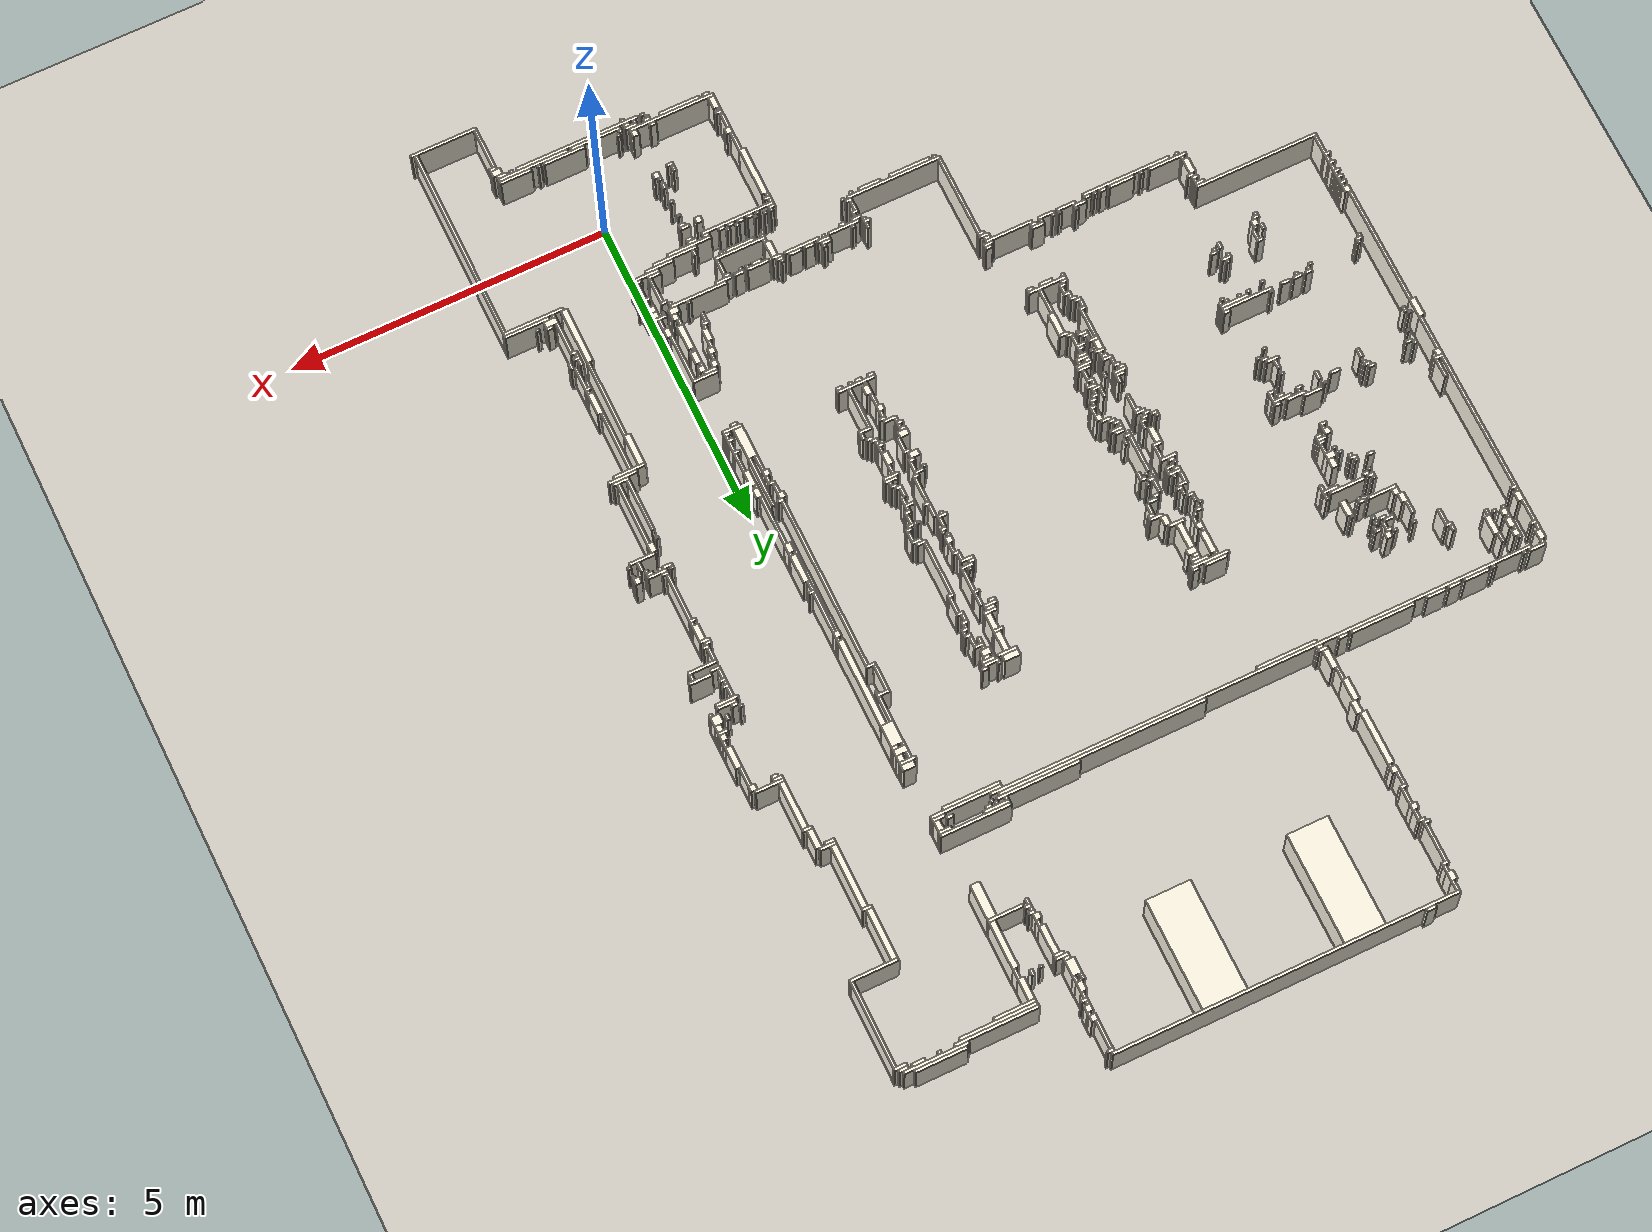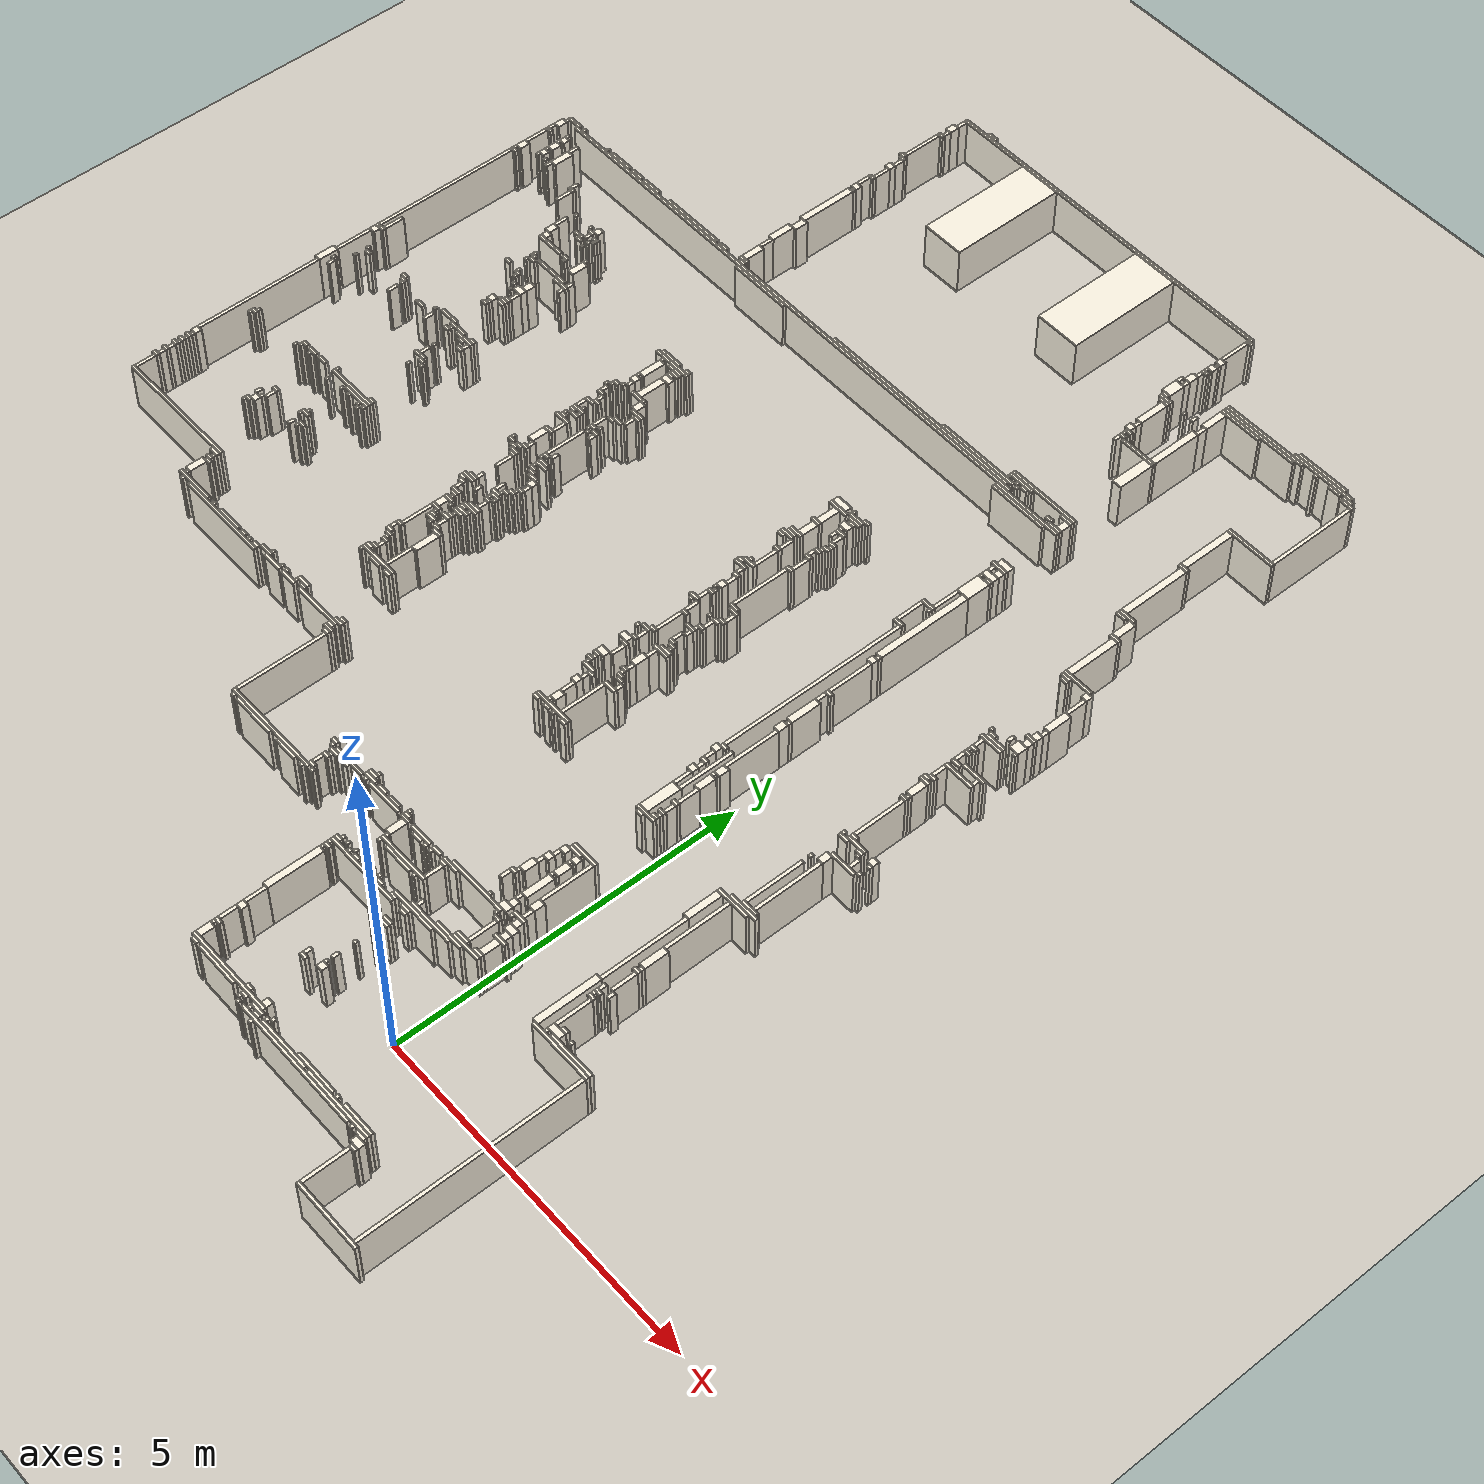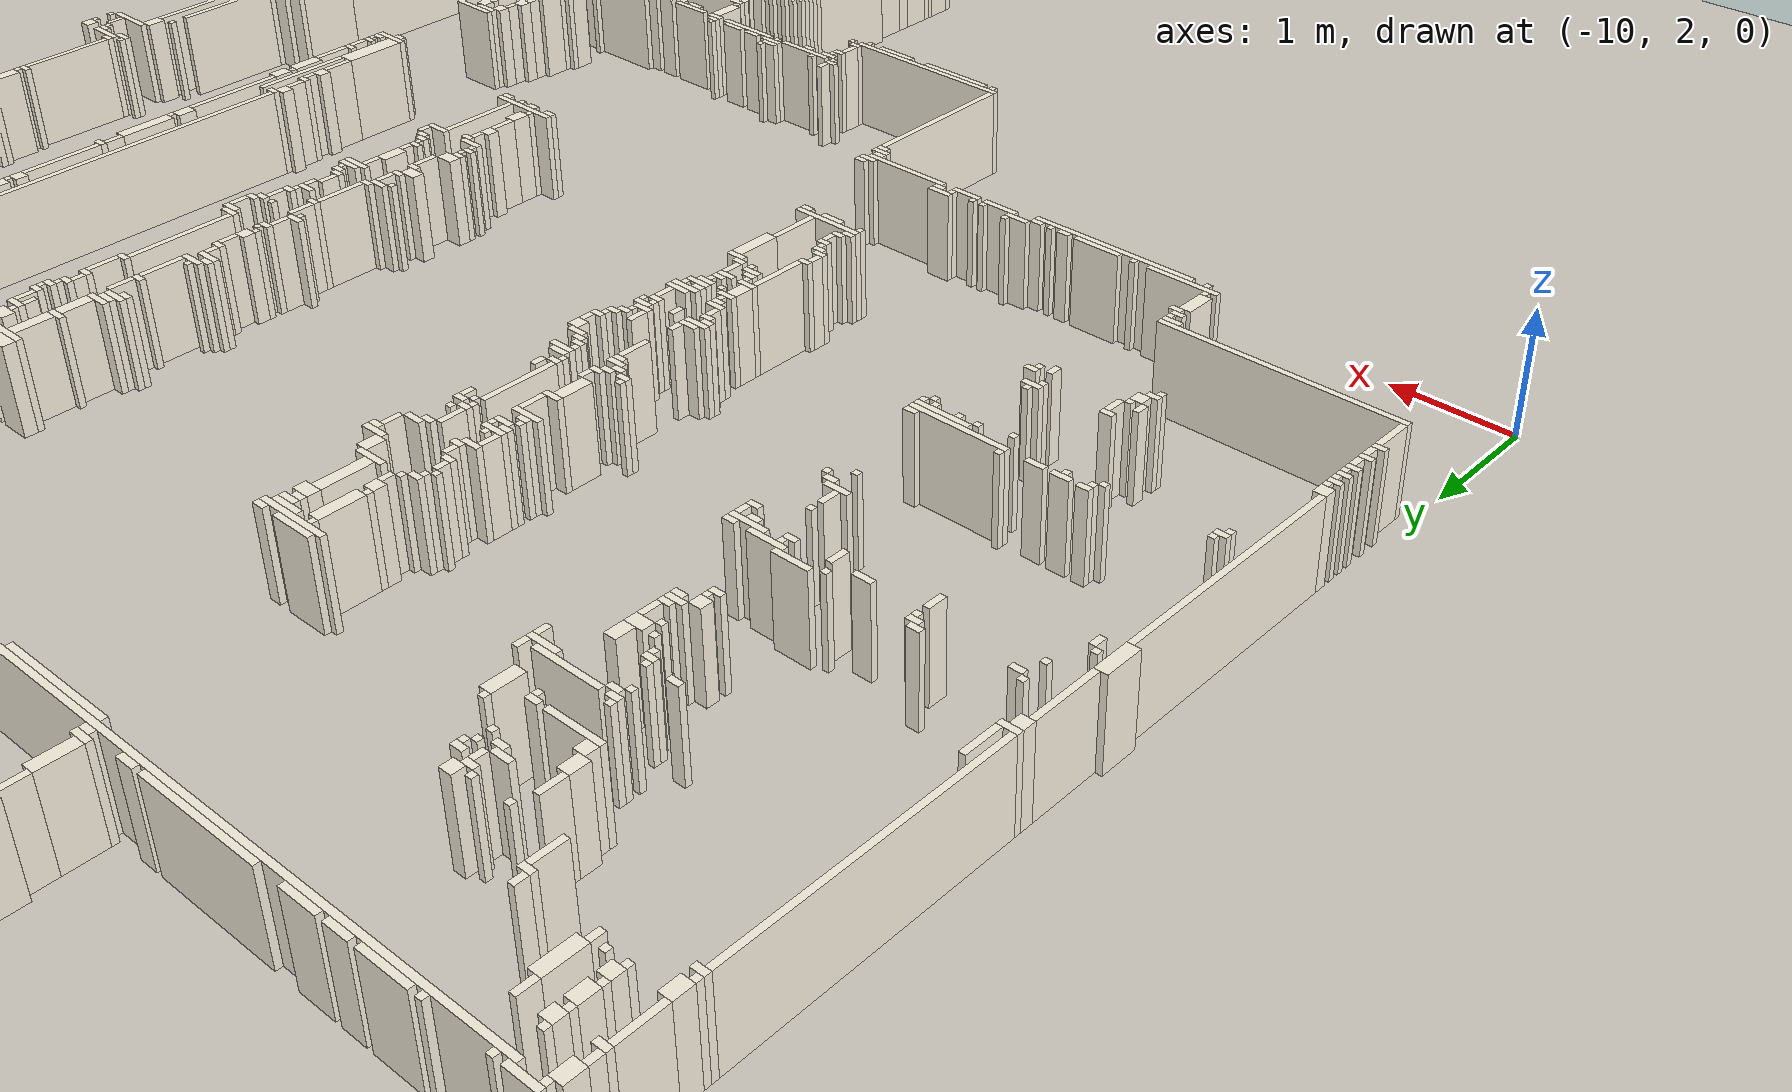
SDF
<?xml version="1.0" ?>
<sdf version="1.8">
  <world name="new_map">
    <physics name="1ms" type="ignored">
      <max_step_size>0.001</max_step_size>
      <real_time_factor>1.0</real_time_factor>
    </physics>

    <plugin filename="gz-sim-physics-system" name="gz::sim::systems::Physics"/>
    <plugin filename="gz-sim-sensors-system" name="gz::sim::systems::Sensors">
      <render_engine>ogre2</render_engine>
    </plugin>
    <plugin filename="gz-sim-user-commands-system" name="gz::sim::systems::UserCommands"/>
    <plugin filename="gz-sim-scene-broadcaster-system" name="gz::sim::systems::SceneBroadcaster"/>
    <plugin filename="gz-sim-imu-system" name="gz::sim::systems::Imu"/>

    <light type="directional" name="sun">
      <cast_shadows>true</cast_shadows>
      <pose>10 10 12 0 0 0</pose>
      <diffuse>0.9 0.9 0.9 1</diffuse>
      <specular>0.6 0.6 0.6 1</specular>
      <attenuation>
        <range>1000</range>
        <constant>0.9</constant>
        <linear>0.01</linear>
        <quadratic>0.001</quadratic>
      </attenuation>
      <direction>-0.5 -0.3 -0.9</direction>
    </light>

    <model name="ground_plane">
      <static>true</static>
      <link name="link">
        <collision name="collision">
          <geometry><plane><normal>0 0 1</normal><size>100 100</size></plane></geometry>
        </collision>
        <visual name="visual">
          <geometry><plane><normal>0 0 1</normal><size>100 100</size></plane></geometry>
          <material><ambient>0.78 0.76 0.72 1</ambient><diffuse>0.82 0.80 0.76 1</diffuse></material>
        </visual>
      </link>
    </model>

    <model name="new_map_env">
      <static>true</static>
      <link name="link">
        <pose>0 0 0 0 0 0</pose>
        <collision name="wall_0000">
          <pose>-5.9290 14.5670 0.3600 0 0 0</pose>
          <geometry><box><size>0.1500 0.0500 0.7200</size></box></geometry>
        </collision>
        <visual name="wall_0000_v">
          <pose>-5.9290 14.5670 0.3600 0 0 0</pose>
          <geometry><box><size>0.1500 0.0500 0.7200</size></box></geometry>
          <material><ambient>0.96 0.93 0.85 1</ambient><diffuse>0.98 0.95 0.88 1</diffuse></material>
        </visual>
        <collision name="wall_0001">
          <pose>-3.7040 14.5170 0.3600 0 0 0</pose>
          <geometry><box><size>5.4000 0.0500 0.7200</size></box></geometry>
        </collision>
        <visual name="wall_0001_v">
          <pose>-3.7040 14.5170 0.3600 0 0 0</pose>
          <geometry><box><size>5.4000 0.0500 0.7200</size></box></geometry>
          <material><ambient>0.96 0.93 0.85 1</ambient><diffuse>0.98 0.95 0.88 1</diffuse></material>
        </visual>
        <collision name="wall_0002">
          <pose>-1.0040 14.4670 0.3600 0 0 0</pose>
          <geometry><box><size>0.1000 0.0500 0.7200</size></box></geometry>
        </collision>
        <visual name="wall_0002_v">
          <pose>-1.0040 14.4670 0.3600 0 0 0</pose>
          <geometry><box><size>0.1000 0.0500 0.7200</size></box></geometry>
          <material><ambient>0.96 0.93 0.85 1</ambient><diffuse>0.98 0.95 0.88 1</diffuse></material>
        </visual>
        <collision name="wall_0003">
          <pose>-6.3790 14.4170 0.3600 0 0 0</pose>
          <geometry><box><size>0.0500 0.1500 0.7200</size></box></geometry>
        </collision>
        <visual name="wall_0003_v">
          <pose>-6.3790 14.4170 0.3600 0 0 0</pose>
          <geometry><box><size>0.0500 0.1500 0.7200</size></box></geometry>
          <material><ambient>0.96 0.93 0.85 1</ambient><diffuse>0.98 0.95 0.88 1</diffuse></material>
        </visual>
        <collision name="wall_0004">
          <pose>-6.4040 14.2670 0.3600 0 0 0</pose>
          <geometry><box><size>0.1000 0.1500 0.7200</size></box></geometry>
        </collision>
        <visual name="wall_0004_v">
          <pose>-6.4040 14.2670 0.3600 0 0 0</pose>
          <geometry><box><size>0.1000 0.1500 0.7200</size></box></geometry>
          <material><ambient>0.96 0.93 0.85 1</ambient><diffuse>0.98 0.95 0.88 1</diffuse></material>
        </visual>
        <collision name="wall_0005">
          <pose>-6.3790 14.1420 0.3600 0 0 0</pose>
          <geometry><box><size>0.0500 0.1000 0.7200</size></box></geometry>
        </collision>
        <visual name="wall_0005_v">
          <pose>-6.3790 14.1420 0.3600 0 0 0</pose>
          <geometry><box><size>0.0500 0.1000 0.7200</size></box></geometry>
          <material><ambient>0.96 0.93 0.85 1</ambient><diffuse>0.98 0.95 0.88 1</diffuse></material>
        </visual>
        <collision name="wall_0006">
          <pose>-6.4040 14.0670 0.3600 0 0 0</pose>
          <geometry><box><size>0.1000 0.0500 0.7200</size></box></geometry>
        </collision>
        <visual name="wall_0006_v">
          <pose>-6.4040 14.0670 0.3600 0 0 0</pose>
          <geometry><box><size>0.1000 0.0500 0.7200</size></box></geometry>
          <material><ambient>0.96 0.93 0.85 1</ambient><diffuse>0.98 0.95 0.88 1</diffuse></material>
        </visual>
        <collision name="wall_0007">
          <pose>-1.0290 14.2170 0.3600 0 0 0</pose>
          <geometry><box><size>0.0500 0.4500 0.7200</size></box></geometry>
        </collision>
        <visual name="wall_0007_v">
          <pose>-1.0290 14.2170 0.3600 0 0 0</pose>
          <geometry><box><size>0.0500 0.4500 0.7200</size></box></geometry>
          <material><ambient>0.96 0.93 0.85 1</ambient><diffuse>0.98 0.95 0.88 1</diffuse></material>
        </visual>
        <collision name="wall_0008">
          <pose>-1.0040 13.9420 0.3600 0 0 0</pose>
          <geometry><box><size>0.1000 0.1000 0.7200</size></box></geometry>
        </collision>
        <visual name="wall_0008_v">
          <pose>-1.0040 13.9420 0.3600 0 0 0</pose>
          <geometry><box><size>0.1000 0.1000 0.7200</size></box></geometry>
          <material><ambient>0.96 0.93 0.85 1</ambient><diffuse>0.98 0.95 0.88 1</diffuse></material>
        </visual>
        <collision name="wall_0009">
          <pose>-0.9790 13.8670 0.3600 0 0 0</pose>
          <geometry><box><size>0.0500 0.0500 0.7200</size></box></geometry>
        </collision>
        <visual name="wall_0009_v">
          <pose>-0.9790 13.8670 0.3600 0 0 0</pose>
          <geometry><box><size>0.0500 0.0500 0.7200</size></box></geometry>
          <material><ambient>0.96 0.93 0.85 1</ambient><diffuse>0.98 0.95 0.88 1</diffuse></material>
        </visual>
        <collision name="wall_0010">
          <pose>-1.0040 13.7920 0.3600 0 0 0</pose>
          <geometry><box><size>0.1000 0.1000 0.7200</size></box></geometry>
        </collision>
        <visual name="wall_0010_v">
          <pose>-1.0040 13.7920 0.3600 0 0 0</pose>
          <geometry><box><size>0.1000 0.1000 0.7200</size></box></geometry>
          <material><ambient>0.96 0.93 0.85 1</ambient><diffuse>0.98 0.95 0.88 1</diffuse></material>
        </visual>
        <collision name="wall_0011">
          <pose>-1.0290 13.7170 0.3600 0 0 0</pose>
          <geometry><box><size>0.0500 0.0500 0.7200</size></box></geometry>
        </collision>
        <visual name="wall_0011_v">
          <pose>-1.0290 13.7170 0.3600 0 0 0</pose>
          <geometry><box><size>0.0500 0.0500 0.7200</size></box></geometry>
          <material><ambient>0.96 0.93 0.85 1</ambient><diffuse>0.98 0.95 0.88 1</diffuse></material>
        </visual>
        <collision name="wall_0012">
          <pose>-1.0040 13.6670 0.3600 0 0 0</pose>
          <geometry><box><size>0.1000 0.0500 0.7200</size></box></geometry>
        </collision>
        <visual name="wall_0012_v">
          <pose>-1.0040 13.6670 0.3600 0 0 0</pose>
          <geometry><box><size>0.1000 0.0500 0.7200</size></box></geometry>
          <material><ambient>0.96 0.93 0.85 1</ambient><diffuse>0.98 0.95 0.88 1</diffuse></material>
        </visual>
        <collision name="wall_0013">
          <pose>-1.0290 13.5920 0.3600 0 0 0</pose>
          <geometry><box><size>0.0500 0.1000 0.7200</size></box></geometry>
        </collision>
        <visual name="wall_0013_v">
          <pose>-1.0290 13.5920 0.3600 0 0 0</pose>
          <geometry><box><size>0.0500 0.1000 0.7200</size></box></geometry>
          <material><ambient>0.96 0.93 0.85 1</ambient><diffuse>0.98 0.95 0.88 1</diffuse></material>
        </visual>
        <collision name="wall_0014">
          <pose>1.1460 13.5670 0.3600 0 0 0</pose>
          <geometry><box><size>0.8000 0.0500 0.7200</size></box></geometry>
        </collision>
        <visual name="wall_0014_v">
          <pose>1.1460 13.5670 0.3600 0 0 0</pose>
          <geometry><box><size>0.8000 0.0500 0.7200</size></box></geometry>
          <material><ambient>0.96 0.93 0.85 1</ambient><diffuse>0.98 0.95 0.88 1</diffuse></material>
        </visual>
        <collision name="wall_0015">
          <pose>1.1960 13.5170 0.3600 0 0 0</pose>
          <geometry><box><size>1.0000 0.0500 0.7200</size></box></geometry>
        </collision>
        <visual name="wall_0015_v">
          <pose>1.1960 13.5170 0.3600 0 0 0</pose>
          <geometry><box><size>1.0000 0.0500 0.7200</size></box></geometry>
          <material><ambient>0.96 0.93 0.85 1</ambient><diffuse>0.98 0.95 0.88 1</diffuse></material>
        </visual>
        <collision name="wall_0016">
          <pose>-6.4290 13.7420 0.3600 0 0 0</pose>
          <geometry><box><size>0.0500 0.6000 0.7200</size></box></geometry>
        </collision>
        <visual name="wall_0016_v">
          <pose>-6.4290 13.7420 0.3600 0 0 0</pose>
          <geometry><box><size>0.0500 0.6000 0.7200</size></box></geometry>
          <material><ambient>0.96 0.93 0.85 1</ambient><diffuse>0.98 0.95 0.88 1</diffuse></material>
        </visual>
        <collision name="wall_0017">
          <pose>1.1210 13.4670 0.3600 0 0 0</pose>
          <geometry><box><size>0.0500 0.0500 0.7200</size></box></geometry>
        </collision>
        <visual name="wall_0017_v">
          <pose>1.1210 13.4670 0.3600 0 0 0</pose>
          <geometry><box><size>0.0500 0.0500 0.7200</size></box></geometry>
          <material><ambient>0.96 0.93 0.85 1</ambient><diffuse>0.98 0.95 0.88 1</diffuse></material>
        </visual>
        <collision name="wall_0018">
          <pose>1.6710 13.4670 0.3600 0 0 0</pose>
          <geometry><box><size>0.1500 0.0500 0.7200</size></box></geometry>
        </collision>
        <visual name="wall_0018_v">
          <pose>1.6710 13.4670 0.3600 0 0 0</pose>
          <geometry><box><size>0.1500 0.0500 0.7200</size></box></geometry>
          <material><ambient>0.96 0.93 0.85 1</ambient><diffuse>0.98 0.95 0.88 1</diffuse></material>
        </visual>
        <collision name="wall_0019">
          <pose>0.2460 13.4670 0.3600 0 0 0</pose>
          <geometry><box><size>1.3000 0.0500 0.7200</size></box></geometry>
        </collision>
        <visual name="wall_0019_v">
          <pose>0.2460 13.4670 0.3600 0 0 0</pose>
          <geometry><box><size>1.3000 0.0500 0.7200</size></box></geometry>
          <material><ambient>0.96 0.93 0.85 1</ambient><diffuse>0.98 0.95 0.88 1</diffuse></material>
        </visual>
        <collision name="wall_0020">
          <pose>1.4460 13.4670 0.3600 0 0 0</pose>
          <geometry><box><size>0.2000 0.0500 0.7200</size></box></geometry>
        </collision>
        <visual name="wall_0020_v">
          <pose>1.4460 13.4670 0.3600 0 0 0</pose>
          <geometry><box><size>0.2000 0.0500 0.7200</size></box></geometry>
          <material><ambient>0.96 0.93 0.85 1</ambient><diffuse>0.98 0.95 0.88 1</diffuse></material>
        </visual>
        <collision name="wall_0021">
          <pose>-1.0540 13.4670 0.3600 0 0 0</pose>
          <geometry><box><size>0.1000 0.1500 0.7200</size></box></geometry>
        </collision>
        <visual name="wall_0021_v">
          <pose>-1.0540 13.4670 0.3600 0 0 0</pose>
          <geometry><box><size>0.1000 0.1500 0.7200</size></box></geometry>
          <material><ambient>0.96 0.93 0.85 1</ambient><diffuse>0.98 0.95 0.88 1</diffuse></material>
        </visual>
        <collision name="wall_0022">
          <pose>0.1960 13.4170 0.3600 0 0 0</pose>
          <geometry><box><size>1.2000 0.0500 0.7200</size></box></geometry>
        </collision>
        <visual name="wall_0022_v">
          <pose>0.1960 13.4170 0.3600 0 0 0</pose>
          <geometry><box><size>1.2000 0.0500 0.7200</size></box></geometry>
          <material><ambient>0.96 0.93 0.85 1</ambient><diffuse>0.98 0.95 0.88 1</diffuse></material>
        </visual>
        <collision name="wall_0023">
          <pose>1.6960 13.4170 0.3600 0 0 0</pose>
          <geometry><box><size>0.2000 0.0500 0.7200</size></box></geometry>
        </collision>
        <visual name="wall_0023_v">
          <pose>1.6960 13.4170 0.3600 0 0 0</pose>
          <geometry><box><size>0.2000 0.0500 0.7200</size></box></geometry>
          <material><ambient>0.96 0.93 0.85 1</ambient><diffuse>0.98 0.95 0.88 1</diffuse></material>
        </visual>
        <collision name="wall_0024">
          <pose>-6.4540 13.4170 0.3600 0 0 0</pose>
          <geometry><box><size>0.1000 0.0500 0.7200</size></box></geometry>
        </collision>
        <visual name="wall_0024_v">
          <pose>-6.4540 13.4170 0.3600 0 0 0</pose>
          <geometry><box><size>0.1000 0.0500 0.7200</size></box></geometry>
          <material><ambient>0.96 0.93 0.85 1</ambient><diffuse>0.98 0.95 0.88 1</diffuse></material>
        </visual>
        <collision name="wall_0025">
          <pose>-6.4040 13.3670 0.3600 0 0 0</pose>
          <geometry><box><size>0.1000 0.0500 0.7200</size></box></geometry>
        </collision>
        <visual name="wall_0025_v">
          <pose>-6.4040 13.3670 0.3600 0 0 0</pose>
          <geometry><box><size>0.1000 0.0500 0.7200</size></box></geometry>
          <material><ambient>0.96 0.93 0.85 1</ambient><diffuse>0.98 0.95 0.88 1</diffuse></material>
        </visual>
        <collision name="wall_0026">
          <pose>-0.0790 13.3670 0.3600 0 0 0</pose>
          <geometry><box><size>0.6500 0.0500 0.7200</size></box></geometry>
        </collision>
        <visual name="wall_0026_v">
          <pose>-0.0790 13.3670 0.3600 0 0 0</pose>
          <geometry><box><size>0.6500 0.0500 0.7200</size></box></geometry>
          <material><ambient>0.96 0.93 0.85 1</ambient><diffuse>0.98 0.95 0.88 1</diffuse></material>
        </visual>
        <collision name="wall_0027">
          <pose>-1.0290 13.3420 0.3600 0 0 0</pose>
          <geometry><box><size>0.0500 0.1000 0.7200</size></box></geometry>
        </collision>
        <visual name="wall_0027_v">
          <pose>-1.0290 13.3420 0.3600 0 0 0</pose>
          <geometry><box><size>0.0500 0.1000 0.7200</size></box></geometry>
          <material><ambient>0.96 0.93 0.85 1</ambient><diffuse>0.98 0.95 0.88 1</diffuse></material>
        </visual>
        <collision name="wall_0028">
          <pose>-1.1290 13.3420 0.3600 0 0 0</pose>
          <geometry><box><size>0.0500 0.1000 0.7200</size></box></geometry>
        </collision>
        <visual name="wall_0028_v">
          <pose>-1.1290 13.3420 0.3600 0 0 0</pose>
          <geometry><box><size>0.0500 0.1000 0.7200</size></box></geometry>
          <material><ambient>0.96 0.93 0.85 1</ambient><diffuse>0.98 0.95 0.88 1</diffuse></material>
        </visual>
        <collision name="wall_0029">
          <pose>-6.3790 13.2670 0.3600 0 0 0</pose>
          <geometry><box><size>0.0500 0.1500 0.7200</size></box></geometry>
        </collision>
        <visual name="wall_0029_v">
          <pose>-6.3790 13.2670 0.3600 0 0 0</pose>
          <geometry><box><size>0.0500 0.1500 0.7200</size></box></geometry>
          <material><ambient>0.96 0.93 0.85 1</ambient><diffuse>0.98 0.95 0.88 1</diffuse></material>
        </visual>
        <collision name="wall_0030">
          <pose>-6.4040 13.1420 0.3600 0 0 0</pose>
          <geometry><box><size>0.1000 0.1000 0.7200</size></box></geometry>
        </collision>
        <visual name="wall_0030_v">
          <pose>-6.4040 13.1420 0.3600 0 0 0</pose>
          <geometry><box><size>0.1000 0.1000 0.7200</size></box></geometry>
          <material><ambient>0.96 0.93 0.85 1</ambient><diffuse>0.98 0.95 0.88 1</diffuse></material>
        </visual>
        <collision name="wall_0031">
          <pose>-1.0790 13.1670 0.3600 0 0 0</pose>
          <geometry><box><size>0.1500 0.2500 0.7200</size></box></geometry>
        </collision>
        <visual name="wall_0031_v">
          <pose>-1.0790 13.1670 0.3600 0 0 0</pose>
          <geometry><box><size>0.1500 0.2500 0.7200</size></box></geometry>
          <material><ambient>0.96 0.93 0.85 1</ambient><diffuse>0.98 0.95 0.88 1</diffuse></material>
        </visual>
        <collision name="wall_0032">
          <pose>-0.3540 13.1670 0.3600 0 0 0</pose>
          <geometry><box><size>0.1000 0.3500 0.7200</size></box></geometry>
        </collision>
        <visual name="wall_0032_v">
          <pose>-0.3540 13.1670 0.3600 0 0 0</pose>
          <geometry><box><size>0.1000 0.3500 0.7200</size></box></geometry>
          <material><ambient>0.96 0.93 0.85 1</ambient><diffuse>0.98 0.95 0.88 1</diffuse></material>
        </visual>
        <collision name="wall_0033">
          <pose>-1.0540 13.0170 0.3600 0 0 0</pose>
          <geometry><box><size>0.1000 0.0500 0.7200</size></box></geometry>
        </collision>
        <visual name="wall_0033_v">
          <pose>-1.0540 13.0170 0.3600 0 0 0</pose>
          <geometry><box><size>0.1000 0.0500 0.7200</size></box></geometry>
          <material><ambient>0.96 0.93 0.85 1</ambient><diffuse>0.98 0.95 0.88 1</diffuse></material>
        </visual>
        <collision name="wall_0034">
          <pose>-0.5290 12.9920 0.3600 0 0 0</pose>
          <geometry><box><size>0.0500 0.1000 0.7200</size></box></geometry>
        </collision>
        <visual name="wall_0034_v">
          <pose>-0.5290 12.9920 0.3600 0 0 0</pose>
          <geometry><box><size>0.0500 0.1000 0.7200</size></box></geometry>
          <material><ambient>0.96 0.93 0.85 1</ambient><diffuse>0.98 0.95 0.88 1</diffuse></material>
        </visual>
        <collision name="wall_0035">
          <pose>-0.6790 12.9670 0.3600 0 0 0</pose>
          <geometry><box><size>0.0500 0.0500 0.7200</size></box></geometry>
        </collision>
        <visual name="wall_0035_v">
          <pose>-0.6790 12.9670 0.3600 0 0 0</pose>
          <geometry><box><size>0.0500 0.0500 0.7200</size></box></geometry>
          <material><ambient>0.96 0.93 0.85 1</ambient><diffuse>0.98 0.95 0.88 1</diffuse></material>
        </visual>
        <collision name="wall_0036">
          <pose>-1.0040 12.9670 0.3600 0 0 0</pose>
          <geometry><box><size>0.2000 0.0500 0.7200</size></box></geometry>
        </collision>
        <visual name="wall_0036_v">
          <pose>-1.0040 12.9670 0.3600 0 0 0</pose>
          <geometry><box><size>0.2000 0.0500 0.7200</size></box></geometry>
          <material><ambient>0.96 0.93 0.85 1</ambient><diffuse>0.98 0.95 0.88 1</diffuse></material>
        </visual>
        <collision name="wall_0037">
          <pose>-0.9790 12.9170 0.3600 0 0 0</pose>
          <geometry><box><size>0.1500 0.0500 0.7200</size></box></geometry>
        </collision>
        <visual name="wall_0037_v">
          <pose>-0.9790 12.9170 0.3600 0 0 0</pose>
          <geometry><box><size>0.1500 0.0500 0.7200</size></box></geometry>
          <material><ambient>0.96 0.93 0.85 1</ambient><diffuse>0.98 0.95 0.88 1</diffuse></material>
        </visual>
        <collision name="wall_0038">
          <pose>-6.3790 12.9670 0.3600 0 0 0</pose>
          <geometry><box><size>0.0500 0.2500 0.7200</size></box></geometry>
        </collision>
        <visual name="wall_0038_v">
          <pose>-6.3790 12.9670 0.3600 0 0 0</pose>
          <geometry><box><size>0.0500 0.2500 0.7200</size></box></geometry>
          <material><ambient>0.96 0.93 0.85 1</ambient><diffuse>0.98 0.95 0.88 1</diffuse></material>
        </visual>
        <collision name="wall_0039">
          <pose>-0.3290 12.9170 0.3600 0 0 0</pose>
          <geometry><box><size>0.0500 0.1500 0.7200</size></box></geometry>
        </collision>
        <visual name="wall_0039_v">
          <pose>-0.3290 12.9170 0.3600 0 0 0</pose>
          <geometry><box><size>0.0500 0.1500 0.7200</size></box></geometry>
          <material><ambient>0.96 0.93 0.85 1</ambient><diffuse>0.98 0.95 0.88 1</diffuse></material>
        </visual>
        <collision name="wall_0040">
          <pose>-6.4040 12.8170 0.3600 0 0 0</pose>
          <geometry><box><size>0.1000 0.0500 0.7200</size></box></geometry>
        </collision>
        <visual name="wall_0040_v">
          <pose>-6.4040 12.8170 0.3600 0 0 0</pose>
          <geometry><box><size>0.1000 0.0500 0.7200</size></box></geometry>
          <material><ambient>0.96 0.93 0.85 1</ambient><diffuse>0.98 0.95 0.88 1</diffuse></material>
        </visual>
        <collision name="wall_0041">
          <pose>-4.9290 13.6170 0.3600 0 0 0</pose>
          <geometry><box><size>0.6500 1.7500 0.7200</size></box></geometry>
        </collision>
        <visual name="wall_0041_v">
          <pose>-4.9290 13.6170 0.3600 0 0 0</pose>
          <geometry><box><size>0.6500 1.7500 0.7200</size></box></geometry>
          <material><ambient>0.96 0.93 0.85 1</ambient><diffuse>0.98 0.95 0.88 1</diffuse></material>
        </visual>
        <collision name="wall_0042">
          <pose>-2.7540 13.6170 0.3600 0 0 0</pose>
          <geometry><box><size>0.7000 1.7500 0.7200</size></box></geometry>
        </collision>
        <visual name="wall_0042_v">
          <pose>-2.7540 13.6170 0.3600 0 0 0</pose>
          <geometry><box><size>0.7000 1.7500 0.7200</size></box></geometry>
          <material><ambient>0.96 0.93 0.85 1</ambient><diffuse>0.98 0.95 0.88 1</diffuse></material>
        </visual>
        <collision name="wall_0043">
          <pose>-6.4290 12.6920 0.3600 0 0 0</pose>
          <geometry><box><size>0.0500 0.2000 0.7200</size></box></geometry>
        </collision>
        <visual name="wall_0043_v">
          <pose>-6.4290 12.6920 0.3600 0 0 0</pose>
          <geometry><box><size>0.0500 0.2000 0.7200</size></box></geometry>
          <material><ambient>0.96 0.93 0.85 1</ambient><diffuse>0.98 0.95 0.88 1</diffuse></material>
        </visual>
        <collision name="wall_0044">
          <pose>-6.4040 12.5420 0.3600 0 0 0</pose>
          <geometry><box><size>0.1000 0.1000 0.7200</size></box></geometry>
        </collision>
        <visual name="wall_0044_v">
          <pose>-6.4040 12.5420 0.3600 0 0 0</pose>
          <geometry><box><size>0.1000 0.1000 0.7200</size></box></geometry>
          <material><ambient>0.96 0.93 0.85 1</ambient><diffuse>0.98 0.95 0.88 1</diffuse></material>
        </visual>
        <collision name="wall_0045">
          <pose>-0.9540 12.6670 0.3600 0 0 0</pose>
          <geometry><box><size>0.1000 0.4500 0.7200</size></box></geometry>
        </collision>
        <visual name="wall_0045_v">
          <pose>-0.9540 12.6670 0.3600 0 0 0</pose>
          <geometry><box><size>0.1000 0.4500 0.7200</size></box></geometry>
          <material><ambient>0.96 0.93 0.85 1</ambient><diffuse>0.98 0.95 0.88 1</diffuse></material>
        </visual>
        <collision name="wall_0046">
          <pose>-6.3790 12.4670 0.3600 0 0 0</pose>
          <geometry><box><size>0.0500 0.0500 0.7200</size></box></geometry>
        </collision>
        <visual name="wall_0046_v">
          <pose>-6.3790 12.4670 0.3600 0 0 0</pose>
          <geometry><box><size>0.0500 0.0500 0.7200</size></box></geometry>
          <material><ambient>0.96 0.93 0.85 1</ambient><diffuse>0.98 0.95 0.88 1</diffuse></material>
        </visual>
        <collision name="wall_0047">
          <pose>-0.9290 12.3920 0.3600 0 0 0</pose>
          <geometry><box><size>0.0500 0.1000 0.7200</size></box></geometry>
        </collision>
        <visual name="wall_0047_v">
          <pose>-0.9290 12.3920 0.3600 0 0 0</pose>
          <geometry><box><size>0.0500 0.1000 0.7200</size></box></geometry>
          <material><ambient>0.96 0.93 0.85 1</ambient><diffuse>0.98 0.95 0.88 1</diffuse></material>
        </visual>
        <collision name="wall_0048">
          <pose>-0.9540 12.2920 0.3600 0 0 0</pose>
          <geometry><box><size>0.1000 0.1000 0.7200</size></box></geometry>
        </collision>
        <visual name="wall_0048_v">
          <pose>-0.9540 12.2920 0.3600 0 0 0</pose>
          <geometry><box><size>0.1000 0.1000 0.7200</size></box></geometry>
          <material><ambient>0.96 0.93 0.85 1</ambient><diffuse>0.98 0.95 0.88 1</diffuse></material>
        </visual>
        <collision name="wall_0049">
          <pose>-0.9040 12.2170 0.3600 0 0 0</pose>
          <geometry><box><size>0.1000 0.0500 0.7200</size></box></geometry>
        </collision>
        <visual name="wall_0049_v">
          <pose>-0.9040 12.2170 0.3600 0 0 0</pose>
          <geometry><box><size>0.1000 0.0500 0.7200</size></box></geometry>
          <material><ambient>0.96 0.93 0.85 1</ambient><diffuse>0.98 0.95 0.88 1</diffuse></material>
        </visual>
        <collision name="wall_0050">
          <pose>-0.9290 12.1670 0.3600 0 0 0</pose>
          <geometry><box><size>0.0500 0.0500 0.7200</size></box></geometry>
        </collision>
        <visual name="wall_0050_v">
          <pose>-0.9290 12.1670 0.3600 0 0 0</pose>
          <geometry><box><size>0.0500 0.0500 0.7200</size></box></geometry>
          <material><ambient>0.96 0.93 0.85 1</ambient><diffuse>0.98 0.95 0.88 1</diffuse></material>
        </visual>
        <collision name="wall_0051">
          <pose>-0.3540 12.4670 0.3600 0 0 0</pose>
          <geometry><box><size>0.1000 0.7500 0.7200</size></box></geometry>
        </collision>
        <visual name="wall_0051_v">
          <pose>-0.3540 12.4670 0.3600 0 0 0</pose>
          <geometry><box><size>0.1000 0.7500 0.7200</size></box></geometry>
          <material><ambient>0.96 0.93 0.85 1</ambient><diffuse>0.98 0.95 0.88 1</diffuse></material>
        </visual>
        <collision name="wall_0052">
          <pose>-0.9040 12.1170 0.3600 0 0 0</pose>
          <geometry><box><size>0.1000 0.0500 0.7200</size></box></geometry>
        </collision>
        <visual name="wall_0052_v">
          <pose>-0.9040 12.1170 0.3600 0 0 0</pose>
          <geometry><box><size>0.1000 0.0500 0.7200</size></box></geometry>
          <material><ambient>0.96 0.93 0.85 1</ambient><diffuse>0.98 0.95 0.88 1</diffuse></material>
        </visual>
        <collision name="wall_0053">
          <pose>1.7710 12.7170 0.3600 0 0 0</pose>
          <geometry><box><size>0.0500 1.3500 0.7200</size></box></geometry>
        </collision>
        <visual name="wall_0053_v">
          <pose>1.7710 12.7170 0.3600 0 0 0</pose>
          <geometry><box><size>0.0500 1.3500 0.7200</size></box></geometry>
          <material><ambient>0.96 0.93 0.85 1</ambient><diffuse>0.98 0.95 0.88 1</diffuse></material>
        </visual>
        <collision name="wall_0054">
          <pose>-0.5790 12.0670 0.3600 0 0 0</pose>
          <geometry><box><size>0.5500 0.0500 0.7200</size></box></geometry>
        </collision>
        <visual name="wall_0054_v">
          <pose>-0.5790 12.0670 0.3600 0 0 0</pose>
          <geometry><box><size>0.5500 0.0500 0.7200</size></box></geometry>
          <material><ambient>0.96 0.93 0.85 1</ambient><diffuse>0.98 0.95 0.88 1</diffuse></material>
        </visual>
        <collision name="wall_0055">
          <pose>-0.9290 12.0420 0.3600 0 0 0</pose>
          <geometry><box><size>0.0500 0.1000 0.7200</size></box></geometry>
        </collision>
        <visual name="wall_0055_v">
          <pose>-0.9290 12.0420 0.3600 0 0 0</pose>
          <geometry><box><size>0.0500 0.1000 0.7200</size></box></geometry>
          <material><ambient>0.96 0.93 0.85 1</ambient><diffuse>0.98 0.95 0.88 1</diffuse></material>
        </visual>
        <collision name="wall_0056">
          <pose>1.4210 12.0170 0.3600 0 0 0</pose>
          <geometry><box><size>0.7500 0.0500 0.7200</size></box></geometry>
        </collision>
        <visual name="wall_0056_v">
          <pose>1.4210 12.0170 0.3600 0 0 0</pose>
          <geometry><box><size>0.7500 0.0500 0.7200</size></box></geometry>
          <material><ambient>0.96 0.93 0.85 1</ambient><diffuse>0.98 0.95 0.88 1</diffuse></material>
        </visual>
        <collision name="wall_0057">
          <pose>-6.4040 12.0170 0.3600 0 0 0</pose>
          <geometry><box><size>0.1000 0.8500 0.7200</size></box></geometry>
        </collision>
        <visual name="wall_0057_v">
          <pose>-6.4040 12.0170 0.3600 0 0 0</pose>
          <geometry><box><size>0.1000 0.8500 0.7200</size></box></geometry>
          <material><ambient>0.96 0.93 0.85 1</ambient><diffuse>0.98 0.95 0.88 1</diffuse></material>
        </visual>
        <collision name="wall_0058">
          <pose>-0.3790 11.7670 0.3600 0 0 0</pose>
          <geometry><box><size>0.1500 0.5500 0.7200</size></box></geometry>
        </collision>
        <visual name="wall_0058_v">
          <pose>-0.3790 11.7670 0.3600 0 0 0</pose>
          <geometry><box><size>0.1500 0.5500 0.7200</size></box></geometry>
          <material><ambient>0.96 0.93 0.85 1</ambient><diffuse>0.98 0.95 0.88 1</diffuse></material>
        </visual>
        <collision name="wall_0059">
          <pose>-6.3540 11.4920 0.3600 0 0 0</pose>
          <geometry><box><size>0.1000 0.2000 0.7200</size></box></geometry>
        </collision>
        <visual name="wall_0059_v">
          <pose>-6.3540 11.4920 0.3600 0 0 0</pose>
          <geometry><box><size>0.1000 0.2000 0.7200</size></box></geometry>
          <material><ambient>0.96 0.93 0.85 1</ambient><diffuse>0.98 0.95 0.88 1</diffuse></material>
        </visual>
        <collision name="wall_0060">
          <pose>1.0960 11.5920 0.3600 0 0 0</pose>
          <geometry><box><size>0.1000 0.8000 0.7200</size></box></geometry>
        </collision>
        <visual name="wall_0060_v">
          <pose>1.0960 11.5920 0.3600 0 0 0</pose>
          <geometry><box><size>0.1000 0.8000 0.7200</size></box></geometry>
          <material><ambient>0.96 0.93 0.85 1</ambient><diffuse>0.98 0.95 0.88 1</diffuse></material>
        </visual>
        <collision name="wall_0061">
          <pose>1.1210 11.1670 0.3600 0 0 0</pose>
          <geometry><box><size>0.1500 0.0500 0.7200</size></box></geometry>
        </collision>
        <visual name="wall_0061_v">
          <pose>1.1210 11.1670 0.3600 0 0 0</pose>
          <geometry><box><size>0.1500 0.0500 0.7200</size></box></geometry>
          <material><ambient>0.96 0.93 0.85 1</ambient><diffuse>0.98 0.95 0.88 1</diffuse></material>
        </visual>
        <collision name="wall_0062">
          <pose>-6.4040 11.2170 0.3600 0 0 0</pose>
          <geometry><box><size>0.1000 0.3500 0.7200</size></box></geometry>
        </collision>
        <visual name="wall_0062_v">
          <pose>-6.4040 11.2170 0.3600 0 0 0</pose>
          <geometry><box><size>0.1000 0.3500 0.7200</size></box></geometry>
          <material><ambient>0.96 0.93 0.85 1</ambient><diffuse>0.98 0.95 0.88 1</diffuse></material>
        </visual>
        <collision name="wall_0063">
          <pose>-6.3790 10.9420 0.3600 0 0 0</pose>
          <geometry><box><size>0.0500 0.2000 0.7200</size></box></geometry>
        </collision>
        <visual name="wall_0063_v">
          <pose>-6.3790 10.9420 0.3600 0 0 0</pose>
          <geometry><box><size>0.0500 0.2000 0.7200</size></box></geometry>
          <material><ambient>0.96 0.93 0.85 1</ambient><diffuse>0.98 0.95 0.88 1</diffuse></material>
        </visual>
        <collision name="wall_0064">
          <pose>-0.8040 10.6670 0.3600 0 0 0</pose>
          <geometry><box><size>1.1000 0.0500 0.7200</size></box></geometry>
        </collision>
        <visual name="wall_0064_v">
          <pose>-0.8040 10.6670 0.3600 0 0 0</pose>
          <geometry><box><size>1.1000 0.0500 0.7200</size></box></geometry>
          <material><ambient>0.96 0.93 0.85 1</ambient><diffuse>0.98 0.95 0.88 1</diffuse></material>
        </visual>
        <collision name="wall_0065">
          <pose>-1.1540 10.6170 0.3600 0 0 0</pose>
          <geometry><box><size>0.4000 0.0500 0.7200</size></box></geometry>
        </collision>
        <visual name="wall_0065_v">
          <pose>-1.1540 10.6170 0.3600 0 0 0</pose>
          <geometry><box><size>0.4000 0.0500 0.7200</size></box></geometry>
          <material><ambient>0.96 0.93 0.85 1</ambient><diffuse>0.98 0.95 0.88 1</diffuse></material>
        </visual>
        <collision name="wall_0066">
          <pose>-0.3540 10.6170 0.3600 0 0 0</pose>
          <geometry><box><size>0.2000 0.0500 0.7200</size></box></geometry>
        </collision>
        <visual name="wall_0066_v">
          <pose>-0.3540 10.6170 0.3600 0 0 0</pose>
          <geometry><box><size>0.2000 0.0500 0.7200</size></box></geometry>
          <material><ambient>0.96 0.93 0.85 1</ambient><diffuse>0.98 0.95 0.88 1</diffuse></material>
        </visual>
        <collision name="wall_0067">
          <pose>-6.3540 10.6920 0.3600 0 0 0</pose>
          <geometry><box><size>0.1000 0.3000 0.7200</size></box></geometry>
        </collision>
        <visual name="wall_0067_v">
          <pose>-6.3540 10.6920 0.3600 0 0 0</pose>
          <geometry><box><size>0.1000 0.3000 0.7200</size></box></geometry>
          <material><ambient>0.96 0.93 0.85 1</ambient><diffuse>0.98 0.95 0.88 1</diffuse></material>
        </visual>
        <collision name="wall_0068">
          <pose>-1.1790 10.5670 0.3600 0 0 0</pose>
          <geometry><box><size>0.0500 0.0500 0.7200</size></box></geometry>
        </collision>
        <visual name="wall_0068_v">
          <pose>-1.1790 10.5670 0.3600 0 0 0</pose>
          <geometry><box><size>0.0500 0.0500 0.7200</size></box></geometry>
          <material><ambient>0.96 0.93 0.85 1</ambient><diffuse>0.98 0.95 0.88 1</diffuse></material>
        </visual>
        <collision name="wall_0069">
          <pose>-1.3290 10.5670 0.3600 0 0 0</pose>
          <geometry><box><size>0.0500 0.0500 0.7200</size></box></geometry>
        </collision>
        <visual name="wall_0069_v">
          <pose>-1.3290 10.5670 0.3600 0 0 0</pose>
          <geometry><box><size>0.0500 0.0500 0.7200</size></box></geometry>
          <material><ambient>0.96 0.93 0.85 1</ambient><diffuse>0.98 0.95 0.88 1</diffuse></material>
        </visual>
        <collision name="wall_0070">
          <pose>-1.0540 10.5670 0.3600 0 0 0</pose>
          <geometry><box><size>0.1000 0.0500 0.7200</size></box></geometry>
        </collision>
        <visual name="wall_0070_v">
          <pose>-1.0540 10.5670 0.3600 0 0 0</pose>
          <geometry><box><size>0.1000 0.0500 0.7200</size></box></geometry>
          <material><ambient>0.96 0.93 0.85 1</ambient><diffuse>0.98 0.95 0.88 1</diffuse></material>
        </visual>
        <collision name="wall_0071">
          <pose>-6.3290 10.5170 0.3600 0 0 0</pose>
          <geometry><box><size>0.1500 0.0500 0.7200</size></box></geometry>
        </collision>
        <visual name="wall_0071_v">
          <pose>-6.3290 10.5170 0.3600 0 0 0</pose>
          <geometry><box><size>0.1500 0.0500 0.7200</size></box></geometry>
          <material><ambient>0.96 0.93 0.85 1</ambient><diffuse>0.98 0.95 0.88 1</diffuse></material>
        </visual>
        <collision name="wall_0072">
          <pose>-1.8540 10.5170 0.3600 0 0 0</pose>
          <geometry><box><size>1.3000 0.0500 0.7200</size></box></geometry>
        </collision>
        <visual name="wall_0072_v">
          <pose>-1.8540 10.5170 0.3600 0 0 0</pose>
          <geometry><box><size>1.3000 0.0500 0.7200</size></box></geometry>
          <material><ambient>0.96 0.93 0.85 1</ambient><diffuse>0.98 0.95 0.88 1</diffuse></material>
        </visual>
        <collision name="wall_0073">
          <pose>-1.1290 10.5170 0.3600 0 0 0</pose>
          <geometry><box><size>0.0500 0.0500 0.7200</size></box></geometry>
        </collision>
        <visual name="wall_0073_v">
          <pose>-1.1290 10.5170 0.3600 0 0 0</pose>
          <geometry><box><size>0.0500 0.0500 0.7200</size></box></geometry>
          <material><ambient>0.96 0.93 0.85 1</ambient><diffuse>0.98 0.95 0.88 1</diffuse></material>
        </visual>
        <collision name="wall_0074">
          <pose>-0.3040 10.5170 0.3600 0 0 0</pose>
          <geometry><box><size>0.1000 0.1500 0.7200</size></box></geometry>
        </collision>
        <visual name="wall_0074_v">
          <pose>-0.3040 10.5170 0.3600 0 0 0</pose>
          <geometry><box><size>0.1000 0.1500 0.7200</size></box></geometry>
          <material><ambient>0.96 0.93 0.85 1</ambient><diffuse>0.98 0.95 0.88 1</diffuse></material>
        </visual>
        <collision name="wall_0075">
          <pose>-6.3040 10.4670 0.3600 0 0 0</pose>
          <geometry><box><size>0.1000 0.0500 0.7200</size></box></geometry>
        </collision>
        <visual name="wall_0075_v">
          <pose>-6.3040 10.4670 0.3600 0 0 0</pose>
          <geometry><box><size>0.1000 0.0500 0.7200</size></box></geometry>
          <material><ambient>0.96 0.93 0.85 1</ambient><diffuse>0.98 0.95 0.88 1</diffuse></material>
        </visual>
        <collision name="wall_0076">
          <pose>-0.5040 10.4670 0.3600 0 0 0</pose>
          <geometry><box><size>0.1000 0.0500 0.7200</size></box></geometry>
        </collision>
        <visual name="wall_0076_v">
          <pose>-0.5040 10.4670 0.3600 0 0 0</pose>
          <geometry><box><size>0.1000 0.0500 0.7200</size></box></geometry>
          <material><ambient>0.96 0.93 0.85 1</ambient><diffuse>0.98 0.95 0.88 1</diffuse></material>
        </visual>
        <collision name="wall_0077">
          <pose>-8.4540 10.4670 0.3600 0 0 0</pose>
          <geometry><box><size>0.2000 0.0500 0.7200</size></box></geometry>
        </collision>
        <visual name="wall_0077_v">
          <pose>-8.4540 10.4670 0.3600 0 0 0</pose>
          <geometry><box><size>0.2000 0.0500 0.7200</size></box></geometry>
          <material><ambient>0.96 0.93 0.85 1</ambient><diffuse>0.98 0.95 0.88 1</diffuse></material>
        </visual>
        <collision name="wall_0078">
          <pose>-9.7790 10.4670 0.3600 0 0 0</pose>
          <geometry><box><size>0.2500 0.0500 0.7200</size></box></geometry>
        </collision>
        <visual name="wall_0078_v">
          <pose>-9.7790 10.4670 0.3600 0 0 0</pose>
          <geometry><box><size>0.2500 0.0500 0.7200</size></box></geometry>
          <material><ambient>0.96 0.93 0.85 1</ambient><diffuse>0.98 0.95 0.88 1</diffuse></material>
        </visual>
        <collision name="wall_0079">
          <pose>-2.8790 10.4670 0.3600 0 0 0</pose>
          <geometry><box><size>3.2500 0.0500 0.7200</size></box></geometry>
        </collision>
        <visual name="wall_0079_v">
          <pose>-2.8790 10.4670 0.3600 0 0 0</pose>
          <geometry><box><size>3.2500 0.0500 0.7200</size></box></geometry>
          <material><ambient>0.96 0.93 0.85 1</ambient><diffuse>0.98 0.95 0.88 1</diffuse></material>
        </visual>
        <collision name="wall_0080">
          <pose>-7.3040 10.4670 0.3600 0 0 0</pose>
          <geometry><box><size>1.0000 0.0500 0.7200</size></box></geometry>
        </collision>
        <visual name="wall_0080_v">
          <pose>-7.3040 10.4670 0.3600 0 0 0</pose>
          <geometry><box><size>1.0000 0.0500 0.7200</size></box></geometry>
          <material><ambient>0.96 0.93 0.85 1</ambient><diffuse>0.98 0.95 0.88 1</diffuse></material>
        </visual>
        <collision name="wall_0081">
          <pose>-9.0790 10.4670 0.3600 0 0 0</pose>
          <geometry><box><size>0.0500 0.0500 0.7200</size></box></geometry>
        </collision>
        <visual name="wall_0081_v">
          <pose>-9.0790 10.4670 0.3600 0 0 0</pose>
          <geometry><box><size>0.0500 0.0500 0.7200</size></box></geometry>
          <material><ambient>0.96 0.93 0.85 1</ambient><diffuse>0.98 0.95 0.88 1</diffuse></material>
        </visual>
        <collision name="wall_0082">
          <pose>-6.6790 10.4670 0.3600 0 0 0</pose>
          <geometry><box><size>0.1500 0.0500 0.7200</size></box></geometry>
        </collision>
        <visual name="wall_0082_v">
          <pose>-6.6790 10.4670 0.3600 0 0 0</pose>
          <geometry><box><size>0.1500 0.0500 0.7200</size></box></geometry>
          <material><ambient>0.96 0.93 0.85 1</ambient><diffuse>0.98 0.95 0.88 1</diffuse></material>
        </visual>
        <collision name="wall_0083">
          <pose>-9.5790 10.4670 0.3600 0 0 0</pose>
          <geometry><box><size>0.0500 0.0500 0.7200</size></box></geometry>
        </collision>
        <visual name="wall_0083_v">
          <pose>-9.5790 10.4670 0.3600 0 0 0</pose>
          <geometry><box><size>0.0500 0.0500 0.7200</size></box></geometry>
          <material><ambient>0.96 0.93 0.85 1</ambient><diffuse>0.98 0.95 0.88 1</diffuse></material>
        </visual>
        <collision name="wall_0084">
          <pose>-8.8040 10.4670 0.3600 0 0 0</pose>
          <geometry><box><size>0.4000 0.0500 0.7200</size></box></geometry>
        </collision>
        <visual name="wall_0084_v">
          <pose>-8.8040 10.4670 0.3600 0 0 0</pose>
          <geometry><box><size>0.4000 0.0500 0.7200</size></box></geometry>
          <material><ambient>0.96 0.93 0.85 1</ambient><diffuse>0.98 0.95 0.88 1</diffuse></material>
        </visual>
        <collision name="wall_0085">
          <pose>-8.1540 10.4670 0.3600 0 0 0</pose>
          <geometry><box><size>0.3000 0.0500 0.7200</size></box></geometry>
        </collision>
        <visual name="wall_0085_v">
          <pose>-8.1540 10.4670 0.3600 0 0 0</pose>
          <geometry><box><size>0.3000 0.0500 0.7200</size></box></geometry>
          <material><ambient>0.96 0.93 0.85 1</ambient><diffuse>0.98 0.95 0.88 1</diffuse></material>
        </visual>
        <collision name="wall_0086">
          <pose>-9.8790 10.4170 0.3600 0 0 0</pose>
          <geometry><box><size>0.0500 0.0500 0.7200</size></box></geometry>
        </collision>
        <visual name="wall_0086_v">
          <pose>-9.8790 10.4170 0.3600 0 0 0</pose>
          <geometry><box><size>0.0500 0.0500 0.7200</size></box></geometry>
          <material><ambient>0.96 0.93 0.85 1</ambient><diffuse>0.98 0.95 0.88 1</diffuse></material>
        </visual>
        <collision name="wall_0087">
          <pose>-5.4290 10.4170 0.3600 0 0 0</pose>
          <geometry><box><size>8.5500 0.0500 0.7200</size></box></geometry>
        </collision>
        <visual name="wall_0087_v">
          <pose>-5.4290 10.4170 0.3600 0 0 0</pose>
          <geometry><box><size>8.5500 0.0500 0.7200</size></box></geometry>
          <material><ambient>0.96 0.93 0.85 1</ambient><diffuse>0.98 0.95 0.88 1</diffuse></material>
        </visual>
        <collision name="wall_0088">
          <pose>-0.3540 10.4170 0.3600 0 0 0</pose>
          <geometry><box><size>0.2000 0.0500 0.7200</size></box></geometry>
        </collision>
        <visual name="wall_0088_v">
          <pose>-0.3540 10.4170 0.3600 0 0 0</pose>
          <geometry><box><size>0.2000 0.0500 0.7200</size></box></geometry>
          <material><ambient>0.96 0.93 0.85 1</ambient><diffuse>0.98 0.95 0.88 1</diffuse></material>
        </visual>
        <collision name="wall_0089">
          <pose>-0.8040 10.3670 0.3600 0 0 0</pose>
          <geometry><box><size>1.1000 0.0500 0.7200</size></box></geometry>
        </collision>
        <visual name="wall_0089_v">
          <pose>-0.8040 10.3670 0.3600 0 0 0</pose>
          <geometry><box><size>1.1000 0.0500 0.7200</size></box></geometry>
          <material><ambient>0.96 0.93 0.85 1</ambient><diffuse>0.98 0.95 0.88 1</diffuse></material>
        </visual>
        <collision name="wall_0090">
          <pose>-5.8290 10.3670 0.3600 0 0 0</pose>
          <geometry><box><size>0.9500 0.0500 0.7200</size></box></geometry>
        </collision>
        <visual name="wall_0090_v">
          <pose>-5.8290 10.3670 0.3600 0 0 0</pose>
          <geometry><box><size>0.9500 0.0500 0.7200</size></box></geometry>
          <material><ambient>0.96 0.93 0.85 1</ambient><diffuse>0.98 0.95 0.88 1</diffuse></material>
        </visual>
        <collision name="wall_0091">
          <pose>-0.9040 10.3170 0.3600 0 0 0</pose>
          <geometry><box><size>0.9000 0.0500 0.7200</size></box></geometry>
        </collision>
        <visual name="wall_0091_v">
          <pose>-0.9040 10.3170 0.3600 0 0 0</pose>
          <geometry><box><size>0.9000 0.0500 0.7200</size></box></geometry>
          <material><ambient>0.96 0.93 0.85 1</ambient><diffuse>0.98 0.95 0.88 1</diffuse></material>
        </visual>
        <collision name="wall_0092">
          <pose>-9.9040 10.3170 0.3600 0 0 0</pose>
          <geometry><box><size>0.1000 0.1500 0.7200</size></box></geometry>
        </collision>
        <visual name="wall_0092_v">
          <pose>-9.9040 10.3170 0.3600 0 0 0</pose>
          <geometry><box><size>0.1000 0.1500 0.7200</size></box></geometry>
          <material><ambient>0.96 0.93 0.85 1</ambient><diffuse>0.98 0.95 0.88 1</diffuse></material>
        </visual>
        <collision name="wall_0093">
          <pose>-9.6290 10.2170 0.3600 0 0 0</pose>
          <geometry><box><size>0.0500 0.0500 0.7200</size></box></geometry>
        </collision>
        <visual name="wall_0093_v">
          <pose>-9.6290 10.2170 0.3600 0 0 0</pose>
          <geometry><box><size>0.0500 0.0500 0.7200</size></box></geometry>
          <material><ambient>0.96 0.93 0.85 1</ambient><diffuse>0.98 0.95 0.88 1</diffuse></material>
        </visual>
        <collision name="wall_0094">
          <pose>1.1460 10.6420 0.3600 0 0 0</pose>
          <geometry><box><size>0.1000 1.0000 0.7200</size></box></geometry>
        </collision>
        <visual name="wall_0094_v">
          <pose>1.1460 10.6420 0.3600 0 0 0</pose>
          <geometry><box><size>0.1000 1.0000 0.7200</size></box></geometry>
          <material><ambient>0.96 0.93 0.85 1</ambient><diffuse>0.98 0.95 0.88 1</diffuse></material>
        </visual>
        <collision name="wall_0095">
          <pose>-9.9290 10.1920 0.3600 0 0 0</pose>
          <geometry><box><size>0.0500 0.1000 0.7200</size></box></geometry>
        </collision>
        <visual name="wall_0095_v">
          <pose>-9.9290 10.1920 0.3600 0 0 0</pose>
          <geometry><box><size>0.0500 0.1000 0.7200</size></box></geometry>
          <material><ambient>0.96 0.93 0.85 1</ambient><diffuse>0.98 0.95 0.88 1</diffuse></material>
        </visual>
        <collision name="wall_0096">
          <pose>-9.6040 10.1420 0.3600 0 0 0</pose>
          <geometry><box><size>0.1000 0.1000 0.7200</size></box></geometry>
        </collision>
        <visual name="wall_0096_v">
          <pose>-9.6040 10.1420 0.3600 0 0 0</pose>
          <geometry><box><size>0.1000 0.1000 0.7200</size></box></geometry>
          <material><ambient>0.96 0.93 0.85 1</ambient><diffuse>0.98 0.95 0.88 1</diffuse></material>
        </visual>
        <collision name="wall_0097">
          <pose>-9.9040 10.1170 0.3600 0 0 0</pose>
          <geometry><box><size>0.1000 0.0500 0.7200</size></box></geometry>
        </collision>
        <visual name="wall_0097_v">
          <pose>-9.9040 10.1170 0.3600 0 0 0</pose>
          <geometry><box><size>0.1000 0.0500 0.7200</size></box></geometry>
          <material><ambient>0.96 0.93 0.85 1</ambient><diffuse>0.98 0.95 0.88 1</diffuse></material>
        </visual>
        <collision name="wall_0098">
          <pose>1.2210 10.1170 0.3600 0 0 0</pose>
          <geometry><box><size>0.2500 0.0500 0.7200</size></box></geometry>
        </collision>
        <visual name="wall_0098_v">
          <pose>1.2210 10.1170 0.3600 0 0 0</pose>
          <geometry><box><size>0.2500 0.0500 0.7200</size></box></geometry>
          <material><ambient>0.96 0.93 0.85 1</ambient><diffuse>0.98 0.95 0.88 1</diffuse></material>
        </visual>
        <collision name="wall_0099">
          <pose>-9.3790 10.1170 0.3600 0 0 0</pose>
          <geometry><box><size>0.0500 0.1500 0.7200</size></box></geometry>
        </collision>
        <visual name="wall_0099_v">
          <pose>-9.3790 10.1170 0.3600 0 0 0</pose>
          <geometry><box><size>0.0500 0.1500 0.7200</size></box></geometry>
          <material><ambient>0.96 0.93 0.85 1</ambient><diffuse>0.98 0.95 0.88 1</diffuse></material>
        </visual>
        <collision name="wall_0100">
          <pose>1.1710 10.0670 0.3600 0 0 0</pose>
          <geometry><box><size>0.1500 0.0500 0.7200</size></box></geometry>
        </collision>
        <visual name="wall_0100_v">
          <pose>1.1710 10.0670 0.3600 0 0 0</pose>
          <geometry><box><size>0.1500 0.0500 0.7200</size></box></geometry>
          <material><ambient>0.96 0.93 0.85 1</ambient><diffuse>0.98 0.95 0.88 1</diffuse></material>
        </visual>
        <collision name="wall_0101">
          <pose>-9.6290 10.0670 0.3600 0 0 0</pose>
          <geometry><box><size>0.0500 0.0500 0.7200</size></box></geometry>
        </collision>
        <visual name="wall_0101_v">
          <pose>-9.6290 10.0670 0.3600 0 0 0</pose>
          <geometry><box><size>0.0500 0.0500 0.7200</size></box></geometry>
          <material><ambient>0.96 0.93 0.85 1</ambient><diffuse>0.98 0.95 0.88 1</diffuse></material>
        </visual>
        <collision name="wall_0102">
          <pose>-9.6040 9.9670 0.3600 0 0 0</pose>
          <geometry><box><size>0.1000 0.1500 0.7200</size></box></geometry>
        </collision>
        <visual name="wall_0102_v">
          <pose>-9.6040 9.9670 0.3600 0 0 0</pose>
          <geometry><box><size>0.1000 0.1500 0.7200</size></box></geometry>
          <material><ambient>0.96 0.93 0.85 1</ambient><diffuse>0.98 0.95 0.88 1</diffuse></material>
        </visual>
        <collision name="wall_0103">
          <pose>-9.6290 9.8670 0.3600 0 0 0</pose>
          <geometry><box><size>0.0500 0.0500 0.7200</size></box></geometry>
        </collision>
        <visual name="wall_0103_v">
          <pose>-9.6290 9.8670 0.3600 0 0 0</pose>
          <geometry><box><size>0.0500 0.0500 0.7200</size></box></geometry>
          <material><ambient>0.96 0.93 0.85 1</ambient><diffuse>0.98 0.95 0.88 1</diffuse></material>
        </visual>
        <collision name="wall_0104">
          <pose>1.3460 9.9420 0.3600 0 0 0</pose>
          <geometry><box><size>0.1000 0.3000 0.7200</size></box></geometry>
        </collision>
        <visual name="wall_0104_v">
          <pose>1.3460 9.9420 0.3600 0 0 0</pose>
          <geometry><box><size>0.1000 0.3000 0.7200</size></box></geometry>
          <material><ambient>0.96 0.93 0.85 1</ambient><diffuse>0.98 0.95 0.88 1</diffuse></material>
        </visual>
        <collision name="wall_0105">
          <pose>-9.9290 9.9170 0.3600 0 0 0</pose>
          <geometry><box><size>0.0500 0.3500 0.7200</size></box></geometry>
        </collision>
        <visual name="wall_0105_v">
          <pose>-9.9290 9.9170 0.3600 0 0 0</pose>
          <geometry><box><size>0.0500 0.3500 0.7200</size></box></geometry>
          <material><ambient>0.96 0.93 0.85 1</ambient><diffuse>0.98 0.95 0.88 1</diffuse></material>
        </visual>
        <collision name="wall_0106">
          <pose>-9.3540 9.8920 0.3600 0 0 0</pose>
          <geometry><box><size>0.1000 0.3000 0.7200</size></box></geometry>
        </collision>
        <visual name="wall_0106_v">
          <pose>-9.3540 9.8920 0.3600 0 0 0</pose>
          <geometry><box><size>0.1000 0.3000 0.7200</size></box></geometry>
          <material><ambient>0.96 0.93 0.85 1</ambient><diffuse>0.98 0.95 0.88 1</diffuse></material>
        </visual>
        <collision name="wall_0107">
          <pose>-9.6040 9.7920 0.3600 0 0 0</pose>
          <geometry><box><size>0.1000 0.1000 0.7200</size></box></geometry>
        </collision>
        <visual name="wall_0107_v">
          <pose>-9.6040 9.7920 0.3600 0 0 0</pose>
          <geometry><box><size>0.1000 0.1000 0.7200</size></box></geometry>
          <material><ambient>0.96 0.93 0.85 1</ambient><diffuse>0.98 0.95 0.88 1</diffuse></material>
        </visual>
        <collision name="wall_0108">
          <pose>1.3710 9.7670 0.3600 0 0 0</pose>
          <geometry><box><size>0.1500 0.0500 0.7200</size></box></geometry>
        </collision>
        <visual name="wall_0108_v">
          <pose>1.3710 9.7670 0.3600 0 0 0</pose>
          <geometry><box><size>0.1500 0.0500 0.7200</size></box></geometry>
          <material><ambient>0.96 0.93 0.85 1</ambient><diffuse>0.98 0.95 0.88 1</diffuse></material>
        </visual>
        <collision name="wall_0109">
          <pose>-9.4790 9.7170 0.3600 0 0 0</pose>
          <geometry><box><size>0.0500 0.0500 0.7200</size></box></geometry>
        </collision>
        <visual name="wall_0109_v">
          <pose>-9.4790 9.7170 0.3600 0 0 0</pose>
          <geometry><box><size>0.0500 0.0500 0.7200</size></box></geometry>
          <material><ambient>0.96 0.93 0.85 1</ambient><diffuse>0.98 0.95 0.88 1</diffuse></material>
        </visual>
        <collision name="wall_0110">
          <pose>-9.6290 9.7170 0.3600 0 0 0</pose>
          <geometry><box><size>0.0500 0.0500 0.7200</size></box></geometry>
        </collision>
        <visual name="wall_0110_v">
          <pose>-9.6290 9.7170 0.3600 0 0 0</pose>
          <geometry><box><size>0.0500 0.0500 0.7200</size></box></geometry>
          <material><ambient>0.96 0.93 0.85 1</ambient><diffuse>0.98 0.95 0.88 1</diffuse></material>
        </visual>
        <collision name="wall_0111">
          <pose>-9.3790 9.6920 0.3600 0 0 0</pose>
          <geometry><box><size>0.0500 0.1000 0.7200</size></box></geometry>
        </collision>
        <visual name="wall_0111_v">
          <pose>-9.3790 9.6920 0.3600 0 0 0</pose>
          <geometry><box><size>0.0500 0.1000 0.7200</size></box></geometry>
          <material><ambient>0.96 0.93 0.85 1</ambient><diffuse>0.98 0.95 0.88 1</diffuse></material>
        </visual>
        <collision name="wall_0112">
          <pose>-8.8290 9.6920 0.3600 0 0 0</pose>
          <geometry><box><size>0.0500 0.1000 0.7200</size></box></geometry>
        </collision>
        <visual name="wall_0112_v">
          <pose>-8.8290 9.6920 0.3600 0 0 0</pose>
          <geometry><box><size>0.0500 0.1000 0.7200</size></box></geometry>
          <material><ambient>0.96 0.93 0.85 1</ambient><diffuse>0.98 0.95 0.88 1</diffuse></material>
        </visual>
        <collision name="wall_0113">
          <pose>-9.9040 9.6670 0.3600 0 0 0</pose>
          <geometry><box><size>0.1000 0.1500 0.7200</size></box></geometry>
        </collision>
        <visual name="wall_0113_v">
          <pose>-9.9040 9.6670 0.3600 0 0 0</pose>
          <geometry><box><size>0.1000 0.1500 0.7200</size></box></geometry>
          <material><ambient>0.96 0.93 0.85 1</ambient><diffuse>0.98 0.95 0.88 1</diffuse></material>
        </visual>
        <collision name="wall_0114">
          <pose>-8.8040 9.6170 0.3600 0 0 0</pose>
          <geometry><box><size>0.1000 0.0500 0.7200</size></box></geometry>
        </collision>
        <visual name="wall_0114_v">
          <pose>-8.8040 9.6170 0.3600 0 0 0</pose>
          <geometry><box><size>0.1000 0.0500 0.7200</size></box></geometry>
          <material><ambient>0.96 0.93 0.85 1</ambient><diffuse>0.98 0.95 0.88 1</diffuse></material>
        </visual>
        <collision name="wall_0115">
          <pose>-9.9290 9.5670 0.3600 0 0 0</pose>
          <geometry><box><size>0.0500 0.0500 0.7200</size></box></geometry>
        </collision>
        <visual name="wall_0115_v">
          <pose>-9.9290 9.5670 0.3600 0 0 0</pose>
          <geometry><box><size>0.0500 0.0500 0.7200</size></box></geometry>
          <material><ambient>0.96 0.93 0.85 1</ambient><diffuse>0.98 0.95 0.88 1</diffuse></material>
        </visual>
        <collision name="wall_0116">
          <pose>-0.3040 9.5420 0.3600 0 0 0</pose>
          <geometry><box><size>0.2000 0.1000 0.7200</size></box></geometry>
        </collision>
        <visual name="wall_0116_v">
          <pose>-0.3040 9.5420 0.3600 0 0 0</pose>
          <geometry><box><size>0.2000 0.1000 0.7200</size></box></geometry>
          <material><ambient>0.96 0.93 0.85 1</ambient><diffuse>0.98 0.95 0.88 1</diffuse></material>
        </visual>
        <collision name="wall_0117">
          <pose>-9.9040 9.5170 0.3600 0 0 0</pose>
          <geometry><box><size>0.1000 0.0500 0.7200</size></box></geometry>
        </collision>
        <visual name="wall_0117_v">
          <pose>-9.9040 9.5170 0.3600 0 0 0</pose>
          <geometry><box><size>0.1000 0.0500 0.7200</size></box></geometry>
          <material><ambient>0.96 0.93 0.85 1</ambient><diffuse>0.98 0.95 0.88 1</diffuse></material>
        </visual>
        <collision name="wall_0118">
          <pose>-0.3290 9.4670 0.3600 0 0 0</pose>
          <geometry><box><size>0.2500 0.0500 0.7200</size></box></geometry>
        </collision>
        <visual name="wall_0118_v">
          <pose>-0.3290 9.4670 0.3600 0 0 0</pose>
          <geometry><box><size>0.2500 0.0500 0.7200</size></box></geometry>
          <material><ambient>0.96 0.93 0.85 1</ambient><diffuse>0.98 0.95 0.88 1</diffuse></material>
        </visual>
        <collision name="wall_0119">
          <pose>-8.7790 9.4670 0.3600 0 0 0</pose>
          <geometry><box><size>0.0500 0.2500 0.7200</size></box></geometry>
        </collision>
        <visual name="wall_0119_v">
          <pose>-8.7790 9.4670 0.3600 0 0 0</pose>
          <geometry><box><size>0.0500 0.2500 0.7200</size></box></geometry>
          <material><ambient>0.96 0.93 0.85 1</ambient><diffuse>0.98 0.95 0.88 1</diffuse></material>
        </visual>
        <collision name="wall_0120">
          <pose>-0.3790 9.3920 0.3600 0 0 0</pose>
          <geometry><box><size>0.0500 0.1000 0.7200</size></box></geometry>
        </collision>
        <visual name="wall_0120_v">
          <pose>-0.3790 9.3920 0.3600 0 0 0</pose>
          <geometry><box><size>0.0500 0.1000 0.7200</size></box></geometry>
          <material><ambient>0.96 0.93 0.85 1</ambient><diffuse>0.98 0.95 0.88 1</diffuse></material>
        </visual>
        <collision name="wall_0121">
          <pose>-7.9540 9.3920 0.3600 0 0 0</pose>
          <geometry><box><size>0.1000 0.1000 0.7200</size></box></geometry>
        </collision>
        <visual name="wall_0121_v">
          <pose>-7.9540 9.3920 0.3600 0 0 0</pose>
          <geometry><box><size>0.1000 0.1000 0.7200</size></box></geometry>
          <material><ambient>0.96 0.93 0.85 1</ambient><diffuse>0.98 0.95 0.88 1</diffuse></material>
        </visual>
        <collision name="wall_0122">
          <pose>-0.2540 9.3920 0.3600 0 0 0</pose>
          <geometry><box><size>0.1000 0.1000 0.7200</size></box></geometry>
        </collision>
        <visual name="wall_0122_v">
          <pose>-0.2540 9.3920 0.3600 0 0 0</pose>
          <geometry><box><size>0.1000 0.1000 0.7200</size></box></geometry>
          <material><ambient>0.96 0.93 0.85 1</ambient><diffuse>0.98 0.95 0.88 1</diffuse></material>
        </visual>
        <collision name="wall_0123">
          <pose>-8.0790 9.3670 0.3600 0 0 0</pose>
          <geometry><box><size>0.0500 0.0500 0.7200</size></box></geometry>
        </collision>
        <visual name="wall_0123_v">
          <pose>-8.0790 9.3670 0.3600 0 0 0</pose>
          <geometry><box><size>0.0500 0.0500 0.7200</size></box></geometry>
          <material><ambient>0.96 0.93 0.85 1</ambient><diffuse>0.98 0.95 0.88 1</diffuse></material>
        </visual>
        <collision name="wall_0124">
          <pose>-8.3790 9.3670 0.3600 0 0 0</pose>
          <geometry><box><size>0.0500 0.0500 0.7200</size></box></geometry>
        </collision>
        <visual name="wall_0124_v">
          <pose>-8.3790 9.3670 0.3600 0 0 0</pose>
          <geometry><box><size>0.0500 0.0500 0.7200</size></box></geometry>
          <material><ambient>0.96 0.93 0.85 1</ambient><diffuse>0.98 0.95 0.88 1</diffuse></material>
        </visual>
        <collision name="wall_0125">
          <pose>-8.0040 9.3170 0.3600 0 0 0</pose>
          <geometry><box><size>0.1000 0.0500 0.7200</size></box></geometry>
        </collision>
        <visual name="wall_0125_v">
          <pose>-8.0040 9.3170 0.3600 0 0 0</pose>
          <geometry><box><size>0.1000 0.0500 0.7200</size></box></geometry>
          <material><ambient>0.96 0.93 0.85 1</ambient><diffuse>0.98 0.95 0.88 1</diffuse></material>
        </visual>
        <collision name="wall_0126">
          <pose>-0.3040 9.2920 0.3600 0 0 0</pose>
          <geometry><box><size>0.2000 0.1000 0.7200</size></box></geometry>
        </collision>
        <visual name="wall_0126_v">
          <pose>-0.3040 9.2920 0.3600 0 0 0</pose>
          <geometry><box><size>0.2000 0.1000 0.7200</size></box></geometry>
          <material><ambient>0.96 0.93 0.85 1</ambient><diffuse>0.98 0.95 0.88 1</diffuse></material>
        </visual>
        <collision name="wall_0127">
          <pose>-7.8540 9.2670 0.3600 0 0 0</pose>
          <geometry><box><size>0.1000 0.0500 0.7200</size></box></geometry>
        </collision>
        <visual name="wall_0127_v">
          <pose>-7.8540 9.2670 0.3600 0 0 0</pose>
          <geometry><box><size>0.1000 0.0500 0.7200</size></box></geometry>
          <material><ambient>0.96 0.93 0.85 1</ambient><diffuse>0.98 0.95 0.88 1</diffuse></material>
        </visual>
        <collision name="wall_0128">
          <pose>-7.9790 9.2420 0.3600 0 0 0</pose>
          <geometry><box><size>0.0500 0.1000 0.7200</size></box></geometry>
        </collision>
        <visual name="wall_0128_v">
          <pose>-7.9790 9.2420 0.3600 0 0 0</pose>
          <geometry><box><size>0.0500 0.1000 0.7200</size></box></geometry>
          <material><ambient>0.96 0.93 0.85 1</ambient><diffuse>0.98 0.95 0.88 1</diffuse></material>
        </visual>
        <collision name="wall_0129">
          <pose>-0.3790 9.2170 0.3600 0 0 0</pose>
          <geometry><box><size>0.0500 0.0500 0.7200</size></box></geometry>
        </collision>
        <visual name="wall_0129_v">
          <pose>-0.3790 9.2170 0.3600 0 0 0</pose>
          <geometry><box><size>0.0500 0.0500 0.7200</size></box></geometry>
          <material><ambient>0.96 0.93 0.85 1</ambient><diffuse>0.98 0.95 0.88 1</diffuse></material>
        </visual>
        <collision name="wall_0130">
          <pose>-0.2540 9.2170 0.3600 0 0 0</pose>
          <geometry><box><size>0.1000 0.0500 0.7200</size></box></geometry>
        </collision>
        <visual name="wall_0130_v">
          <pose>-0.2540 9.2170 0.3600 0 0 0</pose>
          <geometry><box><size>0.1000 0.0500 0.7200</size></box></geometry>
          <material><ambient>0.96 0.93 0.85 1</ambient><diffuse>0.98 0.95 0.88 1</diffuse></material>
        </visual>
        <collision name="wall_0131">
          <pose>-7.8290 9.2170 0.3600 0 0 0</pose>
          <geometry><box><size>0.0500 0.0500 0.7200</size></box></geometry>
        </collision>
        <visual name="wall_0131_v">
          <pose>-7.8290 9.2170 0.3600 0 0 0</pose>
          <geometry><box><size>0.0500 0.0500 0.7200</size></box></geometry>
          <material><ambient>0.96 0.93 0.85 1</ambient><diffuse>0.98 0.95 0.88 1</diffuse></material>
        </visual>
        <collision name="wall_0132">
          <pose>-8.0790 9.1670 0.3600 0 0 0</pose>
          <geometry><box><size>0.1500 0.0500 0.7200</size></box></geometry>
        </collision>
        <visual name="wall_0132_v">
          <pose>-8.0790 9.1670 0.3600 0 0 0</pose>
          <geometry><box><size>0.1500 0.0500 0.7200</size></box></geometry>
          <material><ambient>0.96 0.93 0.85 1</ambient><diffuse>0.98 0.95 0.88 1</diffuse></material>
        </visual>
        <collision name="wall_0133">
          <pose>-7.8790 9.1670 0.3600 0 0 0</pose>
          <geometry><box><size>0.0500 0.0500 0.7200</size></box></geometry>
        </collision>
        <visual name="wall_0133_v">
          <pose>-7.8790 9.1670 0.3600 0 0 0</pose>
          <geometry><box><size>0.0500 0.0500 0.7200</size></box></geometry>
          <material><ambient>0.96 0.93 0.85 1</ambient><diffuse>0.98 0.95 0.88 1</diffuse></material>
        </visual>
        <collision name="wall_0134">
          <pose>-8.0040 9.1170 0.3600 0 0 0</pose>
          <geometry><box><size>0.1000 0.0500 0.7200</size></box></geometry>
        </collision>
        <visual name="wall_0134_v">
          <pose>-8.0040 9.1170 0.3600 0 0 0</pose>
          <geometry><box><size>0.1000 0.0500 0.7200</size></box></geometry>
          <material><ambient>0.96 0.93 0.85 1</ambient><diffuse>0.98 0.95 0.88 1</diffuse></material>
        </visual>
        <collision name="wall_0135">
          <pose>-8.4290 9.1420 0.3600 0 0 0</pose>
          <geometry><box><size>0.0500 0.2000 0.7200</size></box></geometry>
        </collision>
        <visual name="wall_0135_v">
          <pose>-8.4290 9.1420 0.3600 0 0 0</pose>
          <geometry><box><size>0.0500 0.2000 0.7200</size></box></geometry>
          <material><ambient>0.96 0.93 0.85 1</ambient><diffuse>0.98 0.95 0.88 1</diffuse></material>
        </visual>
        <collision name="wall_0136">
          <pose>-7.8790 9.0670 0.3600 0 0 0</pose>
          <geometry><box><size>0.0500 0.0500 0.7200</size></box></geometry>
        </collision>
        <visual name="wall_0136_v">
          <pose>-7.8790 9.0670 0.3600 0 0 0</pose>
          <geometry><box><size>0.0500 0.0500 0.7200</size></box></geometry>
          <material><ambient>0.96 0.93 0.85 1</ambient><diffuse>0.98 0.95 0.88 1</diffuse></material>
        </visual>
        <collision name="wall_0137">
          <pose>1.3960 9.3670 0.3600 0 0 0</pose>
          <geometry><box><size>0.1000 0.7500 0.7200</size></box></geometry>
        </collision>
        <visual name="wall_0137_v">
          <pose>1.3960 9.3670 0.3600 0 0 0</pose>
          <geometry><box><size>0.1000 0.7500 0.7200</size></box></geometry>
          <material><ambient>0.96 0.93 0.85 1</ambient><diffuse>0.98 0.95 0.88 1</diffuse></material>
        </visual>
        <collision name="wall_0138">
          <pose>1.5710 8.9670 0.3600 0 0 0</pose>
          <geometry><box><size>0.4500 0.0500 0.7200</size></box></geometry>
        </collision>
        <visual name="wall_0138_v">
          <pose>1.5710 8.9670 0.3600 0 0 0</pose>
          <geometry><box><size>0.4500 0.0500 0.7200</size></box></geometry>
          <material><ambient>0.96 0.93 0.85 1</ambient><diffuse>0.98 0.95 0.88 1</diffuse></material>
        </visual>
        <collision name="wall_0139">
          <pose>-8.4040 8.9670 0.3600 0 0 0</pose>
          <geometry><box><size>0.1000 0.1500 0.7200</size></box></geometry>
        </collision>
        <visual name="wall_0139_v">
          <pose>-8.4040 8.9670 0.3600 0 0 0</pose>
          <geometry><box><size>0.1000 0.1500 0.7200</size></box></geometry>
          <material><ambient>0.96 0.93 0.85 1</ambient><diffuse>0.98 0.95 0.88 1</diffuse></material>
        </visual>
        <collision name="wall_0140">
          <pose>-7.6290 8.9170 0.3600 0 0 0</pose>
          <geometry><box><size>0.0500 0.0500 0.7200</size></box></geometry>
        </collision>
        <visual name="wall_0140_v">
          <pose>-7.6290 8.9170 0.3600 0 0 0</pose>
          <geometry><box><size>0.0500 0.0500 0.7200</size></box></geometry>
          <material><ambient>0.96 0.93 0.85 1</ambient><diffuse>0.98 0.95 0.88 1</diffuse></material>
        </visual>
        <collision name="wall_0141">
          <pose>1.4210 8.9170 0.3600 0 0 0</pose>
          <geometry><box><size>0.1500 0.0500 0.7200</size></box></geometry>
        </collision>
        <visual name="wall_0141_v">
          <pose>1.4210 8.9170 0.3600 0 0 0</pose>
          <geometry><box><size>0.1500 0.0500 0.7200</size></box></geometry>
          <material><ambient>0.96 0.93 0.85 1</ambient><diffuse>0.98 0.95 0.88 1</diffuse></material>
        </visual>
        <collision name="wall_0142">
          <pose>-0.3040 9.0170 0.3600 0 0 0</pose>
          <geometry><box><size>0.2000 0.3500 0.7200</size></box></geometry>
        </collision>
        <visual name="wall_0142_v">
          <pose>-0.3040 9.0170 0.3600 0 0 0</pose>
          <geometry><box><size>0.2000 0.3500 0.7200</size></box></geometry>
          <material><ambient>0.96 0.93 0.85 1</ambient><diffuse>0.98 0.95 0.88 1</diffuse></material>
        </visual>
        <collision name="wall_0143">
          <pose>1.7960 8.8920 0.3600 0 0 0</pose>
          <geometry><box><size>0.1000 0.1000 0.7200</size></box></geometry>
        </collision>
        <visual name="wall_0143_v">
          <pose>1.7960 8.8920 0.3600 0 0 0</pose>
          <geometry><box><size>0.1000 0.1000 0.7200</size></box></geometry>
          <material><ambient>0.96 0.93 0.85 1</ambient><diffuse>0.98 0.95 0.88 1</diffuse></material>
        </visual>
        <collision name="wall_0144">
          <pose>1.4460 8.8670 0.3600 0 0 0</pose>
          <geometry><box><size>0.1000 0.0500 0.7200</size></box></geometry>
        </collision>
        <visual name="wall_0144_v">
          <pose>1.4460 8.8670 0.3600 0 0 0</pose>
          <geometry><box><size>0.1000 0.0500 0.7200</size></box></geometry>
          <material><ambient>0.96 0.93 0.85 1</ambient><diffuse>0.98 0.95 0.88 1</diffuse></material>
        </visual>
        <collision name="wall_0145">
          <pose>-8.3540 8.8420 0.3600 0 0 0</pose>
          <geometry><box><size>0.1000 0.1000 0.7200</size></box></geometry>
        </collision>
        <visual name="wall_0145_v">
          <pose>-8.3540 8.8420 0.3600 0 0 0</pose>
          <geometry><box><size>0.1000 0.1000 0.7200</size></box></geometry>
          <material><ambient>0.96 0.93 0.85 1</ambient><diffuse>0.98 0.95 0.88 1</diffuse></material>
        </visual>
        <collision name="wall_0146">
          <pose>-7.8540 8.7670 0.3600 0 0 0</pose>
          <geometry><box><size>0.1000 0.0500 0.7200</size></box></geometry>
        </collision>
        <visual name="wall_0146_v">
          <pose>-7.8540 8.7670 0.3600 0 0 0</pose>
          <geometry><box><size>0.1000 0.0500 0.7200</size></box></geometry>
          <material><ambient>0.96 0.93 0.85 1</ambient><diffuse>0.98 0.95 0.88 1</diffuse></material>
        </visual>
        <collision name="wall_0147">
          <pose>-8.1790 8.7670 0.3600 0 0 0</pose>
          <geometry><box><size>0.4500 0.0500 0.7200</size></box></geometry>
        </collision>
        <visual name="wall_0147_v">
          <pose>-8.1790 8.7670 0.3600 0 0 0</pose>
          <geometry><box><size>0.4500 0.0500 0.7200</size></box></geometry>
          <material><ambient>0.96 0.93 0.85 1</ambient><diffuse>0.98 0.95 0.88 1</diffuse></material>
        </visual>
        <collision name="wall_0148">
          <pose>-2.1290 8.7170 0.3600 0 0 0</pose>
          <geometry><box><size>0.0500 0.0500 0.7200</size></box></geometry>
        </collision>
        <visual name="wall_0148_v">
          <pose>-2.1290 8.7170 0.3600 0 0 0</pose>
          <geometry><box><size>0.0500 0.0500 0.7200</size></box></geometry>
          <material><ambient>0.96 0.93 0.85 1</ambient><diffuse>0.98 0.95 0.88 1</diffuse></material>
        </visual>
        <collision name="wall_0149">
          <pose>-1.9040 8.7170 0.3600 0 0 0</pose>
          <geometry><box><size>0.1000 0.0500 0.7200</size></box></geometry>
        </collision>
        <visual name="wall_0149_v">
          <pose>-1.9040 8.7170 0.3600 0 0 0</pose>
          <geometry><box><size>0.1000 0.0500 0.7200</size></box></geometry>
          <material><ambient>0.96 0.93 0.85 1</ambient><diffuse>0.98 0.95 0.88 1</diffuse></material>
        </visual>
        <collision name="wall_0150">
          <pose>-7.8290 8.7170 0.3600 0 0 0</pose>
          <geometry><box><size>0.0500 0.0500 0.7200</size></box></geometry>
        </collision>
        <visual name="wall_0150_v">
          <pose>-7.8290 8.7170 0.3600 0 0 0</pose>
          <geometry><box><size>0.0500 0.0500 0.7200</size></box></geometry>
          <material><ambient>0.96 0.93 0.85 1</ambient><diffuse>0.98 0.95 0.88 1</diffuse></material>
        </visual>
        <collision name="wall_0151">
          <pose>-7.6040 8.7670 0.3600 0 0 0</pose>
          <geometry><box><size>0.1000 0.2500 0.7200</size></box></geometry>
        </collision>
        <visual name="wall_0151_v">
          <pose>-7.6040 8.7670 0.3600 0 0 0</pose>
          <geometry><box><size>0.1000 0.2500 0.7200</size></box></geometry>
          <material><ambient>0.96 0.93 0.85 1</ambient><diffuse>0.98 0.95 0.88 1</diffuse></material>
        </visual>
        <collision name="wall_0152">
          <pose>-2.3290 8.6920 0.3600 0 0 0</pose>
          <geometry><box><size>0.2500 0.1000 0.7200</size></box></geometry>
        </collision>
        <visual name="wall_0152_v">
          <pose>-2.3290 8.6920 0.3600 0 0 0</pose>
          <geometry><box><size>0.2500 0.1000 0.7200</size></box></geometry>
          <material><ambient>0.96 0.93 0.85 1</ambient><diffuse>0.98 0.95 0.88 1</diffuse></material>
        </visual>
        <collision name="wall_0153">
          <pose>-2.0290 8.6670 0.3600 0 0 0</pose>
          <geometry><box><size>0.2500 0.0500 0.7200</size></box></geometry>
        </collision>
        <visual name="wall_0153_v">
          <pose>-2.0290 8.6670 0.3600 0 0 0</pose>
          <geometry><box><size>0.2500 0.0500 0.7200</size></box></geometry>
          <material><ambient>0.96 0.93 0.85 1</ambient><diffuse>0.98 0.95 0.88 1</diffuse></material>
        </visual>
        <collision name="wall_0154">
          <pose>-5.2540 8.6670 0.3600 0 0 0</pose>
          <geometry><box><size>0.1000 0.0500 0.7200</size></box></geometry>
        </collision>
        <visual name="wall_0154_v">
          <pose>-5.2540 8.6670 0.3600 0 0 0</pose>
          <geometry><box><size>0.1000 0.0500 0.7200</size></box></geometry>
          <material><ambient>0.96 0.93 0.85 1</ambient><diffuse>0.98 0.95 0.88 1</diffuse></material>
        </visual>
        <collision name="wall_0155">
          <pose>-5.5790 8.6670 0.3600 0 0 0</pose>
          <geometry><box><size>0.3500 0.0500 0.7200</size></box></geometry>
        </collision>
        <visual name="wall_0155_v">
          <pose>-5.5790 8.6670 0.3600 0 0 0</pose>
          <geometry><box><size>0.3500 0.0500 0.7200</size></box></geometry>
          <material><ambient>0.96 0.93 0.85 1</ambient><diffuse>0.98 0.95 0.88 1</diffuse></material>
        </visual>
        <collision name="wall_0156">
          <pose>-5.5040 8.6170 0.3600 0 0 0</pose>
          <geometry><box><size>0.6000 0.0500 0.7200</size></box></geometry>
        </collision>
        <visual name="wall_0156_v">
          <pose>-5.5040 8.6170 0.3600 0 0 0</pose>
          <geometry><box><size>0.6000 0.0500 0.7200</size></box></geometry>
          <material><ambient>0.96 0.93 0.85 1</ambient><diffuse>0.98 0.95 0.88 1</diffuse></material>
        </visual>
        <collision name="wall_0157">
          <pose>-2.3040 8.6170 0.3600 0 0 0</pose>
          <geometry><box><size>0.3000 0.0500 0.7200</size></box></geometry>
        </collision>
        <visual name="wall_0157_v">
          <pose>-2.3040 8.6170 0.3600 0 0 0</pose>
          <geometry><box><size>0.3000 0.0500 0.7200</size></box></geometry>
          <material><ambient>0.96 0.93 0.85 1</ambient><diffuse>0.98 0.95 0.88 1</diffuse></material>
        </visual>
        <collision name="wall_0158">
          <pose>-2.0040 8.6170 0.3600 0 0 0</pose>
          <geometry><box><size>0.2000 0.0500 0.7200</size></box></geometry>
        </collision>
        <visual name="wall_0158_v">
          <pose>-2.0040 8.6170 0.3600 0 0 0</pose>
          <geometry><box><size>0.2000 0.0500 0.7200</size></box></geometry>
          <material><ambient>0.96 0.93 0.85 1</ambient><diffuse>0.98 0.95 0.88 1</diffuse></material>
        </visual>
        <collision name="wall_0159">
          <pose>1.8210 8.6920 0.3600 0 0 0</pose>
          <geometry><box><size>0.0500 0.3000 0.7200</size></box></geometry>
        </collision>
        <visual name="wall_0159_v">
          <pose>1.8210 8.6920 0.3600 0 0 0</pose>
          <geometry><box><size>0.0500 0.3000 0.7200</size></box></geometry>
          <material><ambient>0.96 0.93 0.85 1</ambient><diffuse>0.98 0.95 0.88 1</diffuse></material>
        </visual>
        <collision name="wall_0160">
          <pose>-5.3790 8.5670 0.3600 0 0 0</pose>
          <geometry><box><size>0.2500 0.0500 0.7200</size></box></geometry>
        </collision>
        <visual name="wall_0160_v">
          <pose>-5.3790 8.5670 0.3600 0 0 0</pose>
          <geometry><box><size>0.2500 0.0500 0.7200</size></box></geometry>
          <material><ambient>0.96 0.93 0.85 1</ambient><diffuse>0.98 0.95 0.88 1</diffuse></material>
        </visual>
        <collision name="wall_0161">
          <pose>-2.0040 8.5670 0.3600 0 0 0</pose>
          <geometry><box><size>0.1000 0.0500 0.7200</size></box></geometry>
        </collision>
        <visual name="wall_0161_v">
          <pose>-2.0040 8.5670 0.3600 0 0 0</pose>
          <geometry><box><size>0.1000 0.0500 0.7200</size></box></geometry>
          <material><ambient>0.96 0.93 0.85 1</ambient><diffuse>0.98 0.95 0.88 1</diffuse></material>
        </visual>
        <collision name="wall_0162">
          <pose>-5.6290 8.5670 0.3600 0 0 0</pose>
          <geometry><box><size>0.0500 0.0500 0.7200</size></box></geometry>
        </collision>
        <visual name="wall_0162_v">
          <pose>-5.6290 8.5670 0.3600 0 0 0</pose>
          <geometry><box><size>0.0500 0.0500 0.7200</size></box></geometry>
          <material><ambient>0.96 0.93 0.85 1</ambient><diffuse>0.98 0.95 0.88 1</diffuse></material>
        </visual>
        <collision name="wall_0163">
          <pose>-5.3290 8.5170 0.3600 0 0 0</pose>
          <geometry><box><size>0.1500 0.0500 0.7200</size></box></geometry>
        </collision>
        <visual name="wall_0163_v">
          <pose>-5.3290 8.5170 0.3600 0 0 0</pose>
          <geometry><box><size>0.1500 0.0500 0.7200</size></box></geometry>
          <material><ambient>0.96 0.93 0.85 1</ambient><diffuse>0.98 0.95 0.88 1</diffuse></material>
        </visual>
        <collision name="wall_0164">
          <pose>-8.1790 8.5170 0.3600 0 0 0</pose>
          <geometry><box><size>0.0500 0.0500 0.7200</size></box></geometry>
        </collision>
        <visual name="wall_0164_v">
          <pose>-8.1790 8.5170 0.3600 0 0 0</pose>
          <geometry><box><size>0.0500 0.0500 0.7200</size></box></geometry>
          <material><ambient>0.96 0.93 0.85 1</ambient><diffuse>0.98 0.95 0.88 1</diffuse></material>
        </visual>
        <collision name="wall_0165">
          <pose>-0.3790 8.6420 0.3600 0 0 0</pose>
          <geometry><box><size>0.0500 0.4000 0.7200</size></box></geometry>
        </collision>
        <visual name="wall_0165_v">
          <pose>-0.3790 8.6420 0.3600 0 0 0</pose>
          <geometry><box><size>0.0500 0.4000 0.7200</size></box></geometry>
          <material><ambient>0.96 0.93 0.85 1</ambient><diffuse>0.98 0.95 0.88 1</diffuse></material>
        </visual>
        <collision name="wall_0166">
          <pose>-2.0290 8.4920 0.3600 0 0 0</pose>
          <geometry><box><size>0.1500 0.1000 0.7200</size></box></geometry>
        </collision>
        <visual name="wall_0166_v">
          <pose>-2.0290 8.4920 0.3600 0 0 0</pose>
          <geometry><box><size>0.1500 0.1000 0.7200</size></box></geometry>
          <material><ambient>0.96 0.93 0.85 1</ambient><diffuse>0.98 0.95 0.88 1</diffuse></material>
        </visual>
        <collision name="wall_0167">
          <pose>-7.4290 8.4920 0.3600 0 0 0</pose>
          <geometry><box><size>0.0500 0.1000 0.7200</size></box></geometry>
        </collision>
        <visual name="wall_0167_v">
          <pose>-7.4290 8.4920 0.3600 0 0 0</pose>
          <geometry><box><size>0.0500 0.1000 0.7200</size></box></geometry>
          <material><ambient>0.96 0.93 0.85 1</ambient><diffuse>0.98 0.95 0.88 1</diffuse></material>
        </visual>
        <collision name="wall_0168">
          <pose>-7.7790 8.4670 0.3600 0 0 0</pose>
          <geometry><box><size>0.5500 0.0500 0.7200</size></box></geometry>
        </collision>
        <visual name="wall_0168_v">
          <pose>-7.7790 8.4670 0.3600 0 0 0</pose>
          <geometry><box><size>0.5500 0.0500 0.7200</size></box></geometry>
          <material><ambient>0.96 0.93 0.85 1</ambient><diffuse>0.98 0.95 0.88 1</diffuse></material>
        </visual>
        <collision name="wall_0169">
          <pose>-8.1540 8.4670 0.3600 0 0 0</pose>
          <geometry><box><size>0.1000 0.0500 0.7200</size></box></geometry>
        </collision>
        <visual name="wall_0169_v">
          <pose>-8.1540 8.4670 0.3600 0 0 0</pose>
          <geometry><box><size>0.1000 0.0500 0.7200</size></box></geometry>
          <material><ambient>0.96 0.93 0.85 1</ambient><diffuse>0.98 0.95 0.88 1</diffuse></material>
        </visual>
        <collision name="wall_0170">
          <pose>-5.3540 8.4670 0.3600 0 0 0</pose>
          <geometry><box><size>0.1000 0.0500 0.7200</size></box></geometry>
        </collision>
        <visual name="wall_0170_v">
          <pose>-5.3540 8.4670 0.3600 0 0 0</pose>
          <geometry><box><size>0.1000 0.0500 0.7200</size></box></geometry>
          <material><ambient>0.96 0.93 0.85 1</ambient><diffuse>0.98 0.95 0.88 1</diffuse></material>
        </visual>
        <collision name="wall_0171">
          <pose>-8.1040 8.4170 0.3600 0 0 0</pose>
          <geometry><box><size>0.1000 0.0500 0.7200</size></box></geometry>
        </collision>
        <visual name="wall_0171_v">
          <pose>-8.1040 8.4170 0.3600 0 0 0</pose>
          <geometry><box><size>0.1000 0.0500 0.7200</size></box></geometry>
          <material><ambient>0.96 0.93 0.85 1</ambient><diffuse>0.98 0.95 0.88 1</diffuse></material>
        </visual>
        <collision name="wall_0172">
          <pose>-7.5290 8.4170 0.3600 0 0 0</pose>
          <geometry><box><size>0.2500 0.0500 0.7200</size></box></geometry>
        </collision>
        <visual name="wall_0172_v">
          <pose>-7.5290 8.4170 0.3600 0 0 0</pose>
          <geometry><box><size>0.2500 0.0500 0.7200</size></box></geometry>
          <material><ambient>0.96 0.93 0.85 1</ambient><diffuse>0.98 0.95 0.88 1</diffuse></material>
        </visual>
        <collision name="wall_0173">
          <pose>-0.4540 8.4170 0.3600 0 0 0</pose>
          <geometry><box><size>0.2000 0.0500 0.7200</size></box></geometry>
        </collision>
        <visual name="wall_0173_v">
          <pose>-0.4540 8.4170 0.3600 0 0 0</pose>
          <geometry><box><size>0.2000 0.0500 0.7200</size></box></geometry>
          <material><ambient>0.96 0.93 0.85 1</ambient><diffuse>0.98 0.95 0.88 1</diffuse></material>
        </visual>
        <collision name="wall_0174">
          <pose>-2.0290 8.4170 0.3600 0 0 0</pose>
          <geometry><box><size>0.0500 0.0500 0.7200</size></box></geometry>
        </collision>
        <visual name="wall_0174_v">
          <pose>-2.0290 8.4170 0.3600 0 0 0</pose>
          <geometry><box><size>0.0500 0.0500 0.7200</size></box></geometry>
          <material><ambient>0.96 0.93 0.85 1</ambient><diffuse>0.98 0.95 0.88 1</diffuse></material>
        </visual>
        <collision name="wall_0175">
          <pose>-5.3290 8.3920 0.3600 0 0 0</pose>
          <geometry><box><size>0.1500 0.1000 0.7200</size></box></geometry>
        </collision>
        <visual name="wall_0175_v">
          <pose>-5.3290 8.3920 0.3600 0 0 0</pose>
          <geometry><box><size>0.1500 0.1000 0.7200</size></box></geometry>
          <material><ambient>0.96 0.93 0.85 1</ambient><diffuse>0.98 0.95 0.88 1</diffuse></material>
        </visual>
        <collision name="wall_0176">
          <pose>-0.3790 8.3670 0.3600 0 0 0</pose>
          <geometry><box><size>0.0500 0.0500 0.7200</size></box></geometry>
        </collision>
        <visual name="wall_0176_v">
          <pose>-0.3790 8.3670 0.3600 0 0 0</pose>
          <geometry><box><size>0.0500 0.0500 0.7200</size></box></geometry>
          <material><ambient>0.96 0.93 0.85 1</ambient><diffuse>0.98 0.95 0.88 1</diffuse></material>
        </visual>
        <collision name="wall_0177">
          <pose>-1.9790 8.3670 0.3600 0 0 0</pose>
          <geometry><box><size>0.1500 0.0500 0.7200</size></box></geometry>
        </collision>
        <visual name="wall_0177_v">
          <pose>-1.9790 8.3670 0.3600 0 0 0</pose>
          <geometry><box><size>0.1500 0.0500 0.7200</size></box></geometry>
          <material><ambient>0.96 0.93 0.85 1</ambient><diffuse>0.98 0.95 0.88 1</diffuse></material>
        </visual>
        <collision name="wall_0178">
          <pose>-8.1790 8.3670 0.3600 0 0 0</pose>
          <geometry><box><size>0.0500 0.0500 0.7200</size></box></geometry>
        </collision>
        <visual name="wall_0178_v">
          <pose>-8.1790 8.3670 0.3600 0 0 0</pose>
          <geometry><box><size>0.0500 0.0500 0.7200</size></box></geometry>
          <material><ambient>0.96 0.93 0.85 1</ambient><diffuse>0.98 0.95 0.88 1</diffuse></material>
        </visual>
        <collision name="wall_0179">
          <pose>-2.3040 8.4420 0.3600 0 0 0</pose>
          <geometry><box><size>0.1000 0.3000 0.7200</size></box></geometry>
        </collision>
        <visual name="wall_0179_v">
          <pose>-2.3040 8.4420 0.3600 0 0 0</pose>
          <geometry><box><size>0.1000 0.3000 0.7200</size></box></geometry>
          <material><ambient>0.96 0.93 0.85 1</ambient><diffuse>0.98 0.95 0.88 1</diffuse></material>
        </visual>
        <collision name="wall_0180">
          <pose>-7.4290 8.3420 0.3600 0 0 0</pose>
          <geometry><box><size>0.0500 0.1000 0.7200</size></box></geometry>
        </collision>
        <visual name="wall_0180_v">
          <pose>-7.4290 8.3420 0.3600 0 0 0</pose>
          <geometry><box><size>0.0500 0.1000 0.7200</size></box></geometry>
          <material><ambient>0.96 0.93 0.85 1</ambient><diffuse>0.98 0.95 0.88 1</diffuse></material>
        </visual>
        <collision name="wall_0181">
          <pose>-2.0290 8.2920 0.3600 0 0 0</pose>
          <geometry><box><size>0.0500 0.1000 0.7200</size></box></geometry>
        </collision>
        <visual name="wall_0181_v">
          <pose>-2.0290 8.2920 0.3600 0 0 0</pose>
          <geometry><box><size>0.0500 0.1000 0.7200</size></box></geometry>
          <material><ambient>0.96 0.93 0.85 1</ambient><diffuse>0.98 0.95 0.88 1</diffuse></material>
        </visual>
        <collision name="wall_0182">
          <pose>-2.3290 8.2670 0.3600 0 0 0</pose>
          <geometry><box><size>0.1500 0.0500 0.7200</size></box></geometry>
        </collision>
        <visual name="wall_0182_v">
          <pose>-2.3290 8.2670 0.3600 0 0 0</pose>
          <geometry><box><size>0.1500 0.0500 0.7200</size></box></geometry>
          <material><ambient>0.96 0.93 0.85 1</ambient><diffuse>0.98 0.95 0.88 1</diffuse></material>
        </visual>
        <collision name="wall_0183">
          <pose>1.8460 8.3670 0.3600 0 0 0</pose>
          <geometry><box><size>0.1000 0.3500 0.7200</size></box></geometry>
        </collision>
        <visual name="wall_0183_v">
          <pose>1.8460 8.3670 0.3600 0 0 0</pose>
          <geometry><box><size>0.1000 0.3500 0.7200</size></box></geometry>
          <material><ambient>0.96 0.93 0.85 1</ambient><diffuse>0.98 0.95 0.88 1</diffuse></material>
        </visual>
        <collision name="wall_0184">
          <pose>-5.6040 8.3670 0.3600 0 0 0</pose>
          <geometry><box><size>0.1000 0.3500 0.7200</size></box></geometry>
        </collision>
        <visual name="wall_0184_v">
          <pose>-5.6040 8.3670 0.3600 0 0 0</pose>
          <geometry><box><size>0.1000 0.3500 0.7200</size></box></geometry>
          <material><ambient>0.96 0.93 0.85 1</ambient><diffuse>0.98 0.95 0.88 1</diffuse></material>
        </visual>
        <collision name="wall_0185">
          <pose>-1.9290 8.2670 0.3600 0 0 0</pose>
          <geometry><box><size>0.0500 0.1500 0.7200</size></box></geometry>
        </collision>
        <visual name="wall_0185_v">
          <pose>-1.9290 8.2670 0.3600 0 0 0</pose>
          <geometry><box><size>0.0500 0.1500 0.7200</size></box></geometry>
          <material><ambient>0.96 0.93 0.85 1</ambient><diffuse>0.98 0.95 0.88 1</diffuse></material>
        </visual>
        <collision name="wall_0186">
          <pose>-8.0790 8.1670 0.3600 0 0 0</pose>
          <geometry><box><size>0.0500 0.0500 0.7200</size></box></geometry>
        </collision>
        <visual name="wall_0186_v">
          <pose>-8.0790 8.1670 0.3600 0 0 0</pose>
          <geometry><box><size>0.0500 0.0500 0.7200</size></box></geometry>
          <material><ambient>0.96 0.93 0.85 1</ambient><diffuse>0.98 0.95 0.88 1</diffuse></material>
        </visual>
        <collision name="wall_0187">
          <pose>-8.3040 8.1670 0.3600 0 0 0</pose>
          <geometry><box><size>0.1000 0.0500 0.7200</size></box></geometry>
        </collision>
        <visual name="wall_0187_v">
          <pose>-8.3040 8.1670 0.3600 0 0 0</pose>
          <geometry><box><size>0.1000 0.0500 0.7200</size></box></geometry>
          <material><ambient>0.96 0.93 0.85 1</ambient><diffuse>0.98 0.95 0.88 1</diffuse></material>
        </visual>
        <collision name="wall_0188">
          <pose>-5.6290 8.1670 0.3600 0 0 0</pose>
          <geometry><box><size>0.0500 0.0500 0.7200</size></box></geometry>
        </collision>
        <visual name="wall_0188_v">
          <pose>-5.6290 8.1670 0.3600 0 0 0</pose>
          <geometry><box><size>0.0500 0.0500 0.7200</size></box></geometry>
          <material><ambient>0.96 0.93 0.85 1</ambient><diffuse>0.98 0.95 0.88 1</diffuse></material>
        </visual>
        <collision name="wall_0189">
          <pose>-1.9040 8.1670 0.3600 0 0 0</pose>
          <geometry><box><size>0.1000 0.0500 0.7200</size></box></geometry>
        </collision>
        <visual name="wall_0189_v">
          <pose>-1.9040 8.1670 0.3600 0 0 0</pose>
          <geometry><box><size>0.1000 0.0500 0.7200</size></box></geometry>
          <material><ambient>0.96 0.93 0.85 1</ambient><diffuse>0.98 0.95 0.88 1</diffuse></material>
        </visual>
        <collision name="wall_0190">
          <pose>1.8710 8.1420 0.3600 0 0 0</pose>
          <geometry><box><size>0.0500 0.1000 0.7200</size></box></geometry>
        </collision>
        <visual name="wall_0190_v">
          <pose>1.8710 8.1420 0.3600 0 0 0</pose>
          <geometry><box><size>0.0500 0.1000 0.7200</size></box></geometry>
          <material><ambient>0.96 0.93 0.85 1</ambient><diffuse>0.98 0.95 0.88 1</diffuse></material>
        </visual>
        <collision name="wall_0191">
          <pose>-8.0540 8.1170 0.3600 0 0 0</pose>
          <geometry><box><size>0.1000 0.0500 0.7200</size></box></geometry>
        </collision>
        <visual name="wall_0191_v">
          <pose>-8.0540 8.1170 0.3600 0 0 0</pose>
          <geometry><box><size>0.1000 0.0500 0.7200</size></box></geometry>
          <material><ambient>0.96 0.93 0.85 1</ambient><diffuse>0.98 0.95 0.88 1</diffuse></material>
        </visual>
        <collision name="wall_0192">
          <pose>-1.8790 8.1170 0.3600 0 0 0</pose>
          <geometry><box><size>0.0500 0.0500 0.7200</size></box></geometry>
        </collision>
        <visual name="wall_0192_v">
          <pose>-1.8790 8.1170 0.3600 0 0 0</pose>
          <geometry><box><size>0.0500 0.0500 0.7200</size></box></geometry>
          <material><ambient>0.96 0.93 0.85 1</ambient><diffuse>0.98 0.95 0.88 1</diffuse></material>
        </visual>
        <collision name="wall_0193">
          <pose>-5.6040 8.0920 0.3600 0 0 0</pose>
          <geometry><box><size>0.1000 0.1000 0.7200</size></box></geometry>
        </collision>
        <visual name="wall_0193_v">
          <pose>-5.6040 8.0920 0.3600 0 0 0</pose>
          <geometry><box><size>0.1000 0.1000 0.7200</size></box></geometry>
          <material><ambient>0.96 0.93 0.85 1</ambient><diffuse>0.98 0.95 0.88 1</diffuse></material>
        </visual>
        <collision name="wall_0194">
          <pose>-8.0290 8.0670 0.3600 0 0 0</pose>
          <geometry><box><size>0.0500 0.0500 0.7200</size></box></geometry>
        </collision>
        <visual name="wall_0194_v">
          <pose>-8.0290 8.0670 0.3600 0 0 0</pose>
          <geometry><box><size>0.0500 0.0500 0.7200</size></box></geometry>
          <material><ambient>0.96 0.93 0.85 1</ambient><diffuse>0.98 0.95 0.88 1</diffuse></material>
        </visual>
        <collision name="wall_0195">
          <pose>-1.9040 8.0670 0.3600 0 0 0</pose>
          <geometry><box><size>0.1000 0.0500 0.7200</size></box></geometry>
        </collision>
        <visual name="wall_0195_v">
          <pose>-1.9040 8.0670 0.3600 0 0 0</pose>
          <geometry><box><size>0.1000 0.0500 0.7200</size></box></geometry>
          <material><ambient>0.96 0.93 0.85 1</ambient><diffuse>0.98 0.95 0.88 1</diffuse></material>
        </visual>
        <collision name="wall_0196">
          <pose>-0.5290 8.1920 0.3600 0 0 0</pose>
          <geometry><box><size>0.0500 0.4000 0.7200</size></box></geometry>
        </collision>
        <visual name="wall_0196_v">
          <pose>-0.5290 8.1920 0.3600 0 0 0</pose>
          <geometry><box><size>0.0500 0.4000 0.7200</size></box></geometry>
          <material><ambient>0.96 0.93 0.85 1</ambient><diffuse>0.98 0.95 0.88 1</diffuse></material>
        </visual>
        <collision name="wall_0197">
          <pose>-2.3040 8.1170 0.3600 0 0 0</pose>
          <geometry><box><size>0.1000 0.2500 0.7200</size></box></geometry>
        </collision>
        <visual name="wall_0197_v">
          <pose>-2.3040 8.1170 0.3600 0 0 0</pose>
          <geometry><box><size>0.1000 0.2500 0.7200</size></box></geometry>
          <material><ambient>0.96 0.93 0.85 1</ambient><diffuse>0.98 0.95 0.88 1</diffuse></material>
        </visual>
        <collision name="wall_0198">
          <pose>-7.7540 8.0670 0.3600 0 0 0</pose>
          <geometry><box><size>0.1000 0.1500 0.7200</size></box></geometry>
        </collision>
        <visual name="wall_0198_v">
          <pose>-7.7540 8.0670 0.3600 0 0 0</pose>
          <geometry><box><size>0.1000 0.1500 0.7200</size></box></geometry>
          <material><ambient>0.96 0.93 0.85 1</ambient><diffuse>0.98 0.95 0.88 1</diffuse></material>
        </visual>
        <collision name="wall_0199">
          <pose>1.8460 8.0420 0.3600 0 0 0</pose>
          <geometry><box><size>0.1000 0.1000 0.7200</size></box></geometry>
        </collision>
        <visual name="wall_0199_v">
          <pose>1.8460 8.0420 0.3600 0 0 0</pose>
          <geometry><box><size>0.1000 0.1000 0.7200</size></box></geometry>
          <material><ambient>0.96 0.93 0.85 1</ambient><diffuse>0.98 0.95 0.88 1</diffuse></material>
        </visual>
        <collision name="wall_0200">
          <pose>-1.9290 8.0170 0.3600 0 0 0</pose>
          <geometry><box><size>0.0500 0.0500 0.7200</size></box></geometry>
        </collision>
        <visual name="wall_0200_v">
          <pose>-1.9290 8.0170 0.3600 0 0 0</pose>
          <geometry><box><size>0.0500 0.0500 0.7200</size></box></geometry>
          <material><ambient>0.96 0.93 0.85 1</ambient><diffuse>0.98 0.95 0.88 1</diffuse></material>
        </visual>
        <collision name="wall_0201">
          <pose>-5.3540 8.1420 0.3600 0 0 0</pose>
          <geometry><box><size>0.1000 0.4000 0.7200</size></box></geometry>
        </collision>
        <visual name="wall_0201_v">
          <pose>-5.3540 8.1420 0.3600 0 0 0</pose>
          <geometry><box><size>0.1000 0.4000 0.7200</size></box></geometry>
          <material><ambient>0.96 0.93 0.85 1</ambient><diffuse>0.98 0.95 0.88 1</diffuse></material>
        </visual>
        <collision name="wall_0202">
          <pose>-5.5790 7.9920 0.3600 0 0 0</pose>
          <geometry><box><size>0.0500 0.1000 0.7200</size></box></geometry>
        </collision>
        <visual name="wall_0202_v">
          <pose>-5.5790 7.9920 0.3600 0 0 0</pose>
          <geometry><box><size>0.0500 0.1000 0.7200</size></box></geometry>
          <material><ambient>0.96 0.93 0.85 1</ambient><diffuse>0.98 0.95 0.88 1</diffuse></material>
        </visual>
        <collision name="wall_0203">
          <pose>-1.9540 7.9670 0.3600 0 0 0</pose>
          <geometry><box><size>0.1000 0.0500 0.7200</size></box></geometry>
        </collision>
        <visual name="wall_0203_v">
          <pose>-1.9540 7.9670 0.3600 0 0 0</pose>
          <geometry><box><size>0.1000 0.0500 0.7200</size></box></geometry>
          <material><ambient>0.96 0.93 0.85 1</ambient><diffuse>0.98 0.95 0.88 1</diffuse></material>
        </visual>
        <collision name="wall_0204">
          <pose>-2.3540 7.9670 0.3600 0 0 0</pose>
          <geometry><box><size>0.2000 0.0500 0.7200</size></box></geometry>
        </collision>
        <visual name="wall_0204_v">
          <pose>-2.3540 7.9670 0.3600 0 0 0</pose>
          <geometry><box><size>0.2000 0.0500 0.7200</size></box></geometry>
          <material><ambient>0.96 0.93 0.85 1</ambient><diffuse>0.98 0.95 0.88 1</diffuse></material>
        </visual>
        <collision name="wall_0205">
          <pose>-7.9290 7.9670 0.3600 0 0 0</pose>
          <geometry><box><size>0.0500 0.0500 0.7200</size></box></geometry>
        </collision>
        <visual name="wall_0205_v">
          <pose>-7.9290 7.9670 0.3600 0 0 0</pose>
          <geometry><box><size>0.0500 0.0500 0.7200</size></box></geometry>
          <material><ambient>0.96 0.93 0.85 1</ambient><diffuse>0.98 0.95 0.88 1</diffuse></material>
        </visual>
        <collision name="wall_0206">
          <pose>-0.4790 7.9670 0.3600 0 0 0</pose>
          <geometry><box><size>0.1500 0.0500 0.7200</size></box></geometry>
        </collision>
        <visual name="wall_0206_v">
          <pose>-0.4790 7.9670 0.3600 0 0 0</pose>
          <geometry><box><size>0.1500 0.0500 0.7200</size></box></geometry>
          <material><ambient>0.96 0.93 0.85 1</ambient><diffuse>0.98 0.95 0.88 1</diffuse></material>
        </visual>
        <collision name="wall_0207">
          <pose>1.8210 7.9670 0.3600 0 0 0</pose>
          <geometry><box><size>0.1500 0.0500 0.7200</size></box></geometry>
        </collision>
        <visual name="wall_0207_v">
          <pose>1.8210 7.9670 0.3600 0 0 0</pose>
          <geometry><box><size>0.1500 0.0500 0.7200</size></box></geometry>
          <material><ambient>0.96 0.93 0.85 1</ambient><diffuse>0.98 0.95 0.88 1</diffuse></material>
        </visual>
        <collision name="wall_0208">
          <pose>-7.7790 7.9420 0.3600 0 0 0</pose>
          <geometry><box><size>0.1500 0.1000 0.7200</size></box></geometry>
        </collision>
        <visual name="wall_0208_v">
          <pose>-7.7790 7.9420 0.3600 0 0 0</pose>
          <geometry><box><size>0.1500 0.1000 0.7200</size></box></geometry>
          <material><ambient>0.96 0.93 0.85 1</ambient><diffuse>0.98 0.95 0.88 1</diffuse></material>
        </visual>
        <collision name="wall_0209">
          <pose>-2.3790 7.9170 0.3600 0 0 0</pose>
          <geometry><box><size>0.1500 0.0500 0.7200</size></box></geometry>
        </collision>
        <visual name="wall_0209_v">
          <pose>-2.3790 7.9170 0.3600 0 0 0</pose>
          <geometry><box><size>0.1500 0.0500 0.7200</size></box></geometry>
          <material><ambient>0.96 0.93 0.85 1</ambient><diffuse>0.98 0.95 0.88 1</diffuse></material>
        </visual>
        <collision name="wall_0210">
          <pose>-5.3290 7.9170 0.3600 0 0 0</pose>
          <geometry><box><size>0.2500 0.0500 0.7200</size></box></geometry>
        </collision>
        <visual name="wall_0210_v">
          <pose>-5.3290 7.9170 0.3600 0 0 0</pose>
          <geometry><box><size>0.2500 0.0500 0.7200</size></box></geometry>
          <material><ambient>0.96 0.93 0.85 1</ambient><diffuse>0.98 0.95 0.88 1</diffuse></material>
        </visual>
        <collision name="wall_0211">
          <pose>-5.6290 7.9170 0.3600 0 0 0</pose>
          <geometry><box><size>0.0500 0.0500 0.7200</size></box></geometry>
        </collision>
        <visual name="wall_0211_v">
          <pose>-5.6290 7.9170 0.3600 0 0 0</pose>
          <geometry><box><size>0.0500 0.0500 0.7200</size></box></geometry>
          <material><ambient>0.96 0.93 0.85 1</ambient><diffuse>0.98 0.95 0.88 1</diffuse></material>
        </visual>
        <collision name="wall_0212">
          <pose>1.8460 7.8920 0.3600 0 0 0</pose>
          <geometry><box><size>0.1000 0.1000 0.7200</size></box></geometry>
        </collision>
        <visual name="wall_0212_v">
          <pose>1.8460 7.8920 0.3600 0 0 0</pose>
          <geometry><box><size>0.1000 0.1000 0.7200</size></box></geometry>
          <material><ambient>0.96 0.93 0.85 1</ambient><diffuse>0.98 0.95 0.88 1</diffuse></material>
        </visual>
        <collision name="wall_0213">
          <pose>-1.9790 7.8920 0.3600 0 0 0</pose>
          <geometry><box><size>0.0500 0.1000 0.7200</size></box></geometry>
        </collision>
        <visual name="wall_0213_v">
          <pose>-1.9790 7.8920 0.3600 0 0 0</pose>
          <geometry><box><size>0.0500 0.1000 0.7200</size></box></geometry>
          <material><ambient>0.96 0.93 0.85 1</ambient><diffuse>0.98 0.95 0.88 1</diffuse></material>
        </visual>
        <collision name="wall_0214">
          <pose>-5.7040 7.8670 0.3600 0 0 0</pose>
          <geometry><box><size>0.1000 0.0500 0.7200</size></box></geometry>
        </collision>
        <visual name="wall_0214_v">
          <pose>-5.7040 7.8670 0.3600 0 0 0</pose>
          <geometry><box><size>0.1000 0.0500 0.7200</size></box></geometry>
          <material><ambient>0.96 0.93 0.85 1</ambient><diffuse>0.98 0.95 0.88 1</diffuse></material>
        </visual>
        <collision name="wall_0215">
          <pose>-2.4040 7.8670 0.3600 0 0 0</pose>
          <geometry><box><size>0.2000 0.0500 0.7200</size></box></geometry>
        </collision>
        <visual name="wall_0215_v">
          <pose>-2.4040 7.8670 0.3600 0 0 0</pose>
          <geometry><box><size>0.2000 0.0500 0.7200</size></box></geometry>
          <material><ambient>0.96 0.93 0.85 1</ambient><diffuse>0.98 0.95 0.88 1</diffuse></material>
        </visual>
        <collision name="wall_0216">
          <pose>-7.8790 7.8670 0.3600 0 0 0</pose>
          <geometry><box><size>0.0500 0.0500 0.7200</size></box></geometry>
        </collision>
        <visual name="wall_0216_v">
          <pose>-7.8790 7.8670 0.3600 0 0 0</pose>
          <geometry><box><size>0.0500 0.0500 0.7200</size></box></geometry>
          <material><ambient>0.96 0.93 0.85 1</ambient><diffuse>0.98 0.95 0.88 1</diffuse></material>
        </visual>
        <collision name="wall_0217">
          <pose>-2.4540 7.8170 0.3600 0 0 0</pose>
          <geometry><box><size>0.1000 0.0500 0.7200</size></box></geometry>
        </collision>
        <visual name="wall_0217_v">
          <pose>-2.4540 7.8170 0.3600 0 0 0</pose>
          <geometry><box><size>0.1000 0.0500 0.7200</size></box></geometry>
          <material><ambient>0.96 0.93 0.85 1</ambient><diffuse>0.98 0.95 0.88 1</diffuse></material>
        </visual>
        <collision name="wall_0218">
          <pose>-5.7290 7.8170 0.3600 0 0 0</pose>
          <geometry><box><size>0.0500 0.0500 0.7200</size></box></geometry>
        </collision>
        <visual name="wall_0218_v">
          <pose>-5.7290 7.8170 0.3600 0 0 0</pose>
          <geometry><box><size>0.0500 0.0500 0.7200</size></box></geometry>
          <material><ambient>0.96 0.93 0.85 1</ambient><diffuse>0.98 0.95 0.88 1</diffuse></material>
        </visual>
        <collision name="wall_0219">
          <pose>-1.9540 7.8170 0.3600 0 0 0</pose>
          <geometry><box><size>0.1000 0.0500 0.7200</size></box></geometry>
        </collision>
        <visual name="wall_0219_v">
          <pose>-1.9540 7.8170 0.3600 0 0 0</pose>
          <geometry><box><size>0.1000 0.0500 0.7200</size></box></geometry>
          <material><ambient>0.96 0.93 0.85 1</ambient><diffuse>0.98 0.95 0.88 1</diffuse></material>
        </visual>
        <collision name="wall_0220">
          <pose>-7.7290 7.8170 0.3600 0 0 0</pose>
          <geometry><box><size>0.0500 0.1500 0.7200</size></box></geometry>
        </collision>
        <visual name="wall_0220_v">
          <pose>-7.7290 7.8170 0.3600 0 0 0</pose>
          <geometry><box><size>0.0500 0.1500 0.7200</size></box></geometry>
          <material><ambient>0.96 0.93 0.85 1</ambient><diffuse>0.98 0.95 0.88 1</diffuse></material>
        </visual>
        <collision name="wall_0221">
          <pose>-5.2040 7.8170 0.3600 0 0 0</pose>
          <geometry><box><size>0.1000 0.1500 0.7200</size></box></geometry>
        </collision>
        <visual name="wall_0221_v">
          <pose>-5.2040 7.8170 0.3600 0 0 0</pose>
          <geometry><box><size>0.1000 0.1500 0.7200</size></box></geometry>
          <material><ambient>0.96 0.93 0.85 1</ambient><diffuse>0.98 0.95 0.88 1</diffuse></material>
        </visual>
        <collision name="wall_0222">
          <pose>1.6710 7.7920 0.3600 0 0 0</pose>
          <geometry><box><size>0.0500 0.1000 0.7200</size></box></geometry>
        </collision>
        <visual name="wall_0222_v">
          <pose>1.6710 7.7920 0.3600 0 0 0</pose>
          <geometry><box><size>0.0500 0.1000 0.7200</size></box></geometry>
          <material><ambient>0.96 0.93 0.85 1</ambient><diffuse>0.98 0.95 0.88 1</diffuse></material>
        </visual>
        <collision name="wall_0223">
          <pose>-5.7790 7.7670 0.3600 0 0 0</pose>
          <geometry><box><size>0.0500 0.0500 0.7200</size></box></geometry>
        </collision>
        <visual name="wall_0223_v">
          <pose>-5.7790 7.7670 0.3600 0 0 0</pose>
          <geometry><box><size>0.0500 0.0500 0.7200</size></box></geometry>
          <material><ambient>0.96 0.93 0.85 1</ambient><diffuse>0.98 0.95 0.88 1</diffuse></material>
        </visual>
        <collision name="wall_0224">
          <pose>1.8210 7.7670 0.3600 0 0 0</pose>
          <geometry><box><size>0.1500 0.1500 0.7200</size></box></geometry>
        </collision>
        <visual name="wall_0224_v">
          <pose>1.8210 7.7670 0.3600 0 0 0</pose>
          <geometry><box><size>0.1500 0.1500 0.7200</size></box></geometry>
          <material><ambient>0.96 0.93 0.85 1</ambient><diffuse>0.98 0.95 0.88 1</diffuse></material>
        </visual>
        <collision name="wall_0225">
          <pose>-7.7540 7.7170 0.3600 0 0 0</pose>
          <geometry><box><size>0.1000 0.0500 0.7200</size></box></geometry>
        </collision>
        <visual name="wall_0225_v">
          <pose>-7.7540 7.7170 0.3600 0 0 0</pose>
          <geometry><box><size>0.1000 0.0500 0.7200</size></box></geometry>
          <material><ambient>0.96 0.93 0.85 1</ambient><diffuse>0.98 0.95 0.88 1</diffuse></material>
        </visual>
        <collision name="wall_0226">
          <pose>1.4210 7.7170 0.3600 0 0 0</pose>
          <geometry><box><size>0.0500 0.0500 0.7200</size></box></geometry>
        </collision>
        <visual name="wall_0226_v">
          <pose>1.4210 7.7170 0.3600 0 0 0</pose>
          <geometry><box><size>0.0500 0.0500 0.7200</size></box></geometry>
          <material><ambient>0.96 0.93 0.85 1</ambient><diffuse>0.98 0.95 0.88 1</diffuse></material>
        </visual>
        <collision name="wall_0227">
          <pose>-5.1040 7.7170 0.3600 0 0 0</pose>
          <geometry><box><size>0.2000 0.0500 0.7200</size></box></geometry>
        </collision>
        <visual name="wall_0227_v">
          <pose>-5.1040 7.7170 0.3600 0 0 0</pose>
          <geometry><box><size>0.2000 0.0500 0.7200</size></box></geometry>
          <material><ambient>0.96 0.93 0.85 1</ambient><diffuse>0.98 0.95 0.88 1</diffuse></material>
        </visual>
        <collision name="wall_0228">
          <pose>-2.2790 7.7420 0.3600 0 0 0</pose>
          <geometry><box><size>0.0500 0.2000 0.7200</size></box></geometry>
        </collision>
        <visual name="wall_0228_v">
          <pose>-2.2790 7.7420 0.3600 0 0 0</pose>
          <geometry><box><size>0.0500 0.2000 0.7200</size></box></geometry>
          <material><ambient>0.96 0.93 0.85 1</ambient><diffuse>0.98 0.95 0.88 1</diffuse></material>
        </visual>
        <collision name="wall_0229">
          <pose>-5.7290 7.6920 0.3600 0 0 0</pose>
          <geometry><box><size>0.0500 0.1000 0.7200</size></box></geometry>
        </collision>
        <visual name="wall_0229_v">
          <pose>-5.7290 7.6920 0.3600 0 0 0</pose>
          <geometry><box><size>0.0500 0.1000 0.7200</size></box></geometry>
          <material><ambient>0.96 0.93 0.85 1</ambient><diffuse>0.98 0.95 0.88 1</diffuse></material>
        </visual>
        <collision name="wall_0230">
          <pose>-7.7790 7.6670 0.3600 0 0 0</pose>
          <geometry><box><size>0.1500 0.0500 0.7200</size></box></geometry>
        </collision>
        <visual name="wall_0230_v">
          <pose>-7.7790 7.6670 0.3600 0 0 0</pose>
          <geometry><box><size>0.1500 0.0500 0.7200</size></box></geometry>
          <material><ambient>0.96 0.93 0.85 1</ambient><diffuse>0.98 0.95 0.88 1</diffuse></material>
        </visual>
        <collision name="wall_0231">
          <pose>1.4960 7.6670 0.3600 0 0 0</pose>
          <geometry><box><size>0.1000 0.0500 0.7200</size></box></geometry>
        </collision>
        <visual name="wall_0231_v">
          <pose>1.4960 7.6670 0.3600 0 0 0</pose>
          <geometry><box><size>0.1000 0.0500 0.7200</size></box></geometry>
          <material><ambient>0.96 0.93 0.85 1</ambient><diffuse>0.98 0.95 0.88 1</diffuse></material>
        </visual>
        <collision name="wall_0232">
          <pose>1.8710 7.6670 0.3600 0 0 0</pose>
          <geometry><box><size>0.0500 0.0500 0.7200</size></box></geometry>
        </collision>
        <visual name="wall_0232_v">
          <pose>1.8710 7.6670 0.3600 0 0 0</pose>
          <geometry><box><size>0.0500 0.0500 0.7200</size></box></geometry>
          <material><ambient>0.96 0.93 0.85 1</ambient><diffuse>0.98 0.95 0.88 1</diffuse></material>
        </visual>
        <collision name="wall_0233">
          <pose>-5.0540 7.6670 0.3600 0 0 0</pose>
          <geometry><box><size>0.1000 0.0500 0.7200</size></box></geometry>
        </collision>
        <visual name="wall_0233_v">
          <pose>-5.0540 7.6670 0.3600 0 0 0</pose>
          <geometry><box><size>0.1000 0.0500 0.7200</size></box></geometry>
          <material><ambient>0.96 0.93 0.85 1</ambient><diffuse>0.98 0.95 0.88 1</diffuse></material>
        </visual>
        <collision name="wall_0234">
          <pose>1.5960 7.6170 0.3600 0 0 0</pose>
          <geometry><box><size>0.3000 0.0500 0.7200</size></box></geometry>
        </collision>
        <visual name="wall_0234_v">
          <pose>1.5960 7.6170 0.3600 0 0 0</pose>
          <geometry><box><size>0.3000 0.0500 0.7200</size></box></geometry>
          <material><ambient>0.96 0.93 0.85 1</ambient><diffuse>0.98 0.95 0.88 1</diffuse></material>
        </visual>
        <collision name="wall_0235">
          <pose>-7.7540 7.6170 0.3600 0 0 0</pose>
          <geometry><box><size>0.1000 0.0500 0.7200</size></box></geometry>
        </collision>
        <visual name="wall_0235_v">
          <pose>-7.7540 7.6170 0.3600 0 0 0</pose>
          <geometry><box><size>0.1000 0.0500 0.7200</size></box></geometry>
          <material><ambient>0.96 0.93 0.85 1</ambient><diffuse>0.98 0.95 0.88 1</diffuse></material>
        </visual>
        <collision name="wall_0236">
          <pose>-5.7040 7.6170 0.3600 0 0 0</pose>
          <geometry><box><size>0.1000 0.0500 0.7200</size></box></geometry>
        </collision>
        <visual name="wall_0236_v">
          <pose>-5.7040 7.6170 0.3600 0 0 0</pose>
          <geometry><box><size>0.1000 0.0500 0.7200</size></box></geometry>
          <material><ambient>0.96 0.93 0.85 1</ambient><diffuse>0.98 0.95 0.88 1</diffuse></material>
        </visual>
        <collision name="wall_0237">
          <pose>-2.3040 7.6170 0.3600 0 0 0</pose>
          <geometry><box><size>0.1000 0.0500 0.7200</size></box></geometry>
        </collision>
        <visual name="wall_0237_v">
          <pose>-2.3040 7.6170 0.3600 0 0 0</pose>
          <geometry><box><size>0.1000 0.0500 0.7200</size></box></geometry>
          <material><ambient>0.96 0.93 0.85 1</ambient><diffuse>0.98 0.95 0.88 1</diffuse></material>
        </visual>
        <collision name="wall_0238">
          <pose>-1.9290 7.6670 0.3600 0 0 0</pose>
          <geometry><box><size>0.0500 0.2500 0.7200</size></box></geometry>
        </collision>
        <visual name="wall_0238_v">
          <pose>-1.9290 7.6670 0.3600 0 0 0</pose>
          <geometry><box><size>0.0500 0.2500 0.7200</size></box></geometry>
          <material><ambient>0.96 0.93 0.85 1</ambient><diffuse>0.98 0.95 0.88 1</diffuse></material>
        </visual>
        <collision name="wall_0239">
          <pose>-7.9040 7.5920 0.3600 0 0 0</pose>
          <geometry><box><size>0.1000 0.1000 0.7200</size></box></geometry>
        </collision>
        <visual name="wall_0239_v">
          <pose>-7.9040 7.5920 0.3600 0 0 0</pose>
          <geometry><box><size>0.1000 0.1000 0.7200</size></box></geometry>
          <material><ambient>0.96 0.93 0.85 1</ambient><diffuse>0.98 0.95 0.88 1</diffuse></material>
        </visual>
        <collision name="wall_0240">
          <pose>1.5710 7.5670 0.3600 0 0 0</pose>
          <geometry><box><size>0.3500 0.0500 0.7200</size></box></geometry>
        </collision>
        <visual name="wall_0240_v">
          <pose>1.5710 7.5670 0.3600 0 0 0</pose>
          <geometry><box><size>0.3500 0.0500 0.7200</size></box></geometry>
          <material><ambient>0.96 0.93 0.85 1</ambient><diffuse>0.98 0.95 0.88 1</diffuse></material>
        </visual>
        <collision name="wall_0241">
          <pose>-5.0790 7.5670 0.3600 0 0 0</pose>
          <geometry><box><size>0.0500 0.1500 0.7200</size></box></geometry>
        </collision>
        <visual name="wall_0241_v">
          <pose>-5.0790 7.5670 0.3600 0 0 0</pose>
          <geometry><box><size>0.0500 0.1500 0.7200</size></box></geometry>
          <material><ambient>0.96 0.93 0.85 1</ambient><diffuse>0.98 0.95 0.88 1</diffuse></material>
        </visual>
        <collision name="wall_0242">
          <pose>-5.6290 7.5420 0.3600 0 0 0</pose>
          <geometry><box><size>0.0500 0.1000 0.7200</size></box></geometry>
        </collision>
        <visual name="wall_0242_v">
          <pose>-5.6290 7.5420 0.3600 0 0 0</pose>
          <geometry><box><size>0.0500 0.1000 0.7200</size></box></geometry>
          <material><ambient>0.96 0.93 0.85 1</ambient><diffuse>0.98 0.95 0.88 1</diffuse></material>
        </visual>
        <collision name="wall_0243">
          <pose>-1.9540 7.5170 0.3600 0 0 0</pose>
          <geometry><box><size>0.1000 0.0500 0.7200</size></box></geometry>
        </collision>
        <visual name="wall_0243_v">
          <pose>-1.9540 7.5170 0.3600 0 0 0</pose>
          <geometry><box><size>0.1000 0.0500 0.7200</size></box></geometry>
          <material><ambient>0.96 0.93 0.85 1</ambient><diffuse>0.98 0.95 0.88 1</diffuse></material>
        </visual>
        <collision name="wall_0244">
          <pose>-7.8790 7.5170 0.3600 0 0 0</pose>
          <geometry><box><size>0.0500 0.0500 0.7200</size></box></geometry>
        </collision>
        <visual name="wall_0244_v">
          <pose>-7.8790 7.5170 0.3600 0 0 0</pose>
          <geometry><box><size>0.0500 0.0500 0.7200</size></box></geometry>
          <material><ambient>0.96 0.93 0.85 1</ambient><diffuse>0.98 0.95 0.88 1</diffuse></material>
        </visual>
        <collision name="wall_0245">
          <pose>-0.2540 8.1420 0.3600 0 0 0</pose>
          <geometry><box><size>0.1000 1.4000 0.7200</size></box></geometry>
        </collision>
        <visual name="wall_0245_v">
          <pose>-0.2540 8.1420 0.3600 0 0 0</pose>
          <geometry><box><size>0.1000 1.4000 0.7200</size></box></geometry>
          <material><ambient>0.96 0.93 0.85 1</ambient><diffuse>0.98 0.95 0.88 1</diffuse></material>
        </visual>
        <collision name="wall_0246">
          <pose>-7.9040 7.4670 0.3600 0 0 0</pose>
          <geometry><box><size>0.1000 0.0500 0.7200</size></box></geometry>
        </collision>
        <visual name="wall_0246_v">
          <pose>-7.9040 7.4670 0.3600 0 0 0</pose>
          <geometry><box><size>0.1000 0.0500 0.7200</size></box></geometry>
          <material><ambient>0.96 0.93 0.85 1</ambient><diffuse>0.98 0.95 0.88 1</diffuse></material>
        </visual>
        <collision name="wall_0247">
          <pose>-5.6040 7.4670 0.3600 0 0 0</pose>
          <geometry><box><size>0.1000 0.0500 0.7200</size></box></geometry>
        </collision>
        <visual name="wall_0247_v">
          <pose>-5.6040 7.4670 0.3600 0 0 0</pose>
          <geometry><box><size>0.1000 0.0500 0.7200</size></box></geometry>
          <material><ambient>0.96 0.93 0.85 1</ambient><diffuse>0.98 0.95 0.88 1</diffuse></material>
        </visual>
        <collision name="wall_0248">
          <pose>-5.1790 7.4670 0.3600 0 0 0</pose>
          <geometry><box><size>0.1500 0.0500 0.7200</size></box></geometry>
        </collision>
        <visual name="wall_0248_v">
          <pose>-5.1790 7.4670 0.3600 0 0 0</pose>
          <geometry><box><size>0.1500 0.0500 0.7200</size></box></geometry>
          <material><ambient>0.96 0.93 0.85 1</ambient><diffuse>0.98 0.95 0.88 1</diffuse></material>
        </visual>
        <collision name="wall_0249">
          <pose>1.4710 7.4670 0.3600 0 0 0</pose>
          <geometry><box><size>0.0500 0.1500 0.7200</size></box></geometry>
        </collision>
        <visual name="wall_0249_v">
          <pose>1.4710 7.4670 0.3600 0 0 0</pose>
          <geometry><box><size>0.0500 0.1500 0.7200</size></box></geometry>
          <material><ambient>0.96 0.93 0.85 1</ambient><diffuse>0.98 0.95 0.88 1</diffuse></material>
        </visual>
        <collision name="wall_0250">
          <pose>-5.6790 7.4170 0.3600 0 0 0</pose>
          <geometry><box><size>0.1500 0.0500 0.7200</size></box></geometry>
        </collision>
        <visual name="wall_0250_v">
          <pose>-5.6790 7.4170 0.3600 0 0 0</pose>
          <geometry><box><size>0.1500 0.0500 0.7200</size></box></geometry>
          <material><ambient>0.96 0.93 0.85 1</ambient><diffuse>0.98 0.95 0.88 1</diffuse></material>
        </visual>
        <collision name="wall_0251">
          <pose>-5.2540 7.4170 0.3600 0 0 0</pose>
          <geometry><box><size>0.1000 0.0500 0.7200</size></box></geometry>
        </collision>
        <visual name="wall_0251_v">
          <pose>-5.2540 7.4170 0.3600 0 0 0</pose>
          <geometry><box><size>0.1000 0.0500 0.7200</size></box></geometry>
          <material><ambient>0.96 0.93 0.85 1</ambient><diffuse>0.98 0.95 0.88 1</diffuse></material>
        </visual>
        <collision name="wall_0252">
          <pose>-0.2290 7.4170 0.3600 0 0 0</pose>
          <geometry><box><size>0.0500 0.0500 0.7200</size></box></geometry>
        </collision>
        <visual name="wall_0252_v">
          <pose>-0.2290 7.4170 0.3600 0 0 0</pose>
          <geometry><box><size>0.0500 0.0500 0.7200</size></box></geometry>
          <material><ambient>0.96 0.93 0.85 1</ambient><diffuse>0.98 0.95 0.88 1</diffuse></material>
        </visual>
        <collision name="wall_0253">
          <pose>1.4960 7.3670 0.3600 0 0 0</pose>
          <geometry><box><size>0.1000 0.0500 0.7200</size></box></geometry>
        </collision>
        <visual name="wall_0253_v">
          <pose>1.4960 7.3670 0.3600 0 0 0</pose>
          <geometry><box><size>0.1000 0.0500 0.7200</size></box></geometry>
          <material><ambient>0.96 0.93 0.85 1</ambient><diffuse>0.98 0.95 0.88 1</diffuse></material>
        </visual>
        <collision name="wall_0254">
          <pose>-9.9290 8.3920 0.3600 0 0 0</pose>
          <geometry><box><size>0.0500 2.2000 0.7200</size></box></geometry>
        </collision>
        <visual name="wall_0254_v">
          <pose>-9.9290 8.3920 0.3600 0 0 0</pose>
          <geometry><box><size>0.0500 2.2000 0.7200</size></box></geometry>
          <material><ambient>0.96 0.93 0.85 1</ambient><diffuse>0.98 0.95 0.88 1</diffuse></material>
        </visual>
        <collision name="wall_0255">
          <pose>-9.8290 7.4420 0.3600 0 0 0</pose>
          <geometry><box><size>0.0500 0.3000 0.7200</size></box></geometry>
        </collision>
        <visual name="wall_0255_v">
          <pose>-9.8290 7.4420 0.3600 0 0 0</pose>
          <geometry><box><size>0.0500 0.3000 0.7200</size></box></geometry>
          <material><ambient>0.96 0.93 0.85 1</ambient><diffuse>0.98 0.95 0.88 1</diffuse></material>
        </visual>
        <collision name="wall_0256">
          <pose>-0.2540 7.3420 0.3600 0 0 0</pose>
          <geometry><box><size>0.1000 0.1000 0.7200</size></box></geometry>
        </collision>
        <visual name="wall_0256_v">
          <pose>-0.2540 7.3420 0.3600 0 0 0</pose>
          <geometry><box><size>0.1000 0.1000 0.7200</size></box></geometry>
          <material><ambient>0.96 0.93 0.85 1</ambient><diffuse>0.98 0.95 0.88 1</diffuse></material>
        </visual>
        <collision name="wall_0257">
          <pose>1.4710 7.3170 0.3600 0 0 0</pose>
          <geometry><box><size>0.0500 0.0500 0.7200</size></box></geometry>
        </collision>
        <visual name="wall_0257_v">
          <pose>1.4710 7.3170 0.3600 0 0 0</pose>
          <geometry><box><size>0.0500 0.0500 0.7200</size></box></geometry>
          <material><ambient>0.96 0.93 0.85 1</ambient><diffuse>0.98 0.95 0.88 1</diffuse></material>
        </visual>
        <collision name="wall_0258">
          <pose>-2.2790 7.4170 0.3600 0 0 0</pose>
          <geometry><box><size>0.0500 0.3500 0.7200</size></box></geometry>
        </collision>
        <visual name="wall_0258_v">
          <pose>-2.2790 7.4170 0.3600 0 0 0</pose>
          <geometry><box><size>0.0500 0.3500 0.7200</size></box></geometry>
          <material><ambient>0.96 0.93 0.85 1</ambient><diffuse>0.98 0.95 0.88 1</diffuse></material>
        </visual>
        <collision name="wall_0259">
          <pose>-5.7290 7.3170 0.3600 0 0 0</pose>
          <geometry><box><size>0.0500 0.1500 0.7200</size></box></geometry>
        </collision>
        <visual name="wall_0259_v">
          <pose>-5.7290 7.3170 0.3600 0 0 0</pose>
          <geometry><box><size>0.0500 0.1500 0.7200</size></box></geometry>
          <material><ambient>0.96 0.93 0.85 1</ambient><diffuse>0.98 0.95 0.88 1</diffuse></material>
        </visual>
        <collision name="wall_0260">
          <pose>1.4960 7.2670 0.3600 0 0 0</pose>
          <geometry><box><size>0.1000 0.0500 0.7200</size></box></geometry>
        </collision>
        <visual name="wall_0260_v">
          <pose>1.4960 7.2670 0.3600 0 0 0</pose>
          <geometry><box><size>0.1000 0.0500 0.7200</size></box></geometry>
          <material><ambient>0.96 0.93 0.85 1</ambient><diffuse>0.98 0.95 0.88 1</diffuse></material>
        </visual>
        <collision name="wall_0261">
          <pose>-9.8790 7.2670 0.3600 0 0 0</pose>
          <geometry><box><size>0.1500 0.0500 0.7200</size></box></geometry>
        </collision>
        <visual name="wall_0261_v">
          <pose>-9.8790 7.2670 0.3600 0 0 0</pose>
          <geometry><box><size>0.1500 0.0500 0.7200</size></box></geometry>
          <material><ambient>0.96 0.93 0.85 1</ambient><diffuse>0.98 0.95 0.88 1</diffuse></material>
        </visual>
        <collision name="wall_0262">
          <pose>-5.6290 7.2670 0.3600 0 0 0</pose>
          <geometry><box><size>0.0500 0.0500 0.7200</size></box></geometry>
        </collision>
        <visual name="wall_0262_v">
          <pose>-5.6290 7.2670 0.3600 0 0 0</pose>
          <geometry><box><size>0.0500 0.0500 0.7200</size></box></geometry>
          <material><ambient>0.96 0.93 0.85 1</ambient><diffuse>0.98 0.95 0.88 1</diffuse></material>
        </visual>
        <collision name="wall_0263">
          <pose>-2.3790 7.2670 0.3600 0 0 0</pose>
          <geometry><box><size>0.0500 0.0500 0.7200</size></box></geometry>
        </collision>
        <visual name="wall_0263_v">
          <pose>-2.3790 7.2670 0.3600 0 0 0</pose>
          <geometry><box><size>0.0500 0.0500 0.7200</size></box></geometry>
          <material><ambient>0.96 0.93 0.85 1</ambient><diffuse>0.98 0.95 0.88 1</diffuse></material>
        </visual>
        <collision name="wall_0264">
          <pose>-5.3290 7.2920 0.3600 0 0 0</pose>
          <geometry><box><size>0.0500 0.2000 0.7200</size></box></geometry>
        </collision>
        <visual name="wall_0264_v">
          <pose>-5.3290 7.2920 0.3600 0 0 0</pose>
          <geometry><box><size>0.0500 0.2000 0.7200</size></box></geometry>
          <material><ambient>0.96 0.93 0.85 1</ambient><diffuse>0.98 0.95 0.88 1</diffuse></material>
        </visual>
        <collision name="wall_0265">
          <pose>-2.3540 7.2170 0.3600 0 0 0</pose>
          <geometry><box><size>0.2000 0.0500 0.7200</size></box></geometry>
        </collision>
        <visual name="wall_0265_v">
          <pose>-2.3540 7.2170 0.3600 0 0 0</pose>
          <geometry><box><size>0.2000 0.0500 0.7200</size></box></geometry>
          <material><ambient>0.96 0.93 0.85 1</ambient><diffuse>0.98 0.95 0.88 1</diffuse></material>
        </visual>
        <collision name="wall_0266">
          <pose>-5.2290 7.2170 0.3600 0 0 0</pose>
          <geometry><box><size>0.0500 0.0500 0.7200</size></box></geometry>
        </collision>
        <visual name="wall_0266_v">
          <pose>-5.2290 7.2170 0.3600 0 0 0</pose>
          <geometry><box><size>0.0500 0.0500 0.7200</size></box></geometry>
          <material><ambient>0.96 0.93 0.85 1</ambient><diffuse>0.98 0.95 0.88 1</diffuse></material>
        </visual>
        <collision name="wall_0267">
          <pose>-5.6540 7.2170 0.3600 0 0 0</pose>
          <geometry><box><size>0.2000 0.0500 0.7200</size></box></geometry>
        </collision>
        <visual name="wall_0267_v">
          <pose>-5.6540 7.2170 0.3600 0 0 0</pose>
          <geometry><box><size>0.2000 0.0500 0.7200</size></box></geometry>
          <material><ambient>0.96 0.93 0.85 1</ambient><diffuse>0.98 0.95 0.88 1</diffuse></material>
        </visual>
        <collision name="wall_0268">
          <pose>-9.9040 7.1920 0.3600 0 0 0</pose>
          <geometry><box><size>0.1000 0.1000 0.7200</size></box></geometry>
        </collision>
        <visual name="wall_0268_v">
          <pose>-9.9040 7.1920 0.3600 0 0 0</pose>
          <geometry><box><size>0.1000 0.1000 0.7200</size></box></geometry>
          <material><ambient>0.96 0.93 0.85 1</ambient><diffuse>0.98 0.95 0.88 1</diffuse></material>
        </visual>
        <collision name="wall_0269">
          <pose>-2.4540 7.1670 0.3600 0 0 0</pose>
          <geometry><box><size>0.1000 0.0500 0.7200</size></box></geometry>
        </collision>
        <visual name="wall_0269_v">
          <pose>-2.4540 7.1670 0.3600 0 0 0</pose>
          <geometry><box><size>0.1000 0.0500 0.7200</size></box></geometry>
          <material><ambient>0.96 0.93 0.85 1</ambient><diffuse>0.98 0.95 0.88 1</diffuse></material>
        </visual>
        <collision name="wall_0270">
          <pose>-5.3040 7.1670 0.3600 0 0 0</pose>
          <geometry><box><size>0.1000 0.0500 0.7200</size></box></geometry>
        </collision>
        <visual name="wall_0270_v">
          <pose>-5.3040 7.1670 0.3600 0 0 0</pose>
          <geometry><box><size>0.1000 0.0500 0.7200</size></box></geometry>
          <material><ambient>0.96 0.93 0.85 1</ambient><diffuse>0.98 0.95 0.88 1</diffuse></material>
        </visual>
        <collision name="wall_0271">
          <pose>-5.7040 7.1670 0.3600 0 0 0</pose>
          <geometry><box><size>0.1000 0.0500 0.7200</size></box></geometry>
        </collision>
        <visual name="wall_0271_v">
          <pose>-5.7040 7.1670 0.3600 0 0 0</pose>
          <geometry><box><size>0.1000 0.0500 0.7200</size></box></geometry>
          <material><ambient>0.96 0.93 0.85 1</ambient><diffuse>0.98 0.95 0.88 1</diffuse></material>
        </visual>
        <collision name="wall_0272">
          <pose>-5.5790 7.1670 0.3600 0 0 0</pose>
          <geometry><box><size>0.0500 0.0500 0.7200</size></box></geometry>
        </collision>
        <visual name="wall_0272_v">
          <pose>-5.5790 7.1670 0.3600 0 0 0</pose>
          <geometry><box><size>0.0500 0.0500 0.7200</size></box></geometry>
          <material><ambient>0.96 0.93 0.85 1</ambient><diffuse>0.98 0.95 0.88 1</diffuse></material>
        </visual>
        <collision name="wall_0273">
          <pose>1.4710 7.1670 0.3600 0 0 0</pose>
          <geometry><box><size>0.0500 0.1500 0.7200</size></box></geometry>
        </collision>
        <visual name="wall_0273_v">
          <pose>1.4710 7.1670 0.3600 0 0 0</pose>
          <geometry><box><size>0.0500 0.1500 0.7200</size></box></geometry>
          <material><ambient>0.96 0.93 0.85 1</ambient><diffuse>0.98 0.95 0.88 1</diffuse></material>
        </visual>
        <collision name="wall_0274">
          <pose>-5.2040 7.1170 0.3600 0 0 0</pose>
          <geometry><box><size>0.1000 0.0500 0.7200</size></box></geometry>
        </collision>
        <visual name="wall_0274_v">
          <pose>-5.2040 7.1170 0.3600 0 0 0</pose>
          <geometry><box><size>0.1000 0.0500 0.7200</size></box></geometry>
          <material><ambient>0.96 0.93 0.85 1</ambient><diffuse>0.98 0.95 0.88 1</diffuse></material>
        </visual>
        <collision name="wall_0275">
          <pose>-5.3290 7.1170 0.3600 0 0 0</pose>
          <geometry><box><size>0.0500 0.0500 0.7200</size></box></geometry>
        </collision>
        <visual name="wall_0275_v">
          <pose>-5.3290 7.1170 0.3600 0 0 0</pose>
          <geometry><box><size>0.0500 0.0500 0.7200</size></box></geometry>
          <material><ambient>0.96 0.93 0.85 1</ambient><diffuse>0.98 0.95 0.88 1</diffuse></material>
        </visual>
        <collision name="wall_0276">
          <pose>-2.4040 7.1170 0.3600 0 0 0</pose>
          <geometry><box><size>0.2000 0.0500 0.7200</size></box></geometry>
        </collision>
        <visual name="wall_0276_v">
          <pose>-2.4040 7.1170 0.3600 0 0 0</pose>
          <geometry><box><size>0.2000 0.0500 0.7200</size></box></geometry>
          <material><ambient>0.96 0.93 0.85 1</ambient><diffuse>0.98 0.95 0.88 1</diffuse></material>
        </visual>
        <collision name="wall_0277">
          <pose>-5.6290 7.1170 0.3600 0 0 0</pose>
          <geometry><box><size>0.1500 0.0500 0.7200</size></box></geometry>
        </collision>
        <visual name="wall_0277_v">
          <pose>-5.6290 7.1170 0.3600 0 0 0</pose>
          <geometry><box><size>0.1500 0.0500 0.7200</size></box></geometry>
          <material><ambient>0.96 0.93 0.85 1</ambient><diffuse>0.98 0.95 0.88 1</diffuse></material>
        </visual>
        <collision name="wall_0278">
          <pose>1.7710 7.1170 0.3600 0 0 0</pose>
          <geometry><box><size>0.3500 0.0500 0.7200</size></box></geometry>
        </collision>
        <visual name="wall_0278_v">
          <pose>1.7710 7.1170 0.3600 0 0 0</pose>
          <geometry><box><size>0.3500 0.0500 0.7200</size></box></geometry>
          <material><ambient>0.96 0.93 0.85 1</ambient><diffuse>0.98 0.95 0.88 1</diffuse></material>
        </visual>
        <collision name="wall_0279">
          <pose>-5.7290 7.0670 0.3600 0 0 0</pose>
          <geometry><box><size>0.0500 0.0500 0.7200</size></box></geometry>
        </collision>
        <visual name="wall_0279_v">
          <pose>-5.7290 7.0670 0.3600 0 0 0</pose>
          <geometry><box><size>0.0500 0.0500 0.7200</size></box></geometry>
          <material><ambient>0.96 0.93 0.85 1</ambient><diffuse>0.98 0.95 0.88 1</diffuse></material>
        </visual>
        <collision name="wall_0280">
          <pose>-5.2790 7.0670 0.3600 0 0 0</pose>
          <geometry><box><size>0.0500 0.0500 0.7200</size></box></geometry>
        </collision>
        <visual name="wall_0280_v">
          <pose>-5.2790 7.0670 0.3600 0 0 0</pose>
          <geometry><box><size>0.0500 0.0500 0.7200</size></box></geometry>
          <material><ambient>0.96 0.93 0.85 1</ambient><diffuse>0.98 0.95 0.88 1</diffuse></material>
        </visual>
        <collision name="wall_0281">
          <pose>1.5210 7.0670 0.3600 0 0 0</pose>
          <geometry><box><size>0.1500 0.0500 0.7200</size></box></geometry>
        </collision>
        <visual name="wall_0281_v">
          <pose>1.5210 7.0670 0.3600 0 0 0</pose>
          <geometry><box><size>0.1500 0.0500 0.7200</size></box></geometry>
          <material><ambient>0.96 0.93 0.85 1</ambient><diffuse>0.98 0.95 0.88 1</diffuse></material>
        </visual>
        <collision name="wall_0282">
          <pose>-5.1790 7.0420 0.3600 0 0 0</pose>
          <geometry><box><size>0.0500 0.1000 0.7200</size></box></geometry>
        </collision>
        <visual name="wall_0282_v">
          <pose>-5.1790 7.0420 0.3600 0 0 0</pose>
          <geometry><box><size>0.0500 0.1000 0.7200</size></box></geometry>
          <material><ambient>0.96 0.93 0.85 1</ambient><diffuse>0.98 0.95 0.88 1</diffuse></material>
        </visual>
        <collision name="wall_0283">
          <pose>-2.3290 7.0420 0.3600 0 0 0</pose>
          <geometry><box><size>0.0500 0.1000 0.7200</size></box></geometry>
        </collision>
        <visual name="wall_0283_v">
          <pose>-2.3290 7.0420 0.3600 0 0 0</pose>
          <geometry><box><size>0.0500 0.1000 0.7200</size></box></geometry>
          <material><ambient>0.96 0.93 0.85 1</ambient><diffuse>0.98 0.95 0.88 1</diffuse></material>
        </visual>
        <collision name="wall_0284">
          <pose>1.8710 7.0420 0.3600 0 0 0</pose>
          <geometry><box><size>0.0500 0.1000 0.7200</size></box></geometry>
        </collision>
        <visual name="wall_0284_v">
          <pose>1.8710 7.0420 0.3600 0 0 0</pose>
          <geometry><box><size>0.0500 0.1000 0.7200</size></box></geometry>
          <material><ambient>0.96 0.93 0.85 1</ambient><diffuse>0.98 0.95 0.88 1</diffuse></material>
        </visual>
        <collision name="wall_0285">
          <pose>-5.7040 7.0170 0.3600 0 0 0</pose>
          <geometry><box><size>0.1000 0.0500 0.7200</size></box></geometry>
        </collision>
        <visual name="wall_0285_v">
          <pose>-5.7040 7.0170 0.3600 0 0 0</pose>
          <geometry><box><size>0.1000 0.0500 0.7200</size></box></geometry>
          <material><ambient>0.96 0.93 0.85 1</ambient><diffuse>0.98 0.95 0.88 1</diffuse></material>
        </visual>
        <collision name="wall_0286">
          <pose>1.6710 6.9670 0.3600 0 0 0</pose>
          <geometry><box><size>0.4500 0.0500 0.7200</size></box></geometry>
        </collision>
        <visual name="wall_0286_v">
          <pose>1.6710 6.9670 0.3600 0 0 0</pose>
          <geometry><box><size>0.4500 0.0500 0.7200</size></box></geometry>
          <material><ambient>0.96 0.93 0.85 1</ambient><diffuse>0.98 0.95 0.88 1</diffuse></material>
        </visual>
        <collision name="wall_0287">
          <pose>-5.6790 6.9670 0.3600 0 0 0</pose>
          <geometry><box><size>0.2500 0.0500 0.7200</size></box></geometry>
        </collision>
        <visual name="wall_0287_v">
          <pose>-5.6790 6.9670 0.3600 0 0 0</pose>
          <geometry><box><size>0.2500 0.0500 0.7200</size></box></geometry>
          <material><ambient>0.96 0.93 0.85 1</ambient><diffuse>0.98 0.95 0.88 1</diffuse></material>
        </visual>
        <collision name="wall_0288">
          <pose>-8.9540 6.9670 0.3600 0 0 0</pose>
          <geometry><box><size>0.1000 0.0500 0.7200</size></box></geometry>
        </collision>
        <visual name="wall_0288_v">
          <pose>-8.9540 6.9670 0.3600 0 0 0</pose>
          <geometry><box><size>0.1000 0.0500 0.7200</size></box></geometry>
          <material><ambient>0.96 0.93 0.85 1</ambient><diffuse>0.98 0.95 0.88 1</diffuse></material>
        </visual>
        <collision name="wall_0289">
          <pose>-8.0040 6.9670 0.3600 0 0 0</pose>
          <geometry><box><size>0.3000 0.0500 0.7200</size></box></geometry>
        </collision>
        <visual name="wall_0289_v">
          <pose>-8.0040 6.9670 0.3600 0 0 0</pose>
          <geometry><box><size>0.3000 0.0500 0.7200</size></box></geometry>
          <material><ambient>0.96 0.93 0.85 1</ambient><diffuse>0.98 0.95 0.88 1</diffuse></material>
        </visual>
        <collision name="wall_0290">
          <pose>-2.3040 6.9670 0.3600 0 0 0</pose>
          <geometry><box><size>0.1000 0.0500 0.7200</size></box></geometry>
        </collision>
        <visual name="wall_0290_v">
          <pose>-2.3040 6.9670 0.3600 0 0 0</pose>
          <geometry><box><size>0.1000 0.0500 0.7200</size></box></geometry>
          <material><ambient>0.96 0.93 0.85 1</ambient><diffuse>0.98 0.95 0.88 1</diffuse></material>
        </visual>
        <collision name="wall_0291">
          <pose>-7.4540 6.9170 0.3600 0 0 0</pose>
          <geometry><box><size>0.1000 0.0500 0.7200</size></box></geometry>
        </collision>
        <visual name="wall_0291_v">
          <pose>-7.4540 6.9170 0.3600 0 0 0</pose>
          <geometry><box><size>0.1000 0.0500 0.7200</size></box></geometry>
          <material><ambient>0.96 0.93 0.85 1</ambient><diffuse>0.98 0.95 0.88 1</diffuse></material>
        </visual>
        <collision name="wall_0292">
          <pose>-7.7540 6.9170 0.3600 0 0 0</pose>
          <geometry><box><size>0.3000 0.0500 0.7200</size></box></geometry>
        </collision>
        <visual name="wall_0292_v">
          <pose>-7.7540 6.9170 0.3600 0 0 0</pose>
          <geometry><box><size>0.3000 0.0500 0.7200</size></box></geometry>
          <material><ambient>0.96 0.93 0.85 1</ambient><diffuse>0.98 0.95 0.88 1</diffuse></material>
        </visual>
        <collision name="wall_0293">
          <pose>-8.2290 6.9170 0.3600 0 0 0</pose>
          <geometry><box><size>0.0500 0.0500 0.7200</size></box></geometry>
        </collision>
        <visual name="wall_0293_v">
          <pose>-8.2290 6.9170 0.3600 0 0 0</pose>
          <geometry><box><size>0.0500 0.0500 0.7200</size></box></geometry>
          <material><ambient>0.96 0.93 0.85 1</ambient><diffuse>0.98 0.95 0.88 1</diffuse></material>
        </visual>
        <collision name="wall_0294">
          <pose>-9.6790 6.9170 0.3600 0 0 0</pose>
          <geometry><box><size>0.0500 0.0500 0.7200</size></box></geometry>
        </collision>
        <visual name="wall_0294_v">
          <pose>-9.6790 6.9170 0.3600 0 0 0</pose>
          <geometry><box><size>0.0500 0.0500 0.7200</size></box></geometry>
          <material><ambient>0.96 0.93 0.85 1</ambient><diffuse>0.98 0.95 0.88 1</diffuse></material>
        </visual>
        <collision name="wall_0295">
          <pose>-8.9040 6.9170 0.3600 0 0 0</pose>
          <geometry><box><size>0.1000 0.0500 0.7200</size></box></geometry>
        </collision>
        <visual name="wall_0295_v">
          <pose>-8.9040 6.9170 0.3600 0 0 0</pose>
          <geometry><box><size>0.1000 0.0500 0.7200</size></box></geometry>
          <material><ambient>0.96 0.93 0.85 1</ambient><diffuse>0.98 0.95 0.88 1</diffuse></material>
        </visual>
        <collision name="wall_0296">
          <pose>-7.5540 6.8670 0.3600 0 0 0</pose>
          <geometry><box><size>0.3000 0.0500 0.7200</size></box></geometry>
        </collision>
        <visual name="wall_0296_v">
          <pose>-7.5540 6.8670 0.3600 0 0 0</pose>
          <geometry><box><size>0.3000 0.0500 0.7200</size></box></geometry>
          <material><ambient>0.96 0.93 0.85 1</ambient><diffuse>0.98 0.95 0.88 1</diffuse></material>
        </visual>
        <collision name="wall_0297">
          <pose>-8.8790 6.8670 0.3600 0 0 0</pose>
          <geometry><box><size>0.0500 0.0500 0.7200</size></box></geometry>
        </collision>
        <visual name="wall_0297_v">
          <pose>-8.8790 6.8670 0.3600 0 0 0</pose>
          <geometry><box><size>0.0500 0.0500 0.7200</size></box></geometry>
          <material><ambient>0.96 0.93 0.85 1</ambient><diffuse>0.98 0.95 0.88 1</diffuse></material>
        </visual>
        <collision name="wall_0298">
          <pose>-9.6040 6.8670 0.3600 0 0 0</pose>
          <geometry><box><size>0.1000 0.0500 0.7200</size></box></geometry>
        </collision>
        <visual name="wall_0298_v">
          <pose>-9.6040 6.8670 0.3600 0 0 0</pose>
          <geometry><box><size>0.1000 0.0500 0.7200</size></box></geometry>
          <material><ambient>0.96 0.93 0.85 1</ambient><diffuse>0.98 0.95 0.88 1</diffuse></material>
        </visual>
        <collision name="wall_0299">
          <pose>-7.8290 6.8670 0.3600 0 0 0</pose>
          <geometry><box><size>0.0500 0.0500 0.7200</size></box></geometry>
        </collision>
        <visual name="wall_0299_v">
          <pose>-7.8290 6.8670 0.3600 0 0 0</pose>
          <geometry><box><size>0.0500 0.0500 0.7200</size></box></geometry>
          <material><ambient>0.96 0.93 0.85 1</ambient><diffuse>0.98 0.95 0.88 1</diffuse></material>
        </visual>
        <collision name="wall_0300">
          <pose>-2.2790 6.8670 0.3600 0 0 0</pose>
          <geometry><box><size>0.0500 0.1500 0.7200</size></box></geometry>
        </collision>
        <visual name="wall_0300_v">
          <pose>-2.2790 6.8670 0.3600 0 0 0</pose>
          <geometry><box><size>0.0500 0.1500 0.7200</size></box></geometry>
          <material><ambient>0.96 0.93 0.85 1</ambient><diffuse>0.98 0.95 0.88 1</diffuse></material>
        </visual>
        <collision name="wall_0301">
          <pose>-7.5540 6.8170 0.3600 0 0 0</pose>
          <geometry><box><size>0.1000 0.0500 0.7200</size></box></geometry>
        </collision>
        <visual name="wall_0301_v">
          <pose>-7.5540 6.8170 0.3600 0 0 0</pose>
          <geometry><box><size>0.1000 0.0500 0.7200</size></box></geometry>
          <material><ambient>0.96 0.93 0.85 1</ambient><diffuse>0.98 0.95 0.88 1</diffuse></material>
        </visual>
        <collision name="wall_0302">
          <pose>-8.4290 6.8170 0.3600 0 0 0</pose>
          <geometry><box><size>0.1500 0.0500 0.7200</size></box></geometry>
        </collision>
        <visual name="wall_0302_v">
          <pose>-8.4290 6.8170 0.3600 0 0 0</pose>
          <geometry><box><size>0.1500 0.0500 0.7200</size></box></geometry>
          <material><ambient>0.96 0.93 0.85 1</ambient><diffuse>0.98 0.95 0.88 1</diffuse></material>
        </visual>
        <collision name="wall_0303">
          <pose>-7.8540 6.8170 0.3600 0 0 0</pose>
          <geometry><box><size>0.1000 0.0500 0.7200</size></box></geometry>
        </collision>
        <visual name="wall_0303_v">
          <pose>-7.8540 6.8170 0.3600 0 0 0</pose>
          <geometry><box><size>0.1000 0.0500 0.7200</size></box></geometry>
          <material><ambient>0.96 0.93 0.85 1</ambient><diffuse>0.98 0.95 0.88 1</diffuse></material>
        </visual>
        <collision name="wall_0304">
          <pose>-5.5790 6.8420 0.3600 0 0 0</pose>
          <geometry><box><size>0.0500 0.2000 0.7200</size></box></geometry>
        </collision>
        <visual name="wall_0304_v">
          <pose>-5.5790 6.8420 0.3600 0 0 0</pose>
          <geometry><box><size>0.0500 0.2000 0.7200</size></box></geometry>
          <material><ambient>0.96 0.93 0.85 1</ambient><diffuse>0.98 0.95 0.88 1</diffuse></material>
        </visual>
        <collision name="wall_0305">
          <pose>1.4710 6.8420 0.3600 0 0 0</pose>
          <geometry><box><size>0.0500 0.2000 0.7200</size></box></geometry>
        </collision>
        <visual name="wall_0305_v">
          <pose>1.4710 6.8420 0.3600 0 0 0</pose>
          <geometry><box><size>0.0500 0.2000 0.7200</size></box></geometry>
          <material><ambient>0.96 0.93 0.85 1</ambient><diffuse>0.98 0.95 0.88 1</diffuse></material>
        </visual>
        <collision name="wall_0306">
          <pose>-7.4290 6.7920 0.3600 0 0 0</pose>
          <geometry><box><size>0.0500 0.1000 0.7200</size></box></geometry>
        </collision>
        <visual name="wall_0306_v">
          <pose>-7.4290 6.7920 0.3600 0 0 0</pose>
          <geometry><box><size>0.0500 0.1000 0.7200</size></box></geometry>
          <material><ambient>0.96 0.93 0.85 1</ambient><diffuse>0.98 0.95 0.88 1</diffuse></material>
        </visual>
        <collision name="wall_0307">
          <pose>-8.1790 6.7670 0.3600 0 0 0</pose>
          <geometry><box><size>0.0500 0.1500 0.7200</size></box></geometry>
        </collision>
        <visual name="wall_0307_v">
          <pose>-8.1790 6.7670 0.3600 0 0 0</pose>
          <geometry><box><size>0.0500 0.1500 0.7200</size></box></geometry>
          <material><ambient>0.96 0.93 0.85 1</ambient><diffuse>0.98 0.95 0.88 1</diffuse></material>
        </visual>
        <collision name="wall_0308">
          <pose>-2.3040 6.7420 0.3600 0 0 0</pose>
          <geometry><box><size>0.1000 0.1000 0.7200</size></box></geometry>
        </collision>
        <visual name="wall_0308_v">
          <pose>-2.3040 6.7420 0.3600 0 0 0</pose>
          <geometry><box><size>0.1000 0.1000 0.7200</size></box></geometry>
          <material><ambient>0.96 0.93 0.85 1</ambient><diffuse>0.98 0.95 0.88 1</diffuse></material>
        </visual>
        <collision name="wall_0309">
          <pose>-7.4540 6.7170 0.3600 0 0 0</pose>
          <geometry><box><size>0.1000 0.0500 0.7200</size></box></geometry>
        </collision>
        <visual name="wall_0309_v">
          <pose>-7.4540 6.7170 0.3600 0 0 0</pose>
          <geometry><box><size>0.1000 0.0500 0.7200</size></box></geometry>
          <material><ambient>0.96 0.93 0.85 1</ambient><diffuse>0.98 0.95 0.88 1</diffuse></material>
        </visual>
        <collision name="wall_0310">
          <pose>1.4960 6.7170 0.3600 0 0 0</pose>
          <geometry><box><size>0.1000 0.0500 0.7200</size></box></geometry>
        </collision>
        <visual name="wall_0310_v">
          <pose>1.4960 6.7170 0.3600 0 0 0</pose>
          <geometry><box><size>0.1000 0.0500 0.7200</size></box></geometry>
          <material><ambient>0.96 0.93 0.85 1</ambient><diffuse>0.98 0.95 0.88 1</diffuse></material>
        </visual>
        <collision name="wall_0311">
          <pose>-9.6790 6.7170 0.3600 0 0 0</pose>
          <geometry><box><size>0.0500 0.0500 0.7200</size></box></geometry>
        </collision>
        <visual name="wall_0311_v">
          <pose>-9.6790 6.7170 0.3600 0 0 0</pose>
          <geometry><box><size>0.0500 0.0500 0.7200</size></box></geometry>
          <material><ambient>0.96 0.93 0.85 1</ambient><diffuse>0.98 0.95 0.88 1</diffuse></material>
        </visual>
        <collision name="wall_0312">
          <pose>-5.6290 6.7170 0.3600 0 0 0</pose>
          <geometry><box><size>0.1500 0.0500 0.7200</size></box></geometry>
        </collision>
        <visual name="wall_0312_v">
          <pose>-5.6290 6.7170 0.3600 0 0 0</pose>
          <geometry><box><size>0.1500 0.0500 0.7200</size></box></geometry>
          <material><ambient>0.96 0.93 0.85 1</ambient><diffuse>0.98 0.95 0.88 1</diffuse></material>
        </visual>
        <collision name="wall_0313">
          <pose>-1.9790 7.0670 0.3600 0 0 0</pose>
          <geometry><box><size>0.0500 0.8500 0.7200</size></box></geometry>
        </collision>
        <visual name="wall_0313_v">
          <pose>-1.9790 7.0670 0.3600 0 0 0</pose>
          <geometry><box><size>0.0500 0.8500 0.7200</size></box></geometry>
          <material><ambient>0.96 0.93 0.85 1</ambient><diffuse>0.98 0.95 0.88 1</diffuse></material>
        </visual>
        <collision name="wall_0314">
          <pose>-0.2290 6.9670 0.3600 0 0 0</pose>
          <geometry><box><size>0.0500 0.6500 0.7200</size></box></geometry>
        </collision>
        <visual name="wall_0314_v">
          <pose>-0.2290 6.9670 0.3600 0 0 0</pose>
          <geometry><box><size>0.0500 0.6500 0.7200</size></box></geometry>
          <material><ambient>0.96 0.93 0.85 1</ambient><diffuse>0.98 0.95 0.88 1</diffuse></material>
        </visual>
        <collision name="wall_0315">
          <pose>-8.8790 6.7170 0.3600 0 0 0</pose>
          <geometry><box><size>0.0500 0.1500 0.7200</size></box></geometry>
        </collision>
        <visual name="wall_0315_v">
          <pose>-8.8790 6.7170 0.3600 0 0 0</pose>
          <geometry><box><size>0.0500 0.1500 0.7200</size></box></geometry>
          <material><ambient>0.96 0.93 0.85 1</ambient><diffuse>0.98 0.95 0.88 1</diffuse></material>
        </visual>
        <collision name="wall_0316">
          <pose>-2.3290 6.6670 0.3600 0 0 0</pose>
          <geometry><box><size>0.0500 0.0500 0.7200</size></box></geometry>
        </collision>
        <visual name="wall_0316_v">
          <pose>-2.3290 6.6670 0.3600 0 0 0</pose>
          <geometry><box><size>0.0500 0.0500 0.7200</size></box></geometry>
          <material><ambient>0.96 0.93 0.85 1</ambient><diffuse>0.98 0.95 0.88 1</diffuse></material>
        </visual>
        <collision name="wall_0317">
          <pose>1.4460 6.6670 0.3600 0 0 0</pose>
          <geometry><box><size>0.1000 0.0500 0.7200</size></box></geometry>
        </collision>
        <visual name="wall_0317_v">
          <pose>1.4460 6.6670 0.3600 0 0 0</pose>
          <geometry><box><size>0.1000 0.0500 0.7200</size></box></geometry>
          <material><ambient>0.96 0.93 0.85 1</ambient><diffuse>0.98 0.95 0.88 1</diffuse></material>
        </visual>
        <collision name="wall_0318">
          <pose>-9.9290 6.8670 0.3600 0 0 0</pose>
          <geometry><box><size>0.0500 0.5500 0.7200</size></box></geometry>
        </collision>
        <visual name="wall_0318_v">
          <pose>-9.9290 6.8670 0.3600 0 0 0</pose>
          <geometry><box><size>0.0500 0.5500 0.7200</size></box></geometry>
          <material><ambient>0.96 0.93 0.85 1</ambient><diffuse>0.98 0.95 0.88 1</diffuse></material>
        </visual>
        <collision name="wall_0319">
          <pose>-2.2790 6.6170 0.3600 0 0 0</pose>
          <geometry><box><size>0.0500 0.0500 0.7200</size></box></geometry>
        </collision>
        <visual name="wall_0319_v">
          <pose>-2.2790 6.6170 0.3600 0 0 0</pose>
          <geometry><box><size>0.0500 0.0500 0.7200</size></box></geometry>
          <material><ambient>0.96 0.93 0.85 1</ambient><diffuse>0.98 0.95 0.88 1</diffuse></material>
        </visual>
        <collision name="wall_0320">
          <pose>-0.2040 6.6170 0.3600 0 0 0</pose>
          <geometry><box><size>0.1000 0.0500 0.7200</size></box></geometry>
        </collision>
        <visual name="wall_0320_v">
          <pose>-0.2040 6.6170 0.3600 0 0 0</pose>
          <geometry><box><size>0.1000 0.0500 0.7200</size></box></geometry>
          <material><ambient>0.96 0.93 0.85 1</ambient><diffuse>0.98 0.95 0.88 1</diffuse></material>
        </visual>
        <collision name="wall_0321">
          <pose>-1.9290 6.6170 0.3600 0 0 0</pose>
          <geometry><box><size>0.1500 0.0500 0.7200</size></box></geometry>
        </collision>
        <visual name="wall_0321_v">
          <pose>-1.9290 6.6170 0.3600 0 0 0</pose>
          <geometry><box><size>0.1500 0.0500 0.7200</size></box></geometry>
          <material><ambient>0.96 0.93 0.85 1</ambient><diffuse>0.98 0.95 0.88 1</diffuse></material>
        </visual>
        <collision name="wall_0322">
          <pose>1.4710 6.6170 0.3600 0 0 0</pose>
          <geometry><box><size>0.1500 0.0500 0.7200</size></box></geometry>
        </collision>
        <visual name="wall_0322_v">
          <pose>1.4710 6.6170 0.3600 0 0 0</pose>
          <geometry><box><size>0.1500 0.0500 0.7200</size></box></geometry>
          <material><ambient>0.96 0.93 0.85 1</ambient><diffuse>0.98 0.95 0.88 1</diffuse></material>
        </visual>
        <collision name="wall_0323">
          <pose>-1.8790 6.5670 0.3600 0 0 0</pose>
          <geometry><box><size>0.1500 0.0500 0.7200</size></box></geometry>
        </collision>
        <visual name="wall_0323_v">
          <pose>-1.8790 6.5670 0.3600 0 0 0</pose>
          <geometry><box><size>0.1500 0.0500 0.7200</size></box></geometry>
          <material><ambient>0.96 0.93 0.85 1</ambient><diffuse>0.98 0.95 0.88 1</diffuse></material>
        </visual>
        <collision name="wall_0324">
          <pose>-2.3040 6.5670 0.3600 0 0 0</pose>
          <geometry><box><size>0.1000 0.0500 0.7200</size></box></geometry>
        </collision>
        <visual name="wall_0324_v">
          <pose>-2.3040 6.5670 0.3600 0 0 0</pose>
          <geometry><box><size>0.1000 0.0500 0.7200</size></box></geometry>
          <material><ambient>0.96 0.93 0.85 1</ambient><diffuse>0.98 0.95 0.88 1</diffuse></material>
        </visual>
        <collision name="wall_0325">
          <pose>-7.7290 6.5170 0.3600 0 0 0</pose>
          <geometry><box><size>0.0500 0.0500 0.7200</size></box></geometry>
        </collision>
        <visual name="wall_0325_v">
          <pose>-7.7290 6.5170 0.3600 0 0 0</pose>
          <geometry><box><size>0.0500 0.0500 0.7200</size></box></geometry>
          <material><ambient>0.96 0.93 0.85 1</ambient><diffuse>0.98 0.95 0.88 1</diffuse></material>
        </visual>
        <collision name="wall_0326">
          <pose>-5.3290 6.7420 0.3600 0 0 0</pose>
          <geometry><box><size>0.0500 0.6000 0.7200</size></box></geometry>
        </collision>
        <visual name="wall_0326_v">
          <pose>-5.3290 6.7420 0.3600 0 0 0</pose>
          <geometry><box><size>0.0500 0.6000 0.7200</size></box></geometry>
          <material><ambient>0.96 0.93 0.85 1</ambient><diffuse>0.98 0.95 0.88 1</diffuse></material>
        </visual>
        <collision name="wall_0327">
          <pose>-5.6540 6.5670 0.3600 0 0 0</pose>
          <geometry><box><size>0.1000 0.2500 0.7200</size></box></geometry>
        </collision>
        <visual name="wall_0327_v">
          <pose>-5.6540 6.5670 0.3600 0 0 0</pose>
          <geometry><box><size>0.1000 0.2500 0.7200</size></box></geometry>
          <material><ambient>0.96 0.93 0.85 1</ambient><diffuse>0.98 0.95 0.88 1</diffuse></material>
        </visual>
        <collision name="wall_0328">
          <pose>-0.2290 6.5170 0.3600 0 0 0</pose>
          <geometry><box><size>0.0500 0.1500 0.7200</size></box></geometry>
        </collision>
        <visual name="wall_0328_v">
          <pose>-0.2290 6.5170 0.3600 0 0 0</pose>
          <geometry><box><size>0.0500 0.1500 0.7200</size></box></geometry>
          <material><ambient>0.96 0.93 0.85 1</ambient><diffuse>0.98 0.95 0.88 1</diffuse></material>
        </visual>
        <collision name="wall_0329">
          <pose>-5.2290 6.4920 0.3600 0 0 0</pose>
          <geometry><box><size>0.0500 0.1000 0.7200</size></box></geometry>
        </collision>
        <visual name="wall_0329_v">
          <pose>-5.2290 6.4920 0.3600 0 0 0</pose>
          <geometry><box><size>0.0500 0.1000 0.7200</size></box></geometry>
          <material><ambient>0.96 0.93 0.85 1</ambient><diffuse>0.98 0.95 0.88 1</diffuse></material>
        </visual>
        <collision name="wall_0330">
          <pose>-9.8290 6.4670 0.3600 0 0 0</pose>
          <geometry><box><size>0.0500 0.0500 0.7200</size></box></geometry>
        </collision>
        <visual name="wall_0330_v">
          <pose>-9.8290 6.4670 0.3600 0 0 0</pose>
          <geometry><box><size>0.0500 0.0500 0.7200</size></box></geometry>
          <material><ambient>0.96 0.93 0.85 1</ambient><diffuse>0.98 0.95 0.88 1</diffuse></material>
        </visual>
        <collision name="wall_0331">
          <pose>-1.8290 6.4670 0.3600 0 0 0</pose>
          <geometry><box><size>0.0500 0.1500 0.7200</size></box></geometry>
        </collision>
        <visual name="wall_0331_v">
          <pose>-1.8290 6.4670 0.3600 0 0 0</pose>
          <geometry><box><size>0.0500 0.1500 0.7200</size></box></geometry>
          <material><ambient>0.96 0.93 0.85 1</ambient><diffuse>0.98 0.95 0.88 1</diffuse></material>
        </visual>
        <collision name="wall_0332">
          <pose>-2.3290 6.4670 0.3600 0 0 0</pose>
          <geometry><box><size>0.0500 0.1500 0.7200</size></box></geometry>
        </collision>
        <visual name="wall_0332_v">
          <pose>-2.3290 6.4670 0.3600 0 0 0</pose>
          <geometry><box><size>0.0500 0.1500 0.7200</size></box></geometry>
          <material><ambient>0.96 0.93 0.85 1</ambient><diffuse>0.98 0.95 0.88 1</diffuse></material>
        </visual>
        <collision name="wall_0333">
          <pose>-5.3040 6.4170 0.3600 0 0 0</pose>
          <geometry><box><size>0.1000 0.0500 0.7200</size></box></geometry>
        </collision>
        <visual name="wall_0333_v">
          <pose>-5.3040 6.4170 0.3600 0 0 0</pose>
          <geometry><box><size>0.1000 0.0500 0.7200</size></box></geometry>
          <material><ambient>0.96 0.93 0.85 1</ambient><diffuse>0.98 0.95 0.88 1</diffuse></material>
        </visual>
        <collision name="wall_0334">
          <pose>1.4960 6.4670 0.3600 0 0 0</pose>
          <geometry><box><size>0.1000 0.2500 0.7200</size></box></geometry>
        </collision>
        <visual name="wall_0334_v">
          <pose>1.4960 6.4670 0.3600 0 0 0</pose>
          <geometry><box><size>0.1000 0.2500 0.7200</size></box></geometry>
          <material><ambient>0.96 0.93 0.85 1</ambient><diffuse>0.98 0.95 0.88 1</diffuse></material>
        </visual>
        <collision name="wall_0335">
          <pose>-5.5790 6.3920 0.3600 0 0 0</pose>
          <geometry><box><size>0.0500 0.1000 0.7200</size></box></geometry>
        </collision>
        <visual name="wall_0335_v">
          <pose>-5.5790 6.3920 0.3600 0 0 0</pose>
          <geometry><box><size>0.0500 0.1000 0.7200</size></box></geometry>
          <material><ambient>0.96 0.93 0.85 1</ambient><diffuse>0.98 0.95 0.88 1</diffuse></material>
        </visual>
        <collision name="wall_0336">
          <pose>-9.7790 6.3920 0.3600 0 0 0</pose>
          <geometry><box><size>0.0500 0.1000 0.7200</size></box></geometry>
        </collision>
        <visual name="wall_0336_v">
          <pose>-9.7790 6.3920 0.3600 0 0 0</pose>
          <geometry><box><size>0.0500 0.1000 0.7200</size></box></geometry>
          <material><ambient>0.96 0.93 0.85 1</ambient><diffuse>0.98 0.95 0.88 1</diffuse></material>
        </visual>
        <collision name="wall_0337">
          <pose>-5.3290 6.3670 0.3600 0 0 0</pose>
          <geometry><box><size>0.0500 0.0500 0.7200</size></box></geometry>
        </collision>
        <visual name="wall_0337_v">
          <pose>-5.3290 6.3670 0.3600 0 0 0</pose>
          <geometry><box><size>0.0500 0.0500 0.7200</size></box></geometry>
          <material><ambient>0.96 0.93 0.85 1</ambient><diffuse>0.98 0.95 0.88 1</diffuse></material>
        </visual>
        <collision name="wall_0338">
          <pose>-2.3790 6.3670 0.3600 0 0 0</pose>
          <geometry><box><size>0.1500 0.0500 0.7200</size></box></geometry>
        </collision>
        <visual name="wall_0338_v">
          <pose>-2.3790 6.3670 0.3600 0 0 0</pose>
          <geometry><box><size>0.1500 0.0500 0.7200</size></box></geometry>
          <material><ambient>0.96 0.93 0.85 1</ambient><diffuse>0.98 0.95 0.88 1</diffuse></material>
        </visual>
        <collision name="wall_0339">
          <pose>-1.8540 6.3670 0.3600 0 0 0</pose>
          <geometry><box><size>0.1000 0.0500 0.7200</size></box></geometry>
        </collision>
        <visual name="wall_0339_v">
          <pose>-1.8540 6.3670 0.3600 0 0 0</pose>
          <geometry><box><size>0.1000 0.0500 0.7200</size></box></geometry>
          <material><ambient>0.96 0.93 0.85 1</ambient><diffuse>0.98 0.95 0.88 1</diffuse></material>
        </visual>
        <collision name="wall_0340">
          <pose>-9.9540 6.4420 0.3600 0 0 0</pose>
          <geometry><box><size>0.1000 0.3000 0.7200</size></box></geometry>
        </collision>
        <visual name="wall_0340_v">
          <pose>-9.9540 6.4420 0.3600 0 0 0</pose>
          <geometry><box><size>0.1000 0.3000 0.7200</size></box></geometry>
          <material><ambient>0.96 0.93 0.85 1</ambient><diffuse>0.98 0.95 0.88 1</diffuse></material>
        </visual>
        <collision name="wall_0341">
          <pose>-7.7290 6.3670 0.3600 0 0 0</pose>
          <geometry><box><size>0.0500 0.1500 0.7200</size></box></geometry>
        </collision>
        <visual name="wall_0341_v">
          <pose>-7.7290 6.3670 0.3600 0 0 0</pose>
          <geometry><box><size>0.0500 0.1500 0.7200</size></box></geometry>
          <material><ambient>0.96 0.93 0.85 1</ambient><diffuse>0.98 0.95 0.88 1</diffuse></material>
        </visual>
        <collision name="wall_0342">
          <pose>-5.8290 6.3170 0.3600 0 0 0</pose>
          <geometry><box><size>0.0500 0.0500 0.7200</size></box></geometry>
        </collision>
        <visual name="wall_0342_v">
          <pose>-5.8290 6.3170 0.3600 0 0 0</pose>
          <geometry><box><size>0.0500 0.0500 0.7200</size></box></geometry>
          <material><ambient>0.96 0.93 0.85 1</ambient><diffuse>0.98 0.95 0.88 1</diffuse></material>
        </visual>
        <collision name="wall_0343">
          <pose>-5.2290 6.3170 0.3600 0 0 0</pose>
          <geometry><box><size>0.1500 0.0500 0.7200</size></box></geometry>
        </collision>
        <visual name="wall_0343_v">
          <pose>-5.2290 6.3170 0.3600 0 0 0</pose>
          <geometry><box><size>0.1500 0.0500 0.7200</size></box></geometry>
          <material><ambient>0.96 0.93 0.85 1</ambient><diffuse>0.98 0.95 0.88 1</diffuse></material>
        </visual>
        <collision name="wall_0344">
          <pose>1.5210 6.3170 0.3600 0 0 0</pose>
          <geometry><box><size>0.0500 0.0500 0.7200</size></box></geometry>
        </collision>
        <visual name="wall_0344_v">
          <pose>1.5210 6.3170 0.3600 0 0 0</pose>
          <geometry><box><size>0.0500 0.0500 0.7200</size></box></geometry>
          <material><ambient>0.96 0.93 0.85 1</ambient><diffuse>0.98 0.95 0.88 1</diffuse></material>
        </visual>
        <collision name="wall_0345">
          <pose>-5.6040 6.3170 0.3600 0 0 0</pose>
          <geometry><box><size>0.1000 0.0500 0.7200</size></box></geometry>
        </collision>
        <visual name="wall_0345_v">
          <pose>-5.6040 6.3170 0.3600 0 0 0</pose>
          <geometry><box><size>0.1000 0.0500 0.7200</size></box></geometry>
          <material><ambient>0.96 0.93 0.85 1</ambient><diffuse>0.98 0.95 0.88 1</diffuse></material>
        </visual>
        <collision name="wall_0346">
          <pose>-2.0290 6.3170 0.3600 0 0 0</pose>
          <geometry><box><size>0.0500 0.0500 0.7200</size></box></geometry>
        </collision>
        <visual name="wall_0346_v">
          <pose>-2.0290 6.3170 0.3600 0 0 0</pose>
          <geometry><box><size>0.0500 0.0500 0.7200</size></box></geometry>
          <material><ambient>0.96 0.93 0.85 1</ambient><diffuse>0.98 0.95 0.88 1</diffuse></material>
        </visual>
        <collision name="wall_0347">
          <pose>-1.9040 6.3170 0.3600 0 0 0</pose>
          <geometry><box><size>0.1000 0.0500 0.7200</size></box></geometry>
        </collision>
        <visual name="wall_0347_v">
          <pose>-1.9040 6.3170 0.3600 0 0 0</pose>
          <geometry><box><size>0.1000 0.0500 0.7200</size></box></geometry>
          <material><ambient>0.96 0.93 0.85 1</ambient><diffuse>0.98 0.95 0.88 1</diffuse></material>
        </visual>
        <collision name="wall_0348">
          <pose>-2.3790 6.3170 0.3600 0 0 0</pose>
          <geometry><box><size>0.0500 0.0500 0.7200</size></box></geometry>
        </collision>
        <visual name="wall_0348_v">
          <pose>-2.3790 6.3170 0.3600 0 0 0</pose>
          <geometry><box><size>0.0500 0.0500 0.7200</size></box></geometry>
          <material><ambient>0.96 0.93 0.85 1</ambient><diffuse>0.98 0.95 0.88 1</diffuse></material>
        </visual>
        <collision name="wall_0349">
          <pose>-5.6540 6.2670 0.3600 0 0 0</pose>
          <geometry><box><size>0.1000 0.0500 0.7200</size></box></geometry>
        </collision>
        <visual name="wall_0349_v">
          <pose>-5.6540 6.2670 0.3600 0 0 0</pose>
          <geometry><box><size>0.1000 0.0500 0.7200</size></box></geometry>
          <material><ambient>0.96 0.93 0.85 1</ambient><diffuse>0.98 0.95 0.88 1</diffuse></material>
        </visual>
        <collision name="wall_0350">
          <pose>1.4960 6.2670 0.3600 0 0 0</pose>
          <geometry><box><size>0.1000 0.0500 0.7200</size></box></geometry>
        </collision>
        <visual name="wall_0350_v">
          <pose>1.4960 6.2670 0.3600 0 0 0</pose>
          <geometry><box><size>0.1000 0.0500 0.7200</size></box></geometry>
          <material><ambient>0.96 0.93 0.85 1</ambient><diffuse>0.98 0.95 0.88 1</diffuse></material>
        </visual>
        <collision name="wall_0351">
          <pose>-7.7040 6.2670 0.3600 0 0 0</pose>
          <geometry><box><size>0.2000 0.0500 0.7200</size></box></geometry>
        </collision>
        <visual name="wall_0351_v">
          <pose>-7.7040 6.2670 0.3600 0 0 0</pose>
          <geometry><box><size>0.2000 0.0500 0.7200</size></box></geometry>
          <material><ambient>0.96 0.93 0.85 1</ambient><diffuse>0.98 0.95 0.88 1</diffuse></material>
        </visual>
        <collision name="wall_0352">
          <pose>-5.2040 6.2670 0.3600 0 0 0</pose>
          <geometry><box><size>0.2000 0.0500 0.7200</size></box></geometry>
        </collision>
        <visual name="wall_0352_v">
          <pose>-5.2040 6.2670 0.3600 0 0 0</pose>
          <geometry><box><size>0.2000 0.0500 0.7200</size></box></geometry>
          <material><ambient>0.96 0.93 0.85 1</ambient><diffuse>0.98 0.95 0.88 1</diffuse></material>
        </visual>
        <collision name="wall_0353">
          <pose>-5.8040 6.2670 0.3600 0 0 0</pose>
          <geometry><box><size>0.1000 0.0500 0.7200</size></box></geometry>
        </collision>
        <visual name="wall_0353_v">
          <pose>-5.8040 6.2670 0.3600 0 0 0</pose>
          <geometry><box><size>0.1000 0.0500 0.7200</size></box></geometry>
          <material><ambient>0.96 0.93 0.85 1</ambient><diffuse>0.98 0.95 0.88 1</diffuse></material>
        </visual>
        <collision name="wall_0354">
          <pose>-7.6040 6.2170 0.3600 0 0 0</pose>
          <geometry><box><size>0.1000 0.0500 0.7200</size></box></geometry>
        </collision>
        <visual name="wall_0354_v">
          <pose>-7.6040 6.2170 0.3600 0 0 0</pose>
          <geometry><box><size>0.1000 0.0500 0.7200</size></box></geometry>
          <material><ambient>0.96 0.93 0.85 1</ambient><diffuse>0.98 0.95 0.88 1</diffuse></material>
        </visual>
        <collision name="wall_0355">
          <pose>-5.7040 6.2170 0.3600 0 0 0</pose>
          <geometry><box><size>0.1000 0.0500 0.7200</size></box></geometry>
        </collision>
        <visual name="wall_0355_v">
          <pose>-5.7040 6.2170 0.3600 0 0 0</pose>
          <geometry><box><size>0.1000 0.0500 0.7200</size></box></geometry>
          <material><ambient>0.96 0.93 0.85 1</ambient><diffuse>0.98 0.95 0.88 1</diffuse></material>
        </visual>
        <collision name="wall_0356">
          <pose>-5.2790 6.2170 0.3600 0 0 0</pose>
          <geometry><box><size>0.0500 0.0500 0.7200</size></box></geometry>
        </collision>
        <visual name="wall_0356_v">
          <pose>-5.2790 6.2170 0.3600 0 0 0</pose>
          <geometry><box><size>0.0500 0.0500 0.7200</size></box></geometry>
          <material><ambient>0.96 0.93 0.85 1</ambient><diffuse>0.98 0.95 0.88 1</diffuse></material>
        </visual>
        <collision name="wall_0357">
          <pose>-2.2790 6.2420 0.3600 0 0 0</pose>
          <geometry><box><size>0.0500 0.2000 0.7200</size></box></geometry>
        </collision>
        <visual name="wall_0357_v">
          <pose>-2.2790 6.2420 0.3600 0 0 0</pose>
          <geometry><box><size>0.0500 0.2000 0.7200</size></box></geometry>
          <material><ambient>0.96 0.93 0.85 1</ambient><diffuse>0.98 0.95 0.88 1</diffuse></material>
        </visual>
        <collision name="wall_0358">
          <pose>-1.9290 6.2170 0.3600 0 0 0</pose>
          <geometry><box><size>0.0500 0.1500 0.7200</size></box></geometry>
        </collision>
        <visual name="wall_0358_v">
          <pose>-1.9290 6.2170 0.3600 0 0 0</pose>
          <geometry><box><size>0.0500 0.1500 0.7200</size></box></geometry>
          <material><ambient>0.96 0.93 0.85 1</ambient><diffuse>0.98 0.95 0.88 1</diffuse></material>
        </visual>
        <collision name="wall_0359">
          <pose>-5.2540 6.1670 0.3600 0 0 0</pose>
          <geometry><box><size>0.1000 0.0500 0.7200</size></box></geometry>
        </collision>
        <visual name="wall_0359_v">
          <pose>-5.2540 6.1670 0.3600 0 0 0</pose>
          <geometry><box><size>0.1000 0.0500 0.7200</size></box></geometry>
          <material><ambient>0.96 0.93 0.85 1</ambient><diffuse>0.98 0.95 0.88 1</diffuse></material>
        </visual>
        <collision name="wall_0360">
          <pose>-7.5290 6.1670 0.3600 0 0 0</pose>
          <geometry><box><size>0.0500 0.0500 0.7200</size></box></geometry>
        </collision>
        <visual name="wall_0360_v">
          <pose>-7.5290 6.1670 0.3600 0 0 0</pose>
          <geometry><box><size>0.0500 0.0500 0.7200</size></box></geometry>
          <material><ambient>0.96 0.93 0.85 1</ambient><diffuse>0.98 0.95 0.88 1</diffuse></material>
        </visual>
        <collision name="wall_0361">
          <pose>-5.6290 6.1670 0.3600 0 0 0</pose>
          <geometry><box><size>0.1500 0.0500 0.7200</size></box></geometry>
        </collision>
        <visual name="wall_0361_v">
          <pose>-5.6290 6.1670 0.3600 0 0 0</pose>
          <geometry><box><size>0.1500 0.0500 0.7200</size></box></geometry>
          <material><ambient>0.96 0.93 0.85 1</ambient><diffuse>0.98 0.95 0.88 1</diffuse></material>
        </visual>
        <collision name="wall_0362">
          <pose>-5.2040 6.1170 0.3600 0 0 0</pose>
          <geometry><box><size>0.1000 0.0500 0.7200</size></box></geometry>
        </collision>
        <visual name="wall_0362_v">
          <pose>-5.2040 6.1170 0.3600 0 0 0</pose>
          <geometry><box><size>0.1000 0.0500 0.7200</size></box></geometry>
          <material><ambient>0.96 0.93 0.85 1</ambient><diffuse>0.98 0.95 0.88 1</diffuse></material>
        </visual>
        <collision name="wall_0363">
          <pose>-5.6040 6.1170 0.3600 0 0 0</pose>
          <geometry><box><size>0.1000 0.0500 0.7200</size></box></geometry>
        </collision>
        <visual name="wall_0363_v">
          <pose>-5.6040 6.1170 0.3600 0 0 0</pose>
          <geometry><box><size>0.1000 0.0500 0.7200</size></box></geometry>
          <material><ambient>0.96 0.93 0.85 1</ambient><diffuse>0.98 0.95 0.88 1</diffuse></material>
        </visual>
        <collision name="wall_0364">
          <pose>-2.2540 6.1170 0.3600 0 0 0</pose>
          <geometry><box><size>0.1000 0.0500 0.7200</size></box></geometry>
        </collision>
        <visual name="wall_0364_v">
          <pose>-2.2540 6.1170 0.3600 0 0 0</pose>
          <geometry><box><size>0.1000 0.0500 0.7200</size></box></geometry>
          <material><ambient>0.96 0.93 0.85 1</ambient><diffuse>0.98 0.95 0.88 1</diffuse></material>
        </visual>
        <collision name="wall_0365">
          <pose>-1.9540 6.1170 0.3600 0 0 0</pose>
          <geometry><box><size>0.1000 0.0500 0.7200</size></box></geometry>
        </collision>
        <visual name="wall_0365_v">
          <pose>-1.9540 6.1170 0.3600 0 0 0</pose>
          <geometry><box><size>0.1000 0.0500 0.7200</size></box></geometry>
          <material><ambient>0.96 0.93 0.85 1</ambient><diffuse>0.98 0.95 0.88 1</diffuse></material>
        </visual>
        <collision name="wall_0366">
          <pose>-1.9790 6.0670 0.3600 0 0 0</pose>
          <geometry><box><size>0.0500 0.0500 0.7200</size></box></geometry>
        </collision>
        <visual name="wall_0366_v">
          <pose>-1.9790 6.0670 0.3600 0 0 0</pose>
          <geometry><box><size>0.0500 0.0500 0.7200</size></box></geometry>
          <material><ambient>0.96 0.93 0.85 1</ambient><diffuse>0.98 0.95 0.88 1</diffuse></material>
        </visual>
        <collision name="wall_0367">
          <pose>-5.1290 6.0670 0.3600 0 0 0</pose>
          <geometry><box><size>0.1500 0.0500 0.7200</size></box></geometry>
        </collision>
        <visual name="wall_0367_v">
          <pose>-5.1290 6.0670 0.3600 0 0 0</pose>
          <geometry><box><size>0.1500 0.0500 0.7200</size></box></geometry>
          <material><ambient>0.96 0.93 0.85 1</ambient><diffuse>0.98 0.95 0.88 1</diffuse></material>
        </visual>
        <collision name="wall_0368">
          <pose>-7.6790 6.0670 0.3600 0 0 0</pose>
          <geometry><box><size>0.0500 0.0500 0.7200</size></box></geometry>
        </collision>
        <visual name="wall_0368_v">
          <pose>-7.6790 6.0670 0.3600 0 0 0</pose>
          <geometry><box><size>0.0500 0.0500 0.7200</size></box></geometry>
          <material><ambient>0.96 0.93 0.85 1</ambient><diffuse>0.98 0.95 0.88 1</diffuse></material>
        </visual>
        <collision name="wall_0369">
          <pose>-0.2040 6.2170 0.3600 0 0 0</pose>
          <geometry><box><size>0.1000 0.4500 0.7200</size></box></geometry>
        </collision>
        <visual name="wall_0369_v">
          <pose>-0.2040 6.2170 0.3600 0 0 0</pose>
          <geometry><box><size>0.1000 0.4500 0.7200</size></box></geometry>
          <material><ambient>0.96 0.93 0.85 1</ambient><diffuse>0.98 0.95 0.88 1</diffuse></material>
        </visual>
        <collision name="wall_0370">
          <pose>-2.0290 6.0170 0.3600 0 0 0</pose>
          <geometry><box><size>0.1500 0.0500 0.7200</size></box></geometry>
        </collision>
        <visual name="wall_0370_v">
          <pose>-2.0290 6.0170 0.3600 0 0 0</pose>
          <geometry><box><size>0.1500 0.0500 0.7200</size></box></geometry>
          <material><ambient>0.96 0.93 0.85 1</ambient><diffuse>0.98 0.95 0.88 1</diffuse></material>
        </visual>
        <collision name="wall_0371">
          <pose>-5.0540 5.9920 0.3600 0 0 0</pose>
          <geometry><box><size>0.1000 0.1000 0.7200</size></box></geometry>
        </collision>
        <visual name="wall_0371_v">
          <pose>-5.0540 5.9920 0.3600 0 0 0</pose>
          <geometry><box><size>0.1000 0.1000 0.7200</size></box></geometry>
          <material><ambient>0.96 0.93 0.85 1</ambient><diffuse>0.98 0.95 0.88 1</diffuse></material>
        </visual>
        <collision name="wall_0372">
          <pose>-0.1790 5.9670 0.3600 0 0 0</pose>
          <geometry><box><size>0.0500 0.0500 0.7200</size></box></geometry>
        </collision>
        <visual name="wall_0372_v">
          <pose>-0.1790 5.9670 0.3600 0 0 0</pose>
          <geometry><box><size>0.0500 0.0500 0.7200</size></box></geometry>
          <material><ambient>0.96 0.93 0.85 1</ambient><diffuse>0.98 0.95 0.88 1</diffuse></material>
        </visual>
        <collision name="wall_0373">
          <pose>-1.9790 5.9420 0.3600 0 0 0</pose>
          <geometry><box><size>0.0500 0.1000 0.7200</size></box></geometry>
        </collision>
        <visual name="wall_0373_v">
          <pose>-1.9790 5.9420 0.3600 0 0 0</pose>
          <geometry><box><size>0.0500 0.1000 0.7200</size></box></geometry>
          <material><ambient>0.96 0.93 0.85 1</ambient><diffuse>0.98 0.95 0.88 1</diffuse></material>
        </visual>
        <collision name="wall_0374">
          <pose>-5.5790 5.9670 0.3600 0 0 0</pose>
          <geometry><box><size>0.0500 0.2500 0.7200</size></box></geometry>
        </collision>
        <visual name="wall_0374_v">
          <pose>-5.5790 5.9670 0.3600 0 0 0</pose>
          <geometry><box><size>0.0500 0.2500 0.7200</size></box></geometry>
          <material><ambient>0.96 0.93 0.85 1</ambient><diffuse>0.98 0.95 0.88 1</diffuse></material>
        </visual>
        <collision name="wall_0375">
          <pose>-5.0290 5.8920 0.3600 0 0 0</pose>
          <geometry><box><size>0.0500 0.1000 0.7200</size></box></geometry>
        </collision>
        <visual name="wall_0375_v">
          <pose>-5.0290 5.8920 0.3600 0 0 0</pose>
          <geometry><box><size>0.0500 0.1000 0.7200</size></box></geometry>
          <material><ambient>0.96 0.93 0.85 1</ambient><diffuse>0.98 0.95 0.88 1</diffuse></material>
        </visual>
        <collision name="wall_0376">
          <pose>-0.2040 5.8670 0.3600 0 0 0</pose>
          <geometry><box><size>0.1000 0.1500 0.7200</size></box></geometry>
        </collision>
        <visual name="wall_0376_v">
          <pose>-0.2040 5.8670 0.3600 0 0 0</pose>
          <geometry><box><size>0.1000 0.1500 0.7200</size></box></geometry>
          <material><ambient>0.96 0.93 0.85 1</ambient><diffuse>0.98 0.95 0.88 1</diffuse></material>
        </visual>
        <collision name="wall_0377">
          <pose>-5.0540 5.8170 0.3600 0 0 0</pose>
          <geometry><box><size>0.1000 0.0500 0.7200</size></box></geometry>
        </collision>
        <visual name="wall_0377_v">
          <pose>-5.0540 5.8170 0.3600 0 0 0</pose>
          <geometry><box><size>0.1000 0.0500 0.7200</size></box></geometry>
          <material><ambient>0.96 0.93 0.85 1</ambient><diffuse>0.98 0.95 0.88 1</diffuse></material>
        </visual>
        <collision name="wall_0378">
          <pose>-2.0290 5.8170 0.3600 0 0 0</pose>
          <geometry><box><size>0.0500 0.1500 0.7200</size></box></geometry>
        </collision>
        <visual name="wall_0378_v">
          <pose>-2.0290 5.8170 0.3600 0 0 0</pose>
          <geometry><box><size>0.0500 0.1500 0.7200</size></box></geometry>
          <material><ambient>0.96 0.93 0.85 1</ambient><diffuse>0.98 0.95 0.88 1</diffuse></material>
        </visual>
        <collision name="wall_0379">
          <pose>-5.0790 5.7670 0.3600 0 0 0</pose>
          <geometry><box><size>0.0500 0.0500 0.7200</size></box></geometry>
        </collision>
        <visual name="wall_0379_v">
          <pose>-5.0790 5.7670 0.3600 0 0 0</pose>
          <geometry><box><size>0.0500 0.0500 0.7200</size></box></geometry>
          <material><ambient>0.96 0.93 0.85 1</ambient><diffuse>0.98 0.95 0.88 1</diffuse></material>
        </visual>
        <collision name="wall_0380">
          <pose>-2.2790 5.8920 0.3600 0 0 0</pose>
          <geometry><box><size>0.0500 0.4000 0.7200</size></box></geometry>
        </collision>
        <visual name="wall_0380_v">
          <pose>-2.2790 5.8920 0.3600 0 0 0</pose>
          <geometry><box><size>0.0500 0.4000 0.7200</size></box></geometry>
          <material><ambient>0.96 0.93 0.85 1</ambient><diffuse>0.98 0.95 0.88 1</diffuse></material>
        </visual>
        <collision name="wall_0381">
          <pose>-2.0040 5.7170 0.3600 0 0 0</pose>
          <geometry><box><size>0.1000 0.0500 0.7200</size></box></geometry>
        </collision>
        <visual name="wall_0381_v">
          <pose>-2.0040 5.7170 0.3600 0 0 0</pose>
          <geometry><box><size>0.1000 0.0500 0.7200</size></box></geometry>
          <material><ambient>0.96 0.93 0.85 1</ambient><diffuse>0.98 0.95 0.88 1</diffuse></material>
        </visual>
        <collision name="wall_0382">
          <pose>-5.1040 5.7170 0.3600 0 0 0</pose>
          <geometry><box><size>0.1000 0.0500 0.7200</size></box></geometry>
        </collision>
        <visual name="wall_0382_v">
          <pose>-5.1040 5.7170 0.3600 0 0 0</pose>
          <geometry><box><size>0.1000 0.0500 0.7200</size></box></geometry>
          <material><ambient>0.96 0.93 0.85 1</ambient><diffuse>0.98 0.95 0.88 1</diffuse></material>
        </visual>
        <collision name="wall_0383">
          <pose>-1.9540 5.6670 0.3600 0 0 0</pose>
          <geometry><box><size>0.1000 0.0500 0.7200</size></box></geometry>
        </collision>
        <visual name="wall_0383_v">
          <pose>-1.9540 5.6670 0.3600 0 0 0</pose>
          <geometry><box><size>0.1000 0.0500 0.7200</size></box></geometry>
          <material><ambient>0.96 0.93 0.85 1</ambient><diffuse>0.98 0.95 0.88 1</diffuse></material>
        </visual>
        <collision name="wall_0384">
          <pose>-5.1540 5.6670 0.3600 0 0 0</pose>
          <geometry><box><size>0.1000 0.0500 0.7200</size></box></geometry>
        </collision>
        <visual name="wall_0384_v">
          <pose>-5.1540 5.6670 0.3600 0 0 0</pose>
          <geometry><box><size>0.1000 0.0500 0.7200</size></box></geometry>
          <material><ambient>0.96 0.93 0.85 1</ambient><diffuse>0.98 0.95 0.88 1</diffuse></material>
        </visual>
        <collision name="wall_0385">
          <pose>-2.3040 5.6670 0.3600 0 0 0</pose>
          <geometry><box><size>0.1000 0.0500 0.7200</size></box></geometry>
        </collision>
        <visual name="wall_0385_v">
          <pose>-2.3040 5.6670 0.3600 0 0 0</pose>
          <geometry><box><size>0.1000 0.0500 0.7200</size></box></geometry>
          <material><ambient>0.96 0.93 0.85 1</ambient><diffuse>0.98 0.95 0.88 1</diffuse></material>
        </visual>
        <collision name="wall_0386">
          <pose>-5.2790 5.6670 0.3600 0 0 0</pose>
          <geometry><box><size>0.0500 0.1500 0.7200</size></box></geometry>
        </collision>
        <visual name="wall_0386_v">
          <pose>-5.2790 5.6670 0.3600 0 0 0</pose>
          <geometry><box><size>0.0500 0.1500 0.7200</size></box></geometry>
          <material><ambient>0.96 0.93 0.85 1</ambient><diffuse>0.98 0.95 0.88 1</diffuse></material>
        </visual>
        <collision name="wall_0387">
          <pose>-5.1790 5.6170 0.3600 0 0 0</pose>
          <geometry><box><size>0.0500 0.0500 0.7200</size></box></geometry>
        </collision>
        <visual name="wall_0387_v">
          <pose>-5.1790 5.6170 0.3600 0 0 0</pose>
          <geometry><box><size>0.0500 0.0500 0.7200</size></box></geometry>
          <material><ambient>0.96 0.93 0.85 1</ambient><diffuse>0.98 0.95 0.88 1</diffuse></material>
        </visual>
        <collision name="wall_0388">
          <pose>-2.3790 5.6170 0.3600 0 0 0</pose>
          <geometry><box><size>0.1500 0.0500 0.7200</size></box></geometry>
        </collision>
        <visual name="wall_0388_v">
          <pose>-2.3790 5.6170 0.3600 0 0 0</pose>
          <geometry><box><size>0.1500 0.0500 0.7200</size></box></geometry>
          <material><ambient>0.96 0.93 0.85 1</ambient><diffuse>0.98 0.95 0.88 1</diffuse></material>
        </visual>
        <collision name="wall_0389">
          <pose>-1.9290 5.6170 0.3600 0 0 0</pose>
          <geometry><box><size>0.0500 0.0500 0.7200</size></box></geometry>
        </collision>
        <visual name="wall_0389_v">
          <pose>-1.9290 5.6170 0.3600 0 0 0</pose>
          <geometry><box><size>0.0500 0.0500 0.7200</size></box></geometry>
          <material><ambient>0.96 0.93 0.85 1</ambient><diffuse>0.98 0.95 0.88 1</diffuse></material>
        </visual>
        <collision name="wall_0390">
          <pose>-5.5790 5.5920 0.3600 0 0 0</pose>
          <geometry><box><size>0.0500 0.1000 0.7200</size></box></geometry>
        </collision>
        <visual name="wall_0390_v">
          <pose>-5.5790 5.5920 0.3600 0 0 0</pose>
          <geometry><box><size>0.0500 0.1000 0.7200</size></box></geometry>
          <material><ambient>0.96 0.93 0.85 1</ambient><diffuse>0.98 0.95 0.88 1</diffuse></material>
        </visual>
        <collision name="wall_0391">
          <pose>-5.2290 5.5670 0.3600 0 0 0</pose>
          <geometry><box><size>0.1500 0.0500 0.7200</size></box></geometry>
        </collision>
        <visual name="wall_0391_v">
          <pose>-5.2290 5.5670 0.3600 0 0 0</pose>
          <geometry><box><size>0.1500 0.0500 0.7200</size></box></geometry>
          <material><ambient>0.96 0.93 0.85 1</ambient><diffuse>0.98 0.95 0.88 1</diffuse></material>
        </visual>
        <collision name="wall_0392">
          <pose>-2.4790 5.5670 0.3600 0 0 0</pose>
          <geometry><box><size>0.0500 0.0500 0.7200</size></box></geometry>
        </collision>
        <visual name="wall_0392_v">
          <pose>-2.4790 5.5670 0.3600 0 0 0</pose>
          <geometry><box><size>0.0500 0.0500 0.7200</size></box></geometry>
          <material><ambient>0.96 0.93 0.85 1</ambient><diffuse>0.98 0.95 0.88 1</diffuse></material>
        </visual>
        <collision name="wall_0393">
          <pose>-1.9540 5.5670 0.3600 0 0 0</pose>
          <geometry><box><size>0.2000 0.0500 0.7200</size></box></geometry>
        </collision>
        <visual name="wall_0393_v">
          <pose>-1.9540 5.5670 0.3600 0 0 0</pose>
          <geometry><box><size>0.2000 0.0500 0.7200</size></box></geometry>
          <material><ambient>0.96 0.93 0.85 1</ambient><diffuse>0.98 0.95 0.88 1</diffuse></material>
        </visual>
        <collision name="wall_0394">
          <pose>1.5210 5.8670 0.3600 0 0 0</pose>
          <geometry><box><size>0.0500 0.7500 0.7200</size></box></geometry>
        </collision>
        <visual name="wall_0394_v">
          <pose>1.5210 5.8670 0.3600 0 0 0</pose>
          <geometry><box><size>0.0500 0.7500 0.7200</size></box></geometry>
          <material><ambient>0.96 0.93 0.85 1</ambient><diffuse>0.98 0.95 0.88 1</diffuse></material>
        </visual>
        <collision name="wall_0395">
          <pose>-1.9790 5.5170 0.3600 0 0 0</pose>
          <geometry><box><size>0.2500 0.0500 0.7200</size></box></geometry>
        </collision>
        <visual name="wall_0395_v">
          <pose>-1.9790 5.5170 0.3600 0 0 0</pose>
          <geometry><box><size>0.2500 0.0500 0.7200</size></box></geometry>
          <material><ambient>0.96 0.93 0.85 1</ambient><diffuse>0.98 0.95 0.88 1</diffuse></material>
        </visual>
        <collision name="wall_0396">
          <pose>-5.1790 5.5170 0.3600 0 0 0</pose>
          <geometry><box><size>0.1500 0.0500 0.7200</size></box></geometry>
        </collision>
        <visual name="wall_0396_v">
          <pose>-5.1790 5.5170 0.3600 0 0 0</pose>
          <geometry><box><size>0.1500 0.0500 0.7200</size></box></geometry>
          <material><ambient>0.96 0.93 0.85 1</ambient><diffuse>0.98 0.95 0.88 1</diffuse></material>
        </visual>
        <collision name="wall_0397">
          <pose>-5.6290 5.5170 0.3600 0 0 0</pose>
          <geometry><box><size>0.1500 0.0500 0.7200</size></box></geometry>
        </collision>
        <visual name="wall_0397_v">
          <pose>-5.6290 5.5170 0.3600 0 0 0</pose>
          <geometry><box><size>0.1500 0.0500 0.7200</size></box></geometry>
          <material><ambient>0.96 0.93 0.85 1</ambient><diffuse>0.98 0.95 0.88 1</diffuse></material>
        </visual>
        <collision name="wall_0398">
          <pose>-2.3290 5.5170 0.3600 0 0 0</pose>
          <geometry><box><size>0.0500 0.1500 0.7200</size></box></geometry>
        </collision>
        <visual name="wall_0398_v">
          <pose>-2.3290 5.5170 0.3600 0 0 0</pose>
          <geometry><box><size>0.0500 0.1500 0.7200</size></box></geometry>
          <material><ambient>0.96 0.93 0.85 1</ambient><diffuse>0.98 0.95 0.88 1</diffuse></material>
        </visual>
        <collision name="wall_0399">
          <pose>-5.2290 5.4670 0.3600 0 0 0</pose>
          <geometry><box><size>0.0500 0.0500 0.7200</size></box></geometry>
        </collision>
        <visual name="wall_0399_v">
          <pose>-5.2290 5.4670 0.3600 0 0 0</pose>
          <geometry><box><size>0.0500 0.0500 0.7200</size></box></geometry>
          <material><ambient>0.96 0.93 0.85 1</ambient><diffuse>0.98 0.95 0.88 1</diffuse></material>
        </visual>
        <collision name="wall_0400">
          <pose>-5.6540 5.4670 0.3600 0 0 0</pose>
          <geometry><box><size>0.2000 0.0500 0.7200</size></box></geometry>
        </collision>
        <visual name="wall_0400_v">
          <pose>-5.6540 5.4670 0.3600 0 0 0</pose>
          <geometry><box><size>0.2000 0.0500 0.7200</size></box></geometry>
          <material><ambient>0.96 0.93 0.85 1</ambient><diffuse>0.98 0.95 0.88 1</diffuse></material>
        </visual>
        <collision name="wall_0401">
          <pose>1.5460 5.4670 0.3600 0 0 0</pose>
          <geometry><box><size>0.1000 0.0500 0.7200</size></box></geometry>
        </collision>
        <visual name="wall_0401_v">
          <pose>1.5460 5.4670 0.3600 0 0 0</pose>
          <geometry><box><size>0.1000 0.0500 0.7200</size></box></geometry>
          <material><ambient>0.96 0.93 0.85 1</ambient><diffuse>0.98 0.95 0.88 1</diffuse></material>
        </visual>
        <collision name="wall_0402">
          <pose>-5.1290 5.4670 0.3600 0 0 0</pose>
          <geometry><box><size>0.0500 0.0500 0.7200</size></box></geometry>
        </collision>
        <visual name="wall_0402_v">
          <pose>-5.1290 5.4670 0.3600 0 0 0</pose>
          <geometry><box><size>0.0500 0.0500 0.7200</size></box></geometry>
          <material><ambient>0.96 0.93 0.85 1</ambient><diffuse>0.98 0.95 0.88 1</diffuse></material>
        </visual>
        <collision name="wall_0403">
          <pose>-5.4290 5.4420 0.3600 0 0 0</pose>
          <geometry><box><size>0.0500 0.1000 0.7200</size></box></geometry>
        </collision>
        <visual name="wall_0403_v">
          <pose>-5.4290 5.4420 0.3600 0 0 0</pose>
          <geometry><box><size>0.0500 0.1000 0.7200</size></box></geometry>
          <material><ambient>0.96 0.93 0.85 1</ambient><diffuse>0.98 0.95 0.88 1</diffuse></material>
        </visual>
        <collision name="wall_0404">
          <pose>-5.2040 5.4170 0.3600 0 0 0</pose>
          <geometry><box><size>0.1000 0.0500 0.7200</size></box></geometry>
        </collision>
        <visual name="wall_0404_v">
          <pose>-5.2040 5.4170 0.3600 0 0 0</pose>
          <geometry><box><size>0.1000 0.0500 0.7200</size></box></geometry>
          <material><ambient>0.96 0.93 0.85 1</ambient><diffuse>0.98 0.95 0.88 1</diffuse></material>
        </visual>
        <collision name="wall_0405">
          <pose>-5.7040 5.4170 0.3600 0 0 0</pose>
          <geometry><box><size>0.1000 0.0500 0.7200</size></box></geometry>
        </collision>
        <visual name="wall_0405_v">
          <pose>-5.7040 5.4170 0.3600 0 0 0</pose>
          <geometry><box><size>0.1000 0.0500 0.7200</size></box></geometry>
          <material><ambient>0.96 0.93 0.85 1</ambient><diffuse>0.98 0.95 0.88 1</diffuse></material>
        </visual>
        <collision name="wall_0406">
          <pose>1.4210 5.4170 0.3600 0 0 0</pose>
          <geometry><box><size>0.0500 0.0500 0.7200</size></box></geometry>
        </collision>
        <visual name="wall_0406_v">
          <pose>1.4210 5.4170 0.3600 0 0 0</pose>
          <geometry><box><size>0.0500 0.0500 0.7200</size></box></geometry>
          <material><ambient>0.96 0.93 0.85 1</ambient><diffuse>0.98 0.95 0.88 1</diffuse></material>
        </visual>
        <collision name="wall_0407">
          <pose>-2.3540 5.4170 0.3600 0 0 0</pose>
          <geometry><box><size>0.1000 0.0500 0.7200</size></box></geometry>
        </collision>
        <visual name="wall_0407_v">
          <pose>-2.3540 5.4170 0.3600 0 0 0</pose>
          <geometry><box><size>0.1000 0.0500 0.7200</size></box></geometry>
          <material><ambient>0.96 0.93 0.85 1</ambient><diffuse>0.98 0.95 0.88 1</diffuse></material>
        </visual>
        <collision name="wall_0408">
          <pose>1.6460 5.4170 0.3600 0 0 0</pose>
          <geometry><box><size>0.3000 0.0500 0.7200</size></box></geometry>
        </collision>
        <visual name="wall_0408_v">
          <pose>1.6460 5.4170 0.3600 0 0 0</pose>
          <geometry><box><size>0.3000 0.0500 0.7200</size></box></geometry>
          <material><ambient>0.96 0.93 0.85 1</ambient><diffuse>0.98 0.95 0.88 1</diffuse></material>
        </visual>
        <collision name="wall_0409">
          <pose>-2.0290 5.4170 0.3600 0 0 0</pose>
          <geometry><box><size>0.0500 0.1500 0.7200</size></box></geometry>
        </collision>
        <visual name="wall_0409_v">
          <pose>-2.0290 5.4170 0.3600 0 0 0</pose>
          <geometry><box><size>0.0500 0.1500 0.7200</size></box></geometry>
          <material><ambient>0.96 0.93 0.85 1</ambient><diffuse>0.98 0.95 0.88 1</diffuse></material>
        </visual>
        <collision name="wall_0410">
          <pose>1.9460 5.3920 0.3600 0 0 0</pose>
          <geometry><box><size>0.1000 0.1000 0.7200</size></box></geometry>
        </collision>
        <visual name="wall_0410_v">
          <pose>1.9460 5.3920 0.3600 0 0 0</pose>
          <geometry><box><size>0.1000 0.1000 0.7200</size></box></geometry>
          <material><ambient>0.96 0.93 0.85 1</ambient><diffuse>0.98 0.95 0.88 1</diffuse></material>
        </visual>
        <collision name="wall_0411">
          <pose>-5.6540 5.3670 0.3600 0 0 0</pose>
          <geometry><box><size>0.1000 0.0500 0.7200</size></box></geometry>
        </collision>
        <visual name="wall_0411_v">
          <pose>-5.6540 5.3670 0.3600 0 0 0</pose>
          <geometry><box><size>0.1000 0.0500 0.7200</size></box></geometry>
          <material><ambient>0.96 0.93 0.85 1</ambient><diffuse>0.98 0.95 0.88 1</diffuse></material>
        </visual>
        <collision name="wall_0412">
          <pose>1.4710 5.3670 0.3600 0 0 0</pose>
          <geometry><box><size>0.1500 0.0500 0.7200</size></box></geometry>
        </collision>
        <visual name="wall_0412_v">
          <pose>1.4710 5.3670 0.3600 0 0 0</pose>
          <geometry><box><size>0.1500 0.0500 0.7200</size></box></geometry>
          <material><ambient>0.96 0.93 0.85 1</ambient><diffuse>0.98 0.95 0.88 1</diffuse></material>
        </visual>
        <collision name="wall_0413">
          <pose>1.7460 5.3670 0.3600 0 0 0</pose>
          <geometry><box><size>0.1000 0.0500 0.7200</size></box></geometry>
        </collision>
        <visual name="wall_0413_v">
          <pose>1.7460 5.3670 0.3600 0 0 0</pose>
          <geometry><box><size>0.1000 0.0500 0.7200</size></box></geometry>
          <material><ambient>0.96 0.93 0.85 1</ambient><diffuse>0.98 0.95 0.88 1</diffuse></material>
        </visual>
        <collision name="wall_0414">
          <pose>-2.4290 5.3420 0.3600 0 0 0</pose>
          <geometry><box><size>0.1500 0.1000 0.7200</size></box></geometry>
        </collision>
        <visual name="wall_0414_v">
          <pose>-2.4290 5.3420 0.3600 0 0 0</pose>
          <geometry><box><size>0.1500 0.1000 0.7200</size></box></geometry>
          <material><ambient>0.96 0.93 0.85 1</ambient><diffuse>0.98 0.95 0.88 1</diffuse></material>
        </visual>
        <collision name="wall_0415">
          <pose>-7.4540 5.3170 0.3600 0 0 0</pose>
          <geometry><box><size>0.1000 0.0500 0.7200</size></box></geometry>
        </collision>
        <visual name="wall_0415_v">
          <pose>-7.4540 5.3170 0.3600 0 0 0</pose>
          <geometry><box><size>0.1000 0.0500 0.7200</size></box></geometry>
          <material><ambient>0.96 0.93 0.85 1</ambient><diffuse>0.98 0.95 0.88 1</diffuse></material>
        </visual>
        <collision name="wall_0416">
          <pose>1.7710 5.3170 0.3600 0 0 0</pose>
          <geometry><box><size>0.0500 0.0500 0.7200</size></box></geometry>
        </collision>
        <visual name="wall_0416_v">
          <pose>1.7710 5.3170 0.3600 0 0 0</pose>
          <geometry><box><size>0.0500 0.0500 0.7200</size></box></geometry>
          <material><ambient>0.96 0.93 0.85 1</ambient><diffuse>0.98 0.95 0.88 1</diffuse></material>
        </visual>
        <collision name="wall_0417">
          <pose>1.9710 5.3170 0.3600 0 0 0</pose>
          <geometry><box><size>0.0500 0.0500 0.7200</size></box></geometry>
        </collision>
        <visual name="wall_0417_v">
          <pose>1.9710 5.3170 0.3600 0 0 0</pose>
          <geometry><box><size>0.0500 0.0500 0.7200</size></box></geometry>
          <material><ambient>0.96 0.93 0.85 1</ambient><diffuse>0.98 0.95 0.88 1</diffuse></material>
        </visual>
        <collision name="wall_0418">
          <pose>-8.1790 5.3170 0.3600 0 0 0</pose>
          <geometry><box><size>0.0500 0.0500 0.7200</size></box></geometry>
        </collision>
        <visual name="wall_0418_v">
          <pose>-8.1790 5.3170 0.3600 0 0 0</pose>
          <geometry><box><size>0.0500 0.0500 0.7200</size></box></geometry>
          <material><ambient>0.96 0.93 0.85 1</ambient><diffuse>0.98 0.95 0.88 1</diffuse></material>
        </visual>
        <collision name="wall_0419">
          <pose>-5.1790 5.3170 0.3600 0 0 0</pose>
          <geometry><box><size>0.0500 0.1500 0.7200</size></box></geometry>
        </collision>
        <visual name="wall_0419_v">
          <pose>-5.1790 5.3170 0.3600 0 0 0</pose>
          <geometry><box><size>0.0500 0.1500 0.7200</size></box></geometry>
          <material><ambient>0.96 0.93 0.85 1</ambient><diffuse>0.98 0.95 0.88 1</diffuse></material>
        </visual>
        <collision name="wall_0420">
          <pose>-5.6290 5.2920 0.3600 0 0 0</pose>
          <geometry><box><size>0.0500 0.1000 0.7200</size></box></geometry>
        </collision>
        <visual name="wall_0420_v">
          <pose>-5.6290 5.2920 0.3600 0 0 0</pose>
          <geometry><box><size>0.0500 0.1000 0.7200</size></box></geometry>
          <material><ambient>0.96 0.93 0.85 1</ambient><diffuse>0.98 0.95 0.88 1</diffuse></material>
        </visual>
        <collision name="wall_0421">
          <pose>-8.4290 5.2670 0.3600 0 0 0</pose>
          <geometry><box><size>0.1500 0.0500 0.7200</size></box></geometry>
        </collision>
        <visual name="wall_0421_v">
          <pose>-8.4290 5.2670 0.3600 0 0 0</pose>
          <geometry><box><size>0.1500 0.0500 0.7200</size></box></geometry>
          <material><ambient>0.96 0.93 0.85 1</ambient><diffuse>0.98 0.95 0.88 1</diffuse></material>
        </visual>
        <collision name="wall_0422">
          <pose>-7.8040 5.2670 0.3600 0 0 0</pose>
          <geometry><box><size>0.8000 0.0500 0.7200</size></box></geometry>
        </collision>
        <visual name="wall_0422_v">
          <pose>-7.8040 5.2670 0.3600 0 0 0</pose>
          <geometry><box><size>0.8000 0.0500 0.7200</size></box></geometry>
          <material><ambient>0.96 0.93 0.85 1</ambient><diffuse>0.98 0.95 0.88 1</diffuse></material>
        </visual>
        <collision name="wall_0423">
          <pose>-2.3540 5.2670 0.3600 0 0 0</pose>
          <geometry><box><size>0.1000 0.0500 0.7200</size></box></geometry>
        </collision>
        <visual name="wall_0423_v">
          <pose>-2.3540 5.2670 0.3600 0 0 0</pose>
          <geometry><box><size>0.1000 0.0500 0.7200</size></box></geometry>
          <material><ambient>0.96 0.93 0.85 1</ambient><diffuse>0.98 0.95 0.88 1</diffuse></material>
        </visual>
        <collision name="wall_0424">
          <pose>-8.6290 5.2670 0.3600 0 0 0</pose>
          <geometry><box><size>0.1500 0.0500 0.7200</size></box></geometry>
        </collision>
        <visual name="wall_0424_v">
          <pose>-8.6290 5.2670 0.3600 0 0 0</pose>
          <geometry><box><size>0.1500 0.0500 0.7200</size></box></geometry>
          <material><ambient>0.96 0.93 0.85 1</ambient><diffuse>0.98 0.95 0.88 1</diffuse></material>
        </visual>
        <collision name="wall_0425">
          <pose>-8.8040 5.2670 0.3600 0 0 0</pose>
          <geometry><box><size>0.1000 0.0500 0.7200</size></box></geometry>
        </collision>
        <visual name="wall_0425_v">
          <pose>-8.8040 5.2670 0.3600 0 0 0</pose>
          <geometry><box><size>0.1000 0.0500 0.7200</size></box></geometry>
          <material><ambient>0.96 0.93 0.85 1</ambient><diffuse>0.98 0.95 0.88 1</diffuse></material>
        </visual>
        <collision name="wall_0426">
          <pose>-0.4290 6.5670 0.3600 0 0 0</pose>
          <geometry><box><size>0.0500 2.7500 0.7200</size></box></geometry>
        </collision>
        <visual name="wall_0426_v">
          <pose>-0.4290 6.5670 0.3600 0 0 0</pose>
          <geometry><box><size>0.0500 2.7500 0.7200</size></box></geometry>
          <material><ambient>0.96 0.93 0.85 1</ambient><diffuse>0.98 0.95 0.88 1</diffuse></material>
        </visual>
        <collision name="wall_0427">
          <pose>-5.5790 5.2170 0.3600 0 0 0</pose>
          <geometry><box><size>0.1500 0.0500 0.7200</size></box></geometry>
        </collision>
        <visual name="wall_0427_v">
          <pose>-5.5790 5.2170 0.3600 0 0 0</pose>
          <geometry><box><size>0.1500 0.0500 0.7200</size></box></geometry>
          <material><ambient>0.96 0.93 0.85 1</ambient><diffuse>0.98 0.95 0.88 1</diffuse></material>
        </visual>
        <collision name="wall_0428">
          <pose>-7.6290 5.2170 0.3600 0 0 0</pose>
          <geometry><box><size>0.4500 0.0500 0.7200</size></box></geometry>
        </collision>
        <visual name="wall_0428_v">
          <pose>-7.6290 5.2170 0.3600 0 0 0</pose>
          <geometry><box><size>0.4500 0.0500 0.7200</size></box></geometry>
          <material><ambient>0.96 0.93 0.85 1</ambient><diffuse>0.98 0.95 0.88 1</diffuse></material>
        </visual>
        <collision name="wall_0429">
          <pose>-5.2040 5.2170 0.3600 0 0 0</pose>
          <geometry><box><size>0.2000 0.0500 0.7200</size></box></geometry>
        </collision>
        <visual name="wall_0429_v">
          <pose>-5.2040 5.2170 0.3600 0 0 0</pose>
          <geometry><box><size>0.2000 0.0500 0.7200</size></box></geometry>
          <material><ambient>0.96 0.93 0.85 1</ambient><diffuse>0.98 0.95 0.88 1</diffuse></material>
        </visual>
        <collision name="wall_0430">
          <pose>-8.8290 5.2170 0.3600 0 0 0</pose>
          <geometry><box><size>0.0500 0.0500 0.7200</size></box></geometry>
        </collision>
        <visual name="wall_0430_v">
          <pose>-8.8290 5.2170 0.3600 0 0 0</pose>
          <geometry><box><size>0.0500 0.0500 0.7200</size></box></geometry>
          <material><ambient>0.96 0.93 0.85 1</ambient><diffuse>0.98 0.95 0.88 1</diffuse></material>
        </visual>
        <collision name="wall_0431">
          <pose>-8.6290 5.2170 0.3600 0 0 0</pose>
          <geometry><box><size>0.0500 0.0500 0.7200</size></box></geometry>
        </collision>
        <visual name="wall_0431_v">
          <pose>-8.6290 5.2170 0.3600 0 0 0</pose>
          <geometry><box><size>0.0500 0.0500 0.7200</size></box></geometry>
          <material><ambient>0.96 0.93 0.85 1</ambient><diffuse>0.98 0.95 0.88 1</diffuse></material>
        </visual>
        <collision name="wall_0432">
          <pose>-2.0540 5.2420 0.3600 0 0 0</pose>
          <geometry><box><size>0.1000 0.2000 0.7200</size></box></geometry>
        </collision>
        <visual name="wall_0432_v">
          <pose>-2.0540 5.2420 0.3600 0 0 0</pose>
          <geometry><box><size>0.1000 0.2000 0.7200</size></box></geometry>
          <material><ambient>0.96 0.93 0.85 1</ambient><diffuse>0.98 0.95 0.88 1</diffuse></material>
        </visual>
        <collision name="wall_0433">
          <pose>1.8210 5.2170 0.3600 0 0 0</pose>
          <geometry><box><size>0.0500 0.1500 0.7200</size></box></geometry>
        </collision>
        <visual name="wall_0433_v">
          <pose>1.8210 5.2170 0.3600 0 0 0</pose>
          <geometry><box><size>0.0500 0.1500 0.7200</size></box></geometry>
          <material><ambient>0.96 0.93 0.85 1</ambient><diffuse>0.98 0.95 0.88 1</diffuse></material>
        </visual>
        <collision name="wall_0434">
          <pose>-7.7290 5.1670 0.3600 0 0 0</pose>
          <geometry><box><size>0.0500 0.0500 0.7200</size></box></geometry>
        </collision>
        <visual name="wall_0434_v">
          <pose>-7.7290 5.1670 0.3600 0 0 0</pose>
          <geometry><box><size>0.0500 0.0500 0.7200</size></box></geometry>
          <material><ambient>0.96 0.93 0.85 1</ambient><diffuse>0.98 0.95 0.88 1</diffuse></material>
        </visual>
        <collision name="wall_0435">
          <pose>-5.2290 5.1670 0.3600 0 0 0</pose>
          <geometry><box><size>0.2500 0.0500 0.7200</size></box></geometry>
        </collision>
        <visual name="wall_0435_v">
          <pose>-5.2290 5.1670 0.3600 0 0 0</pose>
          <geometry><box><size>0.2500 0.0500 0.7200</size></box></geometry>
          <material><ambient>0.96 0.93 0.85 1</ambient><diffuse>0.98 0.95 0.88 1</diffuse></material>
        </visual>
        <collision name="wall_0436">
          <pose>-0.4040 5.1670 0.3600 0 0 0</pose>
          <geometry><box><size>0.1000 0.0500 0.7200</size></box></geometry>
        </collision>
        <visual name="wall_0436_v">
          <pose>-0.4040 5.1670 0.3600 0 0 0</pose>
          <geometry><box><size>0.1000 0.0500 0.7200</size></box></geometry>
          <material><ambient>0.96 0.93 0.85 1</ambient><diffuse>0.98 0.95 0.88 1</diffuse></material>
        </visual>
        <collision name="wall_0437">
          <pose>-5.5540 5.1670 0.3600 0 0 0</pose>
          <geometry><box><size>0.1000 0.0500 0.7200</size></box></geometry>
        </collision>
        <visual name="wall_0437_v">
          <pose>-5.5540 5.1670 0.3600 0 0 0</pose>
          <geometry><box><size>0.1000 0.0500 0.7200</size></box></geometry>
          <material><ambient>0.96 0.93 0.85 1</ambient><diffuse>0.98 0.95 0.88 1</diffuse></material>
        </visual>
        <collision name="wall_0438">
          <pose>-8.8790 5.1670 0.3600 0 0 0</pose>
          <geometry><box><size>0.0500 0.0500 0.7200</size></box></geometry>
        </collision>
        <visual name="wall_0438_v">
          <pose>-8.8790 5.1670 0.3600 0 0 0</pose>
          <geometry><box><size>0.0500 0.0500 0.7200</size></box></geometry>
          <material><ambient>0.96 0.93 0.85 1</ambient><diffuse>0.98 0.95 0.88 1</diffuse></material>
        </visual>
        <collision name="wall_0439">
          <pose>-9.6790 5.1670 0.3600 0 0 0</pose>
          <geometry><box><size>0.0500 0.0500 0.7200</size></box></geometry>
        </collision>
        <visual name="wall_0439_v">
          <pose>-9.6790 5.1670 0.3600 0 0 0</pose>
          <geometry><box><size>0.0500 0.0500 0.7200</size></box></geometry>
          <material><ambient>0.96 0.93 0.85 1</ambient><diffuse>0.98 0.95 0.88 1</diffuse></material>
        </visual>
        <collision name="wall_0440">
          <pose>-7.4290 5.1670 0.3600 0 0 0</pose>
          <geometry><box><size>0.0500 0.0500 0.7200</size></box></geometry>
        </collision>
        <visual name="wall_0440_v">
          <pose>-7.4290 5.1670 0.3600 0 0 0</pose>
          <geometry><box><size>0.0500 0.0500 0.7200</size></box></geometry>
          <material><ambient>0.96 0.93 0.85 1</ambient><diffuse>0.98 0.95 0.88 1</diffuse></material>
        </visual>
        <collision name="wall_0441">
          <pose>-7.5290 5.1670 0.3600 0 0 0</pose>
          <geometry><box><size>0.0500 0.0500 0.7200</size></box></geometry>
        </collision>
        <visual name="wall_0441_v">
          <pose>-7.5290 5.1670 0.3600 0 0 0</pose>
          <geometry><box><size>0.0500 0.0500 0.7200</size></box></geometry>
          <material><ambient>0.96 0.93 0.85 1</ambient><diffuse>0.98 0.95 0.88 1</diffuse></material>
        </visual>
        <collision name="wall_0442">
          <pose>-7.8790 5.1670 0.3600 0 0 0</pose>
          <geometry><box><size>0.0500 0.0500 0.7200</size></box></geometry>
        </collision>
        <visual name="wall_0442_v">
          <pose>-7.8790 5.1670 0.3600 0 0 0</pose>
          <geometry><box><size>0.0500 0.0500 0.7200</size></box></geometry>
          <material><ambient>0.96 0.93 0.85 1</ambient><diffuse>0.98 0.95 0.88 1</diffuse></material>
        </visual>
        <collision name="wall_0443">
          <pose>1.9710 5.1670 0.3600 0 0 0</pose>
          <geometry><box><size>0.0500 0.0500 0.7200</size></box></geometry>
        </collision>
        <visual name="wall_0443_v">
          <pose>1.9710 5.1670 0.3600 0 0 0</pose>
          <geometry><box><size>0.0500 0.0500 0.7200</size></box></geometry>
          <material><ambient>0.96 0.93 0.85 1</ambient><diffuse>0.98 0.95 0.88 1</diffuse></material>
        </visual>
        <collision name="wall_0444">
          <pose>-5.3040 5.1170 0.3600 0 0 0</pose>
          <geometry><box><size>0.1000 0.0500 0.7200</size></box></geometry>
        </collision>
        <visual name="wall_0444_v">
          <pose>-5.3040 5.1170 0.3600 0 0 0</pose>
          <geometry><box><size>0.1000 0.0500 0.7200</size></box></geometry>
          <material><ambient>0.96 0.93 0.85 1</ambient><diffuse>0.98 0.95 0.88 1</diffuse></material>
        </visual>
        <collision name="wall_0445">
          <pose>-8.1290 5.1170 0.3600 0 0 0</pose>
          <geometry><box><size>0.0500 0.0500 0.7200</size></box></geometry>
        </collision>
        <visual name="wall_0445_v">
          <pose>-8.1290 5.1170 0.3600 0 0 0</pose>
          <geometry><box><size>0.0500 0.0500 0.7200</size></box></geometry>
          <material><ambient>0.96 0.93 0.85 1</ambient><diffuse>0.98 0.95 0.88 1</diffuse></material>
        </visual>
        <collision name="wall_0446">
          <pose>-7.4790 5.1170 0.3600 0 0 0</pose>
          <geometry><box><size>0.0500 0.0500 0.7200</size></box></geometry>
        </collision>
        <visual name="wall_0446_v">
          <pose>-7.4790 5.1170 0.3600 0 0 0</pose>
          <geometry><box><size>0.0500 0.0500 0.7200</size></box></geometry>
          <material><ambient>0.96 0.93 0.85 1</ambient><diffuse>0.98 0.95 0.88 1</diffuse></material>
        </visual>
        <collision name="wall_0447">
          <pose>-5.5290 5.1170 0.3600 0 0 0</pose>
          <geometry><box><size>0.0500 0.0500 0.7200</size></box></geometry>
        </collision>
        <visual name="wall_0447_v">
          <pose>-5.5290 5.1170 0.3600 0 0 0</pose>
          <geometry><box><size>0.0500 0.0500 0.7200</size></box></geometry>
          <material><ambient>0.96 0.93 0.85 1</ambient><diffuse>0.98 0.95 0.88 1</diffuse></material>
        </visual>
        <collision name="wall_0448">
          <pose>-5.1790 5.1170 0.3600 0 0 0</pose>
          <geometry><box><size>0.0500 0.0500 0.7200</size></box></geometry>
        </collision>
        <visual name="wall_0448_v">
          <pose>-5.1790 5.1170 0.3600 0 0 0</pose>
          <geometry><box><size>0.0500 0.0500 0.7200</size></box></geometry>
          <material><ambient>0.96 0.93 0.85 1</ambient><diffuse>0.98 0.95 0.88 1</diffuse></material>
        </visual>
        <collision name="wall_0449">
          <pose>-9.7040 5.1170 0.3600 0 0 0</pose>
          <geometry><box><size>0.1000 0.0500 0.7200</size></box></geometry>
        </collision>
        <visual name="wall_0449_v">
          <pose>-9.7040 5.1170 0.3600 0 0 0</pose>
          <geometry><box><size>0.1000 0.0500 0.7200</size></box></geometry>
          <material><ambient>0.96 0.93 0.85 1</ambient><diffuse>0.98 0.95 0.88 1</diffuse></material>
        </visual>
        <collision name="wall_0450">
          <pose>1.7460 5.1170 0.3600 0 0 0</pose>
          <geometry><box><size>0.4000 0.0500 0.7200</size></box></geometry>
        </collision>
        <visual name="wall_0450_v">
          <pose>1.7460 5.1170 0.3600 0 0 0</pose>
          <geometry><box><size>0.4000 0.0500 0.7200</size></box></geometry>
          <material><ambient>0.96 0.93 0.85 1</ambient><diffuse>0.98 0.95 0.88 1</diffuse></material>
        </visual>
        <collision name="wall_0451">
          <pose>-2.3290 5.1420 0.3600 0 0 0</pose>
          <geometry><box><size>0.0500 0.2000 0.7200</size></box></geometry>
        </collision>
        <visual name="wall_0451_v">
          <pose>-2.3290 5.1420 0.3600 0 0 0</pose>
          <geometry><box><size>0.0500 0.2000 0.7200</size></box></geometry>
          <material><ambient>0.96 0.93 0.85 1</ambient><diffuse>0.98 0.95 0.88 1</diffuse></material>
        </visual>
        <collision name="wall_0452">
          <pose>-2.0290 5.0920 0.3600 0 0 0</pose>
          <geometry><box><size>0.0500 0.1000 0.7200</size></box></geometry>
        </collision>
        <visual name="wall_0452_v">
          <pose>-2.0290 5.0920 0.3600 0 0 0</pose>
          <geometry><box><size>0.0500 0.1000 0.7200</size></box></geometry>
          <material><ambient>0.96 0.93 0.85 1</ambient><diffuse>0.98 0.95 0.88 1</diffuse></material>
        </visual>
        <collision name="wall_0453">
          <pose>-0.4540 5.0920 0.3600 0 0 0</pose>
          <geometry><box><size>0.1000 0.1000 0.7200</size></box></geometry>
        </collision>
        <visual name="wall_0453_v">
          <pose>-0.4540 5.0920 0.3600 0 0 0</pose>
          <geometry><box><size>0.1000 0.1000 0.7200</size></box></geometry>
          <material><ambient>0.96 0.93 0.85 1</ambient><diffuse>0.98 0.95 0.88 1</diffuse></material>
        </visual>
        <collision name="wall_0454">
          <pose>-5.2540 5.0670 0.3600 0 0 0</pose>
          <geometry><box><size>0.2000 0.0500 0.7200</size></box></geometry>
        </collision>
        <visual name="wall_0454_v">
          <pose>-5.2540 5.0670 0.3600 0 0 0</pose>
          <geometry><box><size>0.2000 0.0500 0.7200</size></box></geometry>
          <material><ambient>0.96 0.93 0.85 1</ambient><diffuse>0.98 0.95 0.88 1</diffuse></material>
        </visual>
        <collision name="wall_0455">
          <pose>-9.7290 5.0670 0.3600 0 0 0</pose>
          <geometry><box><size>0.0500 0.0500 0.7200</size></box></geometry>
        </collision>
        <visual name="wall_0455_v">
          <pose>-9.7290 5.0670 0.3600 0 0 0</pose>
          <geometry><box><size>0.0500 0.0500 0.7200</size></box></geometry>
          <material><ambient>0.96 0.93 0.85 1</ambient><diffuse>0.98 0.95 0.88 1</diffuse></material>
        </visual>
        <collision name="wall_0456">
          <pose>-5.5290 5.0670 0.3600 0 0 0</pose>
          <geometry><box><size>0.1500 0.0500 0.7200</size></box></geometry>
        </collision>
        <visual name="wall_0456_v">
          <pose>-5.5290 5.0670 0.3600 0 0 0</pose>
          <geometry><box><size>0.1500 0.0500 0.7200</size></box></geometry>
          <material><ambient>0.96 0.93 0.85 1</ambient><diffuse>0.98 0.95 0.88 1</diffuse></material>
        </visual>
        <collision name="wall_0457">
          <pose>-0.1790 5.3920 0.3600 0 0 0</pose>
          <geometry><box><size>0.0500 0.8000 0.7200</size></box></geometry>
        </collision>
        <visual name="wall_0457_v">
          <pose>-0.1790 5.3920 0.3600 0 0 0</pose>
          <geometry><box><size>0.0500 0.8000 0.7200</size></box></geometry>
          <material><ambient>0.96 0.93 0.85 1</ambient><diffuse>0.98 0.95 0.88 1</diffuse></material>
        </visual>
        <collision name="wall_0458">
          <pose>-2.0540 5.0170 0.3600 0 0 0</pose>
          <geometry><box><size>0.1000 0.0500 0.7200</size></box></geometry>
        </collision>
        <visual name="wall_0458_v">
          <pose>-2.0540 5.0170 0.3600 0 0 0</pose>
          <geometry><box><size>0.1000 0.0500 0.7200</size></box></geometry>
          <material><ambient>0.96 0.93 0.85 1</ambient><diffuse>0.98 0.95 0.88 1</diffuse></material>
        </visual>
        <collision name="wall_0459">
          <pose>-5.2790 5.0170 0.3600 0 0 0</pose>
          <geometry><box><size>0.1500 0.0500 0.7200</size></box></geometry>
        </collision>
        <visual name="wall_0459_v">
          <pose>-5.2790 5.0170 0.3600 0 0 0</pose>
          <geometry><box><size>0.1500 0.0500 0.7200</size></box></geometry>
          <material><ambient>0.96 0.93 0.85 1</ambient><diffuse>0.98 0.95 0.88 1</diffuse></material>
        </visual>
        <collision name="wall_0460">
          <pose>-5.4290 5.0170 0.3600 0 0 0</pose>
          <geometry><box><size>0.0500 0.0500 0.7200</size></box></geometry>
        </collision>
        <visual name="wall_0460_v">
          <pose>-5.4290 5.0170 0.3600 0 0 0</pose>
          <geometry><box><size>0.0500 0.0500 0.7200</size></box></geometry>
          <material><ambient>0.96 0.93 0.85 1</ambient><diffuse>0.98 0.95 0.88 1</diffuse></material>
        </visual>
        <collision name="wall_0461">
          <pose>1.5460 5.0170 0.3600 0 0 0</pose>
          <geometry><box><size>0.1000 0.1500 0.7200</size></box></geometry>
        </collision>
        <visual name="wall_0461_v">
          <pose>1.5460 5.0170 0.3600 0 0 0</pose>
          <geometry><box><size>0.1000 0.1500 0.7200</size></box></geometry>
          <material><ambient>0.96 0.93 0.85 1</ambient><diffuse>0.98 0.95 0.88 1</diffuse></material>
        </visual>
        <collision name="wall_0462">
          <pose>-2.4290 4.9920 0.3600 0 0 0</pose>
          <geometry><box><size>0.1500 0.1000 0.7200</size></box></geometry>
        </collision>
        <visual name="wall_0462_v">
          <pose>-2.4290 4.9920 0.3600 0 0 0</pose>
          <geometry><box><size>0.1500 0.1000 0.7200</size></box></geometry>
          <material><ambient>0.96 0.93 0.85 1</ambient><diffuse>0.98 0.95 0.88 1</diffuse></material>
        </visual>
        <collision name="wall_0463">
          <pose>-5.2790 4.9670 0.3600 0 0 0</pose>
          <geometry><box><size>0.0500 0.0500 0.7200</size></box></geometry>
        </collision>
        <visual name="wall_0463_v">
          <pose>-5.2790 4.9670 0.3600 0 0 0</pose>
          <geometry><box><size>0.0500 0.0500 0.7200</size></box></geometry>
          <material><ambient>0.96 0.93 0.85 1</ambient><diffuse>0.98 0.95 0.88 1</diffuse></material>
        </visual>
        <collision name="wall_0464">
          <pose>-2.0290 4.9670 0.3600 0 0 0</pose>
          <geometry><box><size>0.0500 0.0500 0.7200</size></box></geometry>
        </collision>
        <visual name="wall_0464_v">
          <pose>-2.0290 4.9670 0.3600 0 0 0</pose>
          <geometry><box><size>0.0500 0.0500 0.7200</size></box></geometry>
          <material><ambient>0.96 0.93 0.85 1</ambient><diffuse>0.98 0.95 0.88 1</diffuse></material>
        </visual>
        <collision name="wall_0465">
          <pose>-5.5540 4.9670 0.3600 0 0 0</pose>
          <geometry><box><size>0.1000 0.1500 0.7200</size></box></geometry>
        </collision>
        <visual name="wall_0465_v">
          <pose>-5.5540 4.9670 0.3600 0 0 0</pose>
          <geometry><box><size>0.1000 0.1500 0.7200</size></box></geometry>
          <material><ambient>0.96 0.93 0.85 1</ambient><diffuse>0.98 0.95 0.88 1</diffuse></material>
        </visual>
        <collision name="wall_0466">
          <pose>-0.4290 4.9670 0.3600 0 0 0</pose>
          <geometry><box><size>0.0500 0.1500 0.7200</size></box></geometry>
        </collision>
        <visual name="wall_0466_v">
          <pose>-0.4290 4.9670 0.3600 0 0 0</pose>
          <geometry><box><size>0.0500 0.1500 0.7200</size></box></geometry>
          <material><ambient>0.96 0.93 0.85 1</ambient><diffuse>0.98 0.95 0.88 1</diffuse></material>
        </visual>
        <collision name="wall_0467">
          <pose>-2.4540 4.9170 0.3600 0 0 0</pose>
          <geometry><box><size>0.1000 0.0500 0.7200</size></box></geometry>
        </collision>
        <visual name="wall_0467_v">
          <pose>-2.4540 4.9170 0.3600 0 0 0</pose>
          <geometry><box><size>0.1000 0.0500 0.7200</size></box></geometry>
          <material><ambient>0.96 0.93 0.85 1</ambient><diffuse>0.98 0.95 0.88 1</diffuse></material>
        </visual>
        <collision name="wall_0468">
          <pose>-5.3040 4.9170 0.3600 0 0 0</pose>
          <geometry><box><size>0.1000 0.0500 0.7200</size></box></geometry>
        </collision>
        <visual name="wall_0468_v">
          <pose>-5.3040 4.9170 0.3600 0 0 0</pose>
          <geometry><box><size>0.1000 0.0500 0.7200</size></box></geometry>
          <material><ambient>0.96 0.93 0.85 1</ambient><diffuse>0.98 0.95 0.88 1</diffuse></material>
        </visual>
        <collision name="wall_0469">
          <pose>-2.0040 4.9170 0.3600 0 0 0</pose>
          <geometry><box><size>0.1000 0.0500 0.7200</size></box></geometry>
        </collision>
        <visual name="wall_0469_v">
          <pose>-2.0040 4.9170 0.3600 0 0 0</pose>
          <geometry><box><size>0.1000 0.0500 0.7200</size></box></geometry>
          <material><ambient>0.96 0.93 0.85 1</ambient><diffuse>0.98 0.95 0.88 1</diffuse></material>
        </visual>
        <collision name="wall_0470">
          <pose>1.4210 4.9170 0.3600 0 0 0</pose>
          <geometry><box><size>0.0500 0.0500 0.7200</size></box></geometry>
        </collision>
        <visual name="wall_0470_v">
          <pose>1.4210 4.9170 0.3600 0 0 0</pose>
          <geometry><box><size>0.0500 0.0500 0.7200</size></box></geometry>
          <material><ambient>0.96 0.93 0.85 1</ambient><diffuse>0.98 0.95 0.88 1</diffuse></material>
        </visual>
        <collision name="wall_0471">
          <pose>-0.1540 4.9170 0.3600 0 0 0</pose>
          <geometry><box><size>0.1000 0.1500 0.7200</size></box></geometry>
        </collision>
        <visual name="wall_0471_v">
          <pose>-0.1540 4.9170 0.3600 0 0 0</pose>
          <geometry><box><size>0.1000 0.1500 0.7200</size></box></geometry>
          <material><ambient>0.96 0.93 0.85 1</ambient><diffuse>0.98 0.95 0.88 1</diffuse></material>
        </visual>
        <collision name="wall_0472">
          <pose>-1.9540 4.8670 0.3600 0 0 0</pose>
          <geometry><box><size>0.1000 0.0500 0.7200</size></box></geometry>
        </collision>
        <visual name="wall_0472_v">
          <pose>-1.9540 4.8670 0.3600 0 0 0</pose>
          <geometry><box><size>0.1000 0.0500 0.7200</size></box></geometry>
          <material><ambient>0.96 0.93 0.85 1</ambient><diffuse>0.98 0.95 0.88 1</diffuse></material>
        </visual>
        <collision name="wall_0473">
          <pose>-2.4290 4.8670 0.3600 0 0 0</pose>
          <geometry><box><size>0.0500 0.0500 0.7200</size></box></geometry>
        </collision>
        <visual name="wall_0473_v">
          <pose>-2.4290 4.8670 0.3600 0 0 0</pose>
          <geometry><box><size>0.0500 0.0500 0.7200</size></box></geometry>
          <material><ambient>0.96 0.93 0.85 1</ambient><diffuse>0.98 0.95 0.88 1</diffuse></material>
        </visual>
        <collision name="wall_0474">
          <pose>-0.4040 4.8670 0.3600 0 0 0</pose>
          <geometry><box><size>0.1000 0.0500 0.7200</size></box></geometry>
        </collision>
        <visual name="wall_0474_v">
          <pose>-0.4040 4.8670 0.3600 0 0 0</pose>
          <geometry><box><size>0.1000 0.0500 0.7200</size></box></geometry>
          <material><ambient>0.96 0.93 0.85 1</ambient><diffuse>0.98 0.95 0.88 1</diffuse></material>
        </visual>
        <collision name="wall_0475">
          <pose>-5.3290 4.8670 0.3600 0 0 0</pose>
          <geometry><box><size>0.1500 0.0500 0.7200</size></box></geometry>
        </collision>
        <visual name="wall_0475_v">
          <pose>-5.3290 4.8670 0.3600 0 0 0</pose>
          <geometry><box><size>0.1500 0.0500 0.7200</size></box></geometry>
          <material><ambient>0.96 0.93 0.85 1</ambient><diffuse>0.98 0.95 0.88 1</diffuse></material>
        </visual>
        <collision name="wall_0476">
          <pose>-5.5290 4.8670 0.3600 0 0 0</pose>
          <geometry><box><size>0.1500 0.0500 0.7200</size></box></geometry>
        </collision>
        <visual name="wall_0476_v">
          <pose>-5.5290 4.8670 0.3600 0 0 0</pose>
          <geometry><box><size>0.1500 0.0500 0.7200</size></box></geometry>
          <material><ambient>0.96 0.93 0.85 1</ambient><diffuse>0.98 0.95 0.88 1</diffuse></material>
        </visual>
        <collision name="wall_0477">
          <pose>-2.4540 4.8170 0.3600 0 0 0</pose>
          <geometry><box><size>0.1000 0.0500 0.7200</size></box></geometry>
        </collision>
        <visual name="wall_0477_v">
          <pose>-2.4540 4.8170 0.3600 0 0 0</pose>
          <geometry><box><size>0.1000 0.0500 0.7200</size></box></geometry>
          <material><ambient>0.96 0.93 0.85 1</ambient><diffuse>0.98 0.95 0.88 1</diffuse></material>
        </visual>
        <collision name="wall_0478">
          <pose>-5.4790 4.8170 0.3600 0 0 0</pose>
          <geometry><box><size>0.0500 0.0500 0.7200</size></box></geometry>
        </collision>
        <visual name="wall_0478_v">
          <pose>-5.4790 4.8170 0.3600 0 0 0</pose>
          <geometry><box><size>0.0500 0.0500 0.7200</size></box></geometry>
          <material><ambient>0.96 0.93 0.85 1</ambient><diffuse>0.98 0.95 0.88 1</diffuse></material>
        </visual>
        <collision name="wall_0479">
          <pose>-0.1790 4.8170 0.3600 0 0 0</pose>
          <geometry><box><size>0.0500 0.0500 0.7200</size></box></geometry>
        </collision>
        <visual name="wall_0479_v">
          <pose>-0.1790 4.8170 0.3600 0 0 0</pose>
          <geometry><box><size>0.0500 0.0500 0.7200</size></box></geometry>
          <material><ambient>0.96 0.93 0.85 1</ambient><diffuse>0.98 0.95 0.88 1</diffuse></material>
        </visual>
        <collision name="wall_0480">
          <pose>-0.3790 4.7920 0.3600 0 0 0</pose>
          <geometry><box><size>0.0500 0.1000 0.7200</size></box></geometry>
        </collision>
        <visual name="wall_0480_v">
          <pose>-0.3790 4.7920 0.3600 0 0 0</pose>
          <geometry><box><size>0.0500 0.1000 0.7200</size></box></geometry>
          <material><ambient>0.96 0.93 0.85 1</ambient><diffuse>0.98 0.95 0.88 1</diffuse></material>
        </visual>
        <collision name="wall_0481">
          <pose>-1.8790 4.7920 0.3600 0 0 0</pose>
          <geometry><box><size>0.0500 0.1000 0.7200</size></box></geometry>
        </collision>
        <visual name="wall_0481_v">
          <pose>-1.8790 4.7920 0.3600 0 0 0</pose>
          <geometry><box><size>0.0500 0.1000 0.7200</size></box></geometry>
          <material><ambient>0.96 0.93 0.85 1</ambient><diffuse>0.98 0.95 0.88 1</diffuse></material>
        </visual>
        <collision name="wall_0482">
          <pose>-2.4290 4.7670 0.3600 0 0 0</pose>
          <geometry><box><size>0.0500 0.0500 0.7200</size></box></geometry>
        </collision>
        <visual name="wall_0482_v">
          <pose>-2.4290 4.7670 0.3600 0 0 0</pose>
          <geometry><box><size>0.0500 0.0500 0.7200</size></box></geometry>
          <material><ambient>0.96 0.93 0.85 1</ambient><diffuse>0.98 0.95 0.88 1</diffuse></material>
        </visual>
        <collision name="wall_0483">
          <pose>-5.4540 4.7670 0.3600 0 0 0</pose>
          <geometry><box><size>0.1000 0.0500 0.7200</size></box></geometry>
        </collision>
        <visual name="wall_0483_v">
          <pose>-5.4540 4.7670 0.3600 0 0 0</pose>
          <geometry><box><size>0.1000 0.0500 0.7200</size></box></geometry>
          <material><ambient>0.96 0.93 0.85 1</ambient><diffuse>0.98 0.95 0.88 1</diffuse></material>
        </visual>
        <collision name="wall_0484">
          <pose>-5.2790 4.7670 0.3600 0 0 0</pose>
          <geometry><box><size>0.0500 0.1500 0.7200</size></box></geometry>
        </collision>
        <visual name="wall_0484_v">
          <pose>-5.2790 4.7670 0.3600 0 0 0</pose>
          <geometry><box><size>0.0500 0.1500 0.7200</size></box></geometry>
          <material><ambient>0.96 0.93 0.85 1</ambient><diffuse>0.98 0.95 0.88 1</diffuse></material>
        </visual>
        <collision name="wall_0485">
          <pose>-2.3540 4.7170 0.3600 0 0 0</pose>
          <geometry><box><size>0.2000 0.0500 0.7200</size></box></geometry>
        </collision>
        <visual name="wall_0485_v">
          <pose>-2.3540 4.7170 0.3600 0 0 0</pose>
          <geometry><box><size>0.2000 0.0500 0.7200</size></box></geometry>
          <material><ambient>0.96 0.93 0.85 1</ambient><diffuse>0.98 0.95 0.88 1</diffuse></material>
        </visual>
        <collision name="wall_0486">
          <pose>-5.4290 4.7170 0.3600 0 0 0</pose>
          <geometry><box><size>0.1500 0.0500 0.7200</size></box></geometry>
        </collision>
        <visual name="wall_0486_v">
          <pose>-5.4290 4.7170 0.3600 0 0 0</pose>
          <geometry><box><size>0.1500 0.0500 0.7200</size></box></geometry>
          <material><ambient>0.96 0.93 0.85 1</ambient><diffuse>0.98 0.95 0.88 1</diffuse></material>
        </visual>
        <collision name="wall_0487">
          <pose>-1.9540 4.7170 0.3600 0 0 0</pose>
          <geometry><box><size>0.2000 0.0500 0.7200</size></box></geometry>
        </collision>
        <visual name="wall_0487_v">
          <pose>-1.9540 4.7170 0.3600 0 0 0</pose>
          <geometry><box><size>0.2000 0.0500 0.7200</size></box></geometry>
          <material><ambient>0.96 0.93 0.85 1</ambient><diffuse>0.98 0.95 0.88 1</diffuse></material>
        </visual>
        <collision name="wall_0488">
          <pose>-0.4040 4.6920 0.3600 0 0 0</pose>
          <geometry><box><size>0.1000 0.1000 0.7200</size></box></geometry>
        </collision>
        <visual name="wall_0488_v">
          <pose>-0.4040 4.6920 0.3600 0 0 0</pose>
          <geometry><box><size>0.1000 0.1000 0.7200</size></box></geometry>
          <material><ambient>0.96 0.93 0.85 1</ambient><diffuse>0.98 0.95 0.88 1</diffuse></material>
        </visual>
        <collision name="wall_0489">
          <pose>-5.3790 4.6670 0.3600 0 0 0</pose>
          <geometry><box><size>0.0500 0.0500 0.7200</size></box></geometry>
        </collision>
        <visual name="wall_0489_v">
          <pose>-5.3790 4.6670 0.3600 0 0 0</pose>
          <geometry><box><size>0.0500 0.0500 0.7200</size></box></geometry>
          <material><ambient>0.96 0.93 0.85 1</ambient><diffuse>0.98 0.95 0.88 1</diffuse></material>
        </visual>
        <collision name="wall_0490">
          <pose>-5.2540 4.6670 0.3600 0 0 0</pose>
          <geometry><box><size>0.1000 0.0500 0.7200</size></box></geometry>
        </collision>
        <visual name="wall_0490_v">
          <pose>-5.2540 4.6670 0.3600 0 0 0</pose>
          <geometry><box><size>0.1000 0.0500 0.7200</size></box></geometry>
          <material><ambient>0.96 0.93 0.85 1</ambient><diffuse>0.98 0.95 0.88 1</diffuse></material>
        </visual>
        <collision name="wall_0491">
          <pose>-2.2540 4.6670 0.3600 0 0 0</pose>
          <geometry><box><size>0.1000 0.0500 0.7200</size></box></geometry>
        </collision>
        <visual name="wall_0491_v">
          <pose>-2.2540 4.6670 0.3600 0 0 0</pose>
          <geometry><box><size>0.1000 0.0500 0.7200</size></box></geometry>
          <material><ambient>0.96 0.93 0.85 1</ambient><diffuse>0.98 0.95 0.88 1</diffuse></material>
        </visual>
        <collision name="wall_0492">
          <pose>-5.1790 4.6170 0.3600 0 0 0</pose>
          <geometry><box><size>0.1500 0.0500 0.7200</size></box></geometry>
        </collision>
        <visual name="wall_0492_v">
          <pose>-5.1790 4.6170 0.3600 0 0 0</pose>
          <geometry><box><size>0.1500 0.0500 0.7200</size></box></geometry>
          <material><ambient>0.96 0.93 0.85 1</ambient><diffuse>0.98 0.95 0.88 1</diffuse></material>
        </visual>
        <collision name="wall_0493">
          <pose>-7.8290 4.6170 0.3600 0 0 0</pose>
          <geometry><box><size>0.0500 0.0500 0.7200</size></box></geometry>
        </collision>
        <visual name="wall_0493_v">
          <pose>-7.8290 4.6170 0.3600 0 0 0</pose>
          <geometry><box><size>0.0500 0.0500 0.7200</size></box></geometry>
          <material><ambient>0.96 0.93 0.85 1</ambient><diffuse>0.98 0.95 0.88 1</diffuse></material>
        </visual>
        <collision name="wall_0494">
          <pose>-0.1540 4.6670 0.3600 0 0 0</pose>
          <geometry><box><size>0.1000 0.2500 0.7200</size></box></geometry>
        </collision>
        <visual name="wall_0494_v">
          <pose>-0.1540 4.6670 0.3600 0 0 0</pose>
          <geometry><box><size>0.1000 0.2500 0.7200</size></box></geometry>
          <material><ambient>0.96 0.93 0.85 1</ambient><diffuse>0.98 0.95 0.88 1</diffuse></material>
        </visual>
        <collision name="wall_0495">
          <pose>-2.2790 4.5920 0.3600 0 0 0</pose>
          <geometry><box><size>0.0500 0.1000 0.7200</size></box></geometry>
        </collision>
        <visual name="wall_0495_v">
          <pose>-2.2790 4.5920 0.3600 0 0 0</pose>
          <geometry><box><size>0.0500 0.1000 0.7200</size></box></geometry>
          <material><ambient>0.96 0.93 0.85 1</ambient><diffuse>0.98 0.95 0.88 1</diffuse></material>
        </visual>
        <collision name="wall_0496">
          <pose>-7.8290 4.5670 0.3600 0 0 0</pose>
          <geometry><box><size>0.1500 0.0500 0.7200</size></box></geometry>
        </collision>
        <visual name="wall_0496_v">
          <pose>-7.8290 4.5670 0.3600 0 0 0</pose>
          <geometry><box><size>0.1500 0.0500 0.7200</size></box></geometry>
          <material><ambient>0.96 0.93 0.85 1</ambient><diffuse>0.98 0.95 0.88 1</diffuse></material>
        </visual>
        <collision name="wall_0497">
          <pose>-8.4040 4.5170 0.3600 0 0 0</pose>
          <geometry><box><size>0.1000 0.0500 0.7200</size></box></geometry>
        </collision>
        <visual name="wall_0497_v">
          <pose>-8.4040 4.5170 0.3600 0 0 0</pose>
          <geometry><box><size>0.1000 0.0500 0.7200</size></box></geometry>
          <material><ambient>0.96 0.93 0.85 1</ambient><diffuse>0.98 0.95 0.88 1</diffuse></material>
        </visual>
        <collision name="wall_0498">
          <pose>-7.8790 4.5170 0.3600 0 0 0</pose>
          <geometry><box><size>0.0500 0.0500 0.7200</size></box></geometry>
        </collision>
        <visual name="wall_0498_v">
          <pose>-7.8790 4.5170 0.3600 0 0 0</pose>
          <geometry><box><size>0.0500 0.0500 0.7200</size></box></geometry>
          <material><ambient>0.96 0.93 0.85 1</ambient><diffuse>0.98 0.95 0.88 1</diffuse></material>
        </visual>
        <collision name="wall_0499">
          <pose>-2.3040 4.4920 0.3600 0 0 0</pose>
          <geometry><box><size>0.1000 0.1000 0.7200</size></box></geometry>
        </collision>
        <visual name="wall_0499_v">
          <pose>-2.3040 4.4920 0.3600 0 0 0</pose>
          <geometry><box><size>0.1000 0.1000 0.7200</size></box></geometry>
          <material><ambient>0.96 0.93 0.85 1</ambient><diffuse>0.98 0.95 0.88 1</diffuse></material>
        </visual>
        <collision name="wall_0500">
          <pose>-9.9290 5.3420 0.3600 0 0 0</pose>
          <geometry><box><size>0.0500 1.9000 0.7200</size></box></geometry>
        </collision>
        <visual name="wall_0500_v">
          <pose>-9.9290 5.3420 0.3600 0 0 0</pose>
          <geometry><box><size>0.0500 1.9000 0.7200</size></box></geometry>
          <material><ambient>0.96 0.93 0.85 1</ambient><diffuse>0.98 0.95 0.88 1</diffuse></material>
        </visual>
        <collision name="wall_0501">
          <pose>-0.2790 4.7920 0.3600 0 0 0</pose>
          <geometry><box><size>0.0500 0.8000 0.7200</size></box></geometry>
        </collision>
        <visual name="wall_0501_v">
          <pose>-0.2790 4.7920 0.3600 0 0 0</pose>
          <geometry><box><size>0.0500 0.8000 0.7200</size></box></geometry>
          <material><ambient>0.96 0.93 0.85 1</ambient><diffuse>0.98 0.95 0.88 1</diffuse></material>
        </visual>
        <collision name="wall_0502">
          <pose>-5.5790 4.6170 0.3600 0 0 0</pose>
          <geometry><box><size>0.0500 0.4500 0.7200</size></box></geometry>
        </collision>
        <visual name="wall_0502_v">
          <pose>-5.5790 4.6170 0.3600 0 0 0</pose>
          <geometry><box><size>0.0500 0.4500 0.7200</size></box></geometry>
          <material><ambient>0.96 0.93 0.85 1</ambient><diffuse>0.98 0.95 0.88 1</diffuse></material>
        </visual>
        <collision name="wall_0503">
          <pose>-0.3790 4.5170 0.3600 0 0 0</pose>
          <geometry><box><size>0.0500 0.2500 0.7200</size></box></geometry>
        </collision>
        <visual name="wall_0503_v">
          <pose>-0.3790 4.5170 0.3600 0 0 0</pose>
          <geometry><box><size>0.0500 0.2500 0.7200</size></box></geometry>
          <material><ambient>0.96 0.93 0.85 1</ambient><diffuse>0.98 0.95 0.88 1</diffuse></material>
        </visual>
        <collision name="wall_0504">
          <pose>-7.7040 4.4170 0.3600 0 0 0</pose>
          <geometry><box><size>0.1000 0.0500 0.7200</size></box></geometry>
        </collision>
        <visual name="wall_0504_v">
          <pose>-7.7040 4.4170 0.3600 0 0 0</pose>
          <geometry><box><size>0.1000 0.0500 0.7200</size></box></geometry>
          <material><ambient>0.96 0.93 0.85 1</ambient><diffuse>0.98 0.95 0.88 1</diffuse></material>
        </visual>
        <collision name="wall_0505">
          <pose>-8.3790 4.4170 0.3600 0 0 0</pose>
          <geometry><box><size>0.0500 0.1500 0.7200</size></box></geometry>
        </collision>
        <visual name="wall_0505_v">
          <pose>-8.3790 4.4170 0.3600 0 0 0</pose>
          <geometry><box><size>0.0500 0.1500 0.7200</size></box></geometry>
          <material><ambient>0.96 0.93 0.85 1</ambient><diffuse>0.98 0.95 0.88 1</diffuse></material>
        </visual>
        <collision name="wall_0506">
          <pose>-7.7290 4.3670 0.3600 0 0 0</pose>
          <geometry><box><size>0.0500 0.0500 0.7200</size></box></geometry>
        </collision>
        <visual name="wall_0506_v">
          <pose>-7.7290 4.3670 0.3600 0 0 0</pose>
          <geometry><box><size>0.0500 0.0500 0.7200</size></box></geometry>
          <material><ambient>0.96 0.93 0.85 1</ambient><diffuse>0.98 0.95 0.88 1</diffuse></material>
        </visual>
        <collision name="wall_0507">
          <pose>-5.6040 4.3670 0.3600 0 0 0</pose>
          <geometry><box><size>0.1000 0.0500 0.7200</size></box></geometry>
        </collision>
        <visual name="wall_0507_v">
          <pose>-5.6040 4.3670 0.3600 0 0 0</pose>
          <geometry><box><size>0.1000 0.0500 0.7200</size></box></geometry>
          <material><ambient>0.96 0.93 0.85 1</ambient><diffuse>0.98 0.95 0.88 1</diffuse></material>
        </visual>
        <collision name="wall_0508">
          <pose>-7.8290 4.3420 0.3600 0 0 0</pose>
          <geometry><box><size>0.0500 0.1000 0.7200</size></box></geometry>
        </collision>
        <visual name="wall_0508_v">
          <pose>-7.8290 4.3420 0.3600 0 0 0</pose>
          <geometry><box><size>0.0500 0.1000 0.7200</size></box></geometry>
          <material><ambient>0.96 0.93 0.85 1</ambient><diffuse>0.98 0.95 0.88 1</diffuse></material>
        </visual>
        <collision name="wall_0509">
          <pose>-9.9040 4.3420 0.3600 0 0 0</pose>
          <geometry><box><size>0.1000 0.1000 0.7200</size></box></geometry>
        </collision>
        <visual name="wall_0509_v">
          <pose>-9.9040 4.3420 0.3600 0 0 0</pose>
          <geometry><box><size>0.1000 0.1000 0.7200</size></box></geometry>
          <material><ambient>0.96 0.93 0.85 1</ambient><diffuse>0.98 0.95 0.88 1</diffuse></material>
        </visual>
        <collision name="wall_0510">
          <pose>-8.5290 4.3420 0.3600 0 0 0</pose>
          <geometry><box><size>0.0500 0.1000 0.7200</size></box></geometry>
        </collision>
        <visual name="wall_0510_v">
          <pose>-8.5290 4.3420 0.3600 0 0 0</pose>
          <geometry><box><size>0.0500 0.1000 0.7200</size></box></geometry>
          <material><ambient>0.96 0.93 0.85 1</ambient><diffuse>0.98 0.95 0.88 1</diffuse></material>
        </visual>
        <collision name="wall_0511">
          <pose>-8.4290 4.3170 0.3600 0 0 0</pose>
          <geometry><box><size>0.0500 0.0500 0.7200</size></box></geometry>
        </collision>
        <visual name="wall_0511_v">
          <pose>-8.4290 4.3170 0.3600 0 0 0</pose>
          <geometry><box><size>0.0500 0.0500 0.7200</size></box></geometry>
          <material><ambient>0.96 0.93 0.85 1</ambient><diffuse>0.98 0.95 0.88 1</diffuse></material>
        </visual>
        <collision name="wall_0512">
          <pose>-5.1540 4.4170 0.3600 0 0 0</pose>
          <geometry><box><size>0.1000 0.3500 0.7200</size></box></geometry>
        </collision>
        <visual name="wall_0512_v">
          <pose>-5.1540 4.4170 0.3600 0 0 0</pose>
          <geometry><box><size>0.1000 0.3500 0.7200</size></box></geometry>
          <material><ambient>0.96 0.93 0.85 1</ambient><diffuse>0.98 0.95 0.88 1</diffuse></material>
        </visual>
        <collision name="wall_0513">
          <pose>-0.1290 4.3920 0.3600 0 0 0</pose>
          <geometry><box><size>0.0500 0.3000 0.7200</size></box></geometry>
        </collision>
        <visual name="wall_0513_v">
          <pose>-0.1290 4.3920 0.3600 0 0 0</pose>
          <geometry><box><size>0.0500 0.3000 0.7200</size></box></geometry>
          <material><ambient>0.96 0.93 0.85 1</ambient><diffuse>0.98 0.95 0.88 1</diffuse></material>
        </visual>
        <collision name="wall_0514">
          <pose>-2.2790 4.3420 0.3600 0 0 0</pose>
          <geometry><box><size>0.0500 0.2000 0.7200</size></box></geometry>
        </collision>
        <visual name="wall_0514_v">
          <pose>-2.2790 4.3420 0.3600 0 0 0</pose>
          <geometry><box><size>0.0500 0.2000 0.7200</size></box></geometry>
          <material><ambient>0.96 0.93 0.85 1</ambient><diffuse>0.98 0.95 0.88 1</diffuse></material>
        </visual>
        <collision name="wall_0515">
          <pose>-5.6290 4.2920 0.3600 0 0 0</pose>
          <geometry><box><size>0.0500 0.1000 0.7200</size></box></geometry>
        </collision>
        <visual name="wall_0515_v">
          <pose>-5.6290 4.2920 0.3600 0 0 0</pose>
          <geometry><box><size>0.0500 0.1000 0.7200</size></box></geometry>
          <material><ambient>0.96 0.93 0.85 1</ambient><diffuse>0.98 0.95 0.88 1</diffuse></material>
        </visual>
        <collision name="wall_0516">
          <pose>-9.8790 4.2670 0.3600 0 0 0</pose>
          <geometry><box><size>0.0500 0.0500 0.7200</size></box></geometry>
        </collision>
        <visual name="wall_0516_v">
          <pose>-9.8790 4.2670 0.3600 0 0 0</pose>
          <geometry><box><size>0.0500 0.0500 0.7200</size></box></geometry>
          <material><ambient>0.96 0.93 0.85 1</ambient><diffuse>0.98 0.95 0.88 1</diffuse></material>
        </visual>
        <collision name="wall_0517">
          <pose>-8.4540 4.2420 0.3600 0 0 0</pose>
          <geometry><box><size>0.1000 0.1000 0.7200</size></box></geometry>
        </collision>
        <visual name="wall_0517_v">
          <pose>-8.4540 4.2420 0.3600 0 0 0</pose>
          <geometry><box><size>0.1000 0.1000 0.7200</size></box></geometry>
          <material><ambient>0.96 0.93 0.85 1</ambient><diffuse>0.98 0.95 0.88 1</diffuse></material>
        </visual>
        <collision name="wall_0518">
          <pose>-5.6040 4.2170 0.3600 0 0 0</pose>
          <geometry><box><size>0.1000 0.0500 0.7200</size></box></geometry>
        </collision>
        <visual name="wall_0518_v">
          <pose>-5.6040 4.2170 0.3600 0 0 0</pose>
          <geometry><box><size>0.1000 0.0500 0.7200</size></box></geometry>
          <material><ambient>0.96 0.93 0.85 1</ambient><diffuse>0.98 0.95 0.88 1</diffuse></material>
        </visual>
        <collision name="wall_0519">
          <pose>-0.1540 4.2170 0.3600 0 0 0</pose>
          <geometry><box><size>0.1000 0.0500 0.7200</size></box></geometry>
        </collision>
        <visual name="wall_0519_v">
          <pose>-0.1540 4.2170 0.3600 0 0 0</pose>
          <geometry><box><size>0.1000 0.0500 0.7200</size></box></geometry>
          <material><ambient>0.96 0.93 0.85 1</ambient><diffuse>0.98 0.95 0.88 1</diffuse></material>
        </visual>
        <collision name="wall_0520">
          <pose>-9.9040 4.2170 0.3600 0 0 0</pose>
          <geometry><box><size>0.1000 0.0500 0.7200</size></box></geometry>
        </collision>
        <visual name="wall_0520_v">
          <pose>-9.9040 4.2170 0.3600 0 0 0</pose>
          <geometry><box><size>0.1000 0.0500 0.7200</size></box></geometry>
          <material><ambient>0.96 0.93 0.85 1</ambient><diffuse>0.98 0.95 0.88 1</diffuse></material>
        </visual>
        <collision name="wall_0521">
          <pose>-5.5540 4.1670 0.3600 0 0 0</pose>
          <geometry><box><size>0.1000 0.0500 0.7200</size></box></geometry>
        </collision>
        <visual name="wall_0521_v">
          <pose>-5.5540 4.1670 0.3600 0 0 0</pose>
          <geometry><box><size>0.1000 0.0500 0.7200</size></box></geometry>
          <material><ambient>0.96 0.93 0.85 1</ambient><diffuse>0.98 0.95 0.88 1</diffuse></material>
        </visual>
        <collision name="wall_0522">
          <pose>-9.8790 4.1670 0.3600 0 0 0</pose>
          <geometry><box><size>0.0500 0.0500 0.7200</size></box></geometry>
        </collision>
        <visual name="wall_0522_v">
          <pose>-9.8790 4.1670 0.3600 0 0 0</pose>
          <geometry><box><size>0.0500 0.0500 0.7200</size></box></geometry>
          <material><ambient>0.96 0.93 0.85 1</ambient><diffuse>0.98 0.95 0.88 1</diffuse></material>
        </visual>
        <collision name="wall_0523">
          <pose>-8.5040 4.1670 0.3600 0 0 0</pose>
          <geometry><box><size>0.1000 0.0500 0.7200</size></box></geometry>
        </collision>
        <visual name="wall_0523_v">
          <pose>-8.5040 4.1670 0.3600 0 0 0</pose>
          <geometry><box><size>0.1000 0.0500 0.7200</size></box></geometry>
          <material><ambient>0.96 0.93 0.85 1</ambient><diffuse>0.98 0.95 0.88 1</diffuse></material>
        </visual>
        <collision name="wall_0524">
          <pose>-2.2540 4.1670 0.3600 0 0 0</pose>
          <geometry><box><size>0.1000 0.1500 0.7200</size></box></geometry>
        </collision>
        <visual name="wall_0524_v">
          <pose>-2.2540 4.1670 0.3600 0 0 0</pose>
          <geometry><box><size>0.1000 0.1500 0.7200</size></box></geometry>
          <material><ambient>0.96 0.93 0.85 1</ambient><diffuse>0.98 0.95 0.88 1</diffuse></material>
        </visual>
        <collision name="wall_0525">
          <pose>-5.5290 4.1170 0.3600 0 0 0</pose>
          <geometry><box><size>0.0500 0.0500 0.7200</size></box></geometry>
        </collision>
        <visual name="wall_0525_v">
          <pose>-5.5290 4.1170 0.3600 0 0 0</pose>
          <geometry><box><size>0.0500 0.0500 0.7200</size></box></geometry>
          <material><ambient>0.96 0.93 0.85 1</ambient><diffuse>0.98 0.95 0.88 1</diffuse></material>
        </visual>
        <collision name="wall_0526">
          <pose>-9.9040 4.1170 0.3600 0 0 0</pose>
          <geometry><box><size>0.1000 0.0500 0.7200</size></box></geometry>
        </collision>
        <visual name="wall_0526_v">
          <pose>-9.9040 4.1170 0.3600 0 0 0</pose>
          <geometry><box><size>0.1000 0.0500 0.7200</size></box></geometry>
          <material><ambient>0.96 0.93 0.85 1</ambient><diffuse>0.98 0.95 0.88 1</diffuse></material>
        </visual>
        <collision name="wall_0527">
          <pose>-8.5290 4.1170 0.3600 0 0 0</pose>
          <geometry><box><size>0.0500 0.0500 0.7200</size></box></geometry>
        </collision>
        <visual name="wall_0527_v">
          <pose>-8.5290 4.1170 0.3600 0 0 0</pose>
          <geometry><box><size>0.0500 0.0500 0.7200</size></box></geometry>
          <material><ambient>0.96 0.93 0.85 1</ambient><diffuse>0.98 0.95 0.88 1</diffuse></material>
        </visual>
        <collision name="wall_0528">
          <pose>-2.0290 4.3670 0.3600 0 0 0</pose>
          <geometry><box><size>0.0500 0.6500 0.7200</size></box></geometry>
        </collision>
        <visual name="wall_0528_v">
          <pose>-2.0290 4.3670 0.3600 0 0 0</pose>
          <geometry><box><size>0.0500 0.6500 0.7200</size></box></geometry>
          <material><ambient>0.96 0.93 0.85 1</ambient><diffuse>0.98 0.95 0.88 1</diffuse></material>
        </visual>
        <collision name="wall_0529">
          <pose>-0.1290 4.1170 0.3600 0 0 0</pose>
          <geometry><box><size>0.0500 0.1500 0.7200</size></box></geometry>
        </collision>
        <visual name="wall_0529_v">
          <pose>-0.1290 4.1170 0.3600 0 0 0</pose>
          <geometry><box><size>0.0500 0.1500 0.7200</size></box></geometry>
          <material><ambient>0.96 0.93 0.85 1</ambient><diffuse>0.98 0.95 0.88 1</diffuse></material>
        </visual>
        <collision name="wall_0530">
          <pose>-2.2790 4.0670 0.3600 0 0 0</pose>
          <geometry><box><size>0.0500 0.0500 0.7200</size></box></geometry>
        </collision>
        <visual name="wall_0530_v">
          <pose>-2.2790 4.0670 0.3600 0 0 0</pose>
          <geometry><box><size>0.0500 0.0500 0.7200</size></box></geometry>
          <material><ambient>0.96 0.93 0.85 1</ambient><diffuse>0.98 0.95 0.88 1</diffuse></material>
        </visual>
        <collision name="wall_0531">
          <pose>-9.8790 4.0670 0.3600 0 0 0</pose>
          <geometry><box><size>0.0500 0.0500 0.7200</size></box></geometry>
        </collision>
        <visual name="wall_0531_v">
          <pose>-9.8790 4.0670 0.3600 0 0 0</pose>
          <geometry><box><size>0.0500 0.0500 0.7200</size></box></geometry>
          <material><ambient>0.96 0.93 0.85 1</ambient><diffuse>0.98 0.95 0.88 1</diffuse></material>
        </visual>
        <collision name="wall_0532">
          <pose>-5.5040 4.0670 0.3600 0 0 0</pose>
          <geometry><box><size>0.1000 0.0500 0.7200</size></box></geometry>
        </collision>
        <visual name="wall_0532_v">
          <pose>-5.5040 4.0670 0.3600 0 0 0</pose>
          <geometry><box><size>0.1000 0.0500 0.7200</size></box></geometry>
          <material><ambient>0.96 0.93 0.85 1</ambient><diffuse>0.98 0.95 0.88 1</diffuse></material>
        </visual>
        <collision name="wall_0533">
          <pose>-0.1540 4.0170 0.3600 0 0 0</pose>
          <geometry><box><size>0.1000 0.0500 0.7200</size></box></geometry>
        </collision>
        <visual name="wall_0533_v">
          <pose>-0.1540 4.0170 0.3600 0 0 0</pose>
          <geometry><box><size>0.1000 0.0500 0.7200</size></box></geometry>
          <material><ambient>0.96 0.93 0.85 1</ambient><diffuse>0.98 0.95 0.88 1</diffuse></material>
        </visual>
        <collision name="wall_0534">
          <pose>-2.1540 4.0170 0.3600 0 0 0</pose>
          <geometry><box><size>0.6000 0.0500 0.7200</size></box></geometry>
        </collision>
        <visual name="wall_0534_v">
          <pose>-2.1540 4.0170 0.3600 0 0 0</pose>
          <geometry><box><size>0.6000 0.0500 0.7200</size></box></geometry>
          <material><ambient>0.96 0.93 0.85 1</ambient><diffuse>0.98 0.95 0.88 1</diffuse></material>
        </visual>
        <collision name="wall_0535">
          <pose>-9.9040 4.0170 0.3600 0 0 0</pose>
          <geometry><box><size>0.1000 0.0500 0.7200</size></box></geometry>
        </collision>
        <visual name="wall_0535_v">
          <pose>-9.9040 4.0170 0.3600 0 0 0</pose>
          <geometry><box><size>0.1000 0.0500 0.7200</size></box></geometry>
          <material><ambient>0.96 0.93 0.85 1</ambient><diffuse>0.98 0.95 0.88 1</diffuse></material>
        </visual>
        <collision name="wall_0536">
          <pose>1.5710 4.4420 0.3600 0 0 0</pose>
          <geometry><box><size>0.0500 1.0000 0.7200</size></box></geometry>
        </collision>
        <visual name="wall_0536_v">
          <pose>1.5710 4.4420 0.3600 0 0 0</pose>
          <geometry><box><size>0.0500 1.0000 0.7200</size></box></geometry>
          <material><ambient>0.96 0.93 0.85 1</ambient><diffuse>0.98 0.95 0.88 1</diffuse></material>
        </visual>
        <collision name="wall_0537">
          <pose>1.4210 4.3670 0.3600 0 0 0</pose>
          <geometry><box><size>0.0500 0.8500 0.7200</size></box></geometry>
        </collision>
        <visual name="wall_0537_v">
          <pose>1.4210 4.3670 0.3600 0 0 0</pose>
          <geometry><box><size>0.0500 0.8500 0.7200</size></box></geometry>
          <material><ambient>0.96 0.93 0.85 1</ambient><diffuse>0.98 0.95 0.88 1</diffuse></material>
        </visual>
        <collision name="wall_0538">
          <pose>-5.4790 3.9920 0.3600 0 0 0</pose>
          <geometry><box><size>0.0500 0.1000 0.7200</size></box></geometry>
        </collision>
        <visual name="wall_0538_v">
          <pose>-5.4790 3.9920 0.3600 0 0 0</pose>
          <geometry><box><size>0.0500 0.1000 0.7200</size></box></geometry>
          <material><ambient>0.96 0.93 0.85 1</ambient><diffuse>0.98 0.95 0.88 1</diffuse></material>
        </visual>
        <collision name="wall_0539">
          <pose>-0.1290 3.9670 0.3600 0 0 0</pose>
          <geometry><box><size>0.0500 0.0500 0.7200</size></box></geometry>
        </collision>
        <visual name="wall_0539_v">
          <pose>-0.1290 3.9670 0.3600 0 0 0</pose>
          <geometry><box><size>0.0500 0.0500 0.7200</size></box></geometry>
          <material><ambient>0.96 0.93 0.85 1</ambient><diffuse>0.98 0.95 0.88 1</diffuse></material>
        </visual>
        <collision name="wall_0540">
          <pose>-2.2040 3.9670 0.3600 0 0 0</pose>
          <geometry><box><size>0.1000 0.0500 0.7200</size></box></geometry>
        </collision>
        <visual name="wall_0540_v">
          <pose>-2.2040 3.9670 0.3600 0 0 0</pose>
          <geometry><box><size>0.1000 0.0500 0.7200</size></box></geometry>
          <material><ambient>0.96 0.93 0.85 1</ambient><diffuse>0.98 0.95 0.88 1</diffuse></material>
        </visual>
        <collision name="wall_0541">
          <pose>-1.9040 3.9670 0.3600 0 0 0</pose>
          <geometry><box><size>0.1000 0.0500 0.7200</size></box></geometry>
        </collision>
        <visual name="wall_0541_v">
          <pose>-1.9040 3.9670 0.3600 0 0 0</pose>
          <geometry><box><size>0.1000 0.0500 0.7200</size></box></geometry>
          <material><ambient>0.96 0.93 0.85 1</ambient><diffuse>0.98 0.95 0.88 1</diffuse></material>
        </visual>
        <collision name="wall_0542">
          <pose>-2.0790 3.9670 0.3600 0 0 0</pose>
          <geometry><box><size>0.0500 0.0500 0.7200</size></box></geometry>
        </collision>
        <visual name="wall_0542_v">
          <pose>-2.0790 3.9670 0.3600 0 0 0</pose>
          <geometry><box><size>0.0500 0.0500 0.7200</size></box></geometry>
          <material><ambient>0.96 0.93 0.85 1</ambient><diffuse>0.98 0.95 0.88 1</diffuse></material>
        </visual>
        <collision name="wall_0543">
          <pose>-2.4040 3.9670 0.3600 0 0 0</pose>
          <geometry><box><size>0.1000 0.0500 0.7200</size></box></geometry>
        </collision>
        <visual name="wall_0543_v">
          <pose>-2.4040 3.9670 0.3600 0 0 0</pose>
          <geometry><box><size>0.1000 0.0500 0.7200</size></box></geometry>
          <material><ambient>0.96 0.93 0.85 1</ambient><diffuse>0.98 0.95 0.88 1</diffuse></material>
        </visual>
        <collision name="wall_0544">
          <pose>-0.3290 4.1420 0.3600 0 0 0</pose>
          <geometry><box><size>0.1500 0.5000 0.7200</size></box></geometry>
        </collision>
        <visual name="wall_0544_v">
          <pose>-0.3290 4.1420 0.3600 0 0 0</pose>
          <geometry><box><size>0.1500 0.5000 0.7200</size></box></geometry>
          <material><ambient>0.96 0.93 0.85 1</ambient><diffuse>0.98 0.95 0.88 1</diffuse></material>
        </visual>
        <collision name="wall_0545">
          <pose>-9.8790 3.9420 0.3600 0 0 0</pose>
          <geometry><box><size>0.0500 0.1000 0.7200</size></box></geometry>
        </collision>
        <visual name="wall_0545_v">
          <pose>-9.8790 3.9420 0.3600 0 0 0</pose>
          <geometry><box><size>0.0500 0.1000 0.7200</size></box></geometry>
          <material><ambient>0.96 0.93 0.85 1</ambient><diffuse>0.98 0.95 0.88 1</diffuse></material>
        </visual>
        <collision name="wall_0546">
          <pose>1.5210 3.9170 0.3600 0 0 0</pose>
          <geometry><box><size>0.2500 0.0500 0.7200</size></box></geometry>
        </collision>
        <visual name="wall_0546_v">
          <pose>1.5210 3.9170 0.3600 0 0 0</pose>
          <geometry><box><size>0.2500 0.0500 0.7200</size></box></geometry>
          <material><ambient>0.96 0.93 0.85 1</ambient><diffuse>0.98 0.95 0.88 1</diffuse></material>
        </visual>
        <collision name="wall_0547">
          <pose>-0.1540 3.9170 0.3600 0 0 0</pose>
          <geometry><box><size>0.1000 0.0500 0.7200</size></box></geometry>
        </collision>
        <visual name="wall_0547_v">
          <pose>-0.1540 3.9170 0.3600 0 0 0</pose>
          <geometry><box><size>0.1000 0.0500 0.7200</size></box></geometry>
          <material><ambient>0.96 0.93 0.85 1</ambient><diffuse>0.98 0.95 0.88 1</diffuse></material>
        </visual>
        <collision name="wall_0548">
          <pose>-5.5040 3.9170 0.3600 0 0 0</pose>
          <geometry><box><size>0.1000 0.0500 0.7200</size></box></geometry>
        </collision>
        <visual name="wall_0548_v">
          <pose>-5.5040 3.9170 0.3600 0 0 0</pose>
          <geometry><box><size>0.1000 0.0500 0.7200</size></box></geometry>
          <material><ambient>0.96 0.93 0.85 1</ambient><diffuse>0.98 0.95 0.88 1</diffuse></material>
        </visual>
        <collision name="wall_0549">
          <pose>-5.1790 4.0420 0.3600 0 0 0</pose>
          <geometry><box><size>0.0500 0.4000 0.7200</size></box></geometry>
        </collision>
        <visual name="wall_0549_v">
          <pose>-5.1790 4.0420 0.3600 0 0 0</pose>
          <geometry><box><size>0.0500 0.4000 0.7200</size></box></geometry>
          <material><ambient>0.96 0.93 0.85 1</ambient><diffuse>0.98 0.95 0.88 1</diffuse></material>
        </visual>
        <collision name="wall_0550">
          <pose>-5.5540 3.8670 0.3600 0 0 0</pose>
          <geometry><box><size>0.1000 0.0500 0.7200</size></box></geometry>
        </collision>
        <visual name="wall_0550_v">
          <pose>-5.5540 3.8670 0.3600 0 0 0</pose>
          <geometry><box><size>0.1000 0.0500 0.7200</size></box></geometry>
          <material><ambient>0.96 0.93 0.85 1</ambient><diffuse>0.98 0.95 0.88 1</diffuse></material>
        </visual>
        <collision name="wall_0551">
          <pose>1.4710 3.8670 0.3600 0 0 0</pose>
          <geometry><box><size>0.4500 0.0500 0.7200</size></box></geometry>
        </collision>
        <visual name="wall_0551_v">
          <pose>1.4710 3.8670 0.3600 0 0 0</pose>
          <geometry><box><size>0.4500 0.0500 0.7200</size></box></geometry>
          <material><ambient>0.96 0.93 0.85 1</ambient><diffuse>0.98 0.95 0.88 1</diffuse></material>
        </visual>
        <collision name="wall_0552">
          <pose>-0.2540 3.8670 0.3600 0 0 0</pose>
          <geometry><box><size>0.3000 0.0500 0.7200</size></box></geometry>
        </collision>
        <visual name="wall_0552_v">
          <pose>-0.2540 3.8670 0.3600 0 0 0</pose>
          <geometry><box><size>0.3000 0.0500 0.7200</size></box></geometry>
          <material><ambient>0.96 0.93 0.85 1</ambient><diffuse>0.98 0.95 0.88 1</diffuse></material>
        </visual>
        <collision name="wall_0553">
          <pose>-9.9040 3.8670 0.3600 0 0 0</pose>
          <geometry><box><size>0.1000 0.0500 0.7200</size></box></geometry>
        </collision>
        <visual name="wall_0553_v">
          <pose>-9.9040 3.8670 0.3600 0 0 0</pose>
          <geometry><box><size>0.1000 0.0500 0.7200</size></box></geometry>
          <material><ambient>0.96 0.93 0.85 1</ambient><diffuse>0.98 0.95 0.88 1</diffuse></material>
        </visual>
        <collision name="wall_0554">
          <pose>-5.3040 3.8170 0.3600 0 0 0</pose>
          <geometry><box><size>0.6000 0.0500 0.7200</size></box></geometry>
        </collision>
        <visual name="wall_0554_v">
          <pose>-5.3040 3.8170 0.3600 0 0 0</pose>
          <geometry><box><size>0.6000 0.0500 0.7200</size></box></geometry>
          <material><ambient>0.96 0.93 0.85 1</ambient><diffuse>0.98 0.95 0.88 1</diffuse></material>
        </visual>
        <collision name="wall_0555">
          <pose>-0.3040 3.8170 0.3600 0 0 0</pose>
          <geometry><box><size>0.1000 0.0500 0.7200</size></box></geometry>
        </collision>
        <visual name="wall_0555_v">
          <pose>-0.3040 3.8170 0.3600 0 0 0</pose>
          <geometry><box><size>0.1000 0.0500 0.7200</size></box></geometry>
          <material><ambient>0.96 0.93 0.85 1</ambient><diffuse>0.98 0.95 0.88 1</diffuse></material>
        </visual>
        <collision name="wall_0556">
          <pose>1.3460 3.8170 0.3600 0 0 0</pose>
          <geometry><box><size>0.5000 0.0500 0.7200</size></box></geometry>
        </collision>
        <visual name="wall_0556_v">
          <pose>1.3460 3.8170 0.3600 0 0 0</pose>
          <geometry><box><size>0.5000 0.0500 0.7200</size></box></geometry>
          <material><ambient>0.96 0.93 0.85 1</ambient><diffuse>0.98 0.95 0.88 1</diffuse></material>
        </visual>
        <collision name="wall_0557">
          <pose>-9.8790 3.7920 0.3600 0 0 0</pose>
          <geometry><box><size>0.0500 0.1000 0.7200</size></box></geometry>
        </collision>
        <visual name="wall_0557_v">
          <pose>-9.8790 3.7920 0.3600 0 0 0</pose>
          <geometry><box><size>0.0500 0.1000 0.7200</size></box></geometry>
          <material><ambient>0.96 0.93 0.85 1</ambient><diffuse>0.98 0.95 0.88 1</diffuse></material>
        </visual>
        <collision name="wall_0558">
          <pose>-5.3040 3.7670 0.3600 0 0 0</pose>
          <geometry><box><size>0.2000 0.0500 0.7200</size></box></geometry>
        </collision>
        <visual name="wall_0558_v">
          <pose>-5.3040 3.7670 0.3600 0 0 0</pose>
          <geometry><box><size>0.2000 0.0500 0.7200</size></box></geometry>
          <material><ambient>0.96 0.93 0.85 1</ambient><diffuse>0.98 0.95 0.88 1</diffuse></material>
        </visual>
        <collision name="wall_0559">
          <pose>-5.0540 3.7670 0.3600 0 0 0</pose>
          <geometry><box><size>0.1000 0.0500 0.7200</size></box></geometry>
        </collision>
        <visual name="wall_0559_v">
          <pose>-5.0540 3.7670 0.3600 0 0 0</pose>
          <geometry><box><size>0.1000 0.0500 0.7200</size></box></geometry>
          <material><ambient>0.96 0.93 0.85 1</ambient><diffuse>0.98 0.95 0.88 1</diffuse></material>
        </visual>
        <collision name="wall_0560">
          <pose>-5.5790 3.7670 0.3600 0 0 0</pose>
          <geometry><box><size>0.0500 0.0500 0.7200</size></box></geometry>
        </collision>
        <visual name="wall_0560_v">
          <pose>-5.5790 3.7670 0.3600 0 0 0</pose>
          <geometry><box><size>0.0500 0.0500 0.7200</size></box></geometry>
          <material><ambient>0.96 0.93 0.85 1</ambient><diffuse>0.98 0.95 0.88 1</diffuse></material>
        </visual>
        <collision name="wall_0561">
          <pose>-9.9040 3.7170 0.3600 0 0 0</pose>
          <geometry><box><size>0.1000 0.0500 0.7200</size></box></geometry>
        </collision>
        <visual name="wall_0561_v">
          <pose>-9.9040 3.7170 0.3600 0 0 0</pose>
          <geometry><box><size>0.1000 0.0500 0.7200</size></box></geometry>
          <material><ambient>0.96 0.93 0.85 1</ambient><diffuse>0.98 0.95 0.88 1</diffuse></material>
        </visual>
        <collision name="wall_0562">
          <pose>-9.8790 3.5420 0.3600 0 0 0</pose>
          <geometry><box><size>0.0500 0.3000 0.7200</size></box></geometry>
        </collision>
        <visual name="wall_0562_v">
          <pose>-9.8790 3.5420 0.3600 0 0 0</pose>
          <geometry><box><size>0.0500 0.3000 0.7200</size></box></geometry>
          <material><ambient>0.96 0.93 0.85 1</ambient><diffuse>0.98 0.95 0.88 1</diffuse></material>
        </visual>
        <collision name="wall_0563">
          <pose>-8.9290 3.3670 0.3600 0 0 0</pose>
          <geometry><box><size>1.9500 0.0500 0.7200</size></box></geometry>
        </collision>
        <visual name="wall_0563_v">
          <pose>-8.9290 3.3670 0.3600 0 0 0</pose>
          <geometry><box><size>1.9500 0.0500 0.7200</size></box></geometry>
          <material><ambient>0.96 0.93 0.85 1</ambient><diffuse>0.98 0.95 0.88 1</diffuse></material>
        </visual>
        <collision name="wall_0564">
          <pose>1.1460 3.5420 0.3600 0 0 0</pose>
          <geometry><box><size>0.1000 0.5000 0.7200</size></box></geometry>
        </collision>
        <visual name="wall_0564_v">
          <pose>1.1460 3.5420 0.3600 0 0 0</pose>
          <geometry><box><size>0.1000 0.5000 0.7200</size></box></geometry>
          <material><ambient>0.96 0.93 0.85 1</ambient><diffuse>0.98 0.95 0.88 1</diffuse></material>
        </visual>
        <collision name="wall_0565">
          <pose>-8.0290 3.3170 0.3600 0 0 0</pose>
          <geometry><box><size>0.1500 0.0500 0.7200</size></box></geometry>
        </collision>
        <visual name="wall_0565_v">
          <pose>-8.0290 3.3170 0.3600 0 0 0</pose>
          <geometry><box><size>0.1500 0.0500 0.7200</size></box></geometry>
          <material><ambient>0.96 0.93 0.85 1</ambient><diffuse>0.98 0.95 0.88 1</diffuse></material>
        </visual>
        <collision name="wall_0566">
          <pose>-7.9790 3.2670 0.3600 0 0 0</pose>
          <geometry><box><size>0.0500 0.0500 0.7200</size></box></geometry>
        </collision>
        <visual name="wall_0566_v">
          <pose>-7.9790 3.2670 0.3600 0 0 0</pose>
          <geometry><box><size>0.0500 0.0500 0.7200</size></box></geometry>
          <material><ambient>0.96 0.93 0.85 1</ambient><diffuse>0.98 0.95 0.88 1</diffuse></material>
        </visual>
        <collision name="wall_0567">
          <pose>-8.0040 3.2170 0.3600 0 0 0</pose>
          <geometry><box><size>0.1000 0.0500 0.7200</size></box></geometry>
        </collision>
        <visual name="wall_0567_v">
          <pose>-8.0040 3.2170 0.3600 0 0 0</pose>
          <geometry><box><size>0.1000 0.0500 0.7200</size></box></geometry>
          <material><ambient>0.96 0.93 0.85 1</ambient><diffuse>0.98 0.95 0.88 1</diffuse></material>
        </visual>
        <collision name="wall_0568">
          <pose>-7.9540 3.1670 0.3600 0 0 0</pose>
          <geometry><box><size>0.1000 0.0500 0.7200</size></box></geometry>
        </collision>
        <visual name="wall_0568_v">
          <pose>-7.9540 3.1670 0.3600 0 0 0</pose>
          <geometry><box><size>0.1000 0.0500 0.7200</size></box></geometry>
          <material><ambient>0.96 0.93 0.85 1</ambient><diffuse>0.98 0.95 0.88 1</diffuse></material>
        </visual>
        <collision name="wall_0569">
          <pose>-0.2540 2.9670 0.3600 0 0 0</pose>
          <geometry><box><size>0.4000 0.0500 0.7200</size></box></geometry>
        </collision>
        <visual name="wall_0569_v">
          <pose>-0.2540 2.9670 0.3600 0 0 0</pose>
          <geometry><box><size>0.4000 0.0500 0.7200</size></box></geometry>
          <material><ambient>0.96 0.93 0.85 1</ambient><diffuse>0.98 0.95 0.88 1</diffuse></material>
        </visual>
        <collision name="wall_0570">
          <pose>-8.0040 3.0170 0.3600 0 0 0</pose>
          <geometry><box><size>0.1000 0.2500 0.7200</size></box></geometry>
        </collision>
        <visual name="wall_0570_v">
          <pose>-8.0040 3.0170 0.3600 0 0 0</pose>
          <geometry><box><size>0.1000 0.2500 0.7200</size></box></geometry>
          <material><ambient>0.96 0.93 0.85 1</ambient><diffuse>0.98 0.95 0.88 1</diffuse></material>
        </visual>
        <collision name="wall_0571">
          <pose>-0.3540 2.9170 0.3600 0 0 0</pose>
          <geometry><box><size>0.2000 0.0500 0.7200</size></box></geometry>
        </collision>
        <visual name="wall_0571_v">
          <pose>-0.3540 2.9170 0.3600 0 0 0</pose>
          <geometry><box><size>0.2000 0.0500 0.7200</size></box></geometry>
          <material><ambient>0.96 0.93 0.85 1</ambient><diffuse>0.98 0.95 0.88 1</diffuse></material>
        </visual>
        <collision name="wall_0572">
          <pose>-6.2290 2.9170 0.3600 0 0 0</pose>
          <geometry><box><size>0.0500 0.0500 0.7200</size></box></geometry>
        </collision>
        <visual name="wall_0572_v">
          <pose>-6.2290 2.9170 0.3600 0 0 0</pose>
          <geometry><box><size>0.0500 0.0500 0.7200</size></box></geometry>
          <material><ambient>0.96 0.93 0.85 1</ambient><diffuse>0.98 0.95 0.88 1</diffuse></material>
        </visual>
        <collision name="wall_0573">
          <pose>-5.6040 2.9170 0.3600 0 0 0</pose>
          <geometry><box><size>0.2000 0.0500 0.7200</size></box></geometry>
        </collision>
        <visual name="wall_0573_v">
          <pose>-5.6040 2.9170 0.3600 0 0 0</pose>
          <geometry><box><size>0.2000 0.0500 0.7200</size></box></geometry>
          <material><ambient>0.96 0.93 0.85 1</ambient><diffuse>0.98 0.95 0.88 1</diffuse></material>
        </visual>
        <collision name="wall_0574">
          <pose>-4.8040 2.9170 0.3600 0 0 0</pose>
          <geometry><box><size>0.1000 0.0500 0.7200</size></box></geometry>
        </collision>
        <visual name="wall_0574_v">
          <pose>-4.8040 2.9170 0.3600 0 0 0</pose>
          <geometry><box><size>0.1000 0.0500 0.7200</size></box></geometry>
          <material><ambient>0.96 0.93 0.85 1</ambient><diffuse>0.98 0.95 0.88 1</diffuse></material>
        </visual>
        <collision name="wall_0575">
          <pose>1.3210 3.3170 0.3600 0 0 0</pose>
          <geometry><box><size>0.0500 0.9500 0.7200</size></box></geometry>
        </collision>
        <visual name="wall_0575_v">
          <pose>1.3210 3.3170 0.3600 0 0 0</pose>
          <geometry><box><size>0.0500 0.9500 0.7200</size></box></geometry>
          <material><ambient>0.96 0.93 0.85 1</ambient><diffuse>0.98 0.95 0.88 1</diffuse></material>
        </visual>
        <collision name="wall_0576">
          <pose>-6.3040 2.8670 0.3600 0 0 0</pose>
          <geometry><box><size>0.2000 0.0500 0.7200</size></box></geometry>
        </collision>
        <visual name="wall_0576_v">
          <pose>-6.3040 2.8670 0.3600 0 0 0</pose>
          <geometry><box><size>0.2000 0.0500 0.7200</size></box></geometry>
          <material><ambient>0.96 0.93 0.85 1</ambient><diffuse>0.98 0.95 0.88 1</diffuse></material>
        </visual>
        <collision name="wall_0577">
          <pose>-5.5540 2.8670 0.3600 0 0 0</pose>
          <geometry><box><size>0.1000 0.0500 0.7200</size></box></geometry>
        </collision>
        <visual name="wall_0577_v">
          <pose>-5.5540 2.8670 0.3600 0 0 0</pose>
          <geometry><box><size>0.1000 0.0500 0.7200</size></box></geometry>
          <material><ambient>0.96 0.93 0.85 1</ambient><diffuse>0.98 0.95 0.88 1</diffuse></material>
        </visual>
        <collision name="wall_0578">
          <pose>-5.9790 2.8670 0.3600 0 0 0</pose>
          <geometry><box><size>0.0500 0.0500 0.7200</size></box></geometry>
        </collision>
        <visual name="wall_0578_v">
          <pose>-5.9790 2.8670 0.3600 0 0 0</pose>
          <geometry><box><size>0.0500 0.0500 0.7200</size></box></geometry>
          <material><ambient>0.96 0.93 0.85 1</ambient><diffuse>0.98 0.95 0.88 1</diffuse></material>
        </visual>
        <collision name="wall_0579">
          <pose>-5.8790 2.8670 0.3600 0 0 0</pose>
          <geometry><box><size>0.0500 0.0500 0.7200</size></box></geometry>
        </collision>
        <visual name="wall_0579_v">
          <pose>-5.8790 2.8670 0.3600 0 0 0</pose>
          <geometry><box><size>0.0500 0.0500 0.7200</size></box></geometry>
          <material><ambient>0.96 0.93 0.85 1</ambient><diffuse>0.98 0.95 0.88 1</diffuse></material>
        </visual>
        <collision name="wall_0580">
          <pose>-5.6790 2.8670 0.3600 0 0 0</pose>
          <geometry><box><size>0.0500 0.0500 0.7200</size></box></geometry>
        </collision>
        <visual name="wall_0580_v">
          <pose>-5.6790 2.8670 0.3600 0 0 0</pose>
          <geometry><box><size>0.0500 0.0500 0.7200</size></box></geometry>
          <material><ambient>0.96 0.93 0.85 1</ambient><diffuse>0.98 0.95 0.88 1</diffuse></material>
        </visual>
        <collision name="wall_0581">
          <pose>-7.9790 2.8670 0.3600 0 0 0</pose>
          <geometry><box><size>0.0500 0.0500 0.7200</size></box></geometry>
        </collision>
        <visual name="wall_0581_v">
          <pose>-7.9790 2.8670 0.3600 0 0 0</pose>
          <geometry><box><size>0.0500 0.0500 0.7200</size></box></geometry>
          <material><ambient>0.96 0.93 0.85 1</ambient><diffuse>0.98 0.95 0.88 1</diffuse></material>
        </visual>
        <collision name="wall_0582">
          <pose>-4.8290 2.8670 0.3600 0 0 0</pose>
          <geometry><box><size>0.1500 0.0500 0.7200</size></box></geometry>
        </collision>
        <visual name="wall_0582_v">
          <pose>-4.8290 2.8670 0.3600 0 0 0</pose>
          <geometry><box><size>0.1500 0.0500 0.7200</size></box></geometry>
          <material><ambient>0.96 0.93 0.85 1</ambient><diffuse>0.98 0.95 0.88 1</diffuse></material>
        </visual>
        <collision name="wall_0583">
          <pose>-0.2540 2.8420 0.3600 0 0 0</pose>
          <geometry><box><size>0.1000 0.1000 0.7200</size></box></geometry>
        </collision>
        <visual name="wall_0583_v">
          <pose>-0.2540 2.8420 0.3600 0 0 0</pose>
          <geometry><box><size>0.1000 0.1000 0.7200</size></box></geometry>
          <material><ambient>0.96 0.93 0.85 1</ambient><diffuse>0.98 0.95 0.88 1</diffuse></material>
        </visual>
        <collision name="wall_0584">
          <pose>-0.4540 2.8420 0.3600 0 0 0</pose>
          <geometry><box><size>0.1000 0.1000 0.7200</size></box></geometry>
        </collision>
        <visual name="wall_0584_v">
          <pose>-0.4540 2.8420 0.3600 0 0 0</pose>
          <geometry><box><size>0.1000 0.1000 0.7200</size></box></geometry>
          <material><ambient>0.96 0.93 0.85 1</ambient><diffuse>0.98 0.95 0.88 1</diffuse></material>
        </visual>
        <collision name="wall_0585">
          <pose>-6.5790 2.8170 0.3600 0 0 0</pose>
          <geometry><box><size>0.0500 0.0500 0.7200</size></box></geometry>
        </collision>
        <visual name="wall_0585_v">
          <pose>-6.5790 2.8170 0.3600 0 0 0</pose>
          <geometry><box><size>0.0500 0.0500 0.7200</size></box></geometry>
          <material><ambient>0.96 0.93 0.85 1</ambient><diffuse>0.98 0.95 0.88 1</diffuse></material>
        </visual>
        <collision name="wall_0586">
          <pose>-5.1790 2.8170 0.3600 0 0 0</pose>
          <geometry><box><size>0.7500 0.0500 0.7200</size></box></geometry>
        </collision>
        <visual name="wall_0586_v">
          <pose>-5.1790 2.8170 0.3600 0 0 0</pose>
          <geometry><box><size>0.7500 0.0500 0.7200</size></box></geometry>
          <material><ambient>0.96 0.93 0.85 1</ambient><diffuse>0.98 0.95 0.88 1</diffuse></material>
        </visual>
        <collision name="wall_0587">
          <pose>-5.7790 2.8170 0.3600 0 0 0</pose>
          <geometry><box><size>0.2500 0.0500 0.7200</size></box></geometry>
        </collision>
        <visual name="wall_0587_v">
          <pose>-5.7790 2.8170 0.3600 0 0 0</pose>
          <geometry><box><size>0.2500 0.0500 0.7200</size></box></geometry>
          <material><ambient>0.96 0.93 0.85 1</ambient><diffuse>0.98 0.95 0.88 1</diffuse></material>
        </visual>
        <collision name="wall_0588">
          <pose>-7.0040 2.8170 0.3600 0 0 0</pose>
          <geometry><box><size>0.4000 0.0500 0.7200</size></box></geometry>
        </collision>
        <visual name="wall_0588_v">
          <pose>-7.0040 2.8170 0.3600 0 0 0</pose>
          <geometry><box><size>0.4000 0.0500 0.7200</size></box></geometry>
          <material><ambient>0.96 0.93 0.85 1</ambient><diffuse>0.98 0.95 0.88 1</diffuse></material>
        </visual>
        <collision name="wall_0589">
          <pose>-6.7040 2.8170 0.3600 0 0 0</pose>
          <geometry><box><size>0.1000 0.0500 0.7200</size></box></geometry>
        </collision>
        <visual name="wall_0589_v">
          <pose>-6.7040 2.8170 0.3600 0 0 0</pose>
          <geometry><box><size>0.1000 0.0500 0.7200</size></box></geometry>
          <material><ambient>0.96 0.93 0.85 1</ambient><diffuse>0.98 0.95 0.88 1</diffuse></material>
        </visual>
        <collision name="wall_0590">
          <pose>-7.3290 2.8170 0.3600 0 0 0</pose>
          <geometry><box><size>0.0500 0.0500 0.7200</size></box></geometry>
        </collision>
        <visual name="wall_0590_v">
          <pose>-7.3290 2.8170 0.3600 0 0 0</pose>
          <geometry><box><size>0.0500 0.0500 0.7200</size></box></geometry>
          <material><ambient>0.96 0.93 0.85 1</ambient><diffuse>0.98 0.95 0.88 1</diffuse></material>
        </visual>
        <collision name="wall_0591">
          <pose>-7.7540 2.8170 0.3600 0 0 0</pose>
          <geometry><box><size>0.6000 0.0500 0.7200</size></box></geometry>
        </collision>
        <visual name="wall_0591_v">
          <pose>-7.7540 2.8170 0.3600 0 0 0</pose>
          <geometry><box><size>0.6000 0.0500 0.7200</size></box></geometry>
          <material><ambient>0.96 0.93 0.85 1</ambient><diffuse>0.98 0.95 0.88 1</diffuse></material>
        </visual>
        <collision name="wall_0592">
          <pose>-6.4540 2.8170 0.3600 0 0 0</pose>
          <geometry><box><size>0.1000 0.0500 0.7200</size></box></geometry>
        </collision>
        <visual name="wall_0592_v">
          <pose>-6.4540 2.8170 0.3600 0 0 0</pose>
          <geometry><box><size>0.1000 0.0500 0.7200</size></box></geometry>
          <material><ambient>0.96 0.93 0.85 1</ambient><diffuse>0.98 0.95 0.88 1</diffuse></material>
        </visual>
        <collision name="wall_0593">
          <pose>-6.1040 2.8170 0.3600 0 0 0</pose>
          <geometry><box><size>0.3000 0.0500 0.7200</size></box></geometry>
        </collision>
        <visual name="wall_0593_v">
          <pose>-6.1040 2.8170 0.3600 0 0 0</pose>
          <geometry><box><size>0.3000 0.0500 0.7200</size></box></geometry>
          <material><ambient>0.96 0.93 0.85 1</ambient><diffuse>0.98 0.95 0.88 1</diffuse></material>
        </visual>
        <collision name="wall_0594">
          <pose>-4.8540 2.7670 0.3600 0 0 0</pose>
          <geometry><box><size>0.1000 0.0500 0.7200</size></box></geometry>
        </collision>
        <visual name="wall_0594_v">
          <pose>-4.8540 2.7670 0.3600 0 0 0</pose>
          <geometry><box><size>0.1000 0.0500 0.7200</size></box></geometry>
          <material><ambient>0.96 0.93 0.85 1</ambient><diffuse>0.98 0.95 0.88 1</diffuse></material>
        </visual>
        <collision name="wall_0595">
          <pose>-7.9290 2.7670 0.3600 0 0 0</pose>
          <geometry><box><size>0.0500 0.0500 0.7200</size></box></geometry>
        </collision>
        <visual name="wall_0595_v">
          <pose>-7.9290 2.7670 0.3600 0 0 0</pose>
          <geometry><box><size>0.0500 0.0500 0.7200</size></box></geometry>
          <material><ambient>0.96 0.93 0.85 1</ambient><diffuse>0.98 0.95 0.88 1</diffuse></material>
        </visual>
        <collision name="wall_0596">
          <pose>-0.2790 2.7670 0.3600 0 0 0</pose>
          <geometry><box><size>0.0500 0.0500 0.7200</size></box></geometry>
        </collision>
        <visual name="wall_0596_v">
          <pose>-0.2790 2.7670 0.3600 0 0 0</pose>
          <geometry><box><size>0.0500 0.0500 0.7200</size></box></geometry>
          <material><ambient>0.96 0.93 0.85 1</ambient><diffuse>0.98 0.95 0.88 1</diffuse></material>
        </visual>
        <collision name="wall_0597">
          <pose>-7.1040 2.7670 0.3600 0 0 0</pose>
          <geometry><box><size>1.4000 0.0500 0.7200</size></box></geometry>
        </collision>
        <visual name="wall_0597_v">
          <pose>-7.1040 2.7670 0.3600 0 0 0</pose>
          <geometry><box><size>1.4000 0.0500 0.7200</size></box></geometry>
          <material><ambient>0.96 0.93 0.85 1</ambient><diffuse>0.98 0.95 0.88 1</diffuse></material>
        </visual>
        <collision name="wall_0598">
          <pose>-0.4790 2.7420 0.3600 0 0 0</pose>
          <geometry><box><size>0.0500 0.1000 0.7200</size></box></geometry>
        </collision>
        <visual name="wall_0598_v">
          <pose>-0.4790 2.7420 0.3600 0 0 0</pose>
          <geometry><box><size>0.0500 0.1000 0.7200</size></box></geometry>
          <material><ambient>0.96 0.93 0.85 1</ambient><diffuse>0.98 0.95 0.88 1</diffuse></material>
        </visual>
        <collision name="wall_0599">
          <pose>-4.8290 2.7170 0.3600 0 0 0</pose>
          <geometry><box><size>0.1500 0.0500 0.7200</size></box></geometry>
        </collision>
        <visual name="wall_0599_v">
          <pose>-4.8290 2.7170 0.3600 0 0 0</pose>
          <geometry><box><size>0.1500 0.0500 0.7200</size></box></geometry>
          <material><ambient>0.96 0.93 0.85 1</ambient><diffuse>0.98 0.95 0.88 1</diffuse></material>
        </visual>
        <collision name="wall_0600">
          <pose>-4.8040 2.6670 0.3600 0 0 0</pose>
          <geometry><box><size>0.1000 0.0500 0.7200</size></box></geometry>
        </collision>
        <visual name="wall_0600_v">
          <pose>-4.8040 2.6670 0.3600 0 0 0</pose>
          <geometry><box><size>0.1000 0.0500 0.7200</size></box></geometry>
          <material><ambient>0.96 0.93 0.85 1</ambient><diffuse>0.98 0.95 0.88 1</diffuse></material>
        </visual>
        <collision name="wall_0601">
          <pose>-0.5040 2.6420 0.3600 0 0 0</pose>
          <geometry><box><size>0.1000 0.1000 0.7200</size></box></geometry>
        </collision>
        <visual name="wall_0601_v">
          <pose>-0.5040 2.6420 0.3600 0 0 0</pose>
          <geometry><box><size>0.1000 0.1000 0.7200</size></box></geometry>
          <material><ambient>0.96 0.93 0.85 1</ambient><diffuse>0.98 0.95 0.88 1</diffuse></material>
        </visual>
        <collision name="wall_0602">
          <pose>-0.2540 2.6420 0.3600 0 0 0</pose>
          <geometry><box><size>0.1000 0.2000 0.7200</size></box></geometry>
        </collision>
        <visual name="wall_0602_v">
          <pose>-0.2540 2.6420 0.3600 0 0 0</pose>
          <geometry><box><size>0.1000 0.2000 0.7200</size></box></geometry>
          <material><ambient>0.96 0.93 0.85 1</ambient><diffuse>0.98 0.95 0.88 1</diffuse></material>
        </visual>
        <collision name="wall_0603">
          <pose>1.3460 2.6670 0.3600 0 0 0</pose>
          <geometry><box><size>0.1000 0.3500 0.7200</size></box></geometry>
        </collision>
        <visual name="wall_0603_v">
          <pose>1.3460 2.6670 0.3600 0 0 0</pose>
          <geometry><box><size>0.1000 0.3500 0.7200</size></box></geometry>
          <material><ambient>0.96 0.93 0.85 1</ambient><diffuse>0.98 0.95 0.88 1</diffuse></material>
        </visual>
        <collision name="wall_0604">
          <pose>-0.5290 2.5420 0.3600 0 0 0</pose>
          <geometry><box><size>0.0500 0.1000 0.7200</size></box></geometry>
        </collision>
        <visual name="wall_0604_v">
          <pose>-0.5290 2.5420 0.3600 0 0 0</pose>
          <geometry><box><size>0.0500 0.1000 0.7200</size></box></geometry>
          <material><ambient>0.96 0.93 0.85 1</ambient><diffuse>0.98 0.95 0.88 1</diffuse></material>
        </visual>
        <collision name="wall_0605">
          <pose>-0.2790 2.5170 0.3600 0 0 0</pose>
          <geometry><box><size>0.0500 0.0500 0.7200</size></box></geometry>
        </collision>
        <visual name="wall_0605_v">
          <pose>-0.2790 2.5170 0.3600 0 0 0</pose>
          <geometry><box><size>0.0500 0.0500 0.7200</size></box></geometry>
          <material><ambient>0.96 0.93 0.85 1</ambient><diffuse>0.98 0.95 0.88 1</diffuse></material>
        </visual>
        <collision name="wall_0606">
          <pose>1.3710 2.4670 0.3600 0 0 0</pose>
          <geometry><box><size>0.0500 0.0500 0.7200</size></box></geometry>
        </collision>
        <visual name="wall_0606_v">
          <pose>1.3710 2.4670 0.3600 0 0 0</pose>
          <geometry><box><size>0.0500 0.0500 0.7200</size></box></geometry>
          <material><ambient>0.96 0.93 0.85 1</ambient><diffuse>0.98 0.95 0.88 1</diffuse></material>
        </visual>
        <collision name="wall_0607">
          <pose>1.3460 2.4170 0.3600 0 0 0</pose>
          <geometry><box><size>0.1000 0.0500 0.7200</size></box></geometry>
        </collision>
        <visual name="wall_0607_v">
          <pose>1.3460 2.4170 0.3600 0 0 0</pose>
          <geometry><box><size>0.1000 0.0500 0.7200</size></box></geometry>
          <material><ambient>0.96 0.93 0.85 1</ambient><diffuse>0.98 0.95 0.88 1</diffuse></material>
        </visual>
        <collision name="wall_0608">
          <pose>-0.5540 2.3920 0.3600 0 0 0</pose>
          <geometry><box><size>0.1000 0.2000 0.7200</size></box></geometry>
        </collision>
        <visual name="wall_0608_v">
          <pose>-0.5540 2.3920 0.3600 0 0 0</pose>
          <geometry><box><size>0.1000 0.2000 0.7200</size></box></geometry>
          <material><ambient>0.96 0.93 0.85 1</ambient><diffuse>0.98 0.95 0.88 1</diffuse></material>
        </visual>
        <collision name="wall_0609">
          <pose>-0.5790 2.2670 0.3600 0 0 0</pose>
          <geometry><box><size>0.0500 0.0500 0.7200</size></box></geometry>
        </collision>
        <visual name="wall_0609_v">
          <pose>-0.5790 2.2670 0.3600 0 0 0</pose>
          <geometry><box><size>0.0500 0.0500 0.7200</size></box></geometry>
          <material><ambient>0.96 0.93 0.85 1</ambient><diffuse>0.98 0.95 0.88 1</diffuse></material>
        </visual>
        <collision name="wall_0610">
          <pose>-0.0790 2.5670 0.3600 0 0 0</pose>
          <geometry><box><size>0.0500 0.7500 0.7200</size></box></geometry>
        </collision>
        <visual name="wall_0610_v">
          <pose>-0.0790 2.5670 0.3600 0 0 0</pose>
          <geometry><box><size>0.0500 0.7500 0.7200</size></box></geometry>
          <material><ambient>0.96 0.93 0.85 1</ambient><diffuse>0.98 0.95 0.88 1</diffuse></material>
        </visual>
        <collision name="wall_0611">
          <pose>-0.6040 2.2170 0.3600 0 0 0</pose>
          <geometry><box><size>0.1000 0.0500 0.7200</size></box></geometry>
        </collision>
        <visual name="wall_0611_v">
          <pose>-0.6040 2.2170 0.3600 0 0 0</pose>
          <geometry><box><size>0.1000 0.0500 0.7200</size></box></geometry>
          <material><ambient>0.96 0.93 0.85 1</ambient><diffuse>0.98 0.95 0.88 1</diffuse></material>
        </visual>
        <collision name="wall_0612">
          <pose>-0.2540 2.2920 0.3600 0 0 0</pose>
          <geometry><box><size>0.1000 0.4000 0.7200</size></box></geometry>
        </collision>
        <visual name="wall_0612_v">
          <pose>-0.2540 2.2920 0.3600 0 0 0</pose>
          <geometry><box><size>0.1000 0.4000 0.7200</size></box></geometry>
          <material><ambient>0.96 0.93 0.85 1</ambient><diffuse>0.98 0.95 0.88 1</diffuse></material>
        </visual>
        <collision name="wall_0613">
          <pose>1.1710 2.6670 0.3600 0 0 0</pose>
          <geometry><box><size>0.0500 1.2500 0.7200</size></box></geometry>
        </collision>
        <visual name="wall_0613_v">
          <pose>1.1710 2.6670 0.3600 0 0 0</pose>
          <geometry><box><size>0.0500 1.2500 0.7200</size></box></geometry>
          <material><ambient>0.96 0.93 0.85 1</ambient><diffuse>0.98 0.95 0.88 1</diffuse></material>
        </visual>
        <collision name="wall_0614">
          <pose>1.3710 2.2170 0.3600 0 0 0</pose>
          <geometry><box><size>0.0500 0.3500 0.7200</size></box></geometry>
        </collision>
        <visual name="wall_0614_v">
          <pose>1.3710 2.2170 0.3600 0 0 0</pose>
          <geometry><box><size>0.0500 0.3500 0.7200</size></box></geometry>
          <material><ambient>0.96 0.93 0.85 1</ambient><diffuse>0.98 0.95 0.88 1</diffuse></material>
        </visual>
        <collision name="wall_0615">
          <pose>-0.0540 2.1170 0.3600 0 0 0</pose>
          <geometry><box><size>0.1000 0.1500 0.7200</size></box></geometry>
        </collision>
        <visual name="wall_0615_v">
          <pose>-0.0540 2.1170 0.3600 0 0 0</pose>
          <geometry><box><size>0.1000 0.1500 0.7200</size></box></geometry>
          <material><ambient>0.96 0.93 0.85 1</ambient><diffuse>0.98 0.95 0.88 1</diffuse></material>
        </visual>
        <collision name="wall_0616">
          <pose>-0.6290 2.1170 0.3600 0 0 0</pose>
          <geometry><box><size>0.0500 0.1500 0.7200</size></box></geometry>
        </collision>
        <visual name="wall_0616_v">
          <pose>-0.6290 2.1170 0.3600 0 0 0</pose>
          <geometry><box><size>0.0500 0.1500 0.7200</size></box></geometry>
          <material><ambient>0.96 0.93 0.85 1</ambient><diffuse>0.98 0.95 0.88 1</diffuse></material>
        </visual>
        <collision name="wall_0617">
          <pose>-0.2790 2.0420 0.3600 0 0 0</pose>
          <geometry><box><size>0.0500 0.1000 0.7200</size></box></geometry>
        </collision>
        <visual name="wall_0617_v">
          <pose>-0.2790 2.0420 0.3600 0 0 0</pose>
          <geometry><box><size>0.0500 0.1000 0.7200</size></box></geometry>
          <material><ambient>0.96 0.93 0.85 1</ambient><diffuse>0.98 0.95 0.88 1</diffuse></material>
        </visual>
        <collision name="wall_0618">
          <pose>1.4210 1.9920 0.3600 0 0 0</pose>
          <geometry><box><size>0.0500 0.1000 0.7200</size></box></geometry>
        </collision>
        <visual name="wall_0618_v">
          <pose>1.4210 1.9920 0.3600 0 0 0</pose>
          <geometry><box><size>0.0500 0.1000 0.7200</size></box></geometry>
          <material><ambient>0.96 0.93 0.85 1</ambient><diffuse>0.98 0.95 0.88 1</diffuse></material>
        </visual>
        <collision name="wall_0619">
          <pose>1.2710 1.9920 0.3600 0 0 0</pose>
          <geometry><box><size>0.0500 0.1000 0.7200</size></box></geometry>
        </collision>
        <visual name="wall_0619_v">
          <pose>1.2710 1.9920 0.3600 0 0 0</pose>
          <geometry><box><size>0.0500 0.1000 0.7200</size></box></geometry>
          <material><ambient>0.96 0.93 0.85 1</ambient><diffuse>0.98 0.95 0.88 1</diffuse></material>
        </visual>
        <collision name="wall_0620">
          <pose>-0.0290 1.9670 0.3600 0 0 0</pose>
          <geometry><box><size>0.0500 0.1500 0.7200</size></box></geometry>
        </collision>
        <visual name="wall_0620_v">
          <pose>-0.0290 1.9670 0.3600 0 0 0</pose>
          <geometry><box><size>0.0500 0.1500 0.7200</size></box></geometry>
          <material><ambient>0.96 0.93 0.85 1</ambient><diffuse>0.98 0.95 0.88 1</diffuse></material>
        </visual>
        <collision name="wall_0621">
          <pose>-0.2540 1.9420 0.3600 0 0 0</pose>
          <geometry><box><size>0.1000 0.1000 0.7200</size></box></geometry>
        </collision>
        <visual name="wall_0621_v">
          <pose>-0.2540 1.9420 0.3600 0 0 0</pose>
          <geometry><box><size>0.1000 0.1000 0.7200</size></box></geometry>
          <material><ambient>0.96 0.93 0.85 1</ambient><diffuse>0.98 0.95 0.88 1</diffuse></material>
        </visual>
        <collision name="wall_0622">
          <pose>1.2960 1.9170 0.3600 0 0 0</pose>
          <geometry><box><size>0.1000 0.0500 0.7200</size></box></geometry>
        </collision>
        <visual name="wall_0622_v">
          <pose>1.2960 1.9170 0.3600 0 0 0</pose>
          <geometry><box><size>0.1000 0.0500 0.7200</size></box></geometry>
          <material><ambient>0.96 0.93 0.85 1</ambient><diffuse>0.98 0.95 0.88 1</diffuse></material>
        </visual>
        <collision name="wall_0623">
          <pose>-0.0540 1.8670 0.3600 0 0 0</pose>
          <geometry><box><size>0.2000 0.0500 0.7200</size></box></geometry>
        </collision>
        <visual name="wall_0623_v">
          <pose>-0.0540 1.8670 0.3600 0 0 0</pose>
          <geometry><box><size>0.2000 0.0500 0.7200</size></box></geometry>
          <material><ambient>0.96 0.93 0.85 1</ambient><diffuse>0.98 0.95 0.88 1</diffuse></material>
        </visual>
        <collision name="wall_0624">
          <pose>-2.6790 1.8670 0.3600 0 0 0</pose>
          <geometry><box><size>0.0500 0.0500 0.7200</size></box></geometry>
        </collision>
        <visual name="wall_0624_v">
          <pose>-2.6790 1.8670 0.3600 0 0 0</pose>
          <geometry><box><size>0.0500 0.0500 0.7200</size></box></geometry>
          <material><ambient>0.96 0.93 0.85 1</ambient><diffuse>0.98 0.95 0.88 1</diffuse></material>
        </visual>
        <collision name="wall_0625">
          <pose>1.2710 1.8670 0.3600 0 0 0</pose>
          <geometry><box><size>0.0500 0.0500 0.7200</size></box></geometry>
        </collision>
        <visual name="wall_0625_v">
          <pose>1.2710 1.8670 0.3600 0 0 0</pose>
          <geometry><box><size>0.0500 0.0500 0.7200</size></box></geometry>
          <material><ambient>0.96 0.93 0.85 1</ambient><diffuse>0.98 0.95 0.88 1</diffuse></material>
        </visual>
        <collision name="wall_0626">
          <pose>-3.3790 1.8420 0.3600 0 0 0</pose>
          <geometry><box><size>0.0500 0.1000 0.7200</size></box></geometry>
        </collision>
        <visual name="wall_0626_v">
          <pose>-3.3790 1.8420 0.3600 0 0 0</pose>
          <geometry><box><size>0.0500 0.1000 0.7200</size></box></geometry>
          <material><ambient>0.96 0.93 0.85 1</ambient><diffuse>0.98 0.95 0.88 1</diffuse></material>
        </visual>
        <collision name="wall_0627">
          <pose>-0.2790 1.8420 0.3600 0 0 0</pose>
          <geometry><box><size>0.1500 0.1000 0.7200</size></box></geometry>
        </collision>
        <visual name="wall_0627_v">
          <pose>-0.2790 1.8420 0.3600 0 0 0</pose>
          <geometry><box><size>0.1500 0.1000 0.7200</size></box></geometry>
          <material><ambient>0.96 0.93 0.85 1</ambient><diffuse>0.98 0.95 0.88 1</diffuse></material>
        </visual>
        <collision name="wall_0628">
          <pose>-0.1290 1.8170 0.3600 0 0 0</pose>
          <geometry><box><size>0.0500 0.0500 0.7200</size></box></geometry>
        </collision>
        <visual name="wall_0628_v">
          <pose>-0.1290 1.8170 0.3600 0 0 0</pose>
          <geometry><box><size>0.0500 0.0500 0.7200</size></box></geometry>
          <material><ambient>0.96 0.93 0.85 1</ambient><diffuse>0.98 0.95 0.88 1</diffuse></material>
        </visual>
        <collision name="wall_0629">
          <pose>-0.5290 1.8170 0.3600 0 0 0</pose>
          <geometry><box><size>0.0500 0.0500 0.7200</size></box></geometry>
        </collision>
        <visual name="wall_0629_v">
          <pose>-0.5290 1.8170 0.3600 0 0 0</pose>
          <geometry><box><size>0.0500 0.0500 0.7200</size></box></geometry>
          <material><ambient>0.96 0.93 0.85 1</ambient><diffuse>0.98 0.95 0.88 1</diffuse></material>
        </visual>
        <collision name="wall_0630">
          <pose>-2.0290 1.8170 0.3600 0 0 0</pose>
          <geometry><box><size>0.0500 0.0500 0.7200</size></box></geometry>
        </collision>
        <visual name="wall_0630_v">
          <pose>-2.0290 1.8170 0.3600 0 0 0</pose>
          <geometry><box><size>0.0500 0.0500 0.7200</size></box></geometry>
          <material><ambient>0.96 0.93 0.85 1</ambient><diffuse>0.98 0.95 0.88 1</diffuse></material>
        </visual>
        <collision name="wall_0631">
          <pose>-2.7290 1.8170 0.3600 0 0 0</pose>
          <geometry><box><size>0.1500 0.0500 0.7200</size></box></geometry>
        </collision>
        <visual name="wall_0631_v">
          <pose>-2.7290 1.8170 0.3600 0 0 0</pose>
          <geometry><box><size>0.1500 0.0500 0.7200</size></box></geometry>
          <material><ambient>0.96 0.93 0.85 1</ambient><diffuse>0.98 0.95 0.88 1</diffuse></material>
        </visual>
        <collision name="wall_0632">
          <pose>1.2960 1.8170 0.3600 0 0 0</pose>
          <geometry><box><size>0.1000 0.0500 0.7200</size></box></geometry>
        </collision>
        <visual name="wall_0632_v">
          <pose>1.2960 1.8170 0.3600 0 0 0</pose>
          <geometry><box><size>0.1000 0.0500 0.7200</size></box></geometry>
          <material><ambient>0.96 0.93 0.85 1</ambient><diffuse>0.98 0.95 0.88 1</diffuse></material>
        </visual>
        <collision name="wall_0633">
          <pose>-0.0040 1.7920 0.3600 0 0 0</pose>
          <geometry><box><size>0.1000 0.1000 0.7200</size></box></geometry>
        </collision>
        <visual name="wall_0633_v">
          <pose>-0.0040 1.7920 0.3600 0 0 0</pose>
          <geometry><box><size>0.1000 0.1000 0.7200</size></box></geometry>
          <material><ambient>0.96 0.93 0.85 1</ambient><diffuse>0.98 0.95 0.88 1</diffuse></material>
        </visual>
        <collision name="wall_0634">
          <pose>-3.1790 1.7670 0.3600 0 0 0</pose>
          <geometry><box><size>0.0500 0.0500 0.7200</size></box></geometry>
        </collision>
        <visual name="wall_0634_v">
          <pose>-3.1790 1.7670 0.3600 0 0 0</pose>
          <geometry><box><size>0.0500 0.0500 0.7200</size></box></geometry>
          <material><ambient>0.96 0.93 0.85 1</ambient><diffuse>0.98 0.95 0.88 1</diffuse></material>
        </visual>
        <collision name="wall_0635">
          <pose>-3.4040 1.7670 0.3600 0 0 0</pose>
          <geometry><box><size>0.1000 0.0500 0.7200</size></box></geometry>
        </collision>
        <visual name="wall_0635_v">
          <pose>-3.4040 1.7670 0.3600 0 0 0</pose>
          <geometry><box><size>0.1000 0.0500 0.7200</size></box></geometry>
          <material><ambient>0.96 0.93 0.85 1</ambient><diffuse>0.98 0.95 0.88 1</diffuse></material>
        </visual>
        <collision name="wall_0636">
          <pose>-2.0040 1.7670 0.3600 0 0 0</pose>
          <geometry><box><size>0.1000 0.0500 0.7200</size></box></geometry>
        </collision>
        <visual name="wall_0636_v">
          <pose>-2.0040 1.7670 0.3600 0 0 0</pose>
          <geometry><box><size>0.1000 0.0500 0.7200</size></box></geometry>
          <material><ambient>0.96 0.93 0.85 1</ambient><diffuse>0.98 0.95 0.88 1</diffuse></material>
        </visual>
        <collision name="wall_0637">
          <pose>-2.7040 1.7670 0.3600 0 0 0</pose>
          <geometry><box><size>0.2000 0.0500 0.7200</size></box></geometry>
        </collision>
        <visual name="wall_0637_v">
          <pose>-2.7040 1.7670 0.3600 0 0 0</pose>
          <geometry><box><size>0.2000 0.0500 0.7200</size></box></geometry>
          <material><ambient>0.96 0.93 0.85 1</ambient><diffuse>0.98 0.95 0.88 1</diffuse></material>
        </visual>
        <collision name="wall_0638">
          <pose>-2.2540 1.7670 0.3600 0 0 0</pose>
          <geometry><box><size>0.2000 0.0500 0.7200</size></box></geometry>
        </collision>
        <visual name="wall_0638_v">
          <pose>-2.2540 1.7670 0.3600 0 0 0</pose>
          <geometry><box><size>0.2000 0.0500 0.7200</size></box></geometry>
          <material><ambient>0.96 0.93 0.85 1</ambient><diffuse>0.98 0.95 0.88 1</diffuse></material>
        </visual>
        <collision name="wall_0639">
          <pose>-0.7040 1.7670 0.3600 0 0 0</pose>
          <geometry><box><size>0.9000 0.0500 0.7200</size></box></geometry>
        </collision>
        <visual name="wall_0639_v">
          <pose>-0.7040 1.7670 0.3600 0 0 0</pose>
          <geometry><box><size>0.9000 0.0500 0.7200</size></box></geometry>
          <material><ambient>0.96 0.93 0.85 1</ambient><diffuse>0.98 0.95 0.88 1</diffuse></material>
        </visual>
        <collision name="wall_0640">
          <pose>-2.4790 1.7670 0.3600 0 0 0</pose>
          <geometry><box><size>0.1500 0.0500 0.7200</size></box></geometry>
        </collision>
        <visual name="wall_0640_v">
          <pose>-2.4790 1.7670 0.3600 0 0 0</pose>
          <geometry><box><size>0.1500 0.0500 0.7200</size></box></geometry>
          <material><ambient>0.96 0.93 0.85 1</ambient><diffuse>0.98 0.95 0.88 1</diffuse></material>
        </visual>
        <collision name="wall_0641">
          <pose>-3.3790 1.7170 0.3600 0 0 0</pose>
          <geometry><box><size>0.0500 0.0500 0.7200</size></box></geometry>
        </collision>
        <visual name="wall_0641_v">
          <pose>-3.3790 1.7170 0.3600 0 0 0</pose>
          <geometry><box><size>0.0500 0.0500 0.7200</size></box></geometry>
          <material><ambient>0.96 0.93 0.85 1</ambient><diffuse>0.98 0.95 0.88 1</diffuse></material>
        </visual>
        <collision name="wall_0642">
          <pose>-2.7290 1.7170 0.3600 0 0 0</pose>
          <geometry><box><size>0.0500 0.0500 0.7200</size></box></geometry>
        </collision>
        <visual name="wall_0642_v">
          <pose>-2.7290 1.7170 0.3600 0 0 0</pose>
          <geometry><box><size>0.0500 0.0500 0.7200</size></box></geometry>
          <material><ambient>0.96 0.93 0.85 1</ambient><diffuse>0.98 0.95 0.88 1</diffuse></material>
        </visual>
        <collision name="wall_0643">
          <pose>-1.3790 1.7170 0.3600 0 0 0</pose>
          <geometry><box><size>0.1500 0.0500 0.7200</size></box></geometry>
        </collision>
        <visual name="wall_0643_v">
          <pose>-1.3790 1.7170 0.3600 0 0 0</pose>
          <geometry><box><size>0.1500 0.0500 0.7200</size></box></geometry>
          <material><ambient>0.96 0.93 0.85 1</ambient><diffuse>0.98 0.95 0.88 1</diffuse></material>
        </visual>
        <collision name="wall_0644">
          <pose>-3.0540 1.7170 0.3600 0 0 0</pose>
          <geometry><box><size>0.5000 0.0500 0.7200</size></box></geometry>
        </collision>
        <visual name="wall_0644_v">
          <pose>-3.0540 1.7170 0.3600 0 0 0</pose>
          <geometry><box><size>0.5000 0.0500 0.7200</size></box></geometry>
          <material><ambient>0.96 0.93 0.85 1</ambient><diffuse>0.98 0.95 0.88 1</diffuse></material>
        </visual>
        <collision name="wall_0645">
          <pose>-1.6790 1.7170 0.3600 0 0 0</pose>
          <geometry><box><size>0.3500 0.0500 0.7200</size></box></geometry>
        </collision>
        <visual name="wall_0645_v">
          <pose>-1.6790 1.7170 0.3600 0 0 0</pose>
          <geometry><box><size>0.3500 0.0500 0.7200</size></box></geometry>
          <material><ambient>0.96 0.93 0.85 1</ambient><diffuse>0.98 0.95 0.88 1</diffuse></material>
        </visual>
        <collision name="wall_0646">
          <pose>-1.1290 1.7170 0.3600 0 0 0</pose>
          <geometry><box><size>0.2500 0.0500 0.7200</size></box></geometry>
        </collision>
        <visual name="wall_0646_v">
          <pose>-1.1290 1.7170 0.3600 0 0 0</pose>
          <geometry><box><size>0.2500 0.0500 0.7200</size></box></geometry>
          <material><ambient>0.96 0.93 0.85 1</ambient><diffuse>0.98 0.95 0.88 1</diffuse></material>
        </visual>
        <collision name="wall_0647">
          <pose>-2.3790 1.7170 0.3600 0 0 0</pose>
          <geometry><box><size>0.5500 0.0500 0.7200</size></box></geometry>
        </collision>
        <visual name="wall_0647_v">
          <pose>-2.3790 1.7170 0.3600 0 0 0</pose>
          <geometry><box><size>0.5500 0.0500 0.7200</size></box></geometry>
          <material><ambient>0.96 0.93 0.85 1</ambient><diffuse>0.98 0.95 0.88 1</diffuse></material>
        </visual>
        <collision name="wall_0648">
          <pose>-0.2790 1.7170 0.3600 0 0 0</pose>
          <geometry><box><size>0.0500 0.0500 0.7200</size></box></geometry>
        </collision>
        <visual name="wall_0648_v">
          <pose>-0.2790 1.7170 0.3600 0 0 0</pose>
          <geometry><box><size>0.0500 0.0500 0.7200</size></box></geometry>
          <material><ambient>0.96 0.93 0.85 1</ambient><diffuse>0.98 0.95 0.88 1</diffuse></material>
        </visual>
        <collision name="wall_0649">
          <pose>-1.9790 1.7170 0.3600 0 0 0</pose>
          <geometry><box><size>0.1500 0.0500 0.7200</size></box></geometry>
        </collision>
        <visual name="wall_0649_v">
          <pose>-1.9790 1.7170 0.3600 0 0 0</pose>
          <geometry><box><size>0.1500 0.0500 0.7200</size></box></geometry>
          <material><ambient>0.96 0.93 0.85 1</ambient><diffuse>0.98 0.95 0.88 1</diffuse></material>
        </visual>
        <collision name="wall_0650">
          <pose>0.0210 1.6920 0.3600 0 0 0</pose>
          <geometry><box><size>0.1500 0.1000 0.7200</size></box></geometry>
        </collision>
        <visual name="wall_0650_v">
          <pose>0.0210 1.6920 0.3600 0 0 0</pose>
          <geometry><box><size>0.1500 0.1000 0.7200</size></box></geometry>
          <material><ambient>0.96 0.93 0.85 1</ambient><diffuse>0.98 0.95 0.88 1</diffuse></material>
        </visual>
        <collision name="wall_0651">
          <pose>-3.2790 1.6670 0.3600 0 0 0</pose>
          <geometry><box><size>0.1500 0.0500 0.7200</size></box></geometry>
        </collision>
        <visual name="wall_0651_v">
          <pose>-3.2790 1.6670 0.3600 0 0 0</pose>
          <geometry><box><size>0.1500 0.0500 0.7200</size></box></geometry>
          <material><ambient>0.96 0.93 0.85 1</ambient><diffuse>0.98 0.95 0.88 1</diffuse></material>
        </visual>
        <collision name="wall_0652">
          <pose>-1.6790 1.6670 0.3600 0 0 0</pose>
          <geometry><box><size>0.1500 0.0500 0.7200</size></box></geometry>
        </collision>
        <visual name="wall_0652_v">
          <pose>-1.6790 1.6670 0.3600 0 0 0</pose>
          <geometry><box><size>0.1500 0.0500 0.7200</size></box></geometry>
          <material><ambient>0.96 0.93 0.85 1</ambient><diffuse>0.98 0.95 0.88 1</diffuse></material>
        </visual>
        <collision name="wall_0653">
          <pose>-0.2040 1.6670 0.3600 0 0 0</pose>
          <geometry><box><size>0.1000 0.0500 0.7200</size></box></geometry>
        </collision>
        <visual name="wall_0653_v">
          <pose>-0.2040 1.6670 0.3600 0 0 0</pose>
          <geometry><box><size>0.1000 0.0500 0.7200</size></box></geometry>
          <material><ambient>0.96 0.93 0.85 1</ambient><diffuse>0.98 0.95 0.88 1</diffuse></material>
        </visual>
        <collision name="wall_0654">
          <pose>-1.2040 1.6670 0.3600 0 0 0</pose>
          <geometry><box><size>0.1000 0.0500 0.7200</size></box></geometry>
        </collision>
        <visual name="wall_0654_v">
          <pose>-1.2040 1.6670 0.3600 0 0 0</pose>
          <geometry><box><size>0.1000 0.0500 0.7200</size></box></geometry>
          <material><ambient>0.96 0.93 0.85 1</ambient><diffuse>0.98 0.95 0.88 1</diffuse></material>
        </visual>
        <collision name="wall_0655">
          <pose>-1.5290 1.6670 0.3600 0 0 0</pose>
          <geometry><box><size>0.0500 0.0500 0.7200</size></box></geometry>
        </collision>
        <visual name="wall_0655_v">
          <pose>-1.5290 1.6670 0.3600 0 0 0</pose>
          <geometry><box><size>0.0500 0.0500 0.7200</size></box></geometry>
          <material><ambient>0.96 0.93 0.85 1</ambient><diffuse>0.98 0.95 0.88 1</diffuse></material>
        </visual>
        <collision name="wall_0656">
          <pose>-1.4290 1.6670 0.3600 0 0 0</pose>
          <geometry><box><size>0.0500 0.0500 0.7200</size></box></geometry>
        </collision>
        <visual name="wall_0656_v">
          <pose>-1.4290 1.6670 0.3600 0 0 0</pose>
          <geometry><box><size>0.0500 0.0500 0.7200</size></box></geometry>
          <material><ambient>0.96 0.93 0.85 1</ambient><diffuse>0.98 0.95 0.88 1</diffuse></material>
        </visual>
        <collision name="wall_0657">
          <pose>-3.0540 1.6670 0.3600 0 0 0</pose>
          <geometry><box><size>0.1000 0.0500 0.7200</size></box></geometry>
        </collision>
        <visual name="wall_0657_v">
          <pose>-3.0540 1.6670 0.3600 0 0 0</pose>
          <geometry><box><size>0.1000 0.0500 0.7200</size></box></geometry>
          <material><ambient>0.96 0.93 0.85 1</ambient><diffuse>0.98 0.95 0.88 1</diffuse></material>
        </visual>
        <collision name="wall_0658">
          <pose>-3.2790 1.6170 0.3600 0 0 0</pose>
          <geometry><box><size>0.0500 0.0500 0.7200</size></box></geometry>
        </collision>
        <visual name="wall_0658_v">
          <pose>-3.2790 1.6170 0.3600 0 0 0</pose>
          <geometry><box><size>0.0500 0.0500 0.7200</size></box></geometry>
          <material><ambient>0.96 0.93 0.85 1</ambient><diffuse>0.98 0.95 0.88 1</diffuse></material>
        </visual>
        <collision name="wall_0659">
          <pose>0.0460 1.5920 0.3600 0 0 0</pose>
          <geometry><box><size>0.1000 0.1000 0.7200</size></box></geometry>
        </collision>
        <visual name="wall_0659_v">
          <pose>0.0460 1.5920 0.3600 0 0 0</pose>
          <geometry><box><size>0.1000 0.1000 0.7200</size></box></geometry>
          <material><ambient>0.96 0.93 0.85 1</ambient><diffuse>0.98 0.95 0.88 1</diffuse></material>
        </visual>
        <collision name="wall_0660">
          <pose>-3.3040 1.5670 0.3600 0 0 0</pose>
          <geometry><box><size>0.1000 0.0500 0.7200</size></box></geometry>
        </collision>
        <visual name="wall_0660_v">
          <pose>-3.3040 1.5670 0.3600 0 0 0</pose>
          <geometry><box><size>0.1000 0.0500 0.7200</size></box></geometry>
          <material><ambient>0.96 0.93 0.85 1</ambient><diffuse>0.98 0.95 0.88 1</diffuse></material>
        </visual>
        <collision name="wall_0661">
          <pose>0.0460 1.5170 0.3600 0 0 0</pose>
          <geometry><box><size>0.2000 0.0500 0.7200</size></box></geometry>
        </collision>
        <visual name="wall_0661_v">
          <pose>0.0460 1.5170 0.3600 0 0 0</pose>
          <geometry><box><size>0.2000 0.0500 0.7200</size></box></geometry>
          <material><ambient>0.96 0.93 0.85 1</ambient><diffuse>0.98 0.95 0.88 1</diffuse></material>
        </visual>
        <collision name="wall_0662">
          <pose>-1.9540 1.5670 0.3600 0 0 0</pose>
          <geometry><box><size>0.1000 0.2500 0.7200</size></box></geometry>
        </collision>
        <visual name="wall_0662_v">
          <pose>-1.9540 1.5670 0.3600 0 0 0</pose>
          <geometry><box><size>0.1000 0.2500 0.7200</size></box></geometry>
          <material><ambient>0.96 0.93 0.85 1</ambient><diffuse>0.98 0.95 0.88 1</diffuse></material>
        </visual>
        <collision name="wall_0663">
          <pose>-1.1790 1.5170 0.3600 0 0 0</pose>
          <geometry><box><size>0.0500 0.2500 0.7200</size></box></geometry>
        </collision>
        <visual name="wall_0663_v">
          <pose>-1.1790 1.5170 0.3600 0 0 0</pose>
          <geometry><box><size>0.0500 0.2500 0.7200</size></box></geometry>
          <material><ambient>0.96 0.93 0.85 1</ambient><diffuse>0.98 0.95 0.88 1</diffuse></material>
        </visual>
        <collision name="wall_0664">
          <pose>-3.3290 1.4670 0.3600 0 0 0</pose>
          <geometry><box><size>0.0500 0.1500 0.7200</size></box></geometry>
        </collision>
        <visual name="wall_0664_v">
          <pose>-3.3290 1.4670 0.3600 0 0 0</pose>
          <geometry><box><size>0.0500 0.1500 0.7200</size></box></geometry>
          <material><ambient>0.96 0.93 0.85 1</ambient><diffuse>0.98 0.95 0.88 1</diffuse></material>
        </visual>
        <collision name="wall_0665">
          <pose>-1.9290 1.4170 0.3600 0 0 0</pose>
          <geometry><box><size>0.0500 0.0500 0.7200</size></box></geometry>
        </collision>
        <visual name="wall_0665_v">
          <pose>-1.9290 1.4170 0.3600 0 0 0</pose>
          <geometry><box><size>0.0500 0.0500 0.7200</size></box></geometry>
          <material><ambient>0.96 0.93 0.85 1</ambient><diffuse>0.98 0.95 0.88 1</diffuse></material>
        </visual>
        <collision name="wall_0666">
          <pose>-4.7790 1.9920 0.3600 0 0 0</pose>
          <geometry><box><size>0.0500 1.3000 0.7200</size></box></geometry>
        </collision>
        <visual name="wall_0666_v">
          <pose>-4.7790 1.9920 0.3600 0 0 0</pose>
          <geometry><box><size>0.0500 1.3000 0.7200</size></box></geometry>
          <material><ambient>0.96 0.93 0.85 1</ambient><diffuse>0.98 0.95 0.88 1</diffuse></material>
        </visual>
        <collision name="wall_0667">
          <pose>-1.5540 1.3670 0.3600 0 0 0</pose>
          <geometry><box><size>0.8000 0.0500 0.7200</size></box></geometry>
        </collision>
        <visual name="wall_0667_v">
          <pose>-1.5540 1.3670 0.3600 0 0 0</pose>
          <geometry><box><size>0.8000 0.0500 0.7200</size></box></geometry>
          <material><ambient>0.96 0.93 0.85 1</ambient><diffuse>0.98 0.95 0.88 1</diffuse></material>
        </visual>
        <collision name="wall_0668">
          <pose>-3.3040 1.3670 0.3600 0 0 0</pose>
          <geometry><box><size>0.1000 0.0500 0.7200</size></box></geometry>
        </collision>
        <visual name="wall_0668_v">
          <pose>-3.3040 1.3670 0.3600 0 0 0</pose>
          <geometry><box><size>0.1000 0.0500 0.7200</size></box></geometry>
          <material><ambient>0.96 0.93 0.85 1</ambient><diffuse>0.98 0.95 0.88 1</diffuse></material>
        </visual>
        <collision name="wall_0669">
          <pose>1.3210 1.5420 0.3600 0 0 0</pose>
          <geometry><box><size>0.0500 0.5000 0.7200</size></box></geometry>
        </collision>
        <visual name="wall_0669_v">
          <pose>1.3210 1.5420 0.3600 0 0 0</pose>
          <geometry><box><size>0.0500 0.5000 0.7200</size></box></geometry>
          <material><ambient>0.96 0.93 0.85 1</ambient><diffuse>0.98 0.95 0.88 1</diffuse></material>
        </visual>
        <collision name="wall_0670">
          <pose>-3.2290 1.3170 0.3600 0 0 0</pose>
          <geometry><box><size>0.0500 0.0500 0.7200</size></box></geometry>
        </collision>
        <visual name="wall_0670_v">
          <pose>-3.2290 1.3170 0.3600 0 0 0</pose>
          <geometry><box><size>0.0500 0.0500 0.7200</size></box></geometry>
          <material><ambient>0.96 0.93 0.85 1</ambient><diffuse>0.98 0.95 0.88 1</diffuse></material>
        </visual>
        <collision name="wall_0671">
          <pose>-1.2790 1.3170 0.3600 0 0 0</pose>
          <geometry><box><size>0.0500 0.0500 0.7200</size></box></geometry>
        </collision>
        <visual name="wall_0671_v">
          <pose>-1.2790 1.3170 0.3600 0 0 0</pose>
          <geometry><box><size>0.0500 0.0500 0.7200</size></box></geometry>
          <material><ambient>0.96 0.93 0.85 1</ambient><diffuse>0.98 0.95 0.88 1</diffuse></material>
        </visual>
        <collision name="wall_0672">
          <pose>-4.0540 1.3170 0.3600 0 0 0</pose>
          <geometry><box><size>1.5000 0.0500 0.7200</size></box></geometry>
        </collision>
        <visual name="wall_0672_v">
          <pose>-4.0540 1.3170 0.3600 0 0 0</pose>
          <geometry><box><size>1.5000 0.0500 0.7200</size></box></geometry>
          <material><ambient>0.96 0.93 0.85 1</ambient><diffuse>0.98 0.95 0.88 1</diffuse></material>
        </visual>
        <collision name="wall_0673">
          <pose>-1.5790 1.3170 0.3600 0 0 0</pose>
          <geometry><box><size>0.4500 0.0500 0.7200</size></box></geometry>
        </collision>
        <visual name="wall_0673_v">
          <pose>-1.5790 1.3170 0.3600 0 0 0</pose>
          <geometry><box><size>0.4500 0.0500 0.7200</size></box></geometry>
          <material><ambient>0.96 0.93 0.85 1</ambient><diffuse>0.98 0.95 0.88 1</diffuse></material>
        </visual>
        <collision name="wall_0674">
          <pose>1.4460 1.3170 0.3600 0 0 0</pose>
          <geometry><box><size>0.1000 0.0500 0.7200</size></box></geometry>
        </collision>
        <visual name="wall_0674_v">
          <pose>1.4460 1.3170 0.3600 0 0 0</pose>
          <geometry><box><size>0.1000 0.0500 0.7200</size></box></geometry>
          <material><ambient>0.96 0.93 0.85 1</ambient><diffuse>0.98 0.95 0.88 1</diffuse></material>
        </visual>
        <collision name="wall_0675">
          <pose>-1.9290 1.3170 0.3600 0 0 0</pose>
          <geometry><box><size>0.0500 0.0500 0.7200</size></box></geometry>
        </collision>
        <visual name="wall_0675_v">
          <pose>-1.9290 1.3170 0.3600 0 0 0</pose>
          <geometry><box><size>0.0500 0.0500 0.7200</size></box></geometry>
          <material><ambient>0.96 0.93 0.85 1</ambient><diffuse>0.98 0.95 0.88 1</diffuse></material>
        </visual>
        <collision name="wall_0676">
          <pose>-0.1790 1.4420 0.3600 0 0 0</pose>
          <geometry><box><size>0.0500 0.4000 0.7200</size></box></geometry>
        </collision>
        <visual name="wall_0676_v">
          <pose>-0.1790 1.4420 0.3600 0 0 0</pose>
          <geometry><box><size>0.0500 0.4000 0.7200</size></box></geometry>
          <material><ambient>0.96 0.93 0.85 1</ambient><diffuse>0.98 0.95 0.88 1</diffuse></material>
        </visual>
        <collision name="wall_0677">
          <pose>0.0460 1.3670 0.3600 0 0 0</pose>
          <geometry><box><size>0.1000 0.2500 0.7200</size></box></geometry>
        </collision>
        <visual name="wall_0677_v">
          <pose>0.0460 1.3670 0.3600 0 0 0</pose>
          <geometry><box><size>0.1000 0.2500 0.7200</size></box></geometry>
          <material><ambient>0.96 0.93 0.85 1</ambient><diffuse>0.98 0.95 0.88 1</diffuse></material>
        </visual>
        <collision name="wall_0678">
          <pose>-3.3790 1.2670 0.3600 0 0 0</pose>
          <geometry><box><size>0.0500 0.0500 0.7200</size></box></geometry>
        </collision>
        <visual name="wall_0678_v">
          <pose>-3.3790 1.2670 0.3600 0 0 0</pose>
          <geometry><box><size>0.0500 0.0500 0.7200</size></box></geometry>
          <material><ambient>0.96 0.93 0.85 1</ambient><diffuse>0.98 0.95 0.88 1</diffuse></material>
        </visual>
        <collision name="wall_0679">
          <pose>-3.6790 1.2670 0.3600 0 0 0</pose>
          <geometry><box><size>0.3500 0.0500 0.7200</size></box></geometry>
        </collision>
        <visual name="wall_0679_v">
          <pose>-3.6790 1.2670 0.3600 0 0 0</pose>
          <geometry><box><size>0.3500 0.0500 0.7200</size></box></geometry>
          <material><ambient>0.96 0.93 0.85 1</ambient><diffuse>0.98 0.95 0.88 1</diffuse></material>
        </visual>
        <collision name="wall_0680">
          <pose>-4.3290 1.2670 0.3600 0 0 0</pose>
          <geometry><box><size>0.6500 0.0500 0.7200</size></box></geometry>
        </collision>
        <visual name="wall_0680_v">
          <pose>-4.3290 1.2670 0.3600 0 0 0</pose>
          <geometry><box><size>0.6500 0.0500 0.7200</size></box></geometry>
          <material><ambient>0.96 0.93 0.85 1</ambient><diffuse>0.98 0.95 0.88 1</diffuse></material>
        </visual>
        <collision name="wall_0681">
          <pose>-4.7290 1.2670 0.3600 0 0 0</pose>
          <geometry><box><size>0.0500 0.0500 0.7200</size></box></geometry>
        </collision>
        <visual name="wall_0681_v">
          <pose>-4.7290 1.2670 0.3600 0 0 0</pose>
          <geometry><box><size>0.0500 0.0500 0.7200</size></box></geometry>
          <material><ambient>0.96 0.93 0.85 1</ambient><diffuse>0.98 0.95 0.88 1</diffuse></material>
        </visual>
        <collision name="wall_0682">
          <pose>1.6210 1.2670 0.3600 0 0 0</pose>
          <geometry><box><size>0.0500 0.0500 0.7200</size></box></geometry>
        </collision>
        <visual name="wall_0682_v">
          <pose>1.6210 1.2670 0.3600 0 0 0</pose>
          <geometry><box><size>0.0500 0.0500 0.7200</size></box></geometry>
          <material><ambient>0.96 0.93 0.85 1</ambient><diffuse>0.98 0.95 0.88 1</diffuse></material>
        </visual>
        <collision name="wall_0683">
          <pose>1.3960 1.2420 0.3600 0 0 0</pose>
          <geometry><box><size>0.2000 0.1000 0.7200</size></box></geometry>
        </collision>
        <visual name="wall_0683_v">
          <pose>1.3960 1.2420 0.3600 0 0 0</pose>
          <geometry><box><size>0.2000 0.1000 0.7200</size></box></geometry>
          <material><ambient>0.96 0.93 0.85 1</ambient><diffuse>0.98 0.95 0.88 1</diffuse></material>
        </visual>
        <collision name="wall_0684">
          <pose>0.0210 1.2170 0.3600 0 0 0</pose>
          <geometry><box><size>0.1500 0.0500 0.7200</size></box></geometry>
        </collision>
        <visual name="wall_0684_v">
          <pose>0.0210 1.2170 0.3600 0 0 0</pose>
          <geometry><box><size>0.1500 0.0500 0.7200</size></box></geometry>
          <material><ambient>0.96 0.93 0.85 1</ambient><diffuse>0.98 0.95 0.88 1</diffuse></material>
        </visual>
        <collision name="wall_0685">
          <pose>-0.2540 1.2170 0.3600 0 0 0</pose>
          <geometry><box><size>0.2000 0.0500 0.7200</size></box></geometry>
        </collision>
        <visual name="wall_0685_v">
          <pose>-0.2540 1.2170 0.3600 0 0 0</pose>
          <geometry><box><size>0.2000 0.0500 0.7200</size></box></geometry>
          <material><ambient>0.96 0.93 0.85 1</ambient><diffuse>0.98 0.95 0.88 1</diffuse></material>
        </visual>
        <collision name="wall_0686">
          <pose>1.1460 1.5920 0.3600 0 0 0</pose>
          <geometry><box><size>0.1000 0.9000 0.7200</size></box></geometry>
        </collision>
        <visual name="wall_0686_v">
          <pose>1.1460 1.5920 0.3600 0 0 0</pose>
          <geometry><box><size>0.1000 0.9000 0.7200</size></box></geometry>
          <material><ambient>0.96 0.93 0.85 1</ambient><diffuse>0.98 0.95 0.88 1</diffuse></material>
        </visual>
        <collision name="wall_0687">
          <pose>1.7460 1.1670 0.3600 0 0 0</pose>
          <geometry><box><size>0.7000 0.0500 0.7200</size></box></geometry>
        </collision>
        <visual name="wall_0687_v">
          <pose>1.7460 1.1670 0.3600 0 0 0</pose>
          <geometry><box><size>0.7000 0.0500 0.7200</size></box></geometry>
          <material><ambient>0.96 0.93 0.85 1</ambient><diffuse>0.98 0.95 0.88 1</diffuse></material>
        </visual>
        <collision name="wall_0688">
          <pose>1.3210 1.1670 0.3600 0 0 0</pose>
          <geometry><box><size>0.0500 0.0500 0.7200</size></box></geometry>
        </collision>
        <visual name="wall_0688_v">
          <pose>1.3210 1.1670 0.3600 0 0 0</pose>
          <geometry><box><size>0.0500 0.0500 0.7200</size></box></geometry>
          <material><ambient>0.96 0.93 0.85 1</ambient><diffuse>0.98 0.95 0.88 1</diffuse></material>
        </visual>
        <collision name="wall_0689">
          <pose>-0.1290 1.1670 0.3600 0 0 0</pose>
          <geometry><box><size>0.4500 0.0500 0.7200</size></box></geometry>
        </collision>
        <visual name="wall_0689_v">
          <pose>-0.1290 1.1670 0.3600 0 0 0</pose>
          <geometry><box><size>0.4500 0.0500 0.7200</size></box></geometry>
          <material><ambient>0.96 0.93 0.85 1</ambient><diffuse>0.98 0.95 0.88 1</diffuse></material>
        </visual>
        <collision name="wall_0690">
          <pose>-0.9290 1.1420 0.3600 0 0 0</pose>
          <geometry><box><size>0.0500 0.1000 0.7200</size></box></geometry>
        </collision>
        <visual name="wall_0690_v">
          <pose>-0.9290 1.1420 0.3600 0 0 0</pose>
          <geometry><box><size>0.0500 0.1000 0.7200</size></box></geometry>
          <material><ambient>0.96 0.93 0.85 1</ambient><diffuse>0.98 0.95 0.88 1</diffuse></material>
        </visual>
        <collision name="wall_0691">
          <pose>-0.3790 1.1170 0.3600 0 0 0</pose>
          <geometry><box><size>0.4500 0.0500 0.7200</size></box></geometry>
        </collision>
        <visual name="wall_0691_v">
          <pose>-0.3790 1.1170 0.3600 0 0 0</pose>
          <geometry><box><size>0.4500 0.0500 0.7200</size></box></geometry>
          <material><ambient>0.96 0.93 0.85 1</ambient><diffuse>0.98 0.95 0.88 1</diffuse></material>
        </visual>
        <collision name="wall_0692">
          <pose>1.6210 1.1170 0.3600 0 0 0</pose>
          <geometry><box><size>0.9500 0.0500 0.7200</size></box></geometry>
        </collision>
        <visual name="wall_0692_v">
          <pose>1.6210 1.1170 0.3600 0 0 0</pose>
          <geometry><box><size>0.9500 0.0500 0.7200</size></box></geometry>
          <material><ambient>0.96 0.93 0.85 1</ambient><diffuse>0.98 0.95 0.88 1</diffuse></material>
        </visual>
        <collision name="wall_0693">
          <pose>-0.6540 1.0670 0.3600 0 0 0</pose>
          <geometry><box><size>0.7000 0.0500 0.7200</size></box></geometry>
        </collision>
        <visual name="wall_0693_v">
          <pose>-0.6540 1.0670 0.3600 0 0 0</pose>
          <geometry><box><size>0.7000 0.0500 0.7200</size></box></geometry>
          <material><ambient>0.96 0.93 0.85 1</ambient><diffuse>0.98 0.95 0.88 1</diffuse></material>
        </visual>
        <collision name="wall_0694">
          <pose>-1.9790 1.0170 0.3600 0 0 0</pose>
          <geometry><box><size>0.0500 0.0500 0.7200</size></box></geometry>
        </collision>
        <visual name="wall_0694_v">
          <pose>-1.9790 1.0170 0.3600 0 0 0</pose>
          <geometry><box><size>0.0500 0.0500 0.7200</size></box></geometry>
          <material><ambient>0.96 0.93 0.85 1</ambient><diffuse>0.98 0.95 0.88 1</diffuse></material>
        </visual>
        <collision name="wall_0695">
          <pose>-2.1290 1.0170 0.3600 0 0 0</pose>
          <geometry><box><size>0.0500 0.0500 0.7200</size></box></geometry>
        </collision>
        <visual name="wall_0695_v">
          <pose>-2.1290 1.0170 0.3600 0 0 0</pose>
          <geometry><box><size>0.0500 0.0500 0.7200</size></box></geometry>
          <material><ambient>0.96 0.93 0.85 1</ambient><diffuse>0.98 0.95 0.88 1</diffuse></material>
        </visual>
        <collision name="wall_0696">
          <pose>-1.6790 1.0170 0.3600 0 0 0</pose>
          <geometry><box><size>0.0500 0.0500 0.7200</size></box></geometry>
        </collision>
        <visual name="wall_0696_v">
          <pose>-1.6790 1.0170 0.3600 0 0 0</pose>
          <geometry><box><size>0.0500 0.0500 0.7200</size></box></geometry>
          <material><ambient>0.96 0.93 0.85 1</ambient><diffuse>0.98 0.95 0.88 1</diffuse></material>
        </visual>
        <collision name="wall_0697">
          <pose>-0.9040 1.0170 0.3600 0 0 0</pose>
          <geometry><box><size>0.7000 0.0500 0.7200</size></box></geometry>
        </collision>
        <visual name="wall_0697_v">
          <pose>-0.9040 1.0170 0.3600 0 0 0</pose>
          <geometry><box><size>0.7000 0.0500 0.7200</size></box></geometry>
          <material><ambient>0.96 0.93 0.85 1</ambient><diffuse>0.98 0.95 0.88 1</diffuse></material>
        </visual>
        <collision name="wall_0698">
          <pose>-1.5290 1.0170 0.3600 0 0 0</pose>
          <geometry><box><size>0.0500 0.0500 0.7200</size></box></geometry>
        </collision>
        <visual name="wall_0698_v">
          <pose>-1.5290 1.0170 0.3600 0 0 0</pose>
          <geometry><box><size>0.0500 0.0500 0.7200</size></box></geometry>
          <material><ambient>0.96 0.93 0.85 1</ambient><diffuse>0.98 0.95 0.88 1</diffuse></material>
        </visual>
        <collision name="wall_0699">
          <pose>-2.2290 1.0170 0.3600 0 0 0</pose>
          <geometry><box><size>0.0500 0.0500 0.7200</size></box></geometry>
        </collision>
        <visual name="wall_0699_v">
          <pose>-2.2290 1.0170 0.3600 0 0 0</pose>
          <geometry><box><size>0.0500 0.0500 0.7200</size></box></geometry>
          <material><ambient>0.96 0.93 0.85 1</ambient><diffuse>0.98 0.95 0.88 1</diffuse></material>
        </visual>
        <collision name="wall_0700">
          <pose>-1.2040 0.9670 0.3600 0 0 0</pose>
          <geometry><box><size>0.1000 0.0500 0.7200</size></box></geometry>
        </collision>
        <visual name="wall_0700_v">
          <pose>-1.2040 0.9670 0.3600 0 0 0</pose>
          <geometry><box><size>0.1000 0.0500 0.7200</size></box></geometry>
          <material><ambient>0.96 0.93 0.85 1</ambient><diffuse>0.98 0.95 0.88 1</diffuse></material>
        </visual>
        <collision name="wall_0701">
          <pose>-2.0290 0.9670 0.3600 0 0 0</pose>
          <geometry><box><size>0.0500 0.0500 0.7200</size></box></geometry>
        </collision>
        <visual name="wall_0701_v">
          <pose>-2.0290 0.9670 0.3600 0 0 0</pose>
          <geometry><box><size>0.0500 0.0500 0.7200</size></box></geometry>
          <material><ambient>0.96 0.93 0.85 1</ambient><diffuse>0.98 0.95 0.88 1</diffuse></material>
        </visual>
        <collision name="wall_0702">
          <pose>-0.9790 0.9670 0.3600 0 0 0</pose>
          <geometry><box><size>0.1500 0.0500 0.7200</size></box></geometry>
        </collision>
        <visual name="wall_0702_v">
          <pose>-0.9790 0.9670 0.3600 0 0 0</pose>
          <geometry><box><size>0.1500 0.0500 0.7200</size></box></geometry>
          <material><ambient>0.96 0.93 0.85 1</ambient><diffuse>0.98 0.95 0.88 1</diffuse></material>
        </visual>
        <collision name="wall_0703">
          <pose>-1.4540 0.9670 0.3600 0 0 0</pose>
          <geometry><box><size>0.1000 0.0500 0.7200</size></box></geometry>
        </collision>
        <visual name="wall_0703_v">
          <pose>-1.4540 0.9670 0.3600 0 0 0</pose>
          <geometry><box><size>0.1000 0.0500 0.7200</size></box></geometry>
          <material><ambient>0.96 0.93 0.85 1</ambient><diffuse>0.98 0.95 0.88 1</diffuse></material>
        </visual>
        <collision name="wall_0704">
          <pose>-1.9040 0.9670 0.3600 0 0 0</pose>
          <geometry><box><size>0.1000 0.0500 0.7200</size></box></geometry>
        </collision>
        <visual name="wall_0704_v">
          <pose>-1.9040 0.9670 0.3600 0 0 0</pose>
          <geometry><box><size>0.1000 0.0500 0.7200</size></box></geometry>
          <material><ambient>0.96 0.93 0.85 1</ambient><diffuse>0.98 0.95 0.88 1</diffuse></material>
        </visual>
        <collision name="wall_0705">
          <pose>-2.2540 0.9670 0.3600 0 0 0</pose>
          <geometry><box><size>0.1000 0.0500 0.7200</size></box></geometry>
        </collision>
        <visual name="wall_0705_v">
          <pose>-2.2540 0.9670 0.3600 0 0 0</pose>
          <geometry><box><size>0.1000 0.0500 0.7200</size></box></geometry>
          <material><ambient>0.96 0.93 0.85 1</ambient><diffuse>0.98 0.95 0.88 1</diffuse></material>
        </visual>
        <collision name="wall_0706">
          <pose>-1.6040 0.9670 0.3600 0 0 0</pose>
          <geometry><box><size>0.1000 0.0500 0.7200</size></box></geometry>
        </collision>
        <visual name="wall_0706_v">
          <pose>-1.6040 0.9670 0.3600 0 0 0</pose>
          <geometry><box><size>0.1000 0.0500 0.7200</size></box></geometry>
          <material><ambient>0.96 0.93 0.85 1</ambient><diffuse>0.98 0.95 0.88 1</diffuse></material>
        </visual>
        <collision name="wall_0707">
          <pose>-1.7540 0.9670 0.3600 0 0 0</pose>
          <geometry><box><size>0.1000 0.0500 0.7200</size></box></geometry>
        </collision>
        <visual name="wall_0707_v">
          <pose>-1.7540 0.9670 0.3600 0 0 0</pose>
          <geometry><box><size>0.1000 0.0500 0.7200</size></box></geometry>
          <material><ambient>0.96 0.93 0.85 1</ambient><diffuse>0.98 0.95 0.88 1</diffuse></material>
        </visual>
        <collision name="wall_0708">
          <pose>-1.7290 0.9170 0.3600 0 0 0</pose>
          <geometry><box><size>1.1500 0.0500 0.7200</size></box></geometry>
        </collision>
        <visual name="wall_0708_v">
          <pose>-1.7290 0.9170 0.3600 0 0 0</pose>
          <geometry><box><size>1.1500 0.0500 0.7200</size></box></geometry>
          <material><ambient>0.96 0.93 0.85 1</ambient><diffuse>0.98 0.95 0.88 1</diffuse></material>
        </visual>
        <collision name="wall_0709">
          <pose>-0.9540 0.9170 0.3600 0 0 0</pose>
          <geometry><box><size>0.1000 0.0500 0.7200</size></box></geometry>
        </collision>
        <visual name="wall_0709_v">
          <pose>-0.9540 0.9170 0.3600 0 0 0</pose>
          <geometry><box><size>0.1000 0.0500 0.7200</size></box></geometry>
          <material><ambient>0.96 0.93 0.85 1</ambient><diffuse>0.98 0.95 0.88 1</diffuse></material>
        </visual>
        <collision name="wall_0710">
          <pose>-2.2790 0.8670 0.3600 0 0 0</pose>
          <geometry><box><size>0.0500 0.0500 0.7200</size></box></geometry>
        </collision>
        <visual name="wall_0710_v">
          <pose>-2.2790 0.8670 0.3600 0 0 0</pose>
          <geometry><box><size>0.0500 0.0500 0.7200</size></box></geometry>
          <material><ambient>0.96 0.93 0.85 1</ambient><diffuse>0.98 0.95 0.88 1</diffuse></material>
        </visual>
        <collision name="wall_0711">
          <pose>-2.2540 0.8170 0.3600 0 0 0</pose>
          <geometry><box><size>0.1000 0.0500 0.7200</size></box></geometry>
        </collision>
        <visual name="wall_0711_v">
          <pose>-2.2540 0.8170 0.3600 0 0 0</pose>
          <geometry><box><size>0.1000 0.0500 0.7200</size></box></geometry>
          <material><ambient>0.96 0.93 0.85 1</ambient><diffuse>0.98 0.95 0.88 1</diffuse></material>
        </visual>
        <collision name="wall_0712">
          <pose>-2.2790 0.7670 0.3600 0 0 0</pose>
          <geometry><box><size>0.0500 0.0500 0.7200</size></box></geometry>
        </collision>
        <visual name="wall_0712_v">
          <pose>-2.2790 0.7670 0.3600 0 0 0</pose>
          <geometry><box><size>0.0500 0.0500 0.7200</size></box></geometry>
          <material><ambient>0.96 0.93 0.85 1</ambient><diffuse>0.98 0.95 0.88 1</diffuse></material>
        </visual>
        <collision name="wall_0713">
          <pose>-0.9790 0.7170 0.3600 0 0 0</pose>
          <geometry><box><size>0.1500 0.0500 0.7200</size></box></geometry>
        </collision>
        <visual name="wall_0713_v">
          <pose>-0.9790 0.7170 0.3600 0 0 0</pose>
          <geometry><box><size>0.1500 0.0500 0.7200</size></box></geometry>
          <material><ambient>0.96 0.93 0.85 1</ambient><diffuse>0.98 0.95 0.88 1</diffuse></material>
        </visual>
        <collision name="wall_0714">
          <pose>-1.2040 0.6920 0.3600 0 0 0</pose>
          <geometry><box><size>0.1000 0.1000 0.7200</size></box></geometry>
        </collision>
        <visual name="wall_0714_v">
          <pose>-1.2040 0.6920 0.3600 0 0 0</pose>
          <geometry><box><size>0.1000 0.1000 0.7200</size></box></geometry>
          <material><ambient>0.96 0.93 0.85 1</ambient><diffuse>0.98 0.95 0.88 1</diffuse></material>
        </visual>
        <collision name="wall_0715">
          <pose>-0.9540 0.6670 0.3600 0 0 0</pose>
          <geometry><box><size>0.1000 0.0500 0.7200</size></box></geometry>
        </collision>
        <visual name="wall_0715_v">
          <pose>-0.9540 0.6670 0.3600 0 0 0</pose>
          <geometry><box><size>0.1000 0.0500 0.7200</size></box></geometry>
          <material><ambient>0.96 0.93 0.85 1</ambient><diffuse>0.98 0.95 0.88 1</diffuse></material>
        </visual>
        <collision name="wall_0716">
          <pose>-0.9790 0.5170 0.3600 0 0 0</pose>
          <geometry><box><size>0.0500 0.0500 0.7200</size></box></geometry>
        </collision>
        <visual name="wall_0716_v">
          <pose>-0.9790 0.5170 0.3600 0 0 0</pose>
          <geometry><box><size>0.0500 0.0500 0.7200</size></box></geometry>
          <material><ambient>0.96 0.93 0.85 1</ambient><diffuse>0.98 0.95 0.88 1</diffuse></material>
        </visual>
        <collision name="wall_0717">
          <pose>-0.9790 0.2670 0.3600 0 0 0</pose>
          <geometry><box><size>0.0500 0.0500 0.7200</size></box></geometry>
        </collision>
        <visual name="wall_0717_v">
          <pose>-0.9790 0.2670 0.3600 0 0 0</pose>
          <geometry><box><size>0.0500 0.0500 0.7200</size></box></geometry>
          <material><ambient>0.96 0.93 0.85 1</ambient><diffuse>0.98 0.95 0.88 1</diffuse></material>
        </visual>
        <collision name="wall_0718">
          <pose>-2.2540 0.3420 0.3600 0 0 0</pose>
          <geometry><box><size>0.1000 0.8000 0.7200</size></box></geometry>
        </collision>
        <visual name="wall_0718_v">
          <pose>-2.2540 0.3420 0.3600 0 0 0</pose>
          <geometry><box><size>0.1000 0.8000 0.7200</size></box></geometry>
          <material><ambient>0.96 0.93 0.85 1</ambient><diffuse>0.98 0.95 0.88 1</diffuse></material>
        </visual>
        <collision name="wall_0719">
          <pose>-0.9790 -0.0080 0.3600 0 0 0</pose>
          <geometry><box><size>0.0500 0.1000 0.7200</size></box></geometry>
        </collision>
        <visual name="wall_0719_v">
          <pose>-0.9790 -0.0080 0.3600 0 0 0</pose>
          <geometry><box><size>0.0500 0.1000 0.7200</size></box></geometry>
          <material><ambient>0.96 0.93 0.85 1</ambient><diffuse>0.98 0.95 0.88 1</diffuse></material>
        </visual>
        <collision name="wall_0720">
          <pose>-0.9790 -0.1330 0.3600 0 0 0</pose>
          <geometry><box><size>0.0500 0.0500 0.7200</size></box></geometry>
        </collision>
        <visual name="wall_0720_v">
          <pose>-0.9790 -0.1330 0.3600 0 0 0</pose>
          <geometry><box><size>0.0500 0.0500 0.7200</size></box></geometry>
          <material><ambient>0.96 0.93 0.85 1</ambient><diffuse>0.98 0.95 0.88 1</diffuse></material>
        </visual>
        <collision name="wall_0721">
          <pose>-1.2290 -0.2080 0.3600 0 0 0</pose>
          <geometry><box><size>0.0500 0.1000 0.7200</size></box></geometry>
        </collision>
        <visual name="wall_0721_v">
          <pose>-1.2290 -0.2080 0.3600 0 0 0</pose>
          <geometry><box><size>0.0500 0.1000 0.7200</size></box></geometry>
          <material><ambient>0.96 0.93 0.85 1</ambient><diffuse>0.98 0.95 0.88 1</diffuse></material>
        </visual>
        <collision name="wall_0722">
          <pose>-0.9540 -0.2080 0.3600 0 0 0</pose>
          <geometry><box><size>0.1000 0.1000 0.7200</size></box></geometry>
        </collision>
        <visual name="wall_0722_v">
          <pose>-0.9540 -0.2080 0.3600 0 0 0</pose>
          <geometry><box><size>0.1000 0.1000 0.7200</size></box></geometry>
          <material><ambient>0.96 0.93 0.85 1</ambient><diffuse>0.98 0.95 0.88 1</diffuse></material>
        </visual>
        <collision name="wall_0723">
          <pose>-1.2040 -0.2830 0.3600 0 0 0</pose>
          <geometry><box><size>0.1000 0.0500 0.7200</size></box></geometry>
        </collision>
        <visual name="wall_0723_v">
          <pose>-1.2040 -0.2830 0.3600 0 0 0</pose>
          <geometry><box><size>0.1000 0.0500 0.7200</size></box></geometry>
          <material><ambient>0.96 0.93 0.85 1</ambient><diffuse>0.98 0.95 0.88 1</diffuse></material>
        </visual>
        <collision name="wall_0724">
          <pose>-2.2290 -0.2080 0.3600 0 0 0</pose>
          <geometry><box><size>0.0500 0.3000 0.7200</size></box></geometry>
        </collision>
        <visual name="wall_0724_v">
          <pose>-2.2290 -0.2080 0.3600 0 0 0</pose>
          <geometry><box><size>0.0500 0.3000 0.7200</size></box></geometry>
          <material><ambient>0.96 0.93 0.85 1</ambient><diffuse>0.98 0.95 0.88 1</diffuse></material>
        </visual>
        <collision name="wall_0725">
          <pose>-2.2040 -0.4080 0.3600 0 0 0</pose>
          <geometry><box><size>0.1000 0.1000 0.7200</size></box></geometry>
        </collision>
        <visual name="wall_0725_v">
          <pose>-2.2040 -0.4080 0.3600 0 0 0</pose>
          <geometry><box><size>0.1000 0.1000 0.7200</size></box></geometry>
          <material><ambient>0.96 0.93 0.85 1</ambient><diffuse>0.98 0.95 0.88 1</diffuse></material>
        </visual>
        <collision name="wall_0726">
          <pose>-2.2290 -0.5830 0.3600 0 0 0</pose>
          <geometry><box><size>0.0500 0.2500 0.7200</size></box></geometry>
        </collision>
        <visual name="wall_0726_v">
          <pose>-2.2290 -0.5830 0.3600 0 0 0</pose>
          <geometry><box><size>0.0500 0.2500 0.7200</size></box></geometry>
          <material><ambient>0.96 0.93 0.85 1</ambient><diffuse>0.98 0.95 0.88 1</diffuse></material>
        </visual>
        <collision name="wall_0727">
          <pose>-2.2040 -0.7330 0.3600 0 0 0</pose>
          <geometry><box><size>0.1000 0.0500 0.7200</size></box></geometry>
        </collision>
        <visual name="wall_0727_v">
          <pose>-2.2040 -0.7330 0.3600 0 0 0</pose>
          <geometry><box><size>0.1000 0.0500 0.7200</size></box></geometry>
          <material><ambient>0.96 0.93 0.85 1</ambient><diffuse>0.98 0.95 0.88 1</diffuse></material>
        </visual>
        <collision name="wall_0728">
          <pose>-2.2290 -0.7830 0.3600 0 0 0</pose>
          <geometry><box><size>0.0500 0.0500 0.7200</size></box></geometry>
        </collision>
        <visual name="wall_0728_v">
          <pose>-2.2290 -0.7830 0.3600 0 0 0</pose>
          <geometry><box><size>0.0500 0.0500 0.7200</size></box></geometry>
          <material><ambient>0.96 0.93 0.85 1</ambient><diffuse>0.98 0.95 0.88 1</diffuse></material>
        </visual>
        <collision name="wall_0729">
          <pose>-2.2040 -0.9080 0.3600 0 0 0</pose>
          <geometry><box><size>0.1000 0.2000 0.7200</size></box></geometry>
        </collision>
        <visual name="wall_0729_v">
          <pose>-2.2040 -0.9080 0.3600 0 0 0</pose>
          <geometry><box><size>0.1000 0.2000 0.7200</size></box></geometry>
          <material><ambient>0.96 0.93 0.85 1</ambient><diffuse>0.98 0.95 0.88 1</diffuse></material>
        </visual>
        <collision name="wall_0730">
          <pose>-0.9540 -0.9580 0.3600 0 0 0</pose>
          <geometry><box><size>0.1000 0.1000 0.7200</size></box></geometry>
        </collision>
        <visual name="wall_0730_v">
          <pose>-0.9540 -0.9580 0.3600 0 0 0</pose>
          <geometry><box><size>0.1000 0.1000 0.7200</size></box></geometry>
          <material><ambient>0.96 0.93 0.85 1</ambient><diffuse>0.98 0.95 0.88 1</diffuse></material>
        </visual>
        <collision name="wall_0731">
          <pose>-1.2540 -0.9830 0.3600 0 0 0</pose>
          <geometry><box><size>0.1000 0.0500 0.7200</size></box></geometry>
        </collision>
        <visual name="wall_0731_v">
          <pose>-1.2540 -0.9830 0.3600 0 0 0</pose>
          <geometry><box><size>0.1000 0.0500 0.7200</size></box></geometry>
          <material><ambient>0.96 0.93 0.85 1</ambient><diffuse>0.98 0.95 0.88 1</diffuse></material>
        </visual>
        <collision name="wall_0732">
          <pose>-1.5790 -1.0330 0.3600 0 0 0</pose>
          <geometry><box><size>1.3500 0.0500 0.7200</size></box></geometry>
        </collision>
        <visual name="wall_0732_v">
          <pose>-1.5790 -1.0330 0.3600 0 0 0</pose>
          <geometry><box><size>1.3500 0.0500 0.7200</size></box></geometry>
          <material><ambient>0.96 0.93 0.85 1</ambient><diffuse>0.98 0.95 0.88 1</diffuse></material>
        </visual>
        <collision name="wall_0733">
          <pose>-0.7290 -1.0330 0.3600 0 0 0</pose>
          <geometry><box><size>0.0500 0.0500 0.7200</size></box></geometry>
        </collision>
        <visual name="wall_0733_v">
          <pose>-0.7290 -1.0330 0.3600 0 0 0</pose>
          <geometry><box><size>0.0500 0.0500 0.7200</size></box></geometry>
          <material><ambient>0.96 0.93 0.85 1</ambient><diffuse>0.98 0.95 0.88 1</diffuse></material>
        </visual>
        <collision name="wall_0734">
          <pose>0.1210 -1.0830 0.3600 0 0 0</pose>
          <geometry><box><size>0.6500 0.0500 0.7200</size></box></geometry>
        </collision>
        <visual name="wall_0734_v">
          <pose>0.1210 -1.0830 0.3600 0 0 0</pose>
          <geometry><box><size>0.6500 0.0500 0.7200</size></box></geometry>
          <material><ambient>0.96 0.93 0.85 1</ambient><diffuse>0.98 0.95 0.88 1</diffuse></material>
        </visual>
        <collision name="wall_0735">
          <pose>-0.9540 -1.0830 0.3600 0 0 0</pose>
          <geometry><box><size>0.2000 0.0500 0.7200</size></box></geometry>
        </collision>
        <visual name="wall_0735_v">
          <pose>-0.9540 -1.0830 0.3600 0 0 0</pose>
          <geometry><box><size>0.2000 0.0500 0.7200</size></box></geometry>
          <material><ambient>0.96 0.93 0.85 1</ambient><diffuse>0.98 0.95 0.88 1</diffuse></material>
        </visual>
        <collision name="wall_0736">
          <pose>0.8960 -1.0830 0.3600 0 0 0</pose>
          <geometry><box><size>0.5000 0.0500 0.7200</size></box></geometry>
        </collision>
        <visual name="wall_0736_v">
          <pose>0.8960 -1.0830 0.3600 0 0 0</pose>
          <geometry><box><size>0.5000 0.0500 0.7200</size></box></geometry>
          <material><ambient>0.96 0.93 0.85 1</ambient><diffuse>0.98 0.95 0.88 1</diffuse></material>
        </visual>
        <collision name="wall_0737">
          <pose>-1.2040 -1.0830 0.3600 0 0 0</pose>
          <geometry><box><size>0.1000 0.0500 0.7200</size></box></geometry>
        </collision>
        <visual name="wall_0737_v">
          <pose>-1.2040 -1.0830 0.3600 0 0 0</pose>
          <geometry><box><size>0.1000 0.0500 0.7200</size></box></geometry>
          <material><ambient>0.96 0.93 0.85 1</ambient><diffuse>0.98 0.95 0.88 1</diffuse></material>
        </visual>
        <collision name="wall_0738">
          <pose>-2.1540 -1.0830 0.3600 0 0 0</pose>
          <geometry><box><size>0.1000 0.0500 0.7200</size></box></geometry>
        </collision>
        <visual name="wall_0738_v">
          <pose>-2.1540 -1.0830 0.3600 0 0 0</pose>
          <geometry><box><size>0.1000 0.0500 0.7200</size></box></geometry>
          <material><ambient>0.96 0.93 0.85 1</ambient><diffuse>0.98 0.95 0.88 1</diffuse></material>
        </visual>
        <collision name="wall_0739">
          <pose>-0.7790 -1.0830 0.3600 0 0 0</pose>
          <geometry><box><size>0.0500 0.0500 0.7200</size></box></geometry>
        </collision>
        <visual name="wall_0739_v">
          <pose>-0.7790 -1.0830 0.3600 0 0 0</pose>
          <geometry><box><size>0.0500 0.0500 0.7200</size></box></geometry>
          <material><ambient>0.96 0.93 0.85 1</ambient><diffuse>0.98 0.95 0.88 1</diffuse></material>
        </visual>
        <collision name="wall_0740">
          <pose>0.5210 -1.0830 0.3600 0 0 0</pose>
          <geometry><box><size>0.0500 0.0500 0.7200</size></box></geometry>
        </collision>
        <visual name="wall_0740_v">
          <pose>0.5210 -1.0830 0.3600 0 0 0</pose>
          <geometry><box><size>0.0500 0.0500 0.7200</size></box></geometry>
          <material><ambient>0.96 0.93 0.85 1</ambient><diffuse>0.98 0.95 0.88 1</diffuse></material>
        </visual>
        <collision name="wall_0741">
          <pose>-1.7290 -1.0830 0.3600 0 0 0</pose>
          <geometry><box><size>0.6500 0.0500 0.7200</size></box></geometry>
        </collision>
        <visual name="wall_0741_v">
          <pose>-1.7290 -1.0830 0.3600 0 0 0</pose>
          <geometry><box><size>0.6500 0.0500 0.7200</size></box></geometry>
          <material><ambient>0.96 0.93 0.85 1</ambient><diffuse>0.98 0.95 0.88 1</diffuse></material>
        </visual>
        <collision name="wall_0742">
          <pose>-1.0290 -1.1330 0.3600 0 0 0</pose>
          <geometry><box><size>0.0500 0.0500 0.7200</size></box></geometry>
        </collision>
        <visual name="wall_0742_v">
          <pose>-1.0290 -1.1330 0.3600 0 0 0</pose>
          <geometry><box><size>0.0500 0.0500 0.7200</size></box></geometry>
          <material><ambient>0.96 0.93 0.85 1</ambient><diffuse>0.98 0.95 0.88 1</diffuse></material>
        </visual>
        <collision name="wall_0743">
          <pose>-1.2290 -1.1330 0.3600 0 0 0</pose>
          <geometry><box><size>0.0500 0.0500 0.7200</size></box></geometry>
        </collision>
        <visual name="wall_0743_v">
          <pose>-1.2290 -1.1330 0.3600 0 0 0</pose>
          <geometry><box><size>0.0500 0.0500 0.7200</size></box></geometry>
          <material><ambient>0.96 0.93 0.85 1</ambient><diffuse>0.98 0.95 0.88 1</diffuse></material>
        </visual>
        <collision name="wall_0744">
          <pose>0.5960 -1.1330 0.3600 0 0 0</pose>
          <geometry><box><size>1.1000 0.0500 0.7200</size></box></geometry>
        </collision>
        <visual name="wall_0744_v">
          <pose>0.5960 -1.1330 0.3600 0 0 0</pose>
          <geometry><box><size>1.1000 0.0500 0.7200</size></box></geometry>
          <material><ambient>0.96 0.93 0.85 1</ambient><diffuse>0.98 0.95 0.88 1</diffuse></material>
        </visual>
        <collision name="wall_0745">
          <pose>-0.9040 -1.1330 0.3600 0 0 0</pose>
          <geometry><box><size>0.1000 0.0500 0.7200</size></box></geometry>
        </collision>
        <visual name="wall_0745_v">
          <pose>-0.9040 -1.1330 0.3600 0 0 0</pose>
          <geometry><box><size>0.1000 0.0500 0.7200</size></box></geometry>
          <material><ambient>0.96 0.93 0.85 1</ambient><diffuse>0.98 0.95 0.88 1</diffuse></material>
        </visual>
        <collision name="wall_0746">
          <pose>-0.4040 -1.1330 0.3600 0 0 0</pose>
          <geometry><box><size>0.8000 0.0500 0.7200</size></box></geometry>
        </collision>
        <visual name="wall_0746_v">
          <pose>-0.4040 -1.1330 0.3600 0 0 0</pose>
          <geometry><box><size>0.8000 0.0500 0.7200</size></box></geometry>
          <material><ambient>0.96 0.93 0.85 1</ambient><diffuse>0.98 0.95 0.88 1</diffuse></material>
        </visual>
        <collision name="wall_0747">
          <pose>-1.1790 -1.1830 0.3600 0 0 0</pose>
          <geometry><box><size>0.0500 0.0500 0.7200</size></box></geometry>
        </collision>
        <visual name="wall_0747_v">
          <pose>-1.1790 -1.1830 0.3600 0 0 0</pose>
          <geometry><box><size>0.0500 0.0500 0.7200</size></box></geometry>
          <material><ambient>0.96 0.93 0.85 1</ambient><diffuse>0.98 0.95 0.88 1</diffuse></material>
        </visual>
        <collision name="wall_0748">
          <pose>0.9210 -1.1830 0.3600 0 0 0</pose>
          <geometry><box><size>0.0500 0.0500 0.7200</size></box></geometry>
        </collision>
        <visual name="wall_0748_v">
          <pose>0.9210 -1.1830 0.3600 0 0 0</pose>
          <geometry><box><size>0.0500 0.0500 0.7200</size></box></geometry>
          <material><ambient>0.96 0.93 0.85 1</ambient><diffuse>0.98 0.95 0.88 1</diffuse></material>
        </visual>
        <collision name="wall_0749">
          <pose>1.0710 -1.1830 0.3600 0 0 0</pose>
          <geometry><box><size>0.1500 0.0500 0.7200</size></box></geometry>
        </collision>
        <visual name="wall_0749_v">
          <pose>1.0710 -1.1830 0.3600 0 0 0</pose>
          <geometry><box><size>0.1500 0.0500 0.7200</size></box></geometry>
          <material><ambient>0.96 0.93 0.85 1</ambient><diffuse>0.98 0.95 0.88 1</diffuse></material>
        </visual>
        <collision name="wall_0750">
          <pose>-0.1290 -1.1830 0.3600 0 0 0</pose>
          <geometry><box><size>1.9500 0.0500 0.7200</size></box></geometry>
        </collision>
        <visual name="wall_0750_v">
          <pose>-0.1290 -1.1830 0.3600 0 0 0</pose>
          <geometry><box><size>1.9500 0.0500 0.7200</size></box></geometry>
          <material><ambient>0.96 0.93 0.85 1</ambient><diffuse>0.98 0.95 0.88 1</diffuse></material>
        </visual>
        <collision name="wall_0751">
          <pose>-0.8790 -1.2330 0.3600 0 0 0</pose>
          <geometry><box><size>0.0500 0.0500 0.7200</size></box></geometry>
        </collision>
        <visual name="wall_0751_v">
          <pose>-0.8790 -1.2330 0.3600 0 0 0</pose>
          <geometry><box><size>0.0500 0.0500 0.7200</size></box></geometry>
          <material><ambient>0.96 0.93 0.85 1</ambient><diffuse>0.98 0.95 0.88 1</diffuse></material>
        </visual>
        <collision name="wall_0752">
          <pose>1.1210 -1.2580 0.3600 0 0 0</pose>
          <geometry><box><size>0.1500 0.1000 0.7200</size></box></geometry>
        </collision>
        <visual name="wall_0752_v">
          <pose>1.1210 -1.2580 0.3600 0 0 0</pose>
          <geometry><box><size>0.1500 0.1000 0.7200</size></box></geometry>
          <material><ambient>0.96 0.93 0.85 1</ambient><diffuse>0.98 0.95 0.88 1</diffuse></material>
        </visual>
        <collision name="wall_0753">
          <pose>1.1460 -1.3330 0.3600 0 0 0</pose>
          <geometry><box><size>0.1000 0.0500 0.7200</size></box></geometry>
        </collision>
        <visual name="wall_0753_v">
          <pose>1.1460 -1.3330 0.3600 0 0 0</pose>
          <geometry><box><size>0.1000 0.0500 0.7200</size></box></geometry>
          <material><ambient>0.96 0.93 0.85 1</ambient><diffuse>0.98 0.95 0.88 1</diffuse></material>
        </visual>
        <collision name="wall_0754">
          <pose>2.0710 -0.4580 0.3600 0 0 0</pose>
          <geometry><box><size>0.0500 3.1000 0.7200</size></box></geometry>
        </collision>
        <visual name="wall_0754_v">
          <pose>2.0710 -0.4580 0.3600 0 0 0</pose>
          <geometry><box><size>0.0500 3.1000 0.7200</size></box></geometry>
          <material><ambient>0.96 0.93 0.85 1</ambient><diffuse>0.98 0.95 0.88 1</diffuse></material>
        </visual>
        <collision name="wall_0755">
          <pose>1.1210 -1.6830 0.3600 0 0 0</pose>
          <geometry><box><size>0.0500 0.6500 0.7200</size></box></geometry>
        </collision>
        <visual name="wall_0755_v">
          <pose>1.1210 -1.6830 0.3600 0 0 0</pose>
          <geometry><box><size>0.0500 0.6500 0.7200</size></box></geometry>
          <material><ambient>0.96 0.93 0.85 1</ambient><diffuse>0.98 0.95 0.88 1</diffuse></material>
        </visual>
        <collision name="wall_0756">
          <pose>1.6210 -2.0330 0.3600 0 0 0</pose>
          <geometry><box><size>1.0500 0.0500 0.7200</size></box></geometry>
        </collision>
        <visual name="wall_0756_v">
          <pose>1.6210 -2.0330 0.3600 0 0 0</pose>
          <geometry><box><size>1.0500 0.0500 0.7200</size></box></geometry>
          <material><ambient>0.96 0.93 0.85 1</ambient><diffuse>0.98 0.95 0.88 1</diffuse></material>
        </visual>
      </link>
    </model>
  </world>
</sdf>
